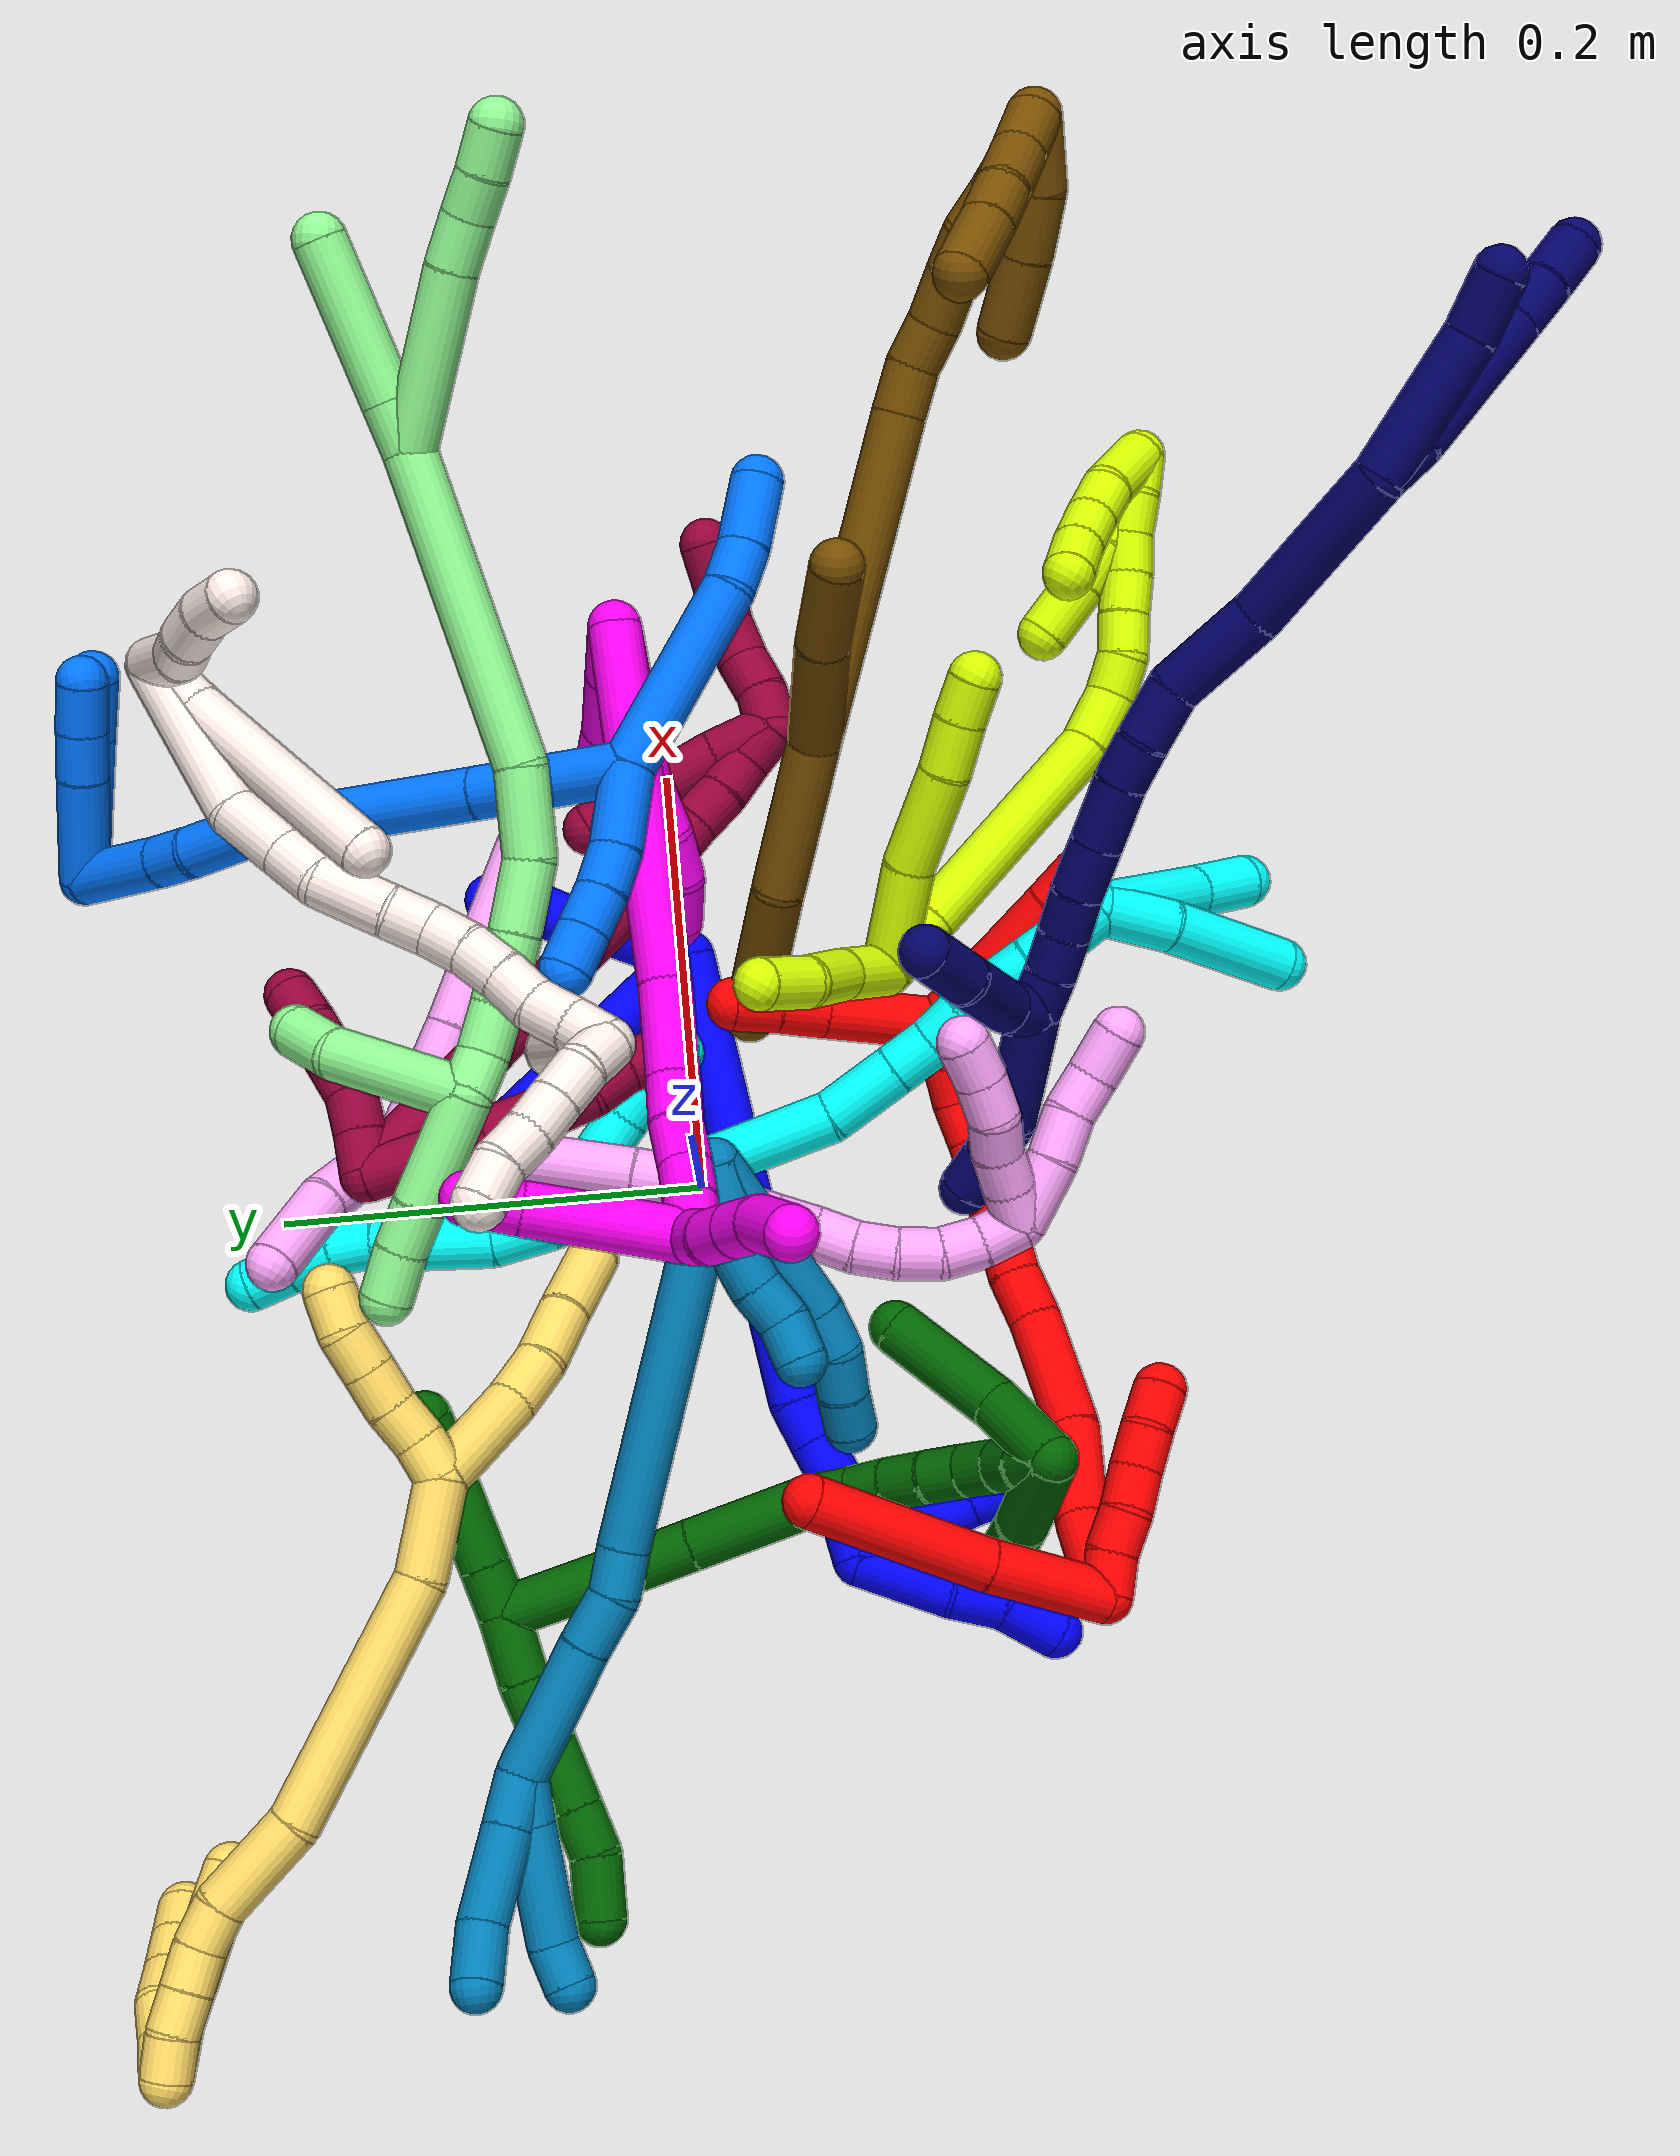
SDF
<sdf version="1.7">
 <world name="default">
  <plugin name="TubeGeneratorPlugin" filename="libtube_generator_plugin.so"/>
  <model name="photoneo_s_sensor">
   <static>1</static>
   <pose>0 0 2 1.57079 1.57079 3.14159</pose>
   <link name="link">
    <inertial><mass>0.1</mass></inertial>
    <sensor name="sensor" type="depth">
     <update_rate>30</update_rate>
     <camera>
      <horizontal_fov>1.22</horizontal_fov>
      <image><width>1920</width><height>1200</height><format>B8G8R8</format></image>
      <clip><near>0.1</near><far>4</far></clip>
      <depth_camera><output>points</output></depth_camera>
     </camera>
     <plugin name="camera_plugin" filename="libgazebo_ros_depth_camera.so">
      <baseline>0.2</baseline>
      <alwaysOn>1</alwaysOn>
      <updateRate>0.0</updateRate>
      <cameraName>camera_ir</cameraName>
      <imageTopicName>/camera/color/image_raw</imageTopicName>
      <cameraInfoTopicName>/camera/color/camera_info</cameraInfoTopicName>
      <depthImageTopicName>/camera/depth/image_raw</depthImageTopicName>
      <depthImageCameraInfoTopicName>/camera/depth/camera_info</depthImageCameraInfoTopicName>
      <pointCloudTopicName>/camera/depth/points</pointCloudTopicName>
      <frameName>fr_optical</frameName>
      <pointCloudCutoff>0.1</pointCloudCutoff>
      <pointCloudCutoffMax>2.0</pointCloudCutoffMax>
      <distortionK1>0</distortionK1>
      <distortionK2>0</distortionK2>
      <distortionK3>0</distortionK3>
      <distortionT1>0</distortionT1>
      <distortionT2>0</distortionT2>
      <CxPrime>0</CxPrime>
      <Cx>0</Cx>
      <Cy>0</Cy>
      <focalLength>0</focalLength>
      <hackBaseline>0</hackBaseline>
     </plugin>
    </sensor>
   </link>
  </model>
  <gravity>0 0 -9.8</gravity>
  <magnetic_field>6e-06 2.3e-05 -4.2e-05</magnetic_field>
  <atmosphere type="adiabatic"/>
  <physics name="default_physics" default="0" type="ode">
   <max_step_size>0.003</max_step_size>
   <real_time_factor>1</real_time_factor>
   <real_time_update_rate>1000</real_time_update_rate>
   <max_contacts>10000</max_contacts>
   <ode>
    <solver>
     <type>quick</type>
     <iters>100</iters>
     <sor>1.3</sor>
     <use_dynamic_moi_rescaling>0</use_dynamic_moi_rescaling>
    </solver>
    <constraints>
     <contact_max_correcting_vel>0</contact_max_correcting_vel>
     <contact_surface_layer>0.001</contact_surface_layer>
     <cfm>0</cfm>
     <erp>0.2</erp>
    </constraints>
   </ode>
  </physics>
  <scene><ambient>0.4 0.4 0.4 1</ambient><background>0.7 0.7 0.7 1</background><shadows>0</shadows></scene>
  <audio><device>default</device></audio>
  <spherical_coordinates>
   <surface_model>EARTH_WGS84</surface_model>
   <latitude_deg>0</latitude_deg>
   <longitude_deg>0</longitude_deg>
   <elevation>0</elevation>
   <heading_deg>0</heading_deg>
  </spherical_coordinates>
  <model name="bin">
   <static>1</static>
   <link name="bottom">
    <collision name="collision-bottom">
     <pose>0 0 -0.01 0 -0 0</pose>
     <geometry><box><size>0.8 0.6 0.02</size></box></geometry>
     <surface>
      <friction><ode><mu>100</mu><mu2>100</mu2></ode></friction>
      <contact><collide_bitmask>65535</collide_bitmask></contact>
     </surface>
    </collision>
   </link>
   <link name="west_wall">
    <collision name="collision-west_wall">
     <pose>-0.41 0 0.1 0 -0 0</pose>
     <geometry><box><size>0.02 0.6 0.2</size></box></geometry>
     <surface>
      <friction><ode><mu>100</mu><mu2>100</mu2></ode></friction>
      <contact><collide_bitmask>65535</collide_bitmask></contact>
     </surface>
    </collision>
   </link>
   <link name="east_wall">
    <collision name="collision-east_wall">
     <pose>0.41 0 0.1 0 -0 0</pose>
     <geometry><box><size>0.02 0.6 0.2</size></box></geometry>
     <surface>
      <friction><ode><mu>100</mu><mu2>100</mu2></ode></friction>
      <contact><collide_bitmask>65535</collide_bitmask></contact>
     </surface>
    </collision>
   </link>
   <link name="south_wall">
    <collision name="collision-south_wall">
     <pose>0 -0.31 0.1 0 -0 0</pose>
     <geometry><box><size>0.8 0.02 0.2</size></box></geometry>
     <surface>
      <friction><ode><mu>100</mu><mu2>100</mu2></ode></friction>
      <contact><collide_bitmask>65535</collide_bitmask></contact>
     </surface>
    </collision>
   </link>
   <link name="north_wall">
    <collision name="collision-north_wall">
     <pose>0 0.31 0.1 0 -0 0</pose>
     <geometry><box><size>0.8 0.02 0.2</size></box></geometry>
     <surface>
      <friction><ode><mu>100</mu><mu2>100</mu2></ode></friction>
      <contact><collide_bitmask>65535</collide_bitmask></contact>
     </surface>
    </collision>
   </link>
  </model>
  <model name="1">
   <static>0</static>
   <link name="1">
    <collision name="collision-cylinder-e_1_2_8">
     <pose>-0.029239 0.046481 -0.027835 -2.11037 -0.494883 0.838602</pose>
     <geometry><cylinder><radius>0.0125</radius><length>0.123129</length></cylinder></geometry>
     <surface>
      <friction><ode><mu>1.16</mu><mu2>1.16</mu2><slip1>0</slip1><slip2>0</slip2></ode></friction>
      <contact><ode><kp>1e+06</kp><kd>1</kd><max_vel>0</max_vel><min_depth>0.001</min_depth></ode></contact>
     </surface>
    </collision>
    <visual name="visual-cylinder-e_1_2_8">
     <pose>-0.029239 0.046481 -0.027835 -2.11037 -0.494883 0.838602</pose>
     <geometry><cylinder><radius>0.0125</radius><length>0.123129</length></cylinder></geometry>
     <material><ambient>0 0 1 1</ambient></material>
    </visual>
    <collision name="collision-cylinder-e_2_8_6">
     <pose>-0.065745 0.102594 -0.061579 -2.12104 -0.571562 0.966813</pose>
     <geometry><cylinder><radius>0.0125</radius><length>0.026871</length></cylinder></geometry>
     <surface>
      <friction><ode><mu>1.16</mu><mu2>1.16</mu2><slip1>0</slip1><slip2>0</slip2></ode></friction>
      <contact><ode><kp>1e+06</kp><kd>1</kd><max_vel>0</max_vel><min_depth>0.001</min_depth></ode></contact>
     </surface>
    </collision>
    <visual name="visual-cylinder-e_2_8_6">
     <pose>-0.065745 0.102594 -0.061579 -2.12104 -0.571562 0.966813</pose>
     <geometry><cylinder><radius>0.0125</radius><length>0.026871</length></cylinder></geometry>
     <material><ambient>0 0 1 1</ambient></material>
    </visual>
    <collision name="collision-cylinder-e_1_2_9">
     <pose>0.005369 0.008375 -0.001014 -1.69131 0.566782 -0.635014</pose>
     <geometry><cylinder><radius>0.0125</radius><length>0.02</length></cylinder></geometry>
     <surface>
      <friction><ode><mu>1.16</mu><mu2>1.16</mu2><slip1>0</slip1><slip2>0</slip2></ode></friction>
      <contact><ode><kp>1e+06</kp><kd>1</kd><max_vel>0</max_vel><min_depth>0.001</min_depth></ode></contact>
     </surface>
    </collision>
    <visual name="visual-cylinder-e_1_2_9">
     <pose>0.005369 0.008375 -0.001014 -1.69131 0.566782 -0.635014</pose>
     <geometry><cylinder><radius>0.0125</radius><length>0.02</length></cylinder></geometry>
     <material><ambient>0 0 1 1</ambient></material>
    </visual>
    <collision name="collision-cylinder-e_2_9_10">
     <pose>0.015938 0.025281 -0.002456 -1.62093 0.546826 -0.573468</pose>
     <geometry><cylinder><radius>0.0125</radius><length>0.02</length></cylinder></geometry>
     <surface>
      <friction><ode><mu>1.16</mu><mu2>1.16</mu2><slip1>0</slip1><slip2>0</slip2></ode></friction>
      <contact><ode><kp>1e+06</kp><kd>1</kd><max_vel>0</max_vel><min_depth>0.001</min_depth></ode></contact>
     </surface>
    </collision>
    <visual name="visual-cylinder-e_2_9_10">
     <pose>0.015938 0.025281 -0.002456 -1.62093 0.546826 -0.573468</pose>
     <geometry><cylinder><radius>0.0125</radius><length>0.02</length></cylinder></geometry>
     <material><ambient>0 0 1 1</ambient></material>
    </visual>
    <collision name="collision-cylinder-e_3_10_11">
     <pose>0.024085 0.043368 -0.002932 -1.57577 0.299151 -0.300622</pose>
     <geometry><cylinder><radius>0.0125</radius><length>0.02</length></cylinder></geometry>
     <surface>
      <friction><ode><mu>1.16</mu><mu2>1.16</mu2><slip1>0</slip1><slip2>0</slip2></ode></friction>
      <contact><ode><kp>1e+06</kp><kd>1</kd><max_vel>0</max_vel><min_depth>0.001</min_depth></ode></contact>
     </surface>
    </collision>
    <visual name="visual-cylinder-e_3_10_11">
     <pose>0.024085 0.043368 -0.002932 -1.57577 0.299151 -0.300622</pose>
     <geometry><cylinder><radius>0.0125</radius><length>0.02</length></cylinder></geometry>
     <material><ambient>0 0 1 1</ambient></material>
    </visual>
    <collision name="collision-cylinder-e_4_11_12">
     <pose>0.031871 0.061628 -0.002074 -1.46713 0.505108 -0.45709</pose>
     <geometry><cylinder><radius>0.0125</radius><length>0.02</length></cylinder></geometry>
     <surface>
      <friction><ode><mu>1.16</mu><mu2>1.16</mu2><slip1>0</slip1><slip2>0</slip2></ode></friction>
      <contact><ode><kp>1e+06</kp><kd>1</kd><max_vel>0</max_vel><min_depth>0.001</min_depth></ode></contact>
     </surface>
    </collision>
    <visual name="visual-cylinder-e_4_11_12">
     <pose>0.031871 0.061628 -0.002074 -1.46713 0.505108 -0.45709</pose>
     <geometry><cylinder><radius>0.0125</radius><length>0.02</length></cylinder></geometry>
     <material><ambient>0 0 1 1</ambient></material>
    </visual>
    <collision name="collision-cylinder-e_5_12_5">
     <pose>0.039195 0.080018 -0.001283 -1.58261 0.251151 -0.254105</pose>
     <geometry><cylinder><radius>0.0125</radius><length>0.02</length></cylinder></geometry>
     <surface>
      <friction><ode><mu>1.16</mu><mu2>1.16</mu2><slip1>0</slip1><slip2>0</slip2></ode></friction>
      <contact><ode><kp>1e+06</kp><kd>1</kd><max_vel>0</max_vel><min_depth>0.001</min_depth></ode></contact>
     </surface>
    </collision>
    <visual name="visual-cylinder-e_5_12_5">
     <pose>0.039195 0.080018 -0.001283 -1.58261 0.251151 -0.254105</pose>
     <geometry><cylinder><radius>0.0125</radius><length>0.02</length></cylinder></geometry>
     <material><ambient>0 0 1 1</ambient></material>
    </visual>
    <collision name="collision-cylinder-e_1_2_13">
     <pose>-0.092253 -0.017741 -0.055584 2.83265 -1.00684 -2.59052</pose>
     <geometry><cylinder><radius>0.0125</radius><length>0.218311</length></cylinder></geometry>
     <surface>
      <friction><ode><mu>1.16</mu><mu2>1.16</mu2><slip1>0</slip1><slip2>0</slip2></ode></friction>
      <contact><ode><kp>1e+06</kp><kd>1</kd><max_vel>0</max_vel><min_depth>0.001</min_depth></ode></contact>
     </surface>
    </collision>
    <visual name="visual-cylinder-e_1_2_13">
     <pose>-0.092253 -0.017741 -0.055584 2.83265 -1.00684 -2.59052</pose>
     <geometry><cylinder><radius>0.0125</radius><length>0.218311</length></cylinder></geometry>
     <material><ambient>0 0 1 1</ambient></material>
    </visual>
    <collision name="collision-cylinder-e_2_13_14">
     <pose>-0.193154 -0.039522 -0.115519 2.39305 -0.969203 -1.85963</pose>
     <geometry><cylinder><radius>0.0125</radius><length>0.020981</length></cylinder></geometry>
     <surface>
      <friction><ode><mu>1.16</mu><mu2>1.16</mu2><slip1>0</slip1><slip2>0</slip2></ode></friction>
      <contact><ode><kp>1e+06</kp><kd>1</kd><max_vel>0</max_vel><min_depth>0.001</min_depth></ode></contact>
     </surface>
    </collision>
    <visual name="visual-cylinder-e_2_13_14">
     <pose>-0.193154 -0.039522 -0.115519 2.39305 -0.969203 -1.85963</pose>
     <geometry><cylinder><radius>0.0125</radius><length>0.020981</length></cylinder></geometry>
     <material><ambient>0 0 1 1</ambient></material>
    </visual>
    <collision name="collision-cylinder-e_3_14_15">
     <pose>-0.21052 -0.047424 -0.123263 2.29188 -1.03798 -1.80189</pose>
     <geometry><cylinder><radius>0.0125</radius><length>0.020239</length></cylinder></geometry>
     <surface>
      <friction><ode><mu>1.16</mu><mu2>1.16</mu2><slip1>0</slip1><slip2>0</slip2></ode></friction>
      <contact><ode><kp>1e+06</kp><kd>1</kd><max_vel>0</max_vel><min_depth>0.001</min_depth></ode></contact>
     </surface>
    </collision>
    <visual name="visual-cylinder-e_3_14_15">
     <pose>-0.21052 -0.047424 -0.123263 2.29188 -1.03798 -1.80189</pose>
     <geometry><cylinder><radius>0.0125</radius><length>0.020239</length></cylinder></geometry>
     <material><ambient>0 0 1 1</ambient></material>
    </visual>
    <collision name="collision-cylinder-e_4_15_16">
     <pose>-0.228881 -0.052716 -0.129433 2.66563 -1.25753 -2.49767</pose>
     <geometry><cylinder><radius>0.0125</radius><length>0.020275</length></cylinder></geometry>
     <surface>
      <friction><ode><mu>1.16</mu><mu2>1.16</mu2><slip1>0</slip1><slip2>0</slip2></ode></friction>
      <contact><ode><kp>1e+06</kp><kd>1</kd><max_vel>0</max_vel><min_depth>0.001</min_depth></ode></contact>
     </surface>
    </collision>
    <visual name="visual-cylinder-e_4_15_16">
     <pose>-0.228881 -0.052716 -0.129433 2.66563 -1.25753 -2.49767</pose>
     <geometry><cylinder><radius>0.0125</radius><length>0.020275</length></cylinder></geometry>
     <material><ambient>0 0 1 1</ambient></material>
    </visual>
    <collision name="collision-cylinder-e_5_16_1">
     <pose>-0.247849 -0.055816 -0.135705 2.69619 -1.17714 -2.48742</pose>
     <geometry><cylinder><radius>0.0125</radius><length>0.020194</length></cylinder></geometry>
     <surface>
      <friction><ode><mu>1.16</mu><mu2>1.16</mu2><slip1>0</slip1><slip2>0</slip2></ode></friction>
      <contact><ode><kp>1e+06</kp><kd>1</kd><max_vel>0</max_vel><min_depth>0.001</min_depth></ode></contact>
     </surface>
    </collision>
    <visual name="visual-cylinder-e_5_16_1">
     <pose>-0.247849 -0.055816 -0.135705 2.69619 -1.17714 -2.48742</pose>
     <geometry><cylinder><radius>0.0125</radius><length>0.020194</length></cylinder></geometry>
     <material><ambient>0 0 1 1</ambient></material>
    </visual>
    <collision name="collision-cylinder-e_1_1_17">
     <pose>-0.267439 -0.077797 -0.139742 1.59745 -0.467791 -0.479953</pose>
     <geometry><cylinder><radius>0.0125</radius><length>0.045531</length></cylinder></geometry>
     <surface>
      <friction><ode><mu>1.16</mu><mu2>1.16</mu2><slip1>0</slip1><slip2>0</slip2></ode></friction>
      <contact><ode><kp>1e+06</kp><kd>1</kd><max_vel>0</max_vel><min_depth>0.001</min_depth></ode></contact>
     </surface>
    </collision>
    <visual name="visual-cylinder-e_1_1_17">
     <pose>-0.267439 -0.077797 -0.139742 1.59745 -0.467791 -0.479953</pose>
     <geometry><cylinder><radius>0.0125</radius><length>0.045531</length></cylinder></geometry>
     <material><ambient>0 0 1 1</ambient></material>
    </visual>
    <collision name="collision-cylinder-e_2_17_18">
     <pose>-0.281228 -0.110196 -0.141166 1.64372 -0.282944 -0.304049</pose>
     <geometry><cylinder><radius>0.0125</radius><length>0.02524</length></cylinder></geometry>
     <surface>
      <friction><ode><mu>1.16</mu><mu2>1.16</mu2><slip1>0</slip1><slip2>0</slip2></ode></friction>
      <contact><ode><kp>1e+06</kp><kd>1</kd><max_vel>0</max_vel><min_depth>0.001</min_depth></ode></contact>
     </surface>
    </collision>
    <visual name="visual-cylinder-e_2_17_18">
     <pose>-0.281228 -0.110196 -0.141166 1.64372 -0.282944 -0.304049</pose>
     <geometry><cylinder><radius>0.0125</radius><length>0.02524</length></cylinder></geometry>
     <material><ambient>0 0 1 1</ambient></material>
    </visual>
    <collision name="collision-cylinder-e_3_18_4">
     <pose>-0.290371 -0.134785 -0.147115 1.95575 -0.394737 -0.577009</pose>
     <geometry><cylinder><radius>0.0125</radius><length>0.029229</length></cylinder></geometry>
     <surface>
      <friction><ode><mu>1.16</mu><mu2>1.16</mu2><slip1>0</slip1><slip2>0</slip2></ode></friction>
      <contact><ode><kp>1e+06</kp><kd>1</kd><max_vel>0</max_vel><min_depth>0.001</min_depth></ode></contact>
     </surface>
    </collision>
    <visual name="visual-cylinder-e_3_18_4">
     <pose>-0.290371 -0.134785 -0.147115 1.95575 -0.394737 -0.577009</pose>
     <geometry><cylinder><radius>0.0125</radius><length>0.029229</length></cylinder></geometry>
     <material><ambient>0 0 1 1</ambient></material>
    </visual>
    <collision name="collision-cylinder-e_1_1_19">
     <pose>-0.253226 -0.070156 -0.134282 1.20057 0.282675 0.194194</pose>
     <geometry><cylinder><radius>0.0125</radius><length>0.028309</length></cylinder></geometry>
     <surface>
      <friction><ode><mu>1.16</mu><mu2>1.16</mu2><slip1>0</slip1><slip2>0</slip2></ode></friction>
      <contact><ode><kp>1e+06</kp><kd>1</kd><max_vel>0</max_vel><min_depth>0.001</min_depth></ode></contact>
     </surface>
    </collision>
    <visual name="visual-cylinder-e_1_1_19">
     <pose>-0.253226 -0.070156 -0.134282 1.20057 0.282675 0.194194</pose>
     <geometry><cylinder><radius>0.0125</radius><length>0.028309</length></cylinder></geometry>
     <material><ambient>0 0 1 1</ambient></material>
    </visual>
    <collision name="collision-cylinder-e_2_19_20">
     <pose>-0.245422 -0.096745 -0.124454 1.23165 0.255571 0.18134</pose>
     <geometry><cylinder><radius>0.0125</radius><length>0.030506</length></cylinder></geometry>
     <surface>
      <friction><ode><mu>1.16</mu><mu2>1.16</mu2><slip1>0</slip1><slip2>0</slip2></ode></friction>
      <contact><ode><kp>1e+06</kp><kd>1</kd><max_vel>0</max_vel><min_depth>0.001</min_depth></ode></contact>
     </surface>
    </collision>
    <visual name="visual-cylinder-e_2_19_20">
     <pose>-0.245422 -0.096745 -0.124454 1.23165 0.255571 0.18134</pose>
     <geometry><cylinder><radius>0.0125</radius><length>0.030506</length></cylinder></geometry>
     <material><ambient>0 0 1 1</ambient></material>
    </visual>
    <collision name="collision-cylinder-e_3_20_21">
     <pose>-0.241019 -0.119721 -0.115151 1.11926 0.054256 0.033993</pose>
     <geometry><cylinder><radius>0.0125</radius><length>0.020167</length></cylinder></geometry>
     <surface>
      <friction><ode><mu>1.16</mu><mu2>1.16</mu2><slip1>0</slip1><slip2>0</slip2></ode></friction>
      <contact><ode><kp>1e+06</kp><kd>1</kd><max_vel>0</max_vel><min_depth>0.001</min_depth></ode></contact>
     </surface>
    </collision>
    <visual name="visual-cylinder-e_3_20_21">
     <pose>-0.241019 -0.119721 -0.115151 1.11926 0.054256 0.033993</pose>
     <geometry><cylinder><radius>0.0125</radius><length>0.020167</length></cylinder></geometry>
     <material><ambient>0 0 1 1</ambient></material>
    </visual>
    <collision name="collision-cylinder-e_4_21_3">
     <pose>-0.239573 -0.13859 -0.107096 1.2135 0.085707 0.059507</pose>
     <geometry><cylinder><radius>0.0125</radius><length>0.021019</length></cylinder></geometry>
     <surface>
      <friction><ode><mu>1.16</mu><mu2>1.16</mu2><slip1>0</slip1><slip2>0</slip2></ode></friction>
      <contact><ode><kp>1e+06</kp><kd>1</kd><max_vel>0</max_vel><min_depth>0.001</min_depth></ode></contact>
     </surface>
    </collision>
    <visual name="visual-cylinder-e_4_21_3">
     <pose>-0.239573 -0.13859 -0.107096 1.2135 0.085707 0.059507</pose>
     <geometry><cylinder><radius>0.0125</radius><length>0.021019</length></cylinder></geometry>
     <material><ambient>0 0 1 1</ambient></material>
    </visual>
    <collision name="collision-sphere-3">
     <pose>-0.238673 -0.148399 -0.103434 0 -0 0</pose>
     <geometry><sphere><radius>0.0125</radius></sphere></geometry>
     <surface>
      <friction><ode><mu>1.16</mu><mu2>1.16</mu2><slip1>0</slip1><slip2>0</slip2></ode></friction>
      <contact><ode><kp>1e+06</kp><kd>1</kd><max_vel>0</max_vel><min_depth>0.001</min_depth></ode></contact>
     </surface>
    </collision>
    <visual name="visual-sphere-3">
     <pose>-0.238673 -0.148399 -0.103434 0 -0 0</pose>
     <geometry><sphere><radius>0.0125</radius></sphere></geometry>
     <material><ambient>0 0 1 1</ambient></material>
    </visual>
    <collision name="collision-sphere-21">
     <pose>-0.240472 -0.128781 -0.110758 0 -0 0</pose>
     <geometry><sphere><radius>0.0125</radius></sphere></geometry>
     <surface>
      <friction><ode><mu>1.16</mu><mu2>1.16</mu2><slip1>0</slip1><slip2>0</slip2></ode></friction>
      <contact><ode><kp>1e+06</kp><kd>1</kd><max_vel>0</max_vel><min_depth>0.001</min_depth></ode></contact>
     </surface>
    </collision>
    <visual name="visual-sphere-21">
     <pose>-0.240472 -0.128781 -0.110758 0 -0 0</pose>
     <geometry><sphere><radius>0.0125</radius></sphere></geometry>
     <material><ambient>0 0 1 1</ambient></material>
    </visual>
    <collision name="collision-sphere-20">
     <pose>-0.241566 -0.110662 -0.119545 0 -0 0</pose>
     <geometry><sphere><radius>0.0125</radius></sphere></geometry>
     <surface>
      <friction><ode><mu>1.16</mu><mu2>1.16</mu2><slip1>0</slip1><slip2>0</slip2></ode></friction>
      <contact><ode><kp>1e+06</kp><kd>1</kd><max_vel>0</max_vel><min_depth>0.001</min_depth></ode></contact>
     </surface>
    </collision>
    <visual name="visual-sphere-20">
     <pose>-0.241566 -0.110662 -0.119545 0 -0 0</pose>
     <geometry><sphere><radius>0.0125</radius></sphere></geometry>
     <material><ambient>0 0 1 1</ambient></material>
    </visual>
    <collision name="collision-sphere-19">
     <pose>-0.249278 -0.082828 -0.129364 0 -0 0</pose>
     <geometry><sphere><radius>0.0125</radius></sphere></geometry>
     <surface>
      <friction><ode><mu>1.16</mu><mu2>1.16</mu2><slip1>0</slip1><slip2>0</slip2></ode></friction>
      <contact><ode><kp>1e+06</kp><kd>1</kd><max_vel>0</max_vel><min_depth>0.001</min_depth></ode></contact>
     </surface>
    </collision>
    <visual name="visual-sphere-19">
     <pose>-0.249278 -0.082828 -0.129364 0 -0 0</pose>
     <geometry><sphere><radius>0.0125</radius></sphere></geometry>
     <material><ambient>0 0 1 1</ambient></material>
    </visual>
    <collision name="collision-sphere-11">
     <pose>0.027032 0.052924 -0.00298 0 -0 0</pose>
     <geometry><sphere><radius>0.0125</radius></sphere></geometry>
     <surface>
      <friction><ode><mu>1.16</mu><mu2>1.16</mu2><slip1>0</slip1><slip2>0</slip2></ode></friction>
      <contact><ode><kp>1e+06</kp><kd>1</kd><max_vel>0</max_vel><min_depth>0.001</min_depth></ode></contact>
     </surface>
    </collision>
    <visual name="visual-sphere-11">
     <pose>0.027032 0.052924 -0.00298 0 -0 0</pose>
     <geometry><sphere><radius>0.0125</radius></sphere></geometry>
     <material><ambient>0 0 1 1</ambient></material>
    </visual>
    <collision name="collision-sphere-10">
     <pose>0.021138 0.033812 -0.002885 0 -0 0</pose>
     <geometry><sphere><radius>0.0125</radius></sphere></geometry>
     <surface>
      <friction><ode><mu>1.16</mu><mu2>1.16</mu2><slip1>0</slip1><slip2>0</slip2></ode></friction>
      <contact><ode><kp>1e+06</kp><kd>1</kd><max_vel>0</max_vel><min_depth>0.001</min_depth></ode></contact>
     </surface>
    </collision>
    <visual name="visual-sphere-10">
     <pose>0.021138 0.033812 -0.002885 0 -0 0</pose>
     <geometry><sphere><radius>0.0125</radius></sphere></geometry>
     <material><ambient>0 0 1 1</ambient></material>
    </visual>
    <collision name="collision-sphere-6">
     <pose>-0.073013 0.112226 -0.067488 0 -0 0</pose>
     <geometry><sphere><radius>0.0125</radius></sphere></geometry>
     <surface>
      <friction><ode><mu>1.16</mu><mu2>1.16</mu2><slip1>0</slip1><slip2>0</slip2></ode></friction>
      <contact><ode><kp>1e+06</kp><kd>1</kd><max_vel>0</max_vel><min_depth>0.001</min_depth></ode></contact>
     </surface>
    </collision>
    <visual name="visual-sphere-6">
     <pose>-0.073013 0.112226 -0.067488 0 -0 0</pose>
     <geometry><sphere><radius>0.0125</radius></sphere></geometry>
     <material><ambient>0 0 1 1</ambient></material>
    </visual>
    <collision name="collision-sphere-9">
     <pose>0.010738 0.01675 -0.002028 0 -0 0</pose>
     <geometry><sphere><radius>0.0125</radius></sphere></geometry>
     <surface>
      <friction><ode><mu>1.16</mu><mu2>1.16</mu2><slip1>0</slip1><slip2>0</slip2></ode></friction>
      <contact><ode><kp>1e+06</kp><kd>1</kd><max_vel>0</max_vel><min_depth>0.001</min_depth></ode></contact>
     </surface>
    </collision>
    <visual name="visual-sphere-9">
     <pose>0.010738 0.01675 -0.002028 0 -0 0</pose>
     <geometry><sphere><radius>0.0125</radius></sphere></geometry>
     <material><ambient>0 0 1 1</ambient></material>
    </visual>
    <collision name="collision-sphere-2">
     <geometry><sphere><radius>0.0125</radius></sphere></geometry>
     <surface>
      <friction><ode><mu>1.16</mu><mu2>1.16</mu2><slip1>0</slip1><slip2>0</slip2></ode></friction>
      <contact><ode><kp>1e+06</kp><kd>1</kd><max_vel>0</max_vel><min_depth>0.001</min_depth></ode></contact>
     </surface>
    </collision>
    <visual name="visual-sphere-2">
     <geometry><sphere><radius>0.0125</radius></sphere></geometry>
     <material><ambient>0 0 1 1</ambient></material>
    </visual>
    <collision name="collision-sphere-8">
     <pose>-0.058477 0.092962 -0.05567 0 -0 0</pose>
     <geometry><sphere><radius>0.0125</radius></sphere></geometry>
     <surface>
      <friction><ode><mu>1.16</mu><mu2>1.16</mu2><slip1>0</slip1><slip2>0</slip2></ode></friction>
      <contact><ode><kp>1e+06</kp><kd>1</kd><max_vel>0</max_vel><min_depth>0.001</min_depth></ode></contact>
     </surface>
    </collision>
    <visual name="visual-sphere-8">
     <pose>-0.058477 0.092962 -0.05567 0 -0 0</pose>
     <geometry><sphere><radius>0.0125</radius></sphere></geometry>
     <material><ambient>0 0 1 1</ambient></material>
    </visual>
    <collision name="collision-sphere-12">
     <pose>0.03671 0.070332 -0.001169 0 -0 0</pose>
     <geometry><sphere><radius>0.0125</radius></sphere></geometry>
     <surface>
      <friction><ode><mu>1.16</mu><mu2>1.16</mu2><slip1>0</slip1><slip2>0</slip2></ode></friction>
      <contact><ode><kp>1e+06</kp><kd>1</kd><max_vel>0</max_vel><min_depth>0.001</min_depth></ode></contact>
     </surface>
    </collision>
    <visual name="visual-sphere-12">
     <pose>0.03671 0.070332 -0.001169 0 -0 0</pose>
     <geometry><sphere><radius>0.0125</radius></sphere></geometry>
     <material><ambient>0 0 1 1</ambient></material>
    </visual>
    <collision name="collision-sphere-5">
     <pose>0.041681 0.089704 -0.001397 0 -0 0</pose>
     <geometry><sphere><radius>0.0125</radius></sphere></geometry>
     <surface>
      <friction><ode><mu>1.16</mu><mu2>1.16</mu2><slip1>0</slip1><slip2>0</slip2></ode></friction>
      <contact><ode><kp>1e+06</kp><kd>1</kd><max_vel>0</max_vel><min_depth>0.001</min_depth></ode></contact>
     </surface>
    </collision>
    <visual name="visual-sphere-5">
     <pose>0.041681 0.089704 -0.001397 0 -0 0</pose>
     <geometry><sphere><radius>0.0125</radius></sphere></geometry>
     <material><ambient>0 0 1 1</ambient></material>
    </visual>
    <collision name="collision-sphere-13">
     <pose>-0.184506 -0.035481 -0.111169 0 -0 0</pose>
     <geometry><sphere><radius>0.0125</radius></sphere></geometry>
     <surface>
      <friction><ode><mu>1.16</mu><mu2>1.16</mu2><slip1>0</slip1><slip2>0</slip2></ode></friction>
      <contact><ode><kp>1e+06</kp><kd>1</kd><max_vel>0</max_vel><min_depth>0.001</min_depth></ode></contact>
     </surface>
    </collision>
    <visual name="visual-sphere-13">
     <pose>-0.184506 -0.035481 -0.111169 0 -0 0</pose>
     <geometry><sphere><radius>0.0125</radius></sphere></geometry>
     <material><ambient>0 0 1 1</ambient></material>
    </visual>
    <collision name="collision-sphere-14">
     <pose>-0.201803 -0.043563 -0.119869 0 -0 0</pose>
     <geometry><sphere><radius>0.0125</radius></sphere></geometry>
     <surface>
      <friction><ode><mu>1.16</mu><mu2>1.16</mu2><slip1>0</slip1><slip2>0</slip2></ode></friction>
      <contact><ode><kp>1e+06</kp><kd>1</kd><max_vel>0</max_vel><min_depth>0.001</min_depth></ode></contact>
     </surface>
    </collision>
    <visual name="visual-sphere-14">
     <pose>-0.201803 -0.043563 -0.119869 0 -0 0</pose>
     <geometry><sphere><radius>0.0125</radius></sphere></geometry>
     <material><ambient>0 0 1 1</ambient></material>
    </visual>
    <collision name="collision-sphere-15">
     <pose>-0.219237 -0.051285 -0.126656 0 -0 0</pose>
     <geometry><sphere><radius>0.0125</radius></sphere></geometry>
     <surface>
      <friction><ode><mu>1.16</mu><mu2>1.16</mu2><slip1>0</slip1><slip2>0</slip2></ode></friction>
      <contact><ode><kp>1e+06</kp><kd>1</kd><max_vel>0</max_vel><min_depth>0.001</min_depth></ode></contact>
     </surface>
    </collision>
    <visual name="visual-sphere-15">
     <pose>-0.219237 -0.051285 -0.126656 0 -0 0</pose>
     <geometry><sphere><radius>0.0125</radius></sphere></geometry>
     <material><ambient>0 0 1 1</ambient></material>
    </visual>
    <collision name="collision-sphere-16">
     <pose>-0.238525 -0.054147 -0.13221 0 -0 0</pose>
     <geometry><sphere><radius>0.0125</radius></sphere></geometry>
     <surface>
      <friction><ode><mu>1.16</mu><mu2>1.16</mu2><slip1>0</slip1><slip2>0</slip2></ode></friction>
      <contact><ode><kp>1e+06</kp><kd>1</kd><max_vel>0</max_vel><min_depth>0.001</min_depth></ode></contact>
     </surface>
    </collision>
    <visual name="visual-sphere-16">
     <pose>-0.238525 -0.054147 -0.13221 0 -0 0</pose>
     <geometry><sphere><radius>0.0125</radius></sphere></geometry>
     <material><ambient>0 0 1 1</ambient></material>
    </visual>
    <collision name="collision-sphere-1">
     <pose>-0.257174 -0.057484 -0.1392 0 -0 0</pose>
     <geometry><sphere><radius>0.0125</radius></sphere></geometry>
     <surface>
      <friction><ode><mu>1.16</mu><mu2>1.16</mu2><slip1>0</slip1><slip2>0</slip2></ode></friction>
      <contact><ode><kp>1e+06</kp><kd>1</kd><max_vel>0</max_vel><min_depth>0.001</min_depth></ode></contact>
     </surface>
    </collision>
    <visual name="visual-sphere-1">
     <pose>-0.257174 -0.057484 -0.1392 0 -0 0</pose>
     <geometry><sphere><radius>0.0125</radius></sphere></geometry>
     <material><ambient>0 0 1 1</ambient></material>
    </visual>
    <collision name="collision-sphere-18">
     <pose>-0.284751 -0.122282 -0.142049 0 -0 0</pose>
     <geometry><sphere><radius>0.0125</radius></sphere></geometry>
     <surface>
      <friction><ode><mu>1.16</mu><mu2>1.16</mu2><slip1>0</slip1><slip2>0</slip2></ode></friction>
      <contact><ode><kp>1e+06</kp><kd>1</kd><max_vel>0</max_vel><min_depth>0.001</min_depth></ode></contact>
     </surface>
    </collision>
    <visual name="visual-sphere-18">
     <pose>-0.284751 -0.122282 -0.142049 0 -0 0</pose>
     <geometry><sphere><radius>0.0125</radius></sphere></geometry>
     <material><ambient>0 0 1 1</ambient></material>
    </visual>
    <collision name="collision-sphere-17">
     <pose>-0.277705 -0.09811 -0.140283 0 -0 0</pose>
     <geometry><sphere><radius>0.0125</radius></sphere></geometry>
     <surface>
      <friction><ode><mu>1.16</mu><mu2>1.16</mu2><slip1>0</slip1><slip2>0</slip2></ode></friction>
      <contact><ode><kp>1e+06</kp><kd>1</kd><max_vel>0</max_vel><min_depth>0.001</min_depth></ode></contact>
     </surface>
    </collision>
    <visual name="visual-sphere-17">
     <pose>-0.277705 -0.09811 -0.140283 0 -0 0</pose>
     <geometry><sphere><radius>0.0125</radius></sphere></geometry>
     <material><ambient>0 0 1 1</ambient></material>
    </visual>
    <collision name="collision-sphere-4">
     <pose>-0.295992 -0.147288 -0.152181 0 -0 0</pose>
     <geometry><sphere><radius>0.0125</radius></sphere></geometry>
     <surface>
      <friction><ode><mu>1.16</mu><mu2>1.16</mu2><slip1>0</slip1><slip2>0</slip2></ode></friction>
      <contact><ode><kp>1e+06</kp><kd>1</kd><max_vel>0</max_vel><min_depth>0.001</min_depth></ode></contact>
     </surface>
    </collision>
    <visual name="visual-sphere-4">
     <pose>-0.295992 -0.147288 -0.152181 0 -0 0</pose>
     <geometry><sphere><radius>0.0125</radius></sphere></geometry>
     <material><ambient>0 0 1 1</ambient></material>
    </visual>
    <inertial>
     <pose>-0.1246 -0.02071 -0.072122 0 -0 0</pose>
     <mass>0.75</mass>
     <inertia>
      <ixx>-0.000449</ixx>
      <ixy>0</ixy>
      <ixz>0</ixz>
      <iyy>0.000683</iyy>
      <iyz>0</iyz>
      <izz>0.000847</izz>
     </inertia>
    </inertial>
   </link>
   <pose>0.109374 -0.003135 0.01734 0.25922 0.541466 0.121012</pose>
  </model>
  <model name="2">
   <static>0</static>
   <link name="2">
    <collision name="collision-cylinder-e_1_2_8">
     <pose>0.016396 0.013395 -0.021175 -2.57755 0.579421 -1.59921</pose>
     <geometry><cylinder><radius>0.0125</radius><length>0.059888</length></cylinder></geometry>
     <surface>
      <friction><ode><mu>1.16</mu><mu2>1.16</mu2><slip1>0</slip1><slip2>0</slip2></ode></friction>
      <contact><ode><kp>1e+06</kp><kd>1</kd><max_vel>0</max_vel><min_depth>0.001</min_depth></ode></contact>
     </surface>
    </collision>
    <visual name="visual-cylinder-e_1_2_8">
     <pose>0.016396 0.013395 -0.021175 -2.57755 0.579421 -1.59921</pose>
     <geometry><cylinder><radius>0.0125</radius><length>0.059888</length></cylinder></geometry>
     <material><ambient>1 0 0 1</ambient></material>
    </visual>
    <collision name="collision-cylinder-e_2_8_6">
     <pose>0.058533 0.049153 -0.071801 -2.49217 0.608131 -1.50062</pose>
     <geometry><cylinder><radius>0.0125</radius><length>0.090112</length></cylinder></geometry>
     <surface>
      <friction><ode><mu>1.16</mu><mu2>1.16</mu2><slip1>0</slip1><slip2>0</slip2></ode></friction>
      <contact><ode><kp>1e+06</kp><kd>1</kd><max_vel>0</max_vel><min_depth>0.001</min_depth></ode></contact>
     </surface>
    </collision>
    <visual name="visual-cylinder-e_2_8_6">
     <pose>0.058533 0.049153 -0.071801 -2.49217 0.608131 -1.50062</pose>
     <geometry><cylinder><radius>0.0125</radius><length>0.090112</length></cylinder></geometry>
     <material><ambient>1 0 0 1</ambient></material>
    </visual>
    <collision name="collision-cylinder-e_1_2_9">
     <pose>0.006721 0.003595 0.006473 -0.506911 0.737066 -0.199396</pose>
     <geometry><cylinder><radius>0.0125</radius><length>0.02</length></cylinder></geometry>
     <surface>
      <friction><ode><mu>1.16</mu><mu2>1.16</mu2><slip1>0</slip1><slip2>0</slip2></ode></friction>
      <contact><ode><kp>1e+06</kp><kd>1</kd><max_vel>0</max_vel><min_depth>0.001</min_depth></ode></contact>
     </surface>
    </collision>
    <visual name="visual-cylinder-e_1_2_9">
     <pose>0.006721 0.003595 0.006473 -0.506911 0.737066 -0.199396</pose>
     <geometry><cylinder><radius>0.0125</radius><length>0.02</length></cylinder></geometry>
     <material><ambient>1 0 0 1</ambient></material>
    </visual>
    <collision name="collision-cylinder-e_2_9_10">
     <pose>0.018233 0.011485 0.020602 -0.511314 0.4996 -0.133172</pose>
     <geometry><cylinder><radius>0.0125</radius><length>0.02</length></cylinder></geometry>
     <surface>
      <friction><ode><mu>1.16</mu><mu2>1.16</mu2><slip1>0</slip1><slip2>0</slip2></ode></friction>
      <contact><ode><kp>1e+06</kp><kd>1</kd><max_vel>0</max_vel><min_depth>0.001</min_depth></ode></contact>
     </surface>
    </collision>
    <visual name="visual-cylinder-e_2_9_10">
     <pose>0.018233 0.011485 0.020602 -0.511314 0.4996 -0.133172</pose>
     <geometry><cylinder><radius>0.0125</radius><length>0.02</length></cylinder></geometry>
     <material><ambient>1 0 0 1</ambient></material>
    </visual>
    <collision name="collision-cylinder-e_3_10_11">
     <pose>0.029371 0.018168 0.035606 -0.31427 0.68766 -0.113339</pose>
     <geometry><cylinder><radius>0.0125</radius><length>0.02</length></cylinder></geometry>
     <surface>
      <friction><ode><mu>1.16</mu><mu2>1.16</mu2><slip1>0</slip1><slip2>0</slip2></ode></friction>
      <contact><ode><kp>1e+06</kp><kd>1</kd><max_vel>0</max_vel><min_depth>0.001</min_depth></ode></contact>
     </surface>
    </collision>
    <visual name="visual-cylinder-e_3_10_11">
     <pose>0.029371 0.018168 0.035606 -0.31427 0.68766 -0.113339</pose>
     <geometry><cylinder><radius>0.0125</radius><length>0.02</length></cylinder></geometry>
     <material><ambient>1 0 0 1</ambient></material>
    </visual>
    <collision name="collision-cylinder-e_4_11_12">
     <pose>0.041312 0.024272 0.050365 -0.464685 0.59357 -0.14447</pose>
     <geometry><cylinder><radius>0.0125</radius><length>0.02</length></cylinder></geometry>
     <surface>
      <friction><ode><mu>1.16</mu><mu2>1.16</mu2><slip1>0</slip1><slip2>0</slip2></ode></friction>
      <contact><ode><kp>1e+06</kp><kd>1</kd><max_vel>0</max_vel><min_depth>0.001</min_depth></ode></contact>
     </surface>
    </collision>
    <visual name="visual-cylinder-e_4_11_12">
     <pose>0.041312 0.024272 0.050365 -0.464685 0.59357 -0.14447</pose>
     <geometry><cylinder><radius>0.0125</radius><length>0.02</length></cylinder></geometry>
     <material><ambient>1 0 0 1</ambient></material>
    </visual>
    <collision name="collision-cylinder-e_5_12_5">
     <pose>0.05277 0.029566 0.065719 -0.196264 0.626775 -0.063786</pose>
     <geometry><cylinder><radius>0.0125</radius><length>0.02</length></cylinder></geometry>
     <surface>
      <friction><ode><mu>1.16</mu><mu2>1.16</mu2><slip1>0</slip1><slip2>0</slip2></ode></friction>
      <contact><ode><kp>1e+06</kp><kd>1</kd><max_vel>0</max_vel><min_depth>0.001</min_depth></ode></contact>
     </surface>
    </collision>
    <visual name="visual-cylinder-e_5_12_5">
     <pose>0.05277 0.029566 0.065719 -0.196264 0.626775 -0.063786</pose>
     <geometry><cylinder><radius>0.0125</radius><length>0.02</length></cylinder></geometry>
     <material><ambient>1 0 0 1</ambient></material>
    </visual>
    <collision name="collision-cylinder-e_1_2_13">
     <pose>0.019752 -0.00187 0.007773 0.236119 1.18618 0.159558</pose>
     <geometry><cylinder><radius>0.0125</radius><length>0.042617</length></cylinder></geometry>
     <surface>
      <friction><ode><mu>1.16</mu><mu2>1.16</mu2><slip1>0</slip1><slip2>0</slip2></ode></friction>
      <contact><ode><kp>1e+06</kp><kd>1</kd><max_vel>0</max_vel><min_depth>0.001</min_depth></ode></contact>
     </surface>
    </collision>
    <visual name="visual-cylinder-e_1_2_13">
     <pose>0.019752 -0.00187 0.007773 0.236119 1.18618 0.159558</pose>
     <geometry><cylinder><radius>0.0125</radius><length>0.042617</length></cylinder></geometry>
     <material><ambient>1 0 0 1</ambient></material>
    </visual>
    <collision name="collision-cylinder-e_2_13_14">
     <pose>0.060249 -0.002413 0.028186 -0.104635 1.02117 -0.058645</pose>
     <geometry><cylinder><radius>0.0125</radius><length>0.048657</length></cylinder></geometry>
     <surface>
      <friction><ode><mu>1.16</mu><mu2>1.16</mu2><slip1>0</slip1><slip2>0</slip2></ode></friction>
      <contact><ode><kp>1e+06</kp><kd>1</kd><max_vel>0</max_vel><min_depth>0.001</min_depth></ode></contact>
     </surface>
    </collision>
    <visual name="visual-cylinder-e_2_13_14">
     <pose>0.060249 -0.002413 0.028186 -0.104635 1.02117 -0.058645</pose>
     <geometry><cylinder><radius>0.0125</radius><length>0.048657</length></cylinder></geometry>
     <material><ambient>1 0 0 1</ambient></material>
    </visual>
    <collision name="collision-cylinder-e_3_14_15">
     <pose>0.108156 0.002581 0.049589 -0.396207 1.2343 -0.282989</pose>
     <geometry><cylinder><radius>0.0125</radius><length>0.05755</length></cylinder></geometry>
     <surface>
      <friction><ode><mu>1.16</mu><mu2>1.16</mu2><slip1>0</slip1><slip2>0</slip2></ode></friction>
      <contact><ode><kp>1e+06</kp><kd>1</kd><max_vel>0</max_vel><min_depth>0.001</min_depth></ode></contact>
     </surface>
    </collision>
    <visual name="visual-cylinder-e_3_14_15">
     <pose>0.108156 0.002581 0.049589 -0.396207 1.2343 -0.282989</pose>
     <geometry><cylinder><radius>0.0125</radius><length>0.05755</length></cylinder></geometry>
     <material><ambient>1 0 0 1</ambient></material>
    </visual>
    <collision name="collision-cylinder-e_4_15_16">
     <pose>0.146621 0.009611 0.06048 -1.00729 1.23234 -0.744092</pose>
     <geometry><cylinder><radius>0.0125</radius><length>0.023969</length></cylinder></geometry>
     <surface>
      <friction><ode><mu>1.16</mu><mu2>1.16</mu2><slip1>0</slip1><slip2>0</slip2></ode></friction>
      <contact><ode><kp>1e+06</kp><kd>1</kd><max_vel>0</max_vel><min_depth>0.001</min_depth></ode></contact>
     </surface>
    </collision>
    <visual name="visual-cylinder-e_4_15_16">
     <pose>0.146621 0.009611 0.06048 -1.00729 1.23234 -0.744092</pose>
     <geometry><cylinder><radius>0.0125</radius><length>0.023969</length></cylinder></geometry>
     <material><ambient>1 0 0 1</ambient></material>
    </visual>
    <collision name="collision-cylinder-e_5_16_17">
     <pose>0.17833 0.021615 0.069415 -0.903333 1.07631 -0.563728</pose>
     <geometry><cylinder><radius>0.0125</radius><length>0.046361</length></cylinder></geometry>
     <surface>
      <friction><ode><mu>1.16</mu><mu2>1.16</mu2><slip1>0</slip1><slip2>0</slip2></ode></friction>
      <contact><ode><kp>1e+06</kp><kd>1</kd><max_vel>0</max_vel><min_depth>0.001</min_depth></ode></contact>
     </surface>
    </collision>
    <visual name="visual-cylinder-e_5_16_17">
     <pose>0.17833 0.021615 0.069415 -0.903333 1.07631 -0.563728</pose>
     <geometry><cylinder><radius>0.0125</radius><length>0.046361</length></cylinder></geometry>
     <material><ambient>1 0 0 1</ambient></material>
    </visual>
    <collision name="collision-cylinder-e_6_17_18">
     <pose>0.207812 0.034421 0.078935 -0.993883 1.06993 -0.621929</pose>
     <geometry><cylinder><radius>0.0125</radius><length>0.020699</length></cylinder></geometry>
     <surface>
      <friction><ode><mu>1.16</mu><mu2>1.16</mu2><slip1>0</slip1><slip2>0</slip2></ode></friction>
      <contact><ode><kp>1e+06</kp><kd>1</kd><max_vel>0</max_vel><min_depth>0.001</min_depth></ode></contact>
     </surface>
    </collision>
    <visual name="visual-cylinder-e_6_17_18">
     <pose>0.207812 0.034421 0.078935 -0.993883 1.06993 -0.621929</pose>
     <geometry><cylinder><radius>0.0125</radius><length>0.020699</length></cylinder></geometry>
     <material><ambient>1 0 0 1</ambient></material>
    </visual>
    <collision name="collision-cylinder-e_7_18_19">
     <pose>0.225692 0.043078 0.083523 -1.1749 1.0656 -0.748315</pose>
     <geometry><cylinder><radius>0.0125</radius><length>0.020117</length></cylinder></geometry>
     <surface>
      <friction><ode><mu>1.16</mu><mu2>1.16</mu2><slip1>0</slip1><slip2>0</slip2></ode></friction>
      <contact><ode><kp>1e+06</kp><kd>1</kd><max_vel>0</max_vel><min_depth>0.001</min_depth></ode></contact>
     </surface>
    </collision>
    <visual name="visual-cylinder-e_7_18_19">
     <pose>0.225692 0.043078 0.083523 -1.1749 1.0656 -0.748315</pose>
     <geometry><cylinder><radius>0.0125</radius><length>0.020117</length></cylinder></geometry>
     <material><ambient>1 0 0 1</ambient></material>
    </visual>
    <collision name="collision-cylinder-e_8_19_20">
     <pose>0.241419 0.054499 0.087436 -1.28511 0.764353 -0.584494</pose>
     <geometry><cylinder><radius>0.0125</radius><length>0.020011</length></cylinder></geometry>
     <surface>
      <friction><ode><mu>1.16</mu><mu2>1.16</mu2><slip1>0</slip1><slip2>0</slip2></ode></friction>
      <contact><ode><kp>1e+06</kp><kd>1</kd><max_vel>0</max_vel><min_depth>0.001</min_depth></ode></contact>
     </surface>
    </collision>
    <visual name="visual-cylinder-e_8_19_20">
     <pose>0.241419 0.054499 0.087436 -1.28511 0.764353 -0.584494</pose>
     <geometry><cylinder><radius>0.0125</radius><length>0.020011</length></cylinder></geometry>
     <material><ambient>1 0 0 1</ambient></material>
    </visual>
    <collision name="collision-cylinder-e_9_20_1">
     <pose>0.254105 0.069507 0.090789 -1.4091 0.613369 -0.525942</pose>
     <geometry><cylinder><radius>0.0125</radius><length>0.020018</length></cylinder></geometry>
     <surface>
      <friction><ode><mu>1.16</mu><mu2>1.16</mu2><slip1>0</slip1><slip2>0</slip2></ode></friction>
      <contact><ode><kp>1e+06</kp><kd>1</kd><max_vel>0</max_vel><min_depth>0.001</min_depth></ode></contact>
     </surface>
    </collision>
    <visual name="visual-cylinder-e_9_20_1">
     <pose>0.254105 0.069507 0.090789 -1.4091 0.613369 -0.525942</pose>
     <geometry><cylinder><radius>0.0125</radius><length>0.020018</length></cylinder></geometry>
     <material><ambient>1 0 0 1</ambient></material>
    </visual>
    <collision name="collision-cylinder-e_1_1_21">
     <pose>0.257819 0.101583 0.123468 -0.653164 -0.05179 0.017545</pose>
     <geometry><cylinder><radius>0.0125</radius><length>0.079086</length></cylinder></geometry>
     <surface>
      <friction><ode><mu>1.16</mu><mu2>1.16</mu2><slip1>0</slip1><slip2>0</slip2></ode></friction>
      <contact><ode><kp>1e+06</kp><kd>1</kd><max_vel>0</max_vel><min_depth>0.001</min_depth></ode></contact>
     </surface>
    </collision>
    <visual name="visual-cylinder-e_1_1_21">
     <pose>0.257819 0.101583 0.123468 -0.653164 -0.05179 0.017545</pose>
     <geometry><cylinder><radius>0.0125</radius><length>0.079086</length></cylinder></geometry>
     <material><ambient>1 0 0 1</ambient></material>
    </visual>
    <collision name="collision-cylinder-e_2_21_4">
     <pose>0.255792 0.131466 0.163473 -0.597826 0.001885 -0.000581</pose>
     <geometry><cylinder><radius>0.0125</radius><length>0.020914</length></cylinder></geometry>
     <surface>
      <friction><ode><mu>1.16</mu><mu2>1.16</mu2><slip1>0</slip1><slip2>0</slip2></ode></friction>
      <contact><ode><kp>1e+06</kp><kd>1</kd><max_vel>0</max_vel><min_depth>0.001</min_depth></ode></contact>
     </surface>
    </collision>
    <visual name="visual-cylinder-e_2_21_4">
     <pose>0.255792 0.131466 0.163473 -0.597826 0.001885 -0.000581</pose>
     <geometry><cylinder><radius>0.0125</radius><length>0.020914</length></cylinder></geometry>
     <material><ambient>1 0 0 1</ambient></material>
    </visual>
    <collision name="collision-cylinder-e_1_1_22">
     <pose>0.273446 0.085734 0.069251 -2.79907 0.510205 -1.97037</pose>
     <geometry><cylinder><radius>0.0125</radius><length>0.055613</length></cylinder></geometry>
     <surface>
      <friction><ode><mu>1.16</mu><mu2>1.16</mu2><slip1>0</slip1><slip2>0</slip2></ode></friction>
      <contact><ode><kp>1e+06</kp><kd>1</kd><max_vel>0</max_vel><min_depth>0.001</min_depth></ode></contact>
     </surface>
    </collision>
    <visual name="visual-cylinder-e_1_1_22">
     <pose>0.273446 0.085734 0.069251 -2.79907 0.510205 -1.97037</pose>
     <geometry><cylinder><radius>0.0125</radius><length>0.055613</length></cylinder></geometry>
     <material><ambient>1 0 0 1</ambient></material>
    </visual>
    <collision name="collision-cylinder-e_2_22_23">
     <pose>0.2923 0.097576 0.037153 -2.76153 0.487307 -1.82451</pose>
     <geometry><cylinder><radius>0.0125</radius><length>0.022528</length></cylinder></geometry>
     <surface>
      <friction><ode><mu>1.16</mu><mu2>1.16</mu2><slip1>0</slip1><slip2>0</slip2></ode></friction>
      <contact><ode><kp>1e+06</kp><kd>1</kd><max_vel>0</max_vel><min_depth>0.001</min_depth></ode></contact>
     </surface>
    </collision>
    <visual name="visual-cylinder-e_2_22_23">
     <pose>0.2923 0.097576 0.037153 -2.76153 0.487307 -1.82451</pose>
     <geometry><cylinder><radius>0.0125</radius><length>0.022528</length></cylinder></geometry>
     <material><ambient>1 0 0 1</ambient></material>
    </visual>
    <collision name="collision-cylinder-e_3_23_3">
     <pose>0.302953 0.103933 0.018776 -2.85779 0.514529 -2.14669</pose>
     <geometry><cylinder><radius>0.0125</radius><length>0.021859</length></cylinder></geometry>
     <surface>
      <friction><ode><mu>1.16</mu><mu2>1.16</mu2><slip1>0</slip1><slip2>0</slip2></ode></friction>
      <contact><ode><kp>1e+06</kp><kd>1</kd><max_vel>0</max_vel><min_depth>0.001</min_depth></ode></contact>
     </surface>
    </collision>
    <visual name="visual-cylinder-e_3_23_3">
     <pose>0.302953 0.103933 0.018776 -2.85779 0.514529 -2.14669</pose>
     <geometry><cylinder><radius>0.0125</radius><length>0.021859</length></cylinder></geometry>
     <material><ambient>1 0 0 1</ambient></material>
    </visual>
    <collision name="collision-sphere-3">
     <pose>0.308331 0.106597 0.009642 0 -0 0</pose>
     <geometry><sphere><radius>0.0125</radius></sphere></geometry>
     <surface>
      <friction><ode><mu>1.16</mu><mu2>1.16</mu2><slip1>0</slip1><slip2>0</slip2></ode></friction>
      <contact><ode><kp>1e+06</kp><kd>1</kd><max_vel>0</max_vel><min_depth>0.001</min_depth></ode></contact>
     </surface>
    </collision>
    <visual name="visual-sphere-3">
     <pose>0.308331 0.106597 0.009642 0 -0 0</pose>
     <geometry><sphere><radius>0.0125</radius></sphere></geometry>
     <material><ambient>1 0 0 1</ambient></material>
    </visual>
    <collision name="collision-sphere-23">
     <pose>0.297574 0.101269 0.02791 0 -0 0</pose>
     <geometry><sphere><radius>0.0125</radius></sphere></geometry>
     <surface>
      <friction><ode><mu>1.16</mu><mu2>1.16</mu2><slip1>0</slip1><slip2>0</slip2></ode></friction>
      <contact><ode><kp>1e+06</kp><kd>1</kd><max_vel>0</max_vel><min_depth>0.001</min_depth></ode></contact>
     </surface>
    </collision>
    <visual name="visual-sphere-23">
     <pose>0.297574 0.101269 0.02791 0 -0 0</pose>
     <geometry><sphere><radius>0.0125</radius></sphere></geometry>
     <material><ambient>1 0 0 1</ambient></material>
    </visual>
    <collision name="collision-sphere-22">
     <pose>0.287025 0.093884 0.046396 0 -0 0</pose>
     <geometry><sphere><radius>0.0125</radius></sphere></geometry>
     <surface>
      <friction><ode><mu>1.16</mu><mu2>1.16</mu2><slip1>0</slip1><slip2>0</slip2></ode></friction>
      <contact><ode><kp>1e+06</kp><kd>1</kd><max_vel>0</max_vel><min_depth>0.001</min_depth></ode></contact>
     </surface>
    </collision>
    <visual name="visual-sphere-22">
     <pose>0.287025 0.093884 0.046396 0 -0 0</pose>
     <geometry><sphere><radius>0.0125</radius></sphere></geometry>
     <material><ambient>1 0 0 1</ambient></material>
    </visual>
    <collision name="collision-sphere-4">
     <pose>0.255812 0.137352 0.172116 0 -0 0</pose>
     <geometry><sphere><radius>0.0125</radius></sphere></geometry>
     <surface>
      <friction><ode><mu>1.16</mu><mu2>1.16</mu2><slip1>0</slip1><slip2>0</slip2></ode></friction>
      <contact><ode><kp>1e+06</kp><kd>1</kd><max_vel>0</max_vel><min_depth>0.001</min_depth></ode></contact>
     </surface>
    </collision>
    <visual name="visual-sphere-4">
     <pose>0.255812 0.137352 0.172116 0 -0 0</pose>
     <geometry><sphere><radius>0.0125</radius></sphere></geometry>
     <material><ambient>1 0 0 1</ambient></material>
    </visual>
    <collision name="collision-sphere-21">
     <pose>0.255772 0.125581 0.154829 0 -0 0</pose>
     <geometry><sphere><radius>0.0125</radius></sphere></geometry>
     <surface>
      <friction><ode><mu>1.16</mu><mu2>1.16</mu2><slip1>0</slip1><slip2>0</slip2></ode></friction>
      <contact><ode><kp>1e+06</kp><kd>1</kd><max_vel>0</max_vel><min_depth>0.001</min_depth></ode></contact>
     </surface>
    </collision>
    <visual name="visual-sphere-21">
     <pose>0.255772 0.125581 0.154829 0 -0 0</pose>
     <geometry><sphere><radius>0.0125</radius></sphere></geometry>
     <material><ambient>1 0 0 1</ambient></material>
    </visual>
    <collision name="collision-sphere-1">
     <pose>0.259866 0.077585 0.092106 0 -0 0</pose>
     <geometry><sphere><radius>0.0125</radius></sphere></geometry>
     <surface>
      <friction><ode><mu>1.16</mu><mu2>1.16</mu2><slip1>0</slip1><slip2>0</slip2></ode></friction>
      <contact><ode><kp>1e+06</kp><kd>1</kd><max_vel>0</max_vel><min_depth>0.001</min_depth></ode></contact>
     </surface>
    </collision>
    <visual name="visual-sphere-1">
     <pose>0.259866 0.077585 0.092106 0 -0 0</pose>
     <geometry><sphere><radius>0.0125</radius></sphere></geometry>
     <material><ambient>1 0 0 1</ambient></material>
    </visual>
    <collision name="collision-sphere-11">
     <pose>0.035718 0.020557 0.042955 0 -0 0</pose>
     <geometry><sphere><radius>0.0125</radius></sphere></geometry>
     <surface>
      <friction><ode><mu>1.16</mu><mu2>1.16</mu2><slip1>0</slip1><slip2>0</slip2></ode></friction>
      <contact><ode><kp>1e+06</kp><kd>1</kd><max_vel>0</max_vel><min_depth>0.001</min_depth></ode></contact>
     </surface>
    </collision>
    <visual name="visual-sphere-11">
     <pose>0.035718 0.020557 0.042955 0 -0 0</pose>
     <geometry><sphere><radius>0.0125</radius></sphere></geometry>
     <material><ambient>1 0 0 1</ambient></material>
    </visual>
    <collision name="collision-sphere-10">
     <pose>0.023024 0.01578 0.028257 0 -0 0</pose>
     <geometry><sphere><radius>0.0125</radius></sphere></geometry>
     <surface>
      <friction><ode><mu>1.16</mu><mu2>1.16</mu2><slip1>0</slip1><slip2>0</slip2></ode></friction>
      <contact><ode><kp>1e+06</kp><kd>1</kd><max_vel>0</max_vel><min_depth>0.001</min_depth></ode></contact>
     </surface>
    </collision>
    <visual name="visual-sphere-10">
     <pose>0.023024 0.01578 0.028257 0 -0 0</pose>
     <geometry><sphere><radius>0.0125</radius></sphere></geometry>
     <material><ambient>1 0 0 1</ambient></material>
    </visual>
    <collision name="collision-sphere-6">
     <pose>0.084275 0.071515 -0.101252 0 -0 0</pose>
     <geometry><sphere><radius>0.0125</radius></sphere></geometry>
     <surface>
      <friction><ode><mu>1.16</mu><mu2>1.16</mu2><slip1>0</slip1><slip2>0</slip2></ode></friction>
      <contact><ode><kp>1e+06</kp><kd>1</kd><max_vel>0</max_vel><min_depth>0.001</min_depth></ode></contact>
     </surface>
    </collision>
    <visual name="visual-sphere-6">
     <pose>0.084275 0.071515 -0.101252 0 -0 0</pose>
     <geometry><sphere><radius>0.0125</radius></sphere></geometry>
     <material><ambient>1 0 0 1</ambient></material>
    </visual>
    <collision name="collision-sphere-9">
     <pose>0.013442 0.007189 0.012947 0 -0 0</pose>
     <geometry><sphere><radius>0.0125</radius></sphere></geometry>
     <surface>
      <friction><ode><mu>1.16</mu><mu2>1.16</mu2><slip1>0</slip1><slip2>0</slip2></ode></friction>
      <contact><ode><kp>1e+06</kp><kd>1</kd><max_vel>0</max_vel><min_depth>0.001</min_depth></ode></contact>
     </surface>
    </collision>
    <visual name="visual-sphere-9">
     <pose>0.013442 0.007189 0.012947 0 -0 0</pose>
     <geometry><sphere><radius>0.0125</radius></sphere></geometry>
     <material><ambient>1 0 0 1</ambient></material>
    </visual>
    <collision name="collision-sphere-2">
     <geometry><sphere><radius>0.0125</radius></sphere></geometry>
     <surface>
      <friction><ode><mu>1.16</mu><mu2>1.16</mu2><slip1>0</slip1><slip2>0</slip2></ode></friction>
      <contact><ode><kp>1e+06</kp><kd>1</kd><max_vel>0</max_vel><min_depth>0.001</min_depth></ode></contact>
     </surface>
    </collision>
    <visual name="visual-sphere-2">
     <geometry><sphere><radius>0.0125</radius></sphere></geometry>
     <material><ambient>1 0 0 1</ambient></material>
    </visual>
    <collision name="collision-sphere-19">
     <pose>0.234494 0.047569 0.0854 0 -0 0</pose>
     <geometry><sphere><radius>0.0125</radius></sphere></geometry>
     <surface>
      <friction><ode><mu>1.16</mu><mu2>1.16</mu2><slip1>0</slip1><slip2>0</slip2></ode></friction>
      <contact><ode><kp>1e+06</kp><kd>1</kd><max_vel>0</max_vel><min_depth>0.001</min_depth></ode></contact>
     </surface>
    </collision>
    <visual name="visual-sphere-19">
     <pose>0.234494 0.047569 0.0854 0 -0 0</pose>
     <geometry><sphere><radius>0.0125</radius></sphere></geometry>
     <material><ambient>1 0 0 1</ambient></material>
    </visual>
    <collision name="collision-sphere-8">
     <pose>0.032791 0.026791 -0.04235 0 -0 0</pose>
     <geometry><sphere><radius>0.0125</radius></sphere></geometry>
     <surface>
      <friction><ode><mu>1.16</mu><mu2>1.16</mu2><slip1>0</slip1><slip2>0</slip2></ode></friction>
      <contact><ode><kp>1e+06</kp><kd>1</kd><max_vel>0</max_vel><min_depth>0.001</min_depth></ode></contact>
     </surface>
    </collision>
    <visual name="visual-sphere-8">
     <pose>0.032791 0.026791 -0.04235 0 -0 0</pose>
     <geometry><sphere><radius>0.0125</radius></sphere></geometry>
     <material><ambient>1 0 0 1</ambient></material>
    </visual>
    <collision name="collision-sphere-12">
     <pose>0.046905 0.027987 0.057776 0 -0 0</pose>
     <geometry><sphere><radius>0.0125</radius></sphere></geometry>
     <surface>
      <friction><ode><mu>1.16</mu><mu2>1.16</mu2><slip1>0</slip1><slip2>0</slip2></ode></friction>
      <contact><ode><kp>1e+06</kp><kd>1</kd><max_vel>0</max_vel><min_depth>0.001</min_depth></ode></contact>
     </surface>
    </collision>
    <visual name="visual-sphere-12">
     <pose>0.046905 0.027987 0.057776 0 -0 0</pose>
     <geometry><sphere><radius>0.0125</radius></sphere></geometry>
     <material><ambient>1 0 0 1</ambient></material>
    </visual>
    <collision name="collision-sphere-5">
     <pose>0.058636 0.031146 0.073663 0 -0 0</pose>
     <geometry><sphere><radius>0.0125</radius></sphere></geometry>
     <surface>
      <friction><ode><mu>1.16</mu><mu2>1.16</mu2><slip1>0</slip1><slip2>0</slip2></ode></friction>
      <contact><ode><kp>1e+06</kp><kd>1</kd><max_vel>0</max_vel><min_depth>0.001</min_depth></ode></contact>
     </surface>
    </collision>
    <visual name="visual-sphere-5">
     <pose>0.058636 0.031146 0.073663 0 -0 0</pose>
     <geometry><sphere><radius>0.0125</radius></sphere></geometry>
     <material><ambient>1 0 0 1</ambient></material>
    </visual>
    <collision name="collision-sphere-13">
     <pose>0.039504 -0.003741 0.015547 0 -0 0</pose>
     <geometry><sphere><radius>0.0125</radius></sphere></geometry>
     <surface>
      <friction><ode><mu>1.16</mu><mu2>1.16</mu2><slip1>0</slip1><slip2>0</slip2></ode></friction>
      <contact><ode><kp>1e+06</kp><kd>1</kd><max_vel>0</max_vel><min_depth>0.001</min_depth></ode></contact>
     </surface>
    </collision>
    <visual name="visual-sphere-13">
     <pose>0.039504 -0.003741 0.015547 0 -0 0</pose>
     <geometry><sphere><radius>0.0125</radius></sphere></geometry>
     <material><ambient>1 0 0 1</ambient></material>
    </visual>
    <collision name="collision-sphere-14">
     <pose>0.080995 -0.001086 0.040825 0 -0 0</pose>
     <geometry><sphere><radius>0.0125</radius></sphere></geometry>
     <surface>
      <friction><ode><mu>1.16</mu><mu2>1.16</mu2><slip1>0</slip1><slip2>0</slip2></ode></friction>
      <contact><ode><kp>1e+06</kp><kd>1</kd><max_vel>0</max_vel><min_depth>0.001</min_depth></ode></contact>
     </surface>
    </collision>
    <visual name="visual-sphere-14">
     <pose>0.080995 -0.001086 0.040825 0 -0 0</pose>
     <geometry><sphere><radius>0.0125</radius></sphere></geometry>
     <material><ambient>1 0 0 1</ambient></material>
    </visual>
    <collision name="collision-sphere-15">
     <pose>0.135317 0.006247 0.058354 0 -0 0</pose>
     <geometry><sphere><radius>0.0125</radius></sphere></geometry>
     <surface>
      <friction><ode><mu>1.16</mu><mu2>1.16</mu2><slip1>0</slip1><slip2>0</slip2></ode></friction>
      <contact><ode><kp>1e+06</kp><kd>1</kd><max_vel>0</max_vel><min_depth>0.001</min_depth></ode></contact>
     </surface>
    </collision>
    <visual name="visual-sphere-15">
     <pose>0.135317 0.006247 0.058354 0 -0 0</pose>
     <geometry><sphere><radius>0.0125</radius></sphere></geometry>
     <material><ambient>1 0 0 1</ambient></material>
    </visual>
    <collision name="collision-sphere-16">
     <pose>0.157926 0.012975 0.062605 0 -0 0</pose>
     <geometry><sphere><radius>0.0125</radius></sphere></geometry>
     <surface>
      <friction><ode><mu>1.16</mu><mu2>1.16</mu2><slip1>0</slip1><slip2>0</slip2></ode></friction>
      <contact><ode><kp>1e+06</kp><kd>1</kd><max_vel>0</max_vel><min_depth>0.001</min_depth></ode></contact>
     </surface>
    </collision>
    <visual name="visual-sphere-16">
     <pose>0.157926 0.012975 0.062605 0 -0 0</pose>
     <geometry><sphere><radius>0.0125</radius></sphere></geometry>
     <material><ambient>1 0 0 1</ambient></material>
    </visual>
    <collision name="collision-sphere-17">
     <pose>0.198733 0.030256 0.076224 0 -0 0</pose>
     <geometry><sphere><radius>0.0125</radius></sphere></geometry>
     <surface>
      <friction><ode><mu>1.16</mu><mu2>1.16</mu2><slip1>0</slip1><slip2>0</slip2></ode></friction>
      <contact><ode><kp>1e+06</kp><kd>1</kd><max_vel>0</max_vel><min_depth>0.001</min_depth></ode></contact>
     </surface>
    </collision>
    <visual name="visual-sphere-17">
     <pose>0.198733 0.030256 0.076224 0 -0 0</pose>
     <geometry><sphere><radius>0.0125</radius></sphere></geometry>
     <material><ambient>1 0 0 1</ambient></material>
    </visual>
    <collision name="collision-sphere-18">
     <pose>0.21689 0.038586 0.081646 0 -0 0</pose>
     <geometry><sphere><radius>0.0125</radius></sphere></geometry>
     <surface>
      <friction><ode><mu>1.16</mu><mu2>1.16</mu2><slip1>0</slip1><slip2>0</slip2></ode></friction>
      <contact><ode><kp>1e+06</kp><kd>1</kd><max_vel>0</max_vel><min_depth>0.001</min_depth></ode></contact>
     </surface>
    </collision>
    <visual name="visual-sphere-18">
     <pose>0.21689 0.038586 0.081646 0 -0 0</pose>
     <geometry><sphere><radius>0.0125</radius></sphere></geometry>
     <material><ambient>1 0 0 1</ambient></material>
    </visual>
    <collision name="collision-sphere-20">
     <pose>0.248343 0.061429 0.089471 0 -0 0</pose>
     <geometry><sphere><radius>0.0125</radius></sphere></geometry>
     <surface>
      <friction><ode><mu>1.16</mu><mu2>1.16</mu2><slip1>0</slip1><slip2>0</slip2></ode></friction>
      <contact><ode><kp>1e+06</kp><kd>1</kd><max_vel>0</max_vel><min_depth>0.001</min_depth></ode></contact>
     </surface>
    </collision>
    <visual name="visual-sphere-20">
     <pose>0.248343 0.061429 0.089471 0 -0 0</pose>
     <geometry><sphere><radius>0.0125</radius></sphere></geometry>
     <material><ambient>1 0 0 1</ambient></material>
    </visual>
    <inertial>
     <pose>0.138557 0.042986 0.0403 0 -0 0</pose>
     <mass>0.75</mass>
     <inertia><ixx>1.3e-05</ixx><ixy>0</ixy><ixz>0</ixz><iyy>6e-05</iyy><iyz>0</iyz><izz>-0.000192</izz></inertia>
    </inertial>
   </link>
   <pose>-0.211349 -0.167569 0.082992 1.81242 0.412346 0.571073</pose>
  </model>
  <model name="3">
   <static>0</static>
   <link name="3">
    <collision name="collision-cylinder-e_1_2_8">
     <pose>-0.00577 0.00658 -0.01234 -2.6517 -0.391288 1.34069</pose>
     <geometry><cylinder><radius>0.0125</radius><length>0.030256</length></cylinder></geometry>
     <surface>
      <friction><ode><mu>1.16</mu><mu2>1.16</mu2><slip1>0</slip1><slip2>0</slip2></ode></friction>
      <contact><ode><kp>1e+06</kp><kd>1</kd><max_vel>0</max_vel><min_depth>0.001</min_depth></ode></contact>
     </surface>
    </collision>
    <visual name="visual-cylinder-e_1_2_8">
     <pose>-0.00577 0.00658 -0.01234 -2.6517 -0.391288 1.34069</pose>
     <geometry><cylinder><radius>0.0125</radius><length>0.030256</length></cylinder></geometry>
     <material><ambient>0.003922 1 0.996078 1</ambient></material>
    </visual>
    <collision name="collision-cylinder-e_2_8_9">
     <pose>-0.014869 0.017003 -0.040044 -2.8965 -0.207248 1.40246</pose>
     <geometry><cylinder><radius>0.0125</radius><length>0.032368</length></cylinder></geometry>
     <surface>
      <friction><ode><mu>1.16</mu><mu2>1.16</mu2><slip1>0</slip1><slip2>0</slip2></ode></friction>
      <contact><ode><kp>1e+06</kp><kd>1</kd><max_vel>0</max_vel><min_depth>0.001</min_depth></ode></contact>
     </surface>
    </collision>
    <visual name="visual-cylinder-e_2_8_9">
     <pose>-0.014869 0.017003 -0.040044 -2.8965 -0.207248 1.40246</pose>
     <geometry><cylinder><radius>0.0125</radius><length>0.032368</length></cylinder></geometry>
     <material><ambient>0.003922 1 0.996078 1</ambient></material>
    </visual>
    <collision name="collision-cylinder-e_3_9_10">
     <pose>-0.023309 0.022201 -0.066171 -3.01639 -0.440227 2.59528</pose>
     <geometry><cylinder><radius>0.0125</radius><length>0.023981</length></cylinder></geometry>
     <surface>
      <friction><ode><mu>1.16</mu><mu2>1.16</mu2><slip1>0</slip1><slip2>0</slip2></ode></friction>
      <contact><ode><kp>1e+06</kp><kd>1</kd><max_vel>0</max_vel><min_depth>0.001</min_depth></ode></contact>
     </surface>
    </collision>
    <visual name="visual-cylinder-e_3_9_10">
     <pose>-0.023309 0.022201 -0.066171 -3.01639 -0.440227 2.59528</pose>
     <geometry><cylinder><radius>0.0125</radius><length>0.023981</length></cylinder></geometry>
     <material><ambient>0.003922 1 0.996078 1</ambient></material>
    </visual>
    <collision name="collision-cylinder-e_4_10_11">
     <pose>-0.032658 0.0273 -0.086019 -2.75066 -0.407276 1.61286</pose>
     <geometry><cylinder><radius>0.0125</radius><length>0.021406</length></cylinder></geometry>
     <surface>
      <friction><ode><mu>1.16</mu><mu2>1.16</mu2><slip1>0</slip1><slip2>0</slip2></ode></friction>
      <contact><ode><kp>1e+06</kp><kd>1</kd><max_vel>0</max_vel><min_depth>0.001</min_depth></ode></contact>
     </surface>
    </collision>
    <visual name="visual-cylinder-e_4_10_11">
     <pose>-0.032658 0.0273 -0.086019 -2.75066 -0.407276 1.61286</pose>
     <geometry><cylinder><radius>0.0125</radius><length>0.021406</length></cylinder></geometry>
     <material><ambient>0.003922 1 0.996078 1</ambient></material>
    </visual>
    <collision name="collision-cylinder-e_5_11_12">
     <pose>-0.041224 0.036733 -0.103018 -2.51837 -0.417831 1.16423</pose>
     <geometry><cylinder><radius>0.0125</radius><length>0.021325</length></cylinder></geometry>
     <surface>
      <friction><ode><mu>1.16</mu><mu2>1.16</mu2><slip1>0</slip1><slip2>0</slip2></ode></friction>
      <contact><ode><kp>1e+06</kp><kd>1</kd><max_vel>0</max_vel><min_depth>0.001</min_depth></ode></contact>
     </surface>
    </collision>
    <visual name="visual-cylinder-e_5_11_12">
     <pose>-0.041224 0.036733 -0.103018 -2.51837 -0.417831 1.16423</pose>
     <geometry><cylinder><radius>0.0125</radius><length>0.021325</length></cylinder></geometry>
     <material><ambient>0.003922 1 0.996078 1</ambient></material>
    </visual>
    <collision name="collision-cylinder-e_6_12_6">
     <pose>-0.049975 0.047883 -0.118503 -2.5166 -0.442514 1.21638</pose>
     <geometry><cylinder><radius>0.0125</radius><length>0.020664</length></cylinder></geometry>
     <surface>
      <friction><ode><mu>1.16</mu><mu2>1.16</mu2><slip1>0</slip1><slip2>0</slip2></ode></friction>
      <contact><ode><kp>1e+06</kp><kd>1</kd><max_vel>0</max_vel><min_depth>0.001</min_depth></ode></contact>
     </surface>
    </collision>
    <visual name="visual-cylinder-e_6_12_6">
     <pose>-0.049975 0.047883 -0.118503 -2.5166 -0.442514 1.21638</pose>
     <geometry><cylinder><radius>0.0125</radius><length>0.020664</length></cylinder></geometry>
     <material><ambient>0.003922 1 0.996078 1</ambient></material>
    </visual>
    <collision name="collision-cylinder-e_1_2_13">
     <pose>0.002401 -0.009141 0.003267 1.22753 0.242462 0.171246</pose>
     <geometry><cylinder><radius>0.0125</radius><length>0.02</length></cylinder></geometry>
     <surface>
      <friction><ode><mu>1.16</mu><mu2>1.16</mu2><slip1>0</slip1><slip2>0</slip2></ode></friction>
      <contact><ode><kp>1e+06</kp><kd>1</kd><max_vel>0</max_vel><min_depth>0.001</min_depth></ode></contact>
     </surface>
    </collision>
    <visual name="visual-cylinder-e_1_2_13">
     <pose>0.002401 -0.009141 0.003267 1.22753 0.242462 0.171246</pose>
     <geometry><cylinder><radius>0.0125</radius><length>0.02</length></cylinder></geometry>
     <material><ambient>0.003922 1 0.996078 1</ambient></material>
    </visual>
    <collision name="collision-cylinder-e_2_13_14">
     <pose>0.007507 -0.027338 0.009801 1.22456 0.273899 0.192975</pose>
     <geometry><cylinder><radius>0.0125</radius><length>0.02</length></cylinder></geometry>
     <surface>
      <friction><ode><mu>1.16</mu><mu2>1.16</mu2><slip1>0</slip1><slip2>0</slip2></ode></friction>
      <contact><ode><kp>1e+06</kp><kd>1</kd><max_vel>0</max_vel><min_depth>0.001</min_depth></ode></contact>
     </surface>
    </collision>
    <visual name="visual-cylinder-e_2_13_14">
     <pose>0.007507 -0.027338 0.009801 1.22456 0.273899 0.192975</pose>
     <geometry><cylinder><radius>0.0125</radius><length>0.02</length></cylinder></geometry>
     <material><ambient>0.003922 1 0.996078 1</ambient></material>
    </visual>
    <collision name="collision-cylinder-e_3_14_15">
     <pose>0.012783 -0.045424 0.01651 1.20666 0.260108 0.179756</pose>
     <geometry><cylinder><radius>0.0125</radius><length>0.02</length></cylinder></geometry>
     <surface>
      <friction><ode><mu>1.16</mu><mu2>1.16</mu2><slip1>0</slip1><slip2>0</slip2></ode></friction>
      <contact><ode><kp>1e+06</kp><kd>1</kd><max_vel>0</max_vel><min_depth>0.001</min_depth></ode></contact>
     </surface>
    </collision>
    <visual name="visual-cylinder-e_3_14_15">
     <pose>0.012783 -0.045424 0.01651 1.20666 0.260108 0.179756</pose>
     <geometry><cylinder><radius>0.0125</radius><length>0.02</length></cylinder></geometry>
     <material><ambient>0.003922 1 0.996078 1</ambient></material>
    </visual>
    <collision name="collision-cylinder-e_4_15_16">
     <pose>0.019046 -0.063056 0.023471 1.18242 0.377971 0.255402</pose>
     <geometry><cylinder><radius>0.0125</radius><length>0.02</length></cylinder></geometry>
     <surface>
      <friction><ode><mu>1.16</mu><mu2>1.16</mu2><slip1>0</slip1><slip2>0</slip2></ode></friction>
      <contact><ode><kp>1e+06</kp><kd>1</kd><max_vel>0</max_vel><min_depth>0.001</min_depth></ode></contact>
     </surface>
    </collision>
    <visual name="visual-cylinder-e_4_15_16">
     <pose>0.019046 -0.063056 0.023471 1.18242 0.377971 0.255402</pose>
     <geometry><cylinder><radius>0.0125</radius><length>0.02</length></cylinder></geometry>
     <material><ambient>0.003922 1 0.996078 1</ambient></material>
    </visual>
    <collision name="collision-cylinder-e_5_16_5">
     <pose>0.027634 -0.079342 0.03111 1.07866 0.511913 0.310735</pose>
     <geometry><cylinder><radius>0.0125</radius><length>0.02</length></cylinder></geometry>
     <surface>
      <friction><ode><mu>1.16</mu><mu2>1.16</mu2><slip1>0</slip1><slip2>0</slip2></ode></friction>
      <contact><ode><kp>1e+06</kp><kd>1</kd><max_vel>0</max_vel><min_depth>0.001</min_depth></ode></contact>
     </surface>
    </collision>
    <visual name="visual-cylinder-e_5_16_5">
     <pose>0.027634 -0.079342 0.03111 1.07866 0.511913 0.310735</pose>
     <geometry><cylinder><radius>0.0125</radius><length>0.02</length></cylinder></geometry>
     <material><ambient>0.003922 1 0.996078 1</ambient></material>
    </visual>
    <collision name="collision-cylinder-e_1_2_17">
     <pose>0.026486 -0.035378 0.054637 0.57462 0.386453 0.115505</pose>
     <geometry><cylinder><radius>0.0125</radius><length>0.140545</length></cylinder></geometry>
     <surface>
      <friction><ode><mu>1.16</mu><mu2>1.16</mu2><slip1>0</slip1><slip2>0</slip2></ode></friction>
      <contact><ode><kp>1e+06</kp><kd>1</kd><max_vel>0</max_vel><min_depth>0.001</min_depth></ode></contact>
     </surface>
    </collision>
    <visual name="visual-cylinder-e_1_2_17">
     <pose>0.026486 -0.035378 0.054637 0.57462 0.386453 0.115505</pose>
     <geometry><cylinder><radius>0.0125</radius><length>0.140545</length></cylinder></geometry>
     <material><ambient>0.003922 1 0.996078 1</ambient></material>
    </visual>
    <collision name="collision-cylinder-e_2_17_18">
     <pose>0.060305 -0.083713 0.12031 0.865286 0.406796 0.189929</pose>
     <geometry><cylinder><radius>0.0125</radius><length>0.037067</length></cylinder></geometry>
     <surface>
      <friction><ode><mu>1.16</mu><mu2>1.16</mu2><slip1>0</slip1><slip2>0</slip2></ode></friction>
      <contact><ode><kp>1e+06</kp><kd>1</kd><max_vel>0</max_vel><min_depth>0.001</min_depth></ode></contact>
     </surface>
    </collision>
    <visual name="visual-cylinder-e_2_17_18">
     <pose>0.060305 -0.083713 0.12031 0.865286 0.406796 0.189929</pose>
     <geometry><cylinder><radius>0.0125</radius><length>0.037067</length></cylinder></geometry>
     <material><ambient>0.003922 1 0.996078 1</ambient></material>
    </visual>
    <collision name="collision-cylinder-e_3_18_19">
     <pose>0.071816 -0.104206 0.137763 0.865486 0.3994 0.186451</pose>
     <geometry><cylinder><radius>0.0125</radius><length>0.021484</length></cylinder></geometry>
     <surface>
      <friction><ode><mu>1.16</mu><mu2>1.16</mu2><slip1>0</slip1><slip2>0</slip2></ode></friction>
      <contact><ode><kp>1e+06</kp><kd>1</kd><max_vel>0</max_vel><min_depth>0.001</min_depth></ode></contact>
     </surface>
    </collision>
    <visual name="visual-cylinder-e_3_18_19">
     <pose>0.071816 -0.104206 0.137763 0.865486 0.3994 0.186451</pose>
     <geometry><cylinder><radius>0.0125</radius><length>0.021484</length></cylinder></geometry>
     <material><ambient>0.003922 1 0.996078 1</ambient></material>
    </visual>
    <collision name="collision-cylinder-e_4_19_20">
     <pose>0.080709 -0.119294 0.148793 1.02233 0.489555 0.278395</pose>
     <geometry><cylinder><radius>0.0125</radius><length>0.020057</length></cylinder></geometry>
     <surface>
      <friction><ode><mu>1.16</mu><mu2>1.16</mu2><slip1>0</slip1><slip2>0</slip2></ode></friction>
      <contact><ode><kp>1e+06</kp><kd>1</kd><max_vel>0</max_vel><min_depth>0.001</min_depth></ode></contact>
     </surface>
    </collision>
    <visual name="visual-cylinder-e_4_19_20">
     <pose>0.080709 -0.119294 0.148793 1.02233 0.489555 0.278395</pose>
     <geometry><cylinder><radius>0.0125</radius><length>0.020057</length></cylinder></geometry>
     <material><ambient>0.003922 1 0.996078 1</ambient></material>
    </visual>
    <collision name="collision-cylinder-e_5_20_21">
     <pose>0.090894 -0.133477 0.158619 0.904563 0.575359 0.28557</pose>
     <geometry><cylinder><radius>0.0125</radius><length>0.020104</length></cylinder></geometry>
     <surface>
      <friction><ode><mu>1.16</mu><mu2>1.16</mu2><slip1>0</slip1><slip2>0</slip2></ode></friction>
      <contact><ode><kp>1e+06</kp><kd>1</kd><max_vel>0</max_vel><min_depth>0.001</min_depth></ode></contact>
     </surface>
    </collision>
    <visual name="visual-cylinder-e_5_20_21">
     <pose>0.090894 -0.133477 0.158619 0.904563 0.575359 0.28557</pose>
     <geometry><cylinder><radius>0.0125</radius><length>0.020104</length></cylinder></geometry>
     <material><ambient>0.003922 1 0.996078 1</ambient></material>
    </visual>
    <collision name="collision-cylinder-e_6_21_22">
     <pose>0.101181 -0.146903 0.169625 0.864856 0.494678 0.232051</pose>
     <geometry><cylinder><radius>0.0125</radius><length>0.020294</length></cylinder></geometry>
     <surface>
      <friction><ode><mu>1.16</mu><mu2>1.16</mu2><slip1>0</slip1><slip2>0</slip2></ode></friction>
      <contact><ode><kp>1e+06</kp><kd>1</kd><max_vel>0</max_vel><min_depth>0.001</min_depth></ode></contact>
     </surface>
    </collision>
    <visual name="visual-cylinder-e_6_21_22">
     <pose>0.101181 -0.146903 0.169625 0.864856 0.494678 0.232051</pose>
     <geometry><cylinder><radius>0.0125</radius><length>0.020294</length></cylinder></geometry>
     <material><ambient>0.003922 1 0.996078 1</ambient></material>
    </visual>
    <collision name="collision-cylinder-e_7_22_23">
     <pose>0.110415 -0.160541 0.18142 0.850783 0.451829 0.207511</pose>
     <geometry><cylinder><radius>0.0125</radius><length>0.020232</length></cylinder></geometry>
     <surface>
      <friction><ode><mu>1.16</mu><mu2>1.16</mu2><slip1>0</slip1><slip2>0</slip2></ode></friction>
      <contact><ode><kp>1e+06</kp><kd>1</kd><max_vel>0</max_vel><min_depth>0.001</min_depth></ode></contact>
     </surface>
    </collision>
    <visual name="visual-cylinder-e_7_22_23">
     <pose>0.110415 -0.160541 0.18142 0.850783 0.451829 0.207511</pose>
     <geometry><cylinder><radius>0.0125</radius><length>0.020232</length></cylinder></geometry>
     <material><ambient>0.003922 1 0.996078 1</ambient></material>
    </visual>
    <collision name="collision-cylinder-e_8_23_1">
     <pose>0.11828 -0.174831 0.193321 0.900867 0.348158 0.169679</pose>
     <geometry><cylinder><radius>0.0125</radius><length>0.020216</length></cylinder></geometry>
     <surface>
      <friction><ode><mu>1.16</mu><mu2>1.16</mu2><slip1>0</slip1><slip2>0</slip2></ode></friction>
      <contact><ode><kp>1e+06</kp><kd>1</kd><max_vel>0</max_vel><min_depth>0.001</min_depth></ode></contact>
     </surface>
    </collision>
    <visual name="visual-cylinder-e_8_23_1">
     <pose>0.11828 -0.174831 0.193321 0.900867 0.348158 0.169679</pose>
     <geometry><cylinder><radius>0.0125</radius><length>0.020216</length></cylinder></geometry>
     <material><ambient>0.003922 1 0.996078 1</ambient></material>
    </visual>
    <collision name="collision-cylinder-e_1_1_24">
     <pose>0.119696 -0.183178 0.217137 0.050146 -0.112852 -0.002833</pose>
     <geometry><cylinder><radius>0.0125</radius><length>0.036107</length></cylinder></geometry>
     <surface>
      <friction><ode><mu>1.16</mu><mu2>1.16</mu2><slip1>0</slip1><slip2>0</slip2></ode></friction>
      <contact><ode><kp>1e+06</kp><kd>1</kd><max_vel>0</max_vel><min_depth>0.001</min_depth></ode></contact>
     </surface>
    </collision>
    <visual name="visual-cylinder-e_1_1_24">
     <pose>0.119696 -0.183178 0.217137 0.050146 -0.112852 -0.002833</pose>
     <geometry><cylinder><radius>0.0125</radius><length>0.036107</length></cylinder></geometry>
     <material><ambient>0.003922 1 0.996078 1</ambient></material>
    </visual>
    <collision name="collision-cylinder-e_2_24_4">
     <pose>0.109934 -0.184234 0.26605 0.005044 -0.244351 -0.000619</pose>
     <geometry><cylinder><radius>0.0125</radius><length>0.063893</length></cylinder></geometry>
     <surface>
      <friction><ode><mu>1.16</mu><mu2>1.16</mu2><slip1>0</slip1><slip2>0</slip2></ode></friction>
      <contact><ode><kp>1e+06</kp><kd>1</kd><max_vel>0</max_vel><min_depth>0.001</min_depth></ode></contact>
     </surface>
    </collision>
    <visual name="visual-cylinder-e_2_24_4">
     <pose>0.109934 -0.184234 0.26605 0.005044 -0.244351 -0.000619</pose>
     <geometry><cylinder><radius>0.0125</radius><length>0.063893</length></cylinder></geometry>
     <material><ambient>0.003922 1 0.996078 1</ambient></material>
    </visual>
    <collision name="collision-cylinder-e_1_1_25">
     <pose>0.105748 -0.196918 0.225913 0.501645 -0.483411 -0.126161</pose>
     <geometry><cylinder><radius>0.0125</radius><length>0.068765</length></cylinder></geometry>
     <surface>
      <friction><ode><mu>1.16</mu><mu2>1.16</mu2><slip1>0</slip1><slip2>0</slip2></ode></friction>
      <contact><ode><kp>1e+06</kp><kd>1</kd><max_vel>0</max_vel><min_depth>0.001</min_depth></ode></contact>
     </surface>
    </collision>
    <visual name="visual-cylinder-e_1_1_25">
     <pose>0.105748 -0.196918 0.225913 0.501645 -0.483411 -0.126161</pose>
     <geometry><cylinder><radius>0.0125</radius><length>0.068765</length></cylinder></geometry>
     <material><ambient>0.003922 1 0.996078 1</ambient></material>
    </visual>
    <collision name="collision-cylinder-e_2_25_3">
     <pose>0.085742 -0.218611 0.265945 0.486387 -0.260672 -0.06502</pose>
     <geometry><cylinder><radius>0.0125</radius><length>0.031235</length></cylinder></geometry>
     <surface>
      <friction><ode><mu>1.16</mu><mu2>1.16</mu2><slip1>0</slip1><slip2>0</slip2></ode></friction>
      <contact><ode><kp>1e+06</kp><kd>1</kd><max_vel>0</max_vel><min_depth>0.001</min_depth></ode></contact>
     </surface>
    </collision>
    <visual name="visual-cylinder-e_2_25_3">
     <pose>0.085742 -0.218611 0.265945 0.486387 -0.260672 -0.06502</pose>
     <geometry><cylinder><radius>0.0125</radius><length>0.031235</length></cylinder></geometry>
     <material><ambient>0.003922 1 0.996078 1</ambient></material>
    </visual>
    <collision name="collision-sphere-3">
     <pose>0.081717 -0.225664 0.279285 0 -0 0</pose>
     <geometry><sphere><radius>0.0125</radius></sphere></geometry>
     <surface>
      <friction><ode><mu>1.16</mu><mu2>1.16</mu2><slip1>0</slip1><slip2>0</slip2></ode></friction>
      <contact><ode><kp>1e+06</kp><kd>1</kd><max_vel>0</max_vel><min_depth>0.001</min_depth></ode></contact>
     </surface>
    </collision>
    <visual name="visual-sphere-3">
     <pose>0.081717 -0.225664 0.279285 0 -0 0</pose>
     <geometry><sphere><radius>0.0125</radius></sphere></geometry>
     <material><ambient>0.003922 1 0.996078 1</ambient></material>
    </visual>
    <collision name="collision-sphere-25">
     <pose>0.089767 -0.211557 0.252605 0 -0 0</pose>
     <geometry><sphere><radius>0.0125</radius></sphere></geometry>
     <surface>
      <friction><ode><mu>1.16</mu><mu2>1.16</mu2><slip1>0</slip1><slip2>0</slip2></ode></friction>
      <contact><ode><kp>1e+06</kp><kd>1</kd><max_vel>0</max_vel><min_depth>0.001</min_depth></ode></contact>
     </surface>
    </collision>
    <visual name="visual-sphere-25">
     <pose>0.089767 -0.211557 0.252605 0 -0 0</pose>
     <geometry><sphere><radius>0.0125</radius></sphere></geometry>
     <material><ambient>0.003922 1 0.996078 1</ambient></material>
    </visual>
    <collision name="collision-sphere-4">
     <pose>0.102205 -0.18439 0.297047 0 -0 0</pose>
     <geometry><sphere><radius>0.0125</radius></sphere></geometry>
     <surface>
      <friction><ode><mu>1.16</mu><mu2>1.16</mu2><slip1>0</slip1><slip2>0</slip2></ode></friction>
      <contact><ode><kp>1e+06</kp><kd>1</kd><max_vel>0</max_vel><min_depth>0.001</min_depth></ode></contact>
     </surface>
    </collision>
    <visual name="visual-sphere-4">
     <pose>0.102205 -0.18439 0.297047 0 -0 0</pose>
     <geometry><sphere><radius>0.0125</radius></sphere></geometry>
     <material><ambient>0.003922 1 0.996078 1</ambient></material>
    </visual>
    <collision name="collision-sphere-24">
     <pose>0.117663 -0.184078 0.235053 0 -0 0</pose>
     <geometry><sphere><radius>0.0125</radius></sphere></geometry>
     <surface>
      <friction><ode><mu>1.16</mu><mu2>1.16</mu2><slip1>0</slip1><slip2>0</slip2></ode></friction>
      <contact><ode><kp>1e+06</kp><kd>1</kd><max_vel>0</max_vel><min_depth>0.001</min_depth></ode></contact>
     </surface>
    </collision>
    <visual name="visual-sphere-24">
     <pose>0.117663 -0.184078 0.235053 0 -0 0</pose>
     <geometry><sphere><radius>0.0125</radius></sphere></geometry>
     <material><ambient>0.003922 1 0.996078 1</ambient></material>
    </visual>
    <collision name="collision-sphere-1">
     <pose>0.121729 -0.182279 0.199221 0 -0 0</pose>
     <geometry><sphere><radius>0.0125</radius></sphere></geometry>
     <surface>
      <friction><ode><mu>1.16</mu><mu2>1.16</mu2><slip1>0</slip1><slip2>0</slip2></ode></friction>
      <contact><ode><kp>1e+06</kp><kd>1</kd><max_vel>0</max_vel><min_depth>0.001</min_depth></ode></contact>
     </surface>
    </collision>
    <visual name="visual-sphere-1">
     <pose>0.121729 -0.182279 0.199221 0 -0 0</pose>
     <geometry><sphere><radius>0.0125</radius></sphere></geometry>
     <material><ambient>0.003922 1 0.996078 1</ambient></material>
    </visual>
    <collision name="collision-sphere-23">
     <pose>0.114832 -0.167383 0.187421 0 -0 0</pose>
     <geometry><sphere><radius>0.0125</radius></sphere></geometry>
     <surface>
      <friction><ode><mu>1.16</mu><mu2>1.16</mu2><slip1>0</slip1><slip2>0</slip2></ode></friction>
      <contact><ode><kp>1e+06</kp><kd>1</kd><max_vel>0</max_vel><min_depth>0.001</min_depth></ode></contact>
     </surface>
    </collision>
    <visual name="visual-sphere-23">
     <pose>0.114832 -0.167383 0.187421 0 -0 0</pose>
     <geometry><sphere><radius>0.0125</radius></sphere></geometry>
     <material><ambient>0.003922 1 0.996078 1</ambient></material>
    </visual>
    <collision name="collision-sphere-22">
     <pose>0.105998 -0.153699 0.175419 0 -0 0</pose>
     <geometry><sphere><radius>0.0125</radius></sphere></geometry>
     <surface>
      <friction><ode><mu>1.16</mu><mu2>1.16</mu2><slip1>0</slip1><slip2>0</slip2></ode></friction>
      <contact><ode><kp>1e+06</kp><kd>1</kd><max_vel>0</max_vel><min_depth>0.001</min_depth></ode></contact>
     </surface>
    </collision>
    <visual name="visual-sphere-22">
     <pose>0.105998 -0.153699 0.175419 0 -0 0</pose>
     <geometry><sphere><radius>0.0125</radius></sphere></geometry>
     <material><ambient>0.003922 1 0.996078 1</ambient></material>
    </visual>
    <collision name="collision-sphere-21">
     <pose>0.096364 -0.140107 0.163832 0 -0 0</pose>
     <geometry><sphere><radius>0.0125</radius></sphere></geometry>
     <surface>
      <friction><ode><mu>1.16</mu><mu2>1.16</mu2><slip1>0</slip1><slip2>0</slip2></ode></friction>
      <contact><ode><kp>1e+06</kp><kd>1</kd><max_vel>0</max_vel><min_depth>0.001</min_depth></ode></contact>
     </surface>
    </collision>
    <visual name="visual-sphere-21">
     <pose>0.096364 -0.140107 0.163832 0 -0 0</pose>
     <geometry><sphere><radius>0.0125</radius></sphere></geometry>
     <material><ambient>0.003922 1 0.996078 1</ambient></material>
    </visual>
    <collision name="collision-sphere-12">
     <pose>-0.045551 0.04242 -0.110932 0 -0 0</pose>
     <geometry><sphere><radius>0.0125</radius></sphere></geometry>
     <surface>
      <friction><ode><mu>1.16</mu><mu2>1.16</mu2><slip1>0</slip1><slip2>0</slip2></ode></friction>
      <contact><ode><kp>1e+06</kp><kd>1</kd><max_vel>0</max_vel><min_depth>0.001</min_depth></ode></contact>
     </surface>
    </collision>
    <visual name="visual-sphere-12">
     <pose>-0.045551 0.04242 -0.110932 0 -0 0</pose>
     <geometry><sphere><radius>0.0125</radius></sphere></geometry>
     <material><ambient>0.003922 1 0.996078 1</ambient></material>
    </visual>
    <collision name="collision-sphere-11">
     <pose>-0.036898 0.031045 -0.095105 0 -0 0</pose>
     <geometry><sphere><radius>0.0125</radius></sphere></geometry>
     <surface>
      <friction><ode><mu>1.16</mu><mu2>1.16</mu2><slip1>0</slip1><slip2>0</slip2></ode></friction>
      <contact><ode><kp>1e+06</kp><kd>1</kd><max_vel>0</max_vel><min_depth>0.001</min_depth></ode></contact>
     </surface>
    </collision>
    <visual name="visual-sphere-11">
     <pose>-0.036898 0.031045 -0.095105 0 -0 0</pose>
     <geometry><sphere><radius>0.0125</radius></sphere></geometry>
     <material><ambient>0.003922 1 0.996078 1</ambient></material>
    </visual>
    <collision name="collision-sphere-10">
     <pose>-0.028419 0.023555 -0.076934 0 -0 0</pose>
     <geometry><sphere><radius>0.0125</radius></sphere></geometry>
     <surface>
      <friction><ode><mu>1.16</mu><mu2>1.16</mu2><slip1>0</slip1><slip2>0</slip2></ode></friction>
      <contact><ode><kp>1e+06</kp><kd>1</kd><max_vel>0</max_vel><min_depth>0.001</min_depth></ode></contact>
     </surface>
    </collision>
    <visual name="visual-sphere-10">
     <pose>-0.028419 0.023555 -0.076934 0 -0 0</pose>
     <geometry><sphere><radius>0.0125</radius></sphere></geometry>
     <material><ambient>0.003922 1 0.996078 1</ambient></material>
    </visual>
    <collision name="collision-sphere-9">
     <pose>-0.018199 0.020846 -0.055408 0 -0 0</pose>
     <geometry><sphere><radius>0.0125</radius></sphere></geometry>
     <surface>
      <friction><ode><mu>1.16</mu><mu2>1.16</mu2><slip1>0</slip1><slip2>0</slip2></ode></friction>
      <contact><ode><kp>1e+06</kp><kd>1</kd><max_vel>0</max_vel><min_depth>0.001</min_depth></ode></contact>
     </surface>
    </collision>
    <visual name="visual-sphere-9">
     <pose>-0.018199 0.020846 -0.055408 0 -0 0</pose>
     <geometry><sphere><radius>0.0125</radius></sphere></geometry>
     <material><ambient>0.003922 1 0.996078 1</ambient></material>
    </visual>
    <collision name="collision-sphere-2">
     <geometry><sphere><radius>0.0125</radius></sphere></geometry>
     <surface>
      <friction><ode><mu>1.16</mu><mu2>1.16</mu2><slip1>0</slip1><slip2>0</slip2></ode></friction>
      <contact><ode><kp>1e+06</kp><kd>1</kd><max_vel>0</max_vel><min_depth>0.001</min_depth></ode></contact>
     </surface>
    </collision>
    <visual name="visual-sphere-2">
     <geometry><sphere><radius>0.0125</radius></sphere></geometry>
     <material><ambient>0.003922 1 0.996078 1</ambient></material>
    </visual>
    <collision name="collision-sphere-19">
     <pose>0.075993 -0.111742 0.144178 0 -0 0</pose>
     <geometry><sphere><radius>0.0125</radius></sphere></geometry>
     <surface>
      <friction><ode><mu>1.16</mu><mu2>1.16</mu2><slip1>0</slip1><slip2>0</slip2></ode></friction>
      <contact><ode><kp>1e+06</kp><kd>1</kd><max_vel>0</max_vel><min_depth>0.001</min_depth></ode></contact>
     </surface>
    </collision>
    <visual name="visual-sphere-19">
     <pose>0.075993 -0.111742 0.144178 0 -0 0</pose>
     <geometry><sphere><radius>0.0125</radius></sphere></geometry>
     <material><ambient>0.003922 1 0.996078 1</ambient></material>
    </visual>
    <collision name="collision-sphere-8">
     <pose>-0.011539 0.01316 -0.02468 0 -0 0</pose>
     <geometry><sphere><radius>0.0125</radius></sphere></geometry>
     <surface>
      <friction><ode><mu>1.16</mu><mu2>1.16</mu2><slip1>0</slip1><slip2>0</slip2></ode></friction>
      <contact><ode><kp>1e+06</kp><kd>1</kd><max_vel>0</max_vel><min_depth>0.001</min_depth></ode></contact>
     </surface>
    </collision>
    <visual name="visual-sphere-8">
     <pose>-0.011539 0.01316 -0.02468 0 -0 0</pose>
     <geometry><sphere><radius>0.0125</radius></sphere></geometry>
     <material><ambient>0.003922 1 0.996078 1</ambient></material>
    </visual>
    <collision name="collision-sphere-6">
     <pose>-0.0544 0.053346 -0.126075 0 -0 0</pose>
     <geometry><sphere><radius>0.0125</radius></sphere></geometry>
     <surface>
      <friction><ode><mu>1.16</mu><mu2>1.16</mu2><slip1>0</slip1><slip2>0</slip2></ode></friction>
      <contact><ode><kp>1e+06</kp><kd>1</kd><max_vel>0</max_vel><min_depth>0.001</min_depth></ode></contact>
     </surface>
    </collision>
    <visual name="visual-sphere-6">
     <pose>-0.0544 0.053346 -0.126075 0 -0 0</pose>
     <geometry><sphere><radius>0.0125</radius></sphere></geometry>
     <material><ambient>0.003922 1 0.996078 1</ambient></material>
    </visual>
    <collision name="collision-sphere-13">
     <pose>0.004802 -0.018282 0.006534 0 -0 0</pose>
     <geometry><sphere><radius>0.0125</radius></sphere></geometry>
     <surface>
      <friction><ode><mu>1.16</mu><mu2>1.16</mu2><slip1>0</slip1><slip2>0</slip2></ode></friction>
      <contact><ode><kp>1e+06</kp><kd>1</kd><max_vel>0</max_vel><min_depth>0.001</min_depth></ode></contact>
     </surface>
    </collision>
    <visual name="visual-sphere-13">
     <pose>0.004802 -0.018282 0.006534 0 -0 0</pose>
     <geometry><sphere><radius>0.0125</radius></sphere></geometry>
     <material><ambient>0.003922 1 0.996078 1</ambient></material>
    </visual>
    <collision name="collision-sphere-14">
     <pose>0.010212 -0.036394 0.013069 0 -0 0</pose>
     <geometry><sphere><radius>0.0125</radius></sphere></geometry>
     <surface>
      <friction><ode><mu>1.16</mu><mu2>1.16</mu2><slip1>0</slip1><slip2>0</slip2></ode></friction>
      <contact><ode><kp>1e+06</kp><kd>1</kd><max_vel>0</max_vel><min_depth>0.001</min_depth></ode></contact>
     </surface>
    </collision>
    <visual name="visual-sphere-14">
     <pose>0.010212 -0.036394 0.013069 0 -0 0</pose>
     <geometry><sphere><radius>0.0125</radius></sphere></geometry>
     <material><ambient>0.003922 1 0.996078 1</ambient></material>
    </visual>
    <collision name="collision-sphere-15">
     <pose>0.015355 -0.054454 0.019952 0 -0 0</pose>
     <geometry><sphere><radius>0.0125</radius></sphere></geometry>
     <surface>
      <friction><ode><mu>1.16</mu><mu2>1.16</mu2><slip1>0</slip1><slip2>0</slip2></ode></friction>
      <contact><ode><kp>1e+06</kp><kd>1</kd><max_vel>0</max_vel><min_depth>0.001</min_depth></ode></contact>
     </surface>
    </collision>
    <visual name="visual-sphere-15">
     <pose>0.015355 -0.054454 0.019952 0 -0 0</pose>
     <geometry><sphere><radius>0.0125</radius></sphere></geometry>
     <material><ambient>0.003922 1 0.996078 1</ambient></material>
    </visual>
    <collision name="collision-sphere-16">
     <pose>0.022736 -0.071658 0.026991 0 -0 0</pose>
     <geometry><sphere><radius>0.0125</radius></sphere></geometry>
     <surface>
      <friction><ode><mu>1.16</mu><mu2>1.16</mu2><slip1>0</slip1><slip2>0</slip2></ode></friction>
      <contact><ode><kp>1e+06</kp><kd>1</kd><max_vel>0</max_vel><min_depth>0.001</min_depth></ode></contact>
     </surface>
    </collision>
    <visual name="visual-sphere-16">
     <pose>0.022736 -0.071658 0.026991 0 -0 0</pose>
     <geometry><sphere><radius>0.0125</radius></sphere></geometry>
     <material><ambient>0.003922 1 0.996078 1</ambient></material>
    </visual>
    <collision name="collision-sphere-5">
     <pose>0.032533 -0.087025 0.03523 0 -0 0</pose>
     <geometry><sphere><radius>0.0125</radius></sphere></geometry>
     <surface>
      <friction><ode><mu>1.16</mu><mu2>1.16</mu2><slip1>0</slip1><slip2>0</slip2></ode></friction>
      <contact><ode><kp>1e+06</kp><kd>1</kd><max_vel>0</max_vel><min_depth>0.001</min_depth></ode></contact>
     </surface>
    </collision>
    <visual name="visual-sphere-5">
     <pose>0.032533 -0.087025 0.03523 0 -0 0</pose>
     <geometry><sphere><radius>0.0125</radius></sphere></geometry>
     <material><ambient>0.003922 1 0.996078 1</ambient></material>
    </visual>
    <collision name="collision-sphere-17">
     <pose>0.052972 -0.070755 0.109273 0 -0 0</pose>
     <geometry><sphere><radius>0.0125</radius></sphere></geometry>
     <surface>
      <friction><ode><mu>1.16</mu><mu2>1.16</mu2><slip1>0</slip1><slip2>0</slip2></ode></friction>
      <contact><ode><kp>1e+06</kp><kd>1</kd><max_vel>0</max_vel><min_depth>0.001</min_depth></ode></contact>
     </surface>
    </collision>
    <visual name="visual-sphere-17">
     <pose>0.052972 -0.070755 0.109273 0 -0 0</pose>
     <geometry><sphere><radius>0.0125</radius></sphere></geometry>
     <material><ambient>0.003922 1 0.996078 1</ambient></material>
    </visual>
    <collision name="collision-sphere-18">
     <pose>0.067639 -0.096671 0.131347 0 -0 0</pose>
     <geometry><sphere><radius>0.0125</radius></sphere></geometry>
     <surface>
      <friction><ode><mu>1.16</mu><mu2>1.16</mu2><slip1>0</slip1><slip2>0</slip2></ode></friction>
      <contact><ode><kp>1e+06</kp><kd>1</kd><max_vel>0</max_vel><min_depth>0.001</min_depth></ode></contact>
     </surface>
    </collision>
    <visual name="visual-sphere-18">
     <pose>0.067639 -0.096671 0.131347 0 -0 0</pose>
     <geometry><sphere><radius>0.0125</radius></sphere></geometry>
     <material><ambient>0.003922 1 0.996078 1</ambient></material>
    </visual>
    <collision name="collision-sphere-20">
     <pose>0.085424 -0.126846 0.153407 0 -0 0</pose>
     <geometry><sphere><radius>0.0125</radius></sphere></geometry>
     <surface>
      <friction><ode><mu>1.16</mu><mu2>1.16</mu2><slip1>0</slip1><slip2>0</slip2></ode></friction>
      <contact><ode><kp>1e+06</kp><kd>1</kd><max_vel>0</max_vel><min_depth>0.001</min_depth></ode></contact>
     </surface>
    </collision>
    <visual name="visual-sphere-20">
     <pose>0.085424 -0.126846 0.153407 0 -0 0</pose>
     <geometry><sphere><radius>0.0125</radius></sphere></geometry>
     <material><ambient>0.003922 1 0.996078 1</ambient></material>
    </visual>
    <inertial>
     <pose>0.048644 -0.086341 0.097217 0 -0 0</pose>
     <mass>0.75</mass>
     <inertia>
      <ixx>0.000338</ixx>
      <ixy>0</ixy>
      <ixz>0</ixz>
      <iyy>0.000295</iyy>
      <iyz>0</iyz>
      <izz>9.6e-05</izz>
     </inertia>
    </inertial>
   </link>
   <pose>-0.013574 0.070783 0.028028 2.81026 -1.29855 -1.5307</pose>
  </model>
  <model name="4">
   <static>0</static>
   <link name="4">
    <collision name="collision-cylinder-e_1_2_8">
     <pose>0.000912 0.001528 -0.018428 -3.05886 0.049279 -1.07409</pose>
     <geometry><cylinder><radius>0.0125</radius><length>0.037027</length></cylinder></geometry>
     <surface>
      <friction><ode><mu>1.16</mu><mu2>1.16</mu2><slip1>0</slip1><slip2>0</slip2></ode></friction>
      <contact><ode><kp>1e+06</kp><kd>1</kd><max_vel>0</max_vel><min_depth>0.001</min_depth></ode></contact>
     </surface>
    </collision>
    <visual name="visual-cylinder-e_1_2_8">
     <pose>0.000912 0.001528 -0.018428 -3.05886 0.049279 -1.07409</pose>
     <geometry><cylinder><radius>0.0125</radius><length>0.037027</length></cylinder></geometry>
     <material><ambient>1 0.65098 0.996078 1</ambient></material>
    </visual>
    <collision name="collision-cylinder-e_2_8_9">
     <pose>0.003173 0.00336 -0.047558 -3.11325 0.125341 -2.69739</pose>
     <geometry><cylinder><radius>0.0125</radius><length>0.021583</length></cylinder></geometry>
     <surface>
      <friction><ode><mu>1.16</mu><mu2>1.16</mu2><slip1>0</slip1><slip2>0</slip2></ode></friction>
      <contact><ode><kp>1e+06</kp><kd>1</kd><max_vel>0</max_vel><min_depth>0.001</min_depth></ode></contact>
     </surface>
    </collision>
    <visual name="visual-cylinder-e_2_8_9">
     <pose>0.003173 0.00336 -0.047558 -3.11325 0.125341 -2.69739</pose>
     <geometry><cylinder><radius>0.0125</radius><length>0.021583</length></cylinder></geometry>
     <material><ambient>1 0.65098 0.996078 1</ambient></material>
    </visual>
    <collision name="collision-cylinder-e_3_9_6">
     <pose>0.009339 0.007417 -0.103546 -3.05889 0.105603 -1.81315</pose>
     <geometry><cylinder><radius>0.0125</radius><length>0.091389</length></cylinder></geometry>
     <surface>
      <friction><ode><mu>1.16</mu><mu2>1.16</mu2><slip1>0</slip1><slip2>0</slip2></ode></friction>
      <contact><ode><kp>1e+06</kp><kd>1</kd><max_vel>0</max_vel><min_depth>0.001</min_depth></ode></contact>
     </surface>
    </collision>
    <visual name="visual-cylinder-e_3_9_6">
     <pose>0.009339 0.007417 -0.103546 -3.05889 0.105603 -1.81315</pose>
     <geometry><cylinder><radius>0.0125</radius><length>0.091389</length></cylinder></geometry>
     <material><ambient>1 0.65098 0.996078 1</ambient></material>
    </visual>
    <collision name="collision-cylinder-e_1_2_10">
     <pose>0.016822 0.000576 0.022644 -0.025419 0.638785 -0.008407</pose>
     <geometry><cylinder><radius>0.0125</radius><length>0.056429</length></cylinder></geometry>
     <surface>
      <friction><ode><mu>1.16</mu><mu2>1.16</mu2><slip1>0</slip1><slip2>0</slip2></ode></friction>
      <contact><ode><kp>1e+06</kp><kd>1</kd><max_vel>0</max_vel><min_depth>0.001</min_depth></ode></contact>
     </surface>
    </collision>
    <visual name="visual-cylinder-e_1_2_10">
     <pose>0.016822 0.000576 0.022644 -0.025419 0.638785 -0.008407</pose>
     <geometry><cylinder><radius>0.0125</radius><length>0.056429</length></cylinder></geometry>
     <material><ambient>1 0.65098 0.996078 1</ambient></material>
    </visual>
    <collision name="collision-cylinder-e_2_10_5">
     <pose>0.04358 -0.001734 0.06446 0.149361 0.473572 0.036106</pose>
     <geometry><cylinder><radius>0.0125</radius><length>0.043571</length></cylinder></geometry>
     <surface>
      <friction><ode><mu>1.16</mu><mu2>1.16</mu2><slip1>0</slip1><slip2>0</slip2></ode></friction>
      <contact><ode><kp>1e+06</kp><kd>1</kd><max_vel>0</max_vel><min_depth>0.001</min_depth></ode></contact>
     </surface>
    </collision>
    <visual name="visual-cylinder-e_2_10_5">
     <pose>0.04358 -0.001734 0.06446 0.149361 0.473572 0.036106</pose>
     <geometry><cylinder><radius>0.0125</radius><length>0.043571</length></cylinder></geometry>
     <material><ambient>1 0.65098 0.996078 1</ambient></material>
    </visual>
    <collision name="collision-cylinder-e_1_2_11">
     <pose>-0.014824 -0.050904 -0.017159 1.89592 -0.269255 -0.372805</pose>
     <geometry><cylinder><radius>0.0125</radius><length>0.111453</length></cylinder></geometry>
     <surface>
      <friction><ode><mu>1.16</mu><mu2>1.16</mu2><slip1>0</slip1><slip2>0</slip2></ode></friction>
      <contact><ode><kp>1e+06</kp><kd>1</kd><max_vel>0</max_vel><min_depth>0.001</min_depth></ode></contact>
     </surface>
    </collision>
    <visual name="visual-cylinder-e_1_2_11">
     <pose>-0.014824 -0.050904 -0.017159 1.89592 -0.269255 -0.372805</pose>
     <geometry><cylinder><radius>0.0125</radius><length>0.111453</length></cylinder></geometry>
     <material><ambient>1 0.65098 0.996078 1</ambient></material>
    </visual>
    <collision name="collision-cylinder-e_2_11_12">
     <pose>-0.033145 -0.111225 -0.037108 1.85887 -0.342089 -0.454678</pose>
     <geometry><cylinder><radius>0.0125</radius><length>0.02085</length></cylinder></geometry>
     <surface>
      <friction><ode><mu>1.16</mu><mu2>1.16</mu2><slip1>0</slip1><slip2>0</slip2></ode></friction>
      <contact><ode><kp>1e+06</kp><kd>1</kd><max_vel>0</max_vel><min_depth>0.001</min_depth></ode></contact>
     </surface>
    </collision>
    <visual name="visual-cylinder-e_2_11_12">
     <pose>-0.033145 -0.111225 -0.037108 1.85887 -0.342089 -0.454678</pose>
     <geometry><cylinder><radius>0.0125</radius><length>0.02085</length></cylinder></geometry>
     <material><ambient>1 0.65098 0.996078 1</ambient></material>
    </visual>
    <collision name="collision-cylinder-e_3_12_13">
     <pose>-0.041977 -0.132681 -0.040599 1.62887 -0.416426 -0.440565</pose>
     <geometry><cylinder><radius>0.0125</radius><length>0.026376</length></cylinder></geometry>
     <surface>
      <friction><ode><mu>1.16</mu><mu2>1.16</mu2><slip1>0</slip1><slip2>0</slip2></ode></friction>
      <contact><ode><kp>1e+06</kp><kd>1</kd><max_vel>0</max_vel><min_depth>0.001</min_depth></ode></contact>
     </surface>
    </collision>
    <visual name="visual-cylinder-e_3_12_13">
     <pose>-0.041977 -0.132681 -0.040599 1.62887 -0.416426 -0.440565</pose>
     <geometry><cylinder><radius>0.0125</radius><length>0.026376</length></cylinder></geometry>
     <material><ambient>1 0.65098 0.996078 1</ambient></material>
    </visual>
    <collision name="collision-cylinder-e_4_13_14">
     <pose>-0.053085 -0.15322 -0.043231 1.7944 -0.585105 -0.72171</pose>
     <geometry><cylinder><radius>0.0125</radius><length>0.020908</length></cylinder></geometry>
     <surface>
      <friction><ode><mu>1.16</mu><mu2>1.16</mu2><slip1>0</slip1><slip2>0</slip2></ode></friction>
      <contact><ode><kp>1e+06</kp><kd>1</kd><max_vel>0</max_vel><min_depth>0.001</min_depth></ode></contact>
     </surface>
    </collision>
    <visual name="visual-cylinder-e_4_13_14">
     <pose>-0.053085 -0.15322 -0.043231 1.7944 -0.585105 -0.72171</pose>
     <geometry><cylinder><radius>0.0125</radius><length>0.020908</length></cylinder></geometry>
     <material><ambient>1 0.65098 0.996078 1</ambient></material>
    </visual>
    <collision name="collision-cylinder-e_5_14_15">
     <pose>-0.063523 -0.170523 -0.047057 1.78263 -0.477852 -0.585722</pose>
     <geometry><cylinder><radius>0.0125</radius><length>0.020285</length></cylinder></geometry>
     <surface>
      <friction><ode><mu>1.16</mu><mu2>1.16</mu2><slip1>0</slip1><slip2>0</slip2></ode></friction>
      <contact><ode><kp>1e+06</kp><kd>1</kd><max_vel>0</max_vel><min_depth>0.001</min_depth></ode></contact>
     </surface>
    </collision>
    <visual name="visual-cylinder-e_5_14_15">
     <pose>-0.063523 -0.170523 -0.047057 1.78263 -0.477852 -0.585722</pose>
     <geometry><cylinder><radius>0.0125</radius><length>0.020285</length></cylinder></geometry>
     <material><ambient>1 0.65098 0.996078 1</ambient></material>
    </visual>
    <collision name="collision-cylinder-e_6_15_16">
     <pose>-0.071659 -0.188637 -0.050119 1.69561 -0.354436 -0.400504</pose>
     <geometry><cylinder><radius>0.0125</radius><length>0.020007</length></cylinder></geometry>
     <surface>
      <friction><ode><mu>1.16</mu><mu2>1.16</mu2><slip1>0</slip1><slip2>0</slip2></ode></friction>
      <contact><ode><kp>1e+06</kp><kd>1</kd><max_vel>0</max_vel><min_depth>0.001</min_depth></ode></contact>
     </surface>
    </collision>
    <visual name="visual-cylinder-e_6_15_16">
     <pose>-0.071659 -0.188637 -0.050119 1.69561 -0.354436 -0.400504</pose>
     <geometry><cylinder><radius>0.0125</radius><length>0.020007</length></cylinder></geometry>
     <material><ambient>1 0.65098 0.996078 1</ambient></material>
    </visual>
    <collision name="collision-cylinder-e_7_16_17">
     <pose>-0.078354 -0.20692 -0.054353 1.90002 -0.327691 -0.454407</pose>
     <geometry><cylinder><radius>0.0125</radius><length>0.020033</length></cylinder></geometry>
     <surface>
      <friction><ode><mu>1.16</mu><mu2>1.16</mu2><slip1>0</slip1><slip2>0</slip2></ode></friction>
      <contact><ode><kp>1e+06</kp><kd>1</kd><max_vel>0</max_vel><min_depth>0.001</min_depth></ode></contact>
     </surface>
    </collision>
    <visual name="visual-cylinder-e_7_16_17">
     <pose>-0.078354 -0.20692 -0.054353 1.90002 -0.327691 -0.454407</pose>
     <geometry><cylinder><radius>0.0125</radius><length>0.020033</length></cylinder></geometry>
     <material><ambient>1 0.65098 0.996078 1</ambient></material>
    </visual>
    <collision name="collision-cylinder-e_8_17_18">
     <pose>-0.08562 -0.223847 -0.062006 2.09394 -0.414692 -0.6985</pose>
     <geometry><cylinder><radius>0.0125</radius><length>0.020061</length></cylinder></geometry>
     <surface>
      <friction><ode><mu>1.16</mu><mu2>1.16</mu2><slip1>0</slip1><slip2>0</slip2></ode></friction>
      <contact><ode><kp>1e+06</kp><kd>1</kd><max_vel>0</max_vel><min_depth>0.001</min_depth></ode></contact>
     </surface>
    </collision>
    <visual name="visual-cylinder-e_8_17_18">
     <pose>-0.08562 -0.223847 -0.062006 2.09394 -0.414692 -0.6985</pose>
     <geometry><cylinder><radius>0.0125</radius><length>0.020061</length></cylinder></geometry>
     <material><ambient>1 0.65098 0.996078 1</ambient></material>
    </visual>
    <collision name="collision-cylinder-e_9_18_19">
     <pose>-0.093292 -0.237997 -0.073554 2.41425 -0.371513 -0.917282</pose>
     <geometry><cylinder><radius>0.0125</radius><length>0.020007</length></cylinder></geometry>
     <surface>
      <friction><ode><mu>1.16</mu><mu2>1.16</mu2><slip1>0</slip1><slip2>0</slip2></ode></friction>
      <contact><ode><kp>1e+06</kp><kd>1</kd><max_vel>0</max_vel><min_depth>0.001</min_depth></ode></contact>
     </surface>
    </collision>
    <visual name="visual-cylinder-e_9_18_19">
     <pose>-0.093292 -0.237997 -0.073554 2.41425 -0.371513 -0.917282</pose>
     <geometry><cylinder><radius>0.0125</radius><length>0.020007</length></cylinder></geometry>
     <material><ambient>1 0.65098 0.996078 1</ambient></material>
    </visual>
    <collision name="collision-cylinder-e_10_19_1">
     <pose>-0.098636 -0.249886 -0.088571 2.52633 -0.171904 -0.529654</pose>
     <geometry><cylinder><radius>0.0125</radius><length>0.02002</length></cylinder></geometry>
     <surface>
      <friction><ode><mu>1.16</mu><mu2>1.16</mu2><slip1>0</slip1><slip2>0</slip2></ode></friction>
      <contact><ode><kp>1e+06</kp><kd>1</kd><max_vel>0</max_vel><min_depth>0.001</min_depth></ode></contact>
     </surface>
    </collision>
    <visual name="visual-cylinder-e_10_19_1">
     <pose>-0.098636 -0.249886 -0.088571 2.52633 -0.171904 -0.529654</pose>
     <geometry><cylinder><radius>0.0125</radius><length>0.02002</length></cylinder></geometry>
     <material><ambient>1 0.65098 0.996078 1</ambient></material>
    </visual>
    <collision name="collision-cylinder-e_1_1_20">
     <pose>-0.097171 -0.25717 -0.112782 3.04342 0.193274 2.20346</pose>
     <geometry><cylinder><radius>0.0125</radius><length>0.033086</length></cylinder></geometry>
     <surface>
      <friction><ode><mu>1.16</mu><mu2>1.16</mu2><slip1>0</slip1><slip2>0</slip2></ode></friction>
      <contact><ode><kp>1e+06</kp><kd>1</kd><max_vel>0</max_vel><min_depth>0.001</min_depth></ode></contact>
     </surface>
    </collision>
    <visual name="visual-cylinder-e_1_1_20">
     <pose>-0.097171 -0.25717 -0.112782 3.04342 0.193274 2.20346</pose>
     <geometry><cylinder><radius>0.0125</radius><length>0.033086</length></cylinder></geometry>
     <material><ambient>1 0.65098 0.996078 1</ambient></material>
    </visual>
    <collision name="collision-cylinder-e_2_20_21">
     <pose>-0.091935 -0.257986 -0.140258 -3.07317 0.179482 -2.41473</pose>
     <geometry><cylinder><radius>0.0125</radius><length>0.023061</length></cylinder></geometry>
     <surface>
      <friction><ode><mu>1.16</mu><mu2>1.16</mu2><slip1>0</slip1><slip2>0</slip2></ode></friction>
      <contact><ode><kp>1e+06</kp><kd>1</kd><max_vel>0</max_vel><min_depth>0.001</min_depth></ode></contact>
     </surface>
    </collision>
    <visual name="visual-cylinder-e_2_20_21">
     <pose>-0.091935 -0.257986 -0.140258 -3.07317 0.179482 -2.41473</pose>
     <geometry><cylinder><radius>0.0125</radius><length>0.023061</length></cylinder></geometry>
     <material><ambient>1 0.65098 0.996078 1</ambient></material>
    </visual>
    <collision name="collision-cylinder-e_3_21_22">
     <pose>-0.089193 -0.258435 -0.161593 3.01998 0.06762 1.01419</pose>
     <geometry><cylinder><radius>0.0125</radius><length>0.020228</length></cylinder></geometry>
     <surface>
      <friction><ode><mu>1.16</mu><mu2>1.16</mu2><slip1>0</slip1><slip2>0</slip2></ode></friction>
      <contact><ode><kp>1e+06</kp><kd>1</kd><max_vel>0</max_vel><min_depth>0.001</min_depth></ode></contact>
     </surface>
    </collision>
    <visual name="visual-cylinder-e_3_21_22">
     <pose>-0.089193 -0.258435 -0.161593 3.01998 0.06762 1.01419</pose>
     <geometry><cylinder><radius>0.0125</radius><length>0.020228</length></cylinder></geometry>
     <material><ambient>1 0.65098 0.996078 1</ambient></material>
    </visual>
    <collision name="collision-cylinder-e_4_22_4">
     <pose>-0.08543 -0.261888 -0.182793 2.94485 0.263835 1.86258</pose>
     <geometry><cylinder><radius>0.0125</radius><length>0.023624</length></cylinder></geometry>
     <surface>
      <friction><ode><mu>1.16</mu><mu2>1.16</mu2><slip1>0</slip1><slip2>0</slip2></ode></friction>
      <contact><ode><kp>1e+06</kp><kd>1</kd><max_vel>0</max_vel><min_depth>0.001</min_depth></ode></contact>
     </surface>
    </collision>
    <visual name="visual-cylinder-e_4_22_4">
     <pose>-0.08543 -0.261888 -0.182793 2.94485 0.263835 1.86258</pose>
     <geometry><cylinder><radius>0.0125</radius><length>0.023624</length></cylinder></geometry>
     <material><ambient>1 0.65098 0.996078 1</ambient></material>
    </visual>
    <collision name="collision-cylinder-e_1_1_23">
     <pose>-0.092602 -0.252374 -0.102076 -2.61011 0.886226 -2.10018</pose>
     <geometry><cylinder><radius>0.0125</radius><length>0.02</length></cylinder></geometry>
     <surface>
      <friction><ode><mu>1.16</mu><mu2>1.16</mu2><slip1>0</slip1><slip2>0</slip2></ode></friction>
      <contact><ode><kp>1e+06</kp><kd>1</kd><max_vel>0</max_vel><min_depth>0.001</min_depth></ode></contact>
     </surface>
    </collision>
    <visual name="visual-cylinder-e_1_1_23">
     <pose>-0.092602 -0.252374 -0.102076 -2.61011 0.886226 -2.10018</pose>
     <geometry><cylinder><radius>0.0125</radius><length>0.02</length></cylinder></geometry>
     <material><ambient>1 0.65098 0.996078 1</ambient></material>
    </visual>
    <collision name="collision-cylinder-e_2_23_24">
     <pose>-0.076527 -0.246514 -0.112385 -2.64141 0.984115 -2.25219</pose>
     <geometry><cylinder><radius>0.0125</radius><length>0.02</length></cylinder></geometry>
     <surface>
      <friction><ode><mu>1.16</mu><mu2>1.16</mu2><slip1>0</slip1><slip2>0</slip2></ode></friction>
      <contact><ode><kp>1e+06</kp><kd>1</kd><max_vel>0</max_vel><min_depth>0.001</min_depth></ode></contact>
     </surface>
    </collision>
    <visual name="visual-cylinder-e_2_23_24">
     <pose>-0.076527 -0.246514 -0.112385 -2.64141 0.984115 -2.25219</pose>
     <geometry><cylinder><radius>0.0125</radius><length>0.02</length></cylinder></geometry>
     <material><ambient>1 0.65098 0.996078 1</ambient></material>
    </visual>
    <collision name="collision-cylinder-e_3_24_25">
     <pose>-0.059799 -0.243176 -0.122625 -3.0153 0.997275 -2.91039</pose>
     <geometry><cylinder><radius>0.0125</radius><length>0.02</length></cylinder></geometry>
     <surface>
      <friction><ode><mu>1.16</mu><mu2>1.16</mu2><slip1>0</slip1><slip2>0</slip2></ode></friction>
      <contact><ode><kp>1e+06</kp><kd>1</kd><max_vel>0</max_vel><min_depth>0.001</min_depth></ode></contact>
     </surface>
    </collision>
    <visual name="visual-cylinder-e_3_24_25">
     <pose>-0.059799 -0.243176 -0.122625 -3.0153 0.997275 -2.91039</pose>
     <geometry><cylinder><radius>0.0125</radius><length>0.02</length></cylinder></geometry>
     <material><ambient>1 0.65098 0.996078 1</ambient></material>
    </visual>
    <collision name="collision-cylinder-e_4_25_26">
     <pose>-0.044001 -0.238591 -0.13349 -2.52306 0.832824 -1.89033</pose>
     <geometry><cylinder><radius>0.0125</radius><length>0.02</length></cylinder></geometry>
     <surface>
      <friction><ode><mu>1.16</mu><mu2>1.16</mu2><slip1>0</slip1><slip2>0</slip2></ode></friction>
      <contact><ode><kp>1e+06</kp><kd>1</kd><max_vel>0</max_vel><min_depth>0.001</min_depth></ode></contact>
     </surface>
    </collision>
    <visual name="visual-cylinder-e_4_25_26">
     <pose>-0.044001 -0.238591 -0.13349 -2.52306 0.832824 -1.89033</pose>
     <geometry><cylinder><radius>0.0125</radius><length>0.02</length></cylinder></geometry>
     <material><ambient>1 0.65098 0.996078 1</ambient></material>
    </visual>
    <collision name="collision-cylinder-e_5_26_3">
     <pose>-0.028752 -0.230501 -0.143534 -2.39886 0.902788 -1.78805</pose>
     <geometry><cylinder><radius>0.0125</radius><length>0.02</length></cylinder></geometry>
     <surface>
      <friction><ode><mu>1.16</mu><mu2>1.16</mu2><slip1>0</slip1><slip2>0</slip2></ode></friction>
      <contact><ode><kp>1e+06</kp><kd>1</kd><max_vel>0</max_vel><min_depth>0.001</min_depth></ode></contact>
     </surface>
    </collision>
    <visual name="visual-cylinder-e_5_26_3">
     <pose>-0.028752 -0.230501 -0.143534 -2.39886 0.902788 -1.78805</pose>
     <geometry><cylinder><radius>0.0125</radius><length>0.02</length></cylinder></geometry>
     <material><ambient>1 0.65098 0.996078 1</ambient></material>
    </visual>
    <collision name="collision-sphere-3">
     <pose>-0.020901 -0.226312 -0.148097 0 -0 0</pose>
     <geometry><sphere><radius>0.0125</radius></sphere></geometry>
     <surface>
      <friction><ode><mu>1.16</mu><mu2>1.16</mu2><slip1>0</slip1><slip2>0</slip2></ode></friction>
      <contact><ode><kp>1e+06</kp><kd>1</kd><max_vel>0</max_vel><min_depth>0.001</min_depth></ode></contact>
     </surface>
    </collision>
    <visual name="visual-sphere-3">
     <pose>-0.020901 -0.226312 -0.148097 0 -0 0</pose>
     <geometry><sphere><radius>0.0125</radius></sphere></geometry>
     <material><ambient>1 0.65098 0.996078 1</ambient></material>
    </visual>
    <collision name="collision-sphere-26">
     <pose>-0.036603 -0.23469 -0.138971 0 -0 0</pose>
     <geometry><sphere><radius>0.0125</radius></sphere></geometry>
     <surface>
      <friction><ode><mu>1.16</mu><mu2>1.16</mu2><slip1>0</slip1><slip2>0</slip2></ode></friction>
      <contact><ode><kp>1e+06</kp><kd>1</kd><max_vel>0</max_vel><min_depth>0.001</min_depth></ode></contact>
     </surface>
    </collision>
    <visual name="visual-sphere-26">
     <pose>-0.036603 -0.23469 -0.138971 0 -0 0</pose>
     <geometry><sphere><radius>0.0125</radius></sphere></geometry>
     <material><ambient>1 0.65098 0.996078 1</ambient></material>
    </visual>
    <collision name="collision-sphere-25">
     <pose>-0.051399 -0.242493 -0.128008 0 -0 0</pose>
     <geometry><sphere><radius>0.0125</radius></sphere></geometry>
     <surface>
      <friction><ode><mu>1.16</mu><mu2>1.16</mu2><slip1>0</slip1><slip2>0</slip2></ode></friction>
      <contact><ode><kp>1e+06</kp><kd>1</kd><max_vel>0</max_vel><min_depth>0.001</min_depth></ode></contact>
     </surface>
    </collision>
    <visual name="visual-sphere-25">
     <pose>-0.051399 -0.242493 -0.128008 0 -0 0</pose>
     <geometry><sphere><radius>0.0125</radius></sphere></geometry>
     <material><ambient>1 0.65098 0.996078 1</ambient></material>
    </visual>
    <collision name="collision-sphere-24">
     <pose>-0.068199 -0.243859 -0.117243 0 -0 0</pose>
     <geometry><sphere><radius>0.0125</radius></sphere></geometry>
     <surface>
      <friction><ode><mu>1.16</mu><mu2>1.16</mu2><slip1>0</slip1><slip2>0</slip2></ode></friction>
      <contact><ode><kp>1e+06</kp><kd>1</kd><max_vel>0</max_vel><min_depth>0.001</min_depth></ode></contact>
     </surface>
    </collision>
    <visual name="visual-sphere-24">
     <pose>-0.068199 -0.243859 -0.117243 0 -0 0</pose>
     <geometry><sphere><radius>0.0125</radius></sphere></geometry>
     <material><ambient>1 0.65098 0.996078 1</ambient></material>
    </visual>
    <collision name="collision-sphere-23">
     <pose>-0.084855 -0.249169 -0.107527 0 -0 0</pose>
     <geometry><sphere><radius>0.0125</radius></sphere></geometry>
     <surface>
      <friction><ode><mu>1.16</mu><mu2>1.16</mu2><slip1>0</slip1><slip2>0</slip2></ode></friction>
      <contact><ode><kp>1e+06</kp><kd>1</kd><max_vel>0</max_vel><min_depth>0.001</min_depth></ode></contact>
     </surface>
    </collision>
    <visual name="visual-sphere-23">
     <pose>-0.084855 -0.249169 -0.107527 0 -0 0</pose>
     <geometry><sphere><radius>0.0125</radius></sphere></geometry>
     <material><ambient>1 0.65098 0.996078 1</ambient></material>
    </visual>
    <collision name="collision-sphere-4">
     <pose>-0.082349 -0.264117 -0.193976 0 -0 0</pose>
     <geometry><sphere><radius>0.0125</radius></sphere></geometry>
     <surface>
      <friction><ode><mu>1.16</mu><mu2>1.16</mu2><slip1>0</slip1><slip2>0</slip2></ode></friction>
      <contact><ode><kp>1e+06</kp><kd>1</kd><max_vel>0</max_vel><min_depth>0.001</min_depth></ode></contact>
     </surface>
    </collision>
    <visual name="visual-sphere-4">
     <pose>-0.082349 -0.264117 -0.193976 0 -0 0</pose>
     <geometry><sphere><radius>0.0125</radius></sphere></geometry>
     <material><ambient>1 0.65098 0.996078 1</ambient></material>
    </visual>
    <collision name="collision-sphere-22">
     <pose>-0.08851 -0.259659 -0.17161 0 -0 0</pose>
     <geometry><sphere><radius>0.0125</radius></sphere></geometry>
     <surface>
      <friction><ode><mu>1.16</mu><mu2>1.16</mu2><slip1>0</slip1><slip2>0</slip2></ode></friction>
      <contact><ode><kp>1e+06</kp><kd>1</kd><max_vel>0</max_vel><min_depth>0.001</min_depth></ode></contact>
     </surface>
    </collision>
    <visual name="visual-sphere-22">
     <pose>-0.08851 -0.259659 -0.17161 0 -0 0</pose>
     <geometry><sphere><radius>0.0125</radius></sphere></geometry>
     <material><ambient>1 0.65098 0.996078 1</ambient></material>
    </visual>
    <collision name="collision-sphere-21">
     <pose>-0.089877 -0.25721 -0.151577 0 -0 0</pose>
     <geometry><sphere><radius>0.0125</radius></sphere></geometry>
     <surface>
      <friction><ode><mu>1.16</mu><mu2>1.16</mu2><slip1>0</slip1><slip2>0</slip2></ode></friction>
      <contact><ode><kp>1e+06</kp><kd>1</kd><max_vel>0</max_vel><min_depth>0.001</min_depth></ode></contact>
     </surface>
    </collision>
    <visual name="visual-sphere-21">
     <pose>-0.089877 -0.25721 -0.151577 0 -0 0</pose>
     <geometry><sphere><radius>0.0125</radius></sphere></geometry>
     <material><ambient>1 0.65098 0.996078 1</ambient></material>
    </visual>
    <collision name="collision-sphere-20">
     <pose>-0.093994 -0.258762 -0.128939 0 -0 0</pose>
     <geometry><sphere><radius>0.0125</radius></sphere></geometry>
     <surface>
      <friction><ode><mu>1.16</mu><mu2>1.16</mu2><slip1>0</slip1><slip2>0</slip2></ode></friction>
      <contact><ode><kp>1e+06</kp><kd>1</kd><max_vel>0</max_vel><min_depth>0.001</min_depth></ode></contact>
     </surface>
    </collision>
    <visual name="visual-sphere-20">
     <pose>-0.093994 -0.258762 -0.128939 0 -0 0</pose>
     <geometry><sphere><radius>0.0125</radius></sphere></geometry>
     <material><ambient>1 0.65098 0.996078 1</ambient></material>
    </visual>
    <collision name="collision-sphere-5">
     <pose>0.053515 -0.004619 0.083632 0 -0 0</pose>
     <geometry><sphere><radius>0.0125</radius></sphere></geometry>
     <surface>
      <friction><ode><mu>1.16</mu><mu2>1.16</mu2><slip1>0</slip1><slip2>0</slip2></ode></friction>
      <contact><ode><kp>1e+06</kp><kd>1</kd><max_vel>0</max_vel><min_depth>0.001</min_depth></ode></contact>
     </surface>
    </collision>
    <visual name="visual-sphere-5">
     <pose>0.053515 -0.004619 0.083632 0 -0 0</pose>
     <geometry><sphere><radius>0.0125</radius></sphere></geometry>
     <material><ambient>1 0.65098 0.996078 1</ambient></material>
    </visual>
    <collision name="collision-sphere-10">
     <pose>0.033644 0.001151 0.045288 0 -0 0</pose>
     <geometry><sphere><radius>0.0125</radius></sphere></geometry>
     <surface>
      <friction><ode><mu>1.16</mu><mu2>1.16</mu2><slip1>0</slip1><slip2>0</slip2></ode></friction>
      <contact><ode><kp>1e+06</kp><kd>1</kd><max_vel>0</max_vel><min_depth>0.001</min_depth></ode></contact>
     </surface>
    </collision>
    <visual name="visual-sphere-10">
     <pose>0.033644 0.001151 0.045288 0 -0 0</pose>
     <geometry><sphere><radius>0.0125</radius></sphere></geometry>
     <material><ambient>1 0.65098 0.996078 1</ambient></material>
    </visual>
    <collision name="collision-sphere-6">
     <pose>0.014155 0.011171 -0.148831 0 -0 0</pose>
     <geometry><sphere><radius>0.0125</radius></sphere></geometry>
     <surface>
      <friction><ode><mu>1.16</mu><mu2>1.16</mu2><slip1>0</slip1><slip2>0</slip2></ode></friction>
      <contact><ode><kp>1e+06</kp><kd>1</kd><max_vel>0</max_vel><min_depth>0.001</min_depth></ode></contact>
     </surface>
    </collision>
    <visual name="visual-sphere-6">
     <pose>0.014155 0.011171 -0.148831 0 -0 0</pose>
     <geometry><sphere><radius>0.0125</radius></sphere></geometry>
     <material><ambient>1 0.65098 0.996078 1</ambient></material>
    </visual>
    <collision name="collision-sphere-9">
     <pose>0.004522 0.003663 -0.058261 0 -0 0</pose>
     <geometry><sphere><radius>0.0125</radius></sphere></geometry>
     <surface>
      <friction><ode><mu>1.16</mu><mu2>1.16</mu2><slip1>0</slip1><slip2>0</slip2></ode></friction>
      <contact><ode><kp>1e+06</kp><kd>1</kd><max_vel>0</max_vel><min_depth>0.001</min_depth></ode></contact>
     </surface>
    </collision>
    <visual name="visual-sphere-9">
     <pose>0.004522 0.003663 -0.058261 0 -0 0</pose>
     <geometry><sphere><radius>0.0125</radius></sphere></geometry>
     <material><ambient>1 0.65098 0.996078 1</ambient></material>
    </visual>
    <collision name="collision-sphere-2">
     <geometry><sphere><radius>0.0125</radius></sphere></geometry>
     <surface>
      <friction><ode><mu>1.16</mu><mu2>1.16</mu2><slip1>0</slip1><slip2>0</slip2></ode></friction>
      <contact><ode><kp>1e+06</kp><kd>1</kd><max_vel>0</max_vel><min_depth>0.001</min_depth></ode></contact>
     </surface>
    </collision>
    <visual name="visual-sphere-2">
     <geometry><sphere><radius>0.0125</radius></sphere></geometry>
     <material><ambient>1 0.65098 0.996078 1</ambient></material>
    </visual>
    <collision name="collision-sphere-19">
     <pose>-0.096924 -0.244194 -0.080517 0 -0 0</pose>
     <geometry><sphere><radius>0.0125</radius></sphere></geometry>
     <surface>
      <friction><ode><mu>1.16</mu><mu2>1.16</mu2><slip1>0</slip1><slip2>0</slip2></ode></friction>
      <contact><ode><kp>1e+06</kp><kd>1</kd><max_vel>0</max_vel><min_depth>0.001</min_depth></ode></contact>
     </surface>
    </collision>
    <visual name="visual-sphere-19">
     <pose>-0.096924 -0.244194 -0.080517 0 -0 0</pose>
     <geometry><sphere><radius>0.0125</radius></sphere></geometry>
     <material><ambient>1 0.65098 0.996078 1</ambient></material>
    </visual>
    <collision name="collision-sphere-8">
     <pose>0.001824 0.003056 -0.036856 0 -0 0</pose>
     <geometry><sphere><radius>0.0125</radius></sphere></geometry>
     <surface>
      <friction><ode><mu>1.16</mu><mu2>1.16</mu2><slip1>0</slip1><slip2>0</slip2></ode></friction>
      <contact><ode><kp>1e+06</kp><kd>1</kd><max_vel>0</max_vel><min_depth>0.001</min_depth></ode></contact>
     </surface>
    </collision>
    <visual name="visual-sphere-8">
     <pose>0.001824 0.003056 -0.036856 0 -0 0</pose>
     <geometry><sphere><radius>0.0125</radius></sphere></geometry>
     <material><ambient>1 0.65098 0.996078 1</ambient></material>
    </visual>
    <collision name="collision-sphere-11">
     <pose>-0.029648 -0.101809 -0.034318 0 -0 0</pose>
     <geometry><sphere><radius>0.0125</radius></sphere></geometry>
     <surface>
      <friction><ode><mu>1.16</mu><mu2>1.16</mu2><slip1>0</slip1><slip2>0</slip2></ode></friction>
      <contact><ode><kp>1e+06</kp><kd>1</kd><max_vel>0</max_vel><min_depth>0.001</min_depth></ode></contact>
     </surface>
    </collision>
    <visual name="visual-sphere-11">
     <pose>-0.029648 -0.101809 -0.034318 0 -0 0</pose>
     <geometry><sphere><radius>0.0125</radius></sphere></geometry>
     <material><ambient>1 0.65098 0.996078 1</ambient></material>
    </visual>
    <collision name="collision-sphere-12">
     <pose>-0.036642 -0.120641 -0.039899 0 -0 0</pose>
     <geometry><sphere><radius>0.0125</radius></sphere></geometry>
     <surface>
      <friction><ode><mu>1.16</mu><mu2>1.16</mu2><slip1>0</slip1><slip2>0</slip2></ode></friction>
      <contact><ode><kp>1e+06</kp><kd>1</kd><max_vel>0</max_vel><min_depth>0.001</min_depth></ode></contact>
     </surface>
    </collision>
    <visual name="visual-sphere-12">
     <pose>-0.036642 -0.120641 -0.039899 0 -0 0</pose>
     <geometry><sphere><radius>0.0125</radius></sphere></geometry>
     <material><ambient>1 0.65098 0.996078 1</ambient></material>
    </visual>
    <collision name="collision-sphere-13">
     <pose>-0.047311 -0.144722 -0.041299 0 -0 0</pose>
     <geometry><sphere><radius>0.0125</radius></sphere></geometry>
     <surface>
      <friction><ode><mu>1.16</mu><mu2>1.16</mu2><slip1>0</slip1><slip2>0</slip2></ode></friction>
      <contact><ode><kp>1e+06</kp><kd>1</kd><max_vel>0</max_vel><min_depth>0.001</min_depth></ode></contact>
     </surface>
    </collision>
    <visual name="visual-sphere-13">
     <pose>-0.047311 -0.144722 -0.041299 0 -0 0</pose>
     <geometry><sphere><radius>0.0125</radius></sphere></geometry>
     <material><ambient>1 0.65098 0.996078 1</ambient></material>
    </visual>
    <collision name="collision-sphere-14">
     <pose>-0.058858 -0.161718 -0.045164 0 -0 0</pose>
     <geometry><sphere><radius>0.0125</radius></sphere></geometry>
     <surface>
      <friction><ode><mu>1.16</mu><mu2>1.16</mu2><slip1>0</slip1><slip2>0</slip2></ode></friction>
      <contact><ode><kp>1e+06</kp><kd>1</kd><max_vel>0</max_vel><min_depth>0.001</min_depth></ode></contact>
     </surface>
    </collision>
    <visual name="visual-sphere-14">
     <pose>-0.058858 -0.161718 -0.045164 0 -0 0</pose>
     <geometry><sphere><radius>0.0125</radius></sphere></geometry>
     <material><ambient>1 0.65098 0.996078 1</ambient></material>
    </visual>
    <collision name="collision-sphere-15">
     <pose>-0.068187 -0.179329 -0.048951 0 -0 0</pose>
     <geometry><sphere><radius>0.0125</radius></sphere></geometry>
     <surface>
      <friction><ode><mu>1.16</mu><mu2>1.16</mu2><slip1>0</slip1><slip2>0</slip2></ode></friction>
      <contact><ode><kp>1e+06</kp><kd>1</kd><max_vel>0</max_vel><min_depth>0.001</min_depth></ode></contact>
     </surface>
    </collision>
    <visual name="visual-sphere-15">
     <pose>-0.068187 -0.179329 -0.048951 0 -0 0</pose>
     <geometry><sphere><radius>0.0125</radius></sphere></geometry>
     <material><ambient>1 0.65098 0.996078 1</ambient></material>
    </visual>
    <collision name="collision-sphere-16">
     <pose>-0.07513 -0.197946 -0.051287 0 -0 0</pose>
     <geometry><sphere><radius>0.0125</radius></sphere></geometry>
     <surface>
      <friction><ode><mu>1.16</mu><mu2>1.16</mu2><slip1>0</slip1><slip2>0</slip2></ode></friction>
      <contact><ode><kp>1e+06</kp><kd>1</kd><max_vel>0</max_vel><min_depth>0.001</min_depth></ode></contact>
     </surface>
    </collision>
    <visual name="visual-sphere-16">
     <pose>-0.07513 -0.197946 -0.051287 0 -0 0</pose>
     <geometry><sphere><radius>0.0125</radius></sphere></geometry>
     <material><ambient>1 0.65098 0.996078 1</ambient></material>
    </visual>
    <collision name="collision-sphere-17">
     <pose>-0.081578 -0.215894 -0.057419 0 -0 0</pose>
     <geometry><sphere><radius>0.0125</radius></sphere></geometry>
     <surface>
      <friction><ode><mu>1.16</mu><mu2>1.16</mu2><slip1>0</slip1><slip2>0</slip2></ode></friction>
      <contact><ode><kp>1e+06</kp><kd>1</kd><max_vel>0</max_vel><min_depth>0.001</min_depth></ode></contact>
     </surface>
    </collision>
    <visual name="visual-sphere-17">
     <pose>-0.081578 -0.215894 -0.057419 0 -0 0</pose>
     <geometry><sphere><radius>0.0125</radius></sphere></geometry>
     <material><ambient>1 0.65098 0.996078 1</ambient></material>
    </visual>
    <collision name="collision-sphere-18">
     <pose>-0.089661 -0.231799 -0.066592 0 -0 0</pose>
     <geometry><sphere><radius>0.0125</radius></sphere></geometry>
     <surface>
      <friction><ode><mu>1.16</mu><mu2>1.16</mu2><slip1>0</slip1><slip2>0</slip2></ode></friction>
      <contact><ode><kp>1e+06</kp><kd>1</kd><max_vel>0</max_vel><min_depth>0.001</min_depth></ode></contact>
     </surface>
    </collision>
    <visual name="visual-sphere-18">
     <pose>-0.089661 -0.231799 -0.066592 0 -0 0</pose>
     <geometry><sphere><radius>0.0125</radius></sphere></geometry>
     <material><ambient>1 0.65098 0.996078 1</ambient></material>
    </visual>
    <collision name="collision-sphere-1">
     <pose>-0.100349 -0.255579 -0.096625 0 -0 0</pose>
     <geometry><sphere><radius>0.0125</radius></sphere></geometry>
     <surface>
      <friction><ode><mu>1.16</mu><mu2>1.16</mu2><slip1>0</slip1><slip2>0</slip2></ode></friction>
      <contact><ode><kp>1e+06</kp><kd>1</kd><max_vel>0</max_vel><min_depth>0.001</min_depth></ode></contact>
     </surface>
    </collision>
    <visual name="visual-sphere-1">
     <pose>-0.100349 -0.255579 -0.096625 0 -0 0</pose>
     <geometry><sphere><radius>0.0125</radius></sphere></geometry>
     <material><ambient>1 0.65098 0.996078 1</ambient></material>
    </visual>
    <inertial>
     <pose>-0.034398 -0.119548 -0.061489 0 -0 0</pose>
     <mass>0.75</mass>
     <inertia><ixx>7e-06</ixx><ixy>0</ixy><ixz>0</ixz><iyy>-0.00011</iyy><iyz>0</iyz><izz>9.8e-05</izz></inertia>
    </inertial>
   </link>
   <pose>0.029291 0.137154 0.043973 -1.4366 -1.13026 0.88296</pose>
  </model>
  <model name="5">
   <static>0</static>
   <link name="5">
    <collision name="collision-cylinder-e_1_2_8">
     <pose>-0.001545 -0.018643 -0.021332 2.42337 -0.054493 -0.144946</pose>
     <geometry><cylinder><radius>0.0125</radius><length>0.056744</length></cylinder></geometry>
     <surface>
      <friction><ode><mu>1.16</mu><mu2>1.16</mu2><slip1>0</slip1><slip2>0</slip2></ode></friction>
      <contact><ode><kp>1e+06</kp><kd>1</kd><max_vel>0</max_vel><min_depth>0.001</min_depth></ode></contact>
     </surface>
    </collision>
    <visual name="visual-cylinder-e_1_2_8">
     <pose>-0.001545 -0.018643 -0.021332 2.42337 -0.054493 -0.144946</pose>
     <geometry><cylinder><radius>0.0125</radius><length>0.056744</length></cylinder></geometry>
     <material><ambient>1 0.858824 0.4 1</ambient></material>
    </visual>
    <collision name="collision-cylinder-e_2_8_9">
     <pose>-0.002197 -0.043506 -0.054179 2.64631 0.068202 0.268238</pose>
     <geometry><cylinder><radius>0.0125</radius><length>0.026238</length></cylinder></geometry>
     <surface>
      <friction><ode><mu>1.16</mu><mu2>1.16</mu2><slip1>0</slip1><slip2>0</slip2></ode></friction>
      <contact><ode><kp>1e+06</kp><kd>1</kd><max_vel>0</max_vel><min_depth>0.001</min_depth></ode></contact>
     </surface>
    </collision>
    <visual name="visual-cylinder-e_2_8_9">
     <pose>-0.002197 -0.043506 -0.054179 2.64631 0.068202 0.268238</pose>
     <geometry><cylinder><radius>0.0125</radius><length>0.026238</length></cylinder></geometry>
     <material><ambient>1 0.858824 0.4 1</ambient></material>
    </visual>
    <collision name="collision-cylinder-e_3_9_10">
     <pose>-0.003573 -0.056381 -0.078698 2.66857 -0.154173 -0.620252</pose>
     <geometry><cylinder><radius>0.0125</radius><length>0.029564</length></cylinder></geometry>
     <surface>
      <friction><ode><mu>1.16</mu><mu2>1.16</mu2><slip1>0</slip1><slip2>0</slip2></ode></friction>
      <contact><ode><kp>1e+06</kp><kd>1</kd><max_vel>0</max_vel><min_depth>0.001</min_depth></ode></contact>
     </surface>
    </collision>
    <visual name="visual-cylinder-e_3_9_10">
     <pose>-0.003573 -0.056381 -0.078698 2.66857 -0.154173 -0.620252</pose>
     <geometry><cylinder><radius>0.0125</radius><length>0.029564</length></cylinder></geometry>
     <material><ambient>1 0.858824 0.4 1</ambient></material>
    </visual>
    <collision name="collision-cylinder-e_4_10_6">
     <pose>-0.009367 -0.072792 -0.107292 2.58245 -0.189347 -0.638857</pose>
     <geometry><cylinder><radius>0.0125</radius><length>0.037454</length></cylinder></geometry>
     <surface>
      <friction><ode><mu>1.16</mu><mu2>1.16</mu2><slip1>0</slip1><slip2>0</slip2></ode></friction>
      <contact><ode><kp>1e+06</kp><kd>1</kd><max_vel>0</max_vel><min_depth>0.001</min_depth></ode></contact>
     </surface>
    </collision>
    <visual name="visual-cylinder-e_4_10_6">
     <pose>-0.009367 -0.072792 -0.107292 2.58245 -0.189347 -0.638857</pose>
     <geometry><cylinder><radius>0.0125</radius><length>0.037454</length></cylinder></geometry>
     <material><ambient>1 0.858824 0.4 1</ambient></material>
    </visual>
    <collision name="collision-cylinder-e_1_2_11">
     <pose>-0.004869 0.004796 -0.0073 -2.56032 -0.508544 1.43074</pose>
     <geometry><cylinder><radius>0.0125</radius><length>0.02</length></cylinder></geometry>
     <surface>
      <friction><ode><mu>1.16</mu><mu2>1.16</mu2><slip1>0</slip1><slip2>0</slip2></ode></friction>
      <contact><ode><kp>1e+06</kp><kd>1</kd><max_vel>0</max_vel><min_depth>0.001</min_depth></ode></contact>
     </surface>
    </collision>
    <visual name="visual-cylinder-e_1_2_11">
     <pose>-0.004869 0.004796 -0.0073 -2.56032 -0.508544 1.43074</pose>
     <geometry><cylinder><radius>0.0125</radius><length>0.02</length></cylinder></geometry>
     <material><ambient>1 0.858824 0.4 1</ambient></material>
    </visual>
    <collision name="collision-cylinder-e_2_11_12">
     <pose>-0.014234 0.016295 -0.020504 -2.29293 -0.466352 0.967974</pose>
     <geometry><cylinder><radius>0.0125</radius><length>0.02</length></cylinder></geometry>
     <surface>
      <friction><ode><mu>1.16</mu><mu2>1.16</mu2><slip1>0</slip1><slip2>0</slip2></ode></friction>
      <contact><ode><kp>1e+06</kp><kd>1</kd><max_vel>0</max_vel><min_depth>0.001</min_depth></ode></contact>
     </surface>
    </collision>
    <visual name="visual-cylinder-e_2_11_12">
     <pose>-0.014234 0.016295 -0.020504 -2.29293 -0.466352 0.967974</pose>
     <geometry><cylinder><radius>0.0125</radius><length>0.02</length></cylinder></geometry>
     <material><ambient>1 0.858824 0.4 1</ambient></material>
    </visual>
    <collision name="collision-cylinder-e_3_12_13">
     <pose>-0.022191 0.029347 -0.033315 -2.39824 -0.353363 0.859045</pose>
     <geometry><cylinder><radius>0.0125</radius><length>0.02</length></cylinder></geometry>
     <surface>
      <friction><ode><mu>1.16</mu><mu2>1.16</mu2><slip1>0</slip1><slip2>0</slip2></ode></friction>
      <contact><ode><kp>1e+06</kp><kd>1</kd><max_vel>0</max_vel><min_depth>0.001</min_depth></ode></contact>
     </surface>
    </collision>
    <visual name="visual-cylinder-e_3_12_13">
     <pose>-0.022191 0.029347 -0.033315 -2.39824 -0.353363 0.859045</pose>
     <geometry><cylinder><radius>0.0125</radius><length>0.02</length></cylinder></geometry>
     <material><ambient>1 0.858824 0.4 1</ambient></material>
    </visual>
    <collision name="collision-cylinder-e_4_13_14">
     <pose>-0.029188 0.042093 -0.047047 -2.38863 -0.361477 0.865941</pose>
     <geometry><cylinder><radius>0.0125</radius><length>0.02</length></cylinder></geometry>
     <surface>
      <friction><ode><mu>1.16</mu><mu2>1.16</mu2><slip1>0</slip1><slip2>0</slip2></ode></friction>
      <contact><ode><kp>1e+06</kp><kd>1</kd><max_vel>0</max_vel><min_depth>0.001</min_depth></ode></contact>
     </surface>
    </collision>
    <visual name="visual-cylinder-e_4_13_14">
     <pose>-0.029188 0.042093 -0.047047 -2.38863 -0.361477 0.865941</pose>
     <geometry><cylinder><radius>0.0125</radius><length>0.02</length></cylinder></geometry>
     <material><ambient>1 0.858824 0.4 1</ambient></material>
    </visual>
    <collision name="collision-cylinder-e_5_14_5">
     <pose>-0.036551 0.052197 -0.062335 -2.72857 -0.392652 1.51885</pose>
     <geometry><cylinder><radius>0.0125</radius><length>0.02</length></cylinder></geometry>
     <surface>
      <friction><ode><mu>1.16</mu><mu2>1.16</mu2><slip1>0</slip1><slip2>0</slip2></ode></friction>
      <contact><ode><kp>1e+06</kp><kd>1</kd><max_vel>0</max_vel><min_depth>0.001</min_depth></ode></contact>
     </surface>
    </collision>
    <visual name="visual-cylinder-e_5_14_5">
     <pose>-0.036551 0.052197 -0.062335 -2.72857 -0.392652 1.51885</pose>
     <geometry><cylinder><radius>0.0125</radius><length>0.02</length></cylinder></geometry>
     <material><ambient>1 0.858824 0.4 1</ambient></material>
    </visual>
    <collision name="collision-cylinder-e_1_2_15">
     <pose>-0.001291 -0.001936 0.02315 0.08345 -0.055517 -0.002318</pose>
     <geometry><cylinder><radius>0.0125</radius><length>0.046533</length></cylinder></geometry>
     <surface>
      <friction><ode><mu>1.16</mu><mu2>1.16</mu2><slip1>0</slip1><slip2>0</slip2></ode></friction>
      <contact><ode><kp>1e+06</kp><kd>1</kd><max_vel>0</max_vel><min_depth>0.001</min_depth></ode></contact>
     </surface>
    </collision>
    <visual name="visual-cylinder-e_1_2_15">
     <pose>-0.001291 -0.001936 0.02315 0.08345 -0.055517 -0.002318</pose>
     <geometry><cylinder><radius>0.0125</radius><length>0.046533</length></cylinder></geometry>
     <material><ambient>1 0.858824 0.4 1</ambient></material>
    </visual>
    <collision name="collision-cylinder-e_2_15_16">
     <pose>-0.018307 0.002634 0.105438 -0.10958 -0.258397 0.014251</pose>
     <geometry><cylinder><radius>0.0125</radius><length>0.123076</length></cylinder></geometry>
     <surface>
      <friction><ode><mu>1.16</mu><mu2>1.16</mu2><slip1>0</slip1><slip2>0</slip2></ode></friction>
      <contact><ode><kp>1e+06</kp><kd>1</kd><max_vel>0</max_vel><min_depth>0.001</min_depth></ode></contact>
     </surface>
    </collision>
    <visual name="visual-cylinder-e_2_15_16">
     <pose>-0.018307 0.002634 0.105438 -0.10958 -0.258397 0.014251</pose>
     <geometry><cylinder><radius>0.0125</radius><length>0.123076</length></cylinder></geometry>
     <material><ambient>1 0.858824 0.4 1</ambient></material>
    </visual>
    <collision name="collision-cylinder-e_3_16_17">
     <pose>-0.046334 0.013952 0.18544 -0.22668 -0.521509 0.060726</pose>
     <geometry><cylinder><radius>0.0125</radius><length>0.049389</length></cylinder></geometry>
     <surface>
      <friction><ode><mu>1.16</mu><mu2>1.16</mu2><slip1>0</slip1><slip2>0</slip2></ode></friction>
      <contact><ode><kp>1e+06</kp><kd>1</kd><max_vel>0</max_vel><min_depth>0.001</min_depth></ode></contact>
     </surface>
    </collision>
    <visual name="visual-cylinder-e_3_16_17">
     <pose>-0.046334 0.013952 0.18544 -0.22668 -0.521509 0.060726</pose>
     <geometry><cylinder><radius>0.0125</radius><length>0.049389</length></cylinder></geometry>
     <material><ambient>1 0.858824 0.4 1</ambient></material>
    </visual>
    <collision name="collision-cylinder-e_4_17_18">
     <pose>-0.061596 0.019317 0.216317 -0.055127 -0.286908 0.007965</pose>
     <geometry><cylinder><radius>0.0125</radius><length>0.020912</length></cylinder></geometry>
     <surface>
      <friction><ode><mu>1.16</mu><mu2>1.16</mu2><slip1>0</slip1><slip2>0</slip2></ode></friction>
      <contact><ode><kp>1e+06</kp><kd>1</kd><max_vel>0</max_vel><min_depth>0.001</min_depth></ode></contact>
     </surface>
    </collision>
    <visual name="visual-cylinder-e_4_17_18">
     <pose>-0.061596 0.019317 0.216317 -0.055127 -0.286908 0.007965</pose>
     <geometry><cylinder><radius>0.0125</radius><length>0.020912</length></cylinder></geometry>
     <material><ambient>1 0.858824 0.4 1</ambient></material>
    </visual>
    <collision name="collision-cylinder-e_5_18_19">
     <pose>-0.065022 0.020425 0.236331 -0.05546 -0.0466 0.001293</pose>
     <geometry><cylinder><radius>0.0125</radius><length>0.020053</length></cylinder></geometry>
     <surface>
      <friction><ode><mu>1.16</mu><mu2>1.16</mu2><slip1>0</slip1><slip2>0</slip2></ode></friction>
      <contact><ode><kp>1e+06</kp><kd>1</kd><max_vel>0</max_vel><min_depth>0.001</min_depth></ode></contact>
     </surface>
    </collision>
    <visual name="visual-cylinder-e_5_18_19">
     <pose>-0.065022 0.020425 0.236331 -0.05546 -0.0466 0.001293</pose>
     <geometry><cylinder><radius>0.0125</radius><length>0.020053</length></cylinder></geometry>
     <material><ambient>1 0.858824 0.4 1</ambient></material>
    </visual>
    <collision name="collision-cylinder-e_6_19_20">
     <pose>-0.06627 0.02143 0.256309 -0.045042 -0.078071 0.001759</pose>
     <geometry><cylinder><radius>0.0125</radius><length>0.020037</length></cylinder></geometry>
     <surface>
      <friction><ode><mu>1.16</mu><mu2>1.16</mu2><slip1>0</slip1><slip2>0</slip2></ode></friction>
      <contact><ode><kp>1e+06</kp><kd>1</kd><max_vel>0</max_vel><min_depth>0.001</min_depth></ode></contact>
     </surface>
    </collision>
    <visual name="visual-cylinder-e_6_19_20">
     <pose>-0.06627 0.02143 0.256309 -0.045042 -0.078071 0.001759</pose>
     <geometry><cylinder><radius>0.0125</radius><length>0.020037</length></cylinder></geometry>
     <material><ambient>1 0.858824 0.4 1</ambient></material>
    </visual>
    <collision name="collision-cylinder-e_7_20_1">
     <pose>-0.067399 0.02025 0.276147 0.163807 -0.034815 -0.002858</pose>
     <geometry><cylinder><radius>0.0125</radius><length>0.02</length></cylinder></geometry>
     <surface>
      <friction><ode><mu>1.16</mu><mu2>1.16</mu2><slip1>0</slip1><slip2>0</slip2></ode></friction>
      <contact><ode><kp>1e+06</kp><kd>1</kd><max_vel>0</max_vel><min_depth>0.001</min_depth></ode></contact>
     </surface>
    </collision>
    <visual name="visual-cylinder-e_7_20_1">
     <pose>-0.067399 0.02025 0.276147 0.163807 -0.034815 -0.002858</pose>
     <geometry><cylinder><radius>0.0125</radius><length>0.02</length></cylinder></geometry>
     <material><ambient>1 0.858824 0.4 1</ambient></material>
    </visual>
    <collision name="collision-cylinder-e_1_1_21">
     <pose>-0.069824 0.017206 0.274048 3.02392 -0.170767 -1.9361</pose>
     <geometry><cylinder><radius>0.0125</radius><length>0.024442</length></cylinder></geometry>
     <surface>
      <friction><ode><mu>1.16</mu><mu2>1.16</mu2><slip1>0</slip1><slip2>0</slip2></ode></friction>
      <contact><ode><kp>1e+06</kp><kd>1</kd><max_vel>0</max_vel><min_depth>0.001</min_depth></ode></contact>
     </surface>
    </collision>
    <visual name="visual-cylinder-e_1_1_21">
     <pose>-0.069824 0.017206 0.274048 3.02392 -0.170767 -1.9361</pose>
     <geometry><cylinder><radius>0.0125</radius><length>0.024442</length></cylinder></geometry>
     <material><ambient>1 0.858824 0.4 1</ambient></material>
    </visual>
    <collision name="collision-cylinder-e_2_21_22">
     <pose>-0.075071 0.009613 0.242188 2.84051 -0.150957 -0.924959</pose>
     <geometry><cylinder><radius>0.0125</radius><length>0.042154</length></cylinder></geometry>
     <surface>
      <friction><ode><mu>1.16</mu><mu2>1.16</mu2><slip1>0</slip1><slip2>0</slip2></ode></friction>
      <contact><ode><kp>1e+06</kp><kd>1</kd><max_vel>0</max_vel><min_depth>0.001</min_depth></ode></contact>
     </surface>
    </collision>
    <visual name="visual-cylinder-e_2_21_22">
     <pose>-0.075071 0.009613 0.242188 2.84051 -0.150957 -0.924959</pose>
     <geometry><cylinder><radius>0.0125</radius><length>0.042154</length></cylinder></geometry>
     <material><ambient>1 0.858824 0.4 1</ambient></material>
    </visual>
    <collision name="collision-cylinder-e_3_22_4">
     <pose>-0.079729 -0.00071 0.206176 2.88985 -0.089237 -0.6784</pose>
     <geometry><cylinder><radius>0.0125</radius><length>0.033404</length></cylinder></geometry>
     <surface>
      <friction><ode><mu>1.16</mu><mu2>1.16</mu2><slip1>0</slip1><slip2>0</slip2></ode></friction>
      <contact><ode><kp>1e+06</kp><kd>1</kd><max_vel>0</max_vel><min_depth>0.001</min_depth></ode></contact>
     </surface>
    </collision>
    <visual name="visual-cylinder-e_3_22_4">
     <pose>-0.079729 -0.00071 0.206176 2.88985 -0.089237 -0.6784</pose>
     <geometry><cylinder><radius>0.0125</radius><length>0.033404</length></cylinder></geometry>
     <material><ambient>1 0.858824 0.4 1</ambient></material>
    </visual>
    <collision name="collision-cylinder-e_1_1_23">
     <pose>-0.073371 0.016062 0.278144 2.82715 -0.597248 -2.19046</pose>
     <geometry><cylinder><radius>0.0125</radius><length>0.02</length></cylinder></geometry>
     <surface>
      <friction><ode><mu>1.16</mu><mu2>1.16</mu2><slip1>0</slip1><slip2>0</slip2></ode></friction>
      <contact><ode><kp>1e+06</kp><kd>1</kd><max_vel>0</max_vel><min_depth>0.001</min_depth></ode></contact>
     </surface>
    </collision>
    <visual name="visual-cylinder-e_1_1_23">
     <pose>-0.073371 0.016062 0.278144 2.82715 -0.597248 -2.19046</pose>
     <geometry><cylinder><radius>0.0125</radius><length>0.02</length></cylinder></geometry>
     <material><ambient>1 0.858824 0.4 1</ambient></material>
    </visual>
    <collision name="collision-cylinder-e_2_23_24">
     <pose>-0.085207 0.01093 0.262879 2.80682 -0.670295 -2.23822</pose>
     <geometry><cylinder><radius>0.0125</radius><length>0.02</length></cylinder></geometry>
     <surface>
      <friction><ode><mu>1.16</mu><mu2>1.16</mu2><slip1>0</slip1><slip2>0</slip2></ode></friction>
      <contact><ode><kp>1e+06</kp><kd>1</kd><max_vel>0</max_vel><min_depth>0.001</min_depth></ode></contact>
     </surface>
    </collision>
    <visual name="visual-cylinder-e_2_23_24">
     <pose>-0.085207 0.01093 0.262879 2.80682 -0.670295 -2.23822</pose>
     <geometry><cylinder><radius>0.0125</radius><length>0.02</length></cylinder></geometry>
     <material><ambient>1 0.858824 0.4 1</ambient></material>
    </visual>
    <collision name="collision-cylinder-e_3_24_25">
     <pose>-0.09627 0.003199 0.248415 2.51101 -0.506395 -1.34128</pose>
     <geometry><cylinder><radius>0.0125</radius><length>0.02</length></cylinder></geometry>
     <surface>
      <friction><ode><mu>1.16</mu><mu2>1.16</mu2><slip1>0</slip1><slip2>0</slip2></ode></friction>
      <contact><ode><kp>1e+06</kp><kd>1</kd><max_vel>0</max_vel><min_depth>0.001</min_depth></ode></contact>
     </surface>
    </collision>
    <visual name="visual-cylinder-e_3_24_25">
     <pose>-0.09627 0.003199 0.248415 2.51101 -0.506395 -1.34128</pose>
     <geometry><cylinder><radius>0.0125</radius><length>0.02</length></cylinder></geometry>
     <material><ambient>1 0.858824 0.4 1</ambient></material>
    </visual>
    <collision name="collision-cylinder-e_4_25_26">
     <pose>-0.106018 -0.006798 0.234101 2.55288 -0.511877 -1.42416</pose>
     <geometry><cylinder><radius>0.0125</radius><length>0.02</length></cylinder></geometry>
     <surface>
      <friction><ode><mu>1.16</mu><mu2>1.16</mu2><slip1>0</slip1><slip2>0</slip2></ode></friction>
      <contact><ode><kp>1e+06</kp><kd>1</kd><max_vel>0</max_vel><min_depth>0.001</min_depth></ode></contact>
     </surface>
    </collision>
    <visual name="visual-cylinder-e_4_25_26">
     <pose>-0.106018 -0.006798 0.234101 2.55288 -0.511877 -1.42416</pose>
     <geometry><cylinder><radius>0.0125</radius><length>0.02</length></cylinder></geometry>
     <material><ambient>1 0.858824 0.4 1</ambient></material>
    </visual>
    <collision name="collision-cylinder-e_5_26_3">
     <pose>-0.11583 -0.016406 0.219561 2.56236 -0.513704 -1.4449</pose>
     <geometry><cylinder><radius>0.0125</radius><length>0.02</length></cylinder></geometry>
     <surface>
      <friction><ode><mu>1.16</mu><mu2>1.16</mu2><slip1>0</slip1><slip2>0</slip2></ode></friction>
      <contact><ode><kp>1e+06</kp><kd>1</kd><max_vel>0</max_vel><min_depth>0.001</min_depth></ode></contact>
     </surface>
    </collision>
    <visual name="visual-cylinder-e_5_26_3">
     <pose>-0.11583 -0.016406 0.219561 2.56236 -0.513704 -1.4449</pose>
     <geometry><cylinder><radius>0.0125</radius><length>0.02</length></cylinder></geometry>
     <material><ambient>1 0.858824 0.4 1</ambient></material>
    </visual>
    <collision name="collision-sphere-3">
     <pose>-0.120744 -0.021174 0.212273 0 -0 0</pose>
     <geometry><sphere><radius>0.0125</radius></sphere></geometry>
     <surface>
      <friction><ode><mu>1.16</mu><mu2>1.16</mu2><slip1>0</slip1><slip2>0</slip2></ode></friction>
      <contact><ode><kp>1e+06</kp><kd>1</kd><max_vel>0</max_vel><min_depth>0.001</min_depth></ode></contact>
     </surface>
    </collision>
    <visual name="visual-sphere-3">
     <pose>-0.120744 -0.021174 0.212273 0 -0 0</pose>
     <geometry><sphere><radius>0.0125</radius></sphere></geometry>
     <material><ambient>1 0.858824 0.4 1</ambient></material>
    </visual>
    <collision name="collision-sphere-26">
     <pose>-0.110916 -0.011639 0.22685 0 -0 0</pose>
     <geometry><sphere><radius>0.0125</radius></sphere></geometry>
     <surface>
      <friction><ode><mu>1.16</mu><mu2>1.16</mu2><slip1>0</slip1><slip2>0</slip2></ode></friction>
      <contact><ode><kp>1e+06</kp><kd>1</kd><max_vel>0</max_vel><min_depth>0.001</min_depth></ode></contact>
     </surface>
    </collision>
    <visual name="visual-sphere-26">
     <pose>-0.110916 -0.011639 0.22685 0 -0 0</pose>
     <geometry><sphere><radius>0.0125</radius></sphere></geometry>
     <material><ambient>1 0.858824 0.4 1</ambient></material>
    </visual>
    <collision name="collision-sphere-25">
     <pose>-0.10112 -0.001957 0.241351 0 -0 0</pose>
     <geometry><sphere><radius>0.0125</radius></sphere></geometry>
     <surface>
      <friction><ode><mu>1.16</mu><mu2>1.16</mu2><slip1>0</slip1><slip2>0</slip2></ode></friction>
      <contact><ode><kp>1e+06</kp><kd>1</kd><max_vel>0</max_vel><min_depth>0.001</min_depth></ode></contact>
     </surface>
    </collision>
    <visual name="visual-sphere-25">
     <pose>-0.10112 -0.001957 0.241351 0 -0 0</pose>
     <geometry><sphere><radius>0.0125</radius></sphere></geometry>
     <material><ambient>1 0.858824 0.4 1</ambient></material>
    </visual>
    <collision name="collision-sphere-24">
     <pose>-0.091419 0.008356 0.255478 0 -0 0</pose>
     <geometry><sphere><radius>0.0125</radius></sphere></geometry>
     <surface>
      <friction><ode><mu>1.16</mu><mu2>1.16</mu2><slip1>0</slip1><slip2>0</slip2></ode></friction>
      <contact><ode><kp>1e+06</kp><kd>1</kd><max_vel>0</max_vel><min_depth>0.001</min_depth></ode></contact>
     </surface>
    </collision>
    <visual name="visual-sphere-24">
     <pose>-0.091419 0.008356 0.255478 0 -0 0</pose>
     <geometry><sphere><radius>0.0125</radius></sphere></geometry>
     <material><ambient>1 0.858824 0.4 1</ambient></material>
    </visual>
    <collision name="collision-sphere-23">
     <pose>-0.078995 0.013505 0.27028 0 -0 0</pose>
     <geometry><sphere><radius>0.0125</radius></sphere></geometry>
     <surface>
      <friction><ode><mu>1.16</mu><mu2>1.16</mu2><slip1>0</slip1><slip2>0</slip2></ode></friction>
      <contact><ode><kp>1e+06</kp><kd>1</kd><max_vel>0</max_vel><min_depth>0.001</min_depth></ode></contact>
     </surface>
    </collision>
    <visual name="visual-sphere-23">
     <pose>-0.078995 0.013505 0.27028 0 -0 0</pose>
     <geometry><sphere><radius>0.0125</radius></sphere></geometry>
     <material><ambient>1 0.858824 0.4 1</ambient></material>
    </visual>
    <collision name="collision-sphere-4">
     <pose>-0.081217 -0.004854 0.190065 0 -0 0</pose>
     <geometry><sphere><radius>0.0125</radius></sphere></geometry>
     <surface>
      <friction><ode><mu>1.16</mu><mu2>1.16</mu2><slip1>0</slip1><slip2>0</slip2></ode></friction>
      <contact><ode><kp>1e+06</kp><kd>1</kd><max_vel>0</max_vel><min_depth>0.001</min_depth></ode></contact>
     </surface>
    </collision>
    <visual name="visual-sphere-4">
     <pose>-0.081217 -0.004854 0.190065 0 -0 0</pose>
     <geometry><sphere><radius>0.0125</radius></sphere></geometry>
     <material><ambient>1 0.858824 0.4 1</ambient></material>
    </visual>
    <collision name="collision-sphere-22">
     <pose>-0.07824 0.003434 0.222288 0 -0 0</pose>
     <geometry><sphere><radius>0.0125</radius></sphere></geometry>
     <surface>
      <friction><ode><mu>1.16</mu><mu2>1.16</mu2><slip1>0</slip1><slip2>0</slip2></ode></friction>
      <contact><ode><kp>1e+06</kp><kd>1</kd><max_vel>0</max_vel><min_depth>0.001</min_depth></ode></contact>
     </surface>
    </collision>
    <visual name="visual-sphere-22">
     <pose>-0.07824 0.003434 0.222288 0 -0 0</pose>
     <geometry><sphere><radius>0.0125</radius></sphere></geometry>
     <material><ambient>1 0.858824 0.4 1</ambient></material>
    </visual>
    <collision name="collision-sphere-21">
     <pose>-0.071901 0.015792 0.262088 0 -0 0</pose>
     <geometry><sphere><radius>0.0125</radius></sphere></geometry>
     <surface>
      <friction><ode><mu>1.16</mu><mu2>1.16</mu2><slip1>0</slip1><slip2>0</slip2></ode></friction>
      <contact><ode><kp>1e+06</kp><kd>1</kd><max_vel>0</max_vel><min_depth>0.001</min_depth></ode></contact>
     </surface>
    </collision>
    <visual name="visual-sphere-21">
     <pose>-0.071901 0.015792 0.262088 0 -0 0</pose>
     <geometry><sphere><radius>0.0125</radius></sphere></geometry>
     <material><ambient>1 0.858824 0.4 1</ambient></material>
    </visual>
    <collision name="collision-sphere-1">
     <pose>-0.067748 0.01862 0.286007 0 -0 0</pose>
     <geometry><sphere><radius>0.0125</radius></sphere></geometry>
     <surface>
      <friction><ode><mu>1.16</mu><mu2>1.16</mu2><slip1>0</slip1><slip2>0</slip2></ode></friction>
      <contact><ode><kp>1e+06</kp><kd>1</kd><max_vel>0</max_vel><min_depth>0.001</min_depth></ode></contact>
     </surface>
    </collision>
    <visual name="visual-sphere-1">
     <pose>-0.067748 0.01862 0.286007 0 -0 0</pose>
     <geometry><sphere><radius>0.0125</radius></sphere></geometry>
     <material><ambient>1 0.858824 0.4 1</ambient></material>
    </visual>
    <collision name="collision-sphere-11">
     <pose>-0.009738 0.009592 -0.0146 0 -0 0</pose>
     <geometry><sphere><radius>0.0125</radius></sphere></geometry>
     <surface>
      <friction><ode><mu>1.16</mu><mu2>1.16</mu2><slip1>0</slip1><slip2>0</slip2></ode></friction>
      <contact><ode><kp>1e+06</kp><kd>1</kd><max_vel>0</max_vel><min_depth>0.001</min_depth></ode></contact>
     </surface>
    </collision>
    <visual name="visual-sphere-11">
     <pose>-0.009738 0.009592 -0.0146 0 -0 0</pose>
     <geometry><sphere><radius>0.0125</radius></sphere></geometry>
     <material><ambient>1 0.858824 0.4 1</ambient></material>
    </visual>
    <collision name="collision-sphere-6">
     <pose>-0.012892 -0.082548 -0.122883 0 -0 0</pose>
     <geometry><sphere><radius>0.0125</radius></sphere></geometry>
     <surface>
      <friction><ode><mu>1.16</mu><mu2>1.16</mu2><slip1>0</slip1><slip2>0</slip2></ode></friction>
      <contact><ode><kp>1e+06</kp><kd>1</kd><max_vel>0</max_vel><min_depth>0.001</min_depth></ode></contact>
     </surface>
    </collision>
    <visual name="visual-sphere-6">
     <pose>-0.012892 -0.082548 -0.122883 0 -0 0</pose>
     <geometry><sphere><radius>0.0125</radius></sphere></geometry>
     <material><ambient>1 0.858824 0.4 1</ambient></material>
    </visual>
    <collision name="collision-sphere-10">
     <pose>-0.005842 -0.063036 -0.091701 0 -0 0</pose>
     <geometry><sphere><radius>0.0125</radius></sphere></geometry>
     <surface>
      <friction><ode><mu>1.16</mu><mu2>1.16</mu2><slip1>0</slip1><slip2>0</slip2></ode></friction>
      <contact><ode><kp>1e+06</kp><kd>1</kd><max_vel>0</max_vel><min_depth>0.001</min_depth></ode></contact>
     </surface>
    </collision>
    <visual name="visual-sphere-10">
     <pose>-0.005842 -0.063036 -0.091701 0 -0 0</pose>
     <geometry><sphere><radius>0.0125</radius></sphere></geometry>
     <material><ambient>1 0.858824 0.4 1</ambient></material>
    </visual>
    <collision name="collision-sphere-9">
     <pose>-0.001303 -0.049727 -0.065695 0 -0 0</pose>
     <geometry><sphere><radius>0.0125</radius></sphere></geometry>
     <surface>
      <friction><ode><mu>1.16</mu><mu2>1.16</mu2><slip1>0</slip1><slip2>0</slip2></ode></friction>
      <contact><ode><kp>1e+06</kp><kd>1</kd><max_vel>0</max_vel><min_depth>0.001</min_depth></ode></contact>
     </surface>
    </collision>
    <visual name="visual-sphere-9">
     <pose>-0.001303 -0.049727 -0.065695 0 -0 0</pose>
     <geometry><sphere><radius>0.0125</radius></sphere></geometry>
     <material><ambient>1 0.858824 0.4 1</ambient></material>
    </visual>
    <collision name="collision-sphere-2">
     <geometry><sphere><radius>0.0125</radius></sphere></geometry>
     <surface>
      <friction><ode><mu>1.16</mu><mu2>1.16</mu2><slip1>0</slip1><slip2>0</slip2></ode></friction>
      <contact><ode><kp>1e+06</kp><kd>1</kd><max_vel>0</max_vel><min_depth>0.001</min_depth></ode></contact>
     </surface>
    </collision>
    <visual name="visual-sphere-2">
     <geometry><sphere><radius>0.0125</radius></sphere></geometry>
     <material><ambient>1 0.858824 0.4 1</ambient></material>
    </visual>
    <collision name="collision-sphere-19">
     <pose>-0.065489 0.02098 0.246331 0 -0 0</pose>
     <geometry><sphere><radius>0.0125</radius></sphere></geometry>
     <surface>
      <friction><ode><mu>1.16</mu><mu2>1.16</mu2><slip1>0</slip1><slip2>0</slip2></ode></friction>
      <contact><ode><kp>1e+06</kp><kd>1</kd><max_vel>0</max_vel><min_depth>0.001</min_depth></ode></contact>
     </surface>
    </collision>
    <visual name="visual-sphere-19">
     <pose>-0.065489 0.02098 0.246331 0 -0 0</pose>
     <geometry><sphere><radius>0.0125</radius></sphere></geometry>
     <material><ambient>1 0.858824 0.4 1</ambient></material>
    </visual>
    <collision name="collision-sphere-8">
     <pose>-0.003091 -0.037285 -0.042664 0 -0 0</pose>
     <geometry><sphere><radius>0.0125</radius></sphere></geometry>
     <surface>
      <friction><ode><mu>1.16</mu><mu2>1.16</mu2><slip1>0</slip1><slip2>0</slip2></ode></friction>
      <contact><ode><kp>1e+06</kp><kd>1</kd><max_vel>0</max_vel><min_depth>0.001</min_depth></ode></contact>
     </surface>
    </collision>
    <visual name="visual-sphere-8">
     <pose>-0.003091 -0.037285 -0.042664 0 -0 0</pose>
     <geometry><sphere><radius>0.0125</radius></sphere></geometry>
     <material><ambient>1 0.858824 0.4 1</ambient></material>
    </visual>
    <collision name="collision-sphere-12">
     <pose>-0.018731 0.022997 -0.026408 0 -0 0</pose>
     <geometry><sphere><radius>0.0125</radius></sphere></geometry>
     <surface>
      <friction><ode><mu>1.16</mu><mu2>1.16</mu2><slip1>0</slip1><slip2>0</slip2></ode></friction>
      <contact><ode><kp>1e+06</kp><kd>1</kd><max_vel>0</max_vel><min_depth>0.001</min_depth></ode></contact>
     </surface>
    </collision>
    <visual name="visual-sphere-12">
     <pose>-0.018731 0.022997 -0.026408 0 -0 0</pose>
     <geometry><sphere><radius>0.0125</radius></sphere></geometry>
     <material><ambient>1 0.858824 0.4 1</ambient></material>
    </visual>
    <collision name="collision-sphere-13">
     <pose>-0.025652 0.035696 -0.040222 0 -0 0</pose>
     <geometry><sphere><radius>0.0125</radius></sphere></geometry>
     <surface>
      <friction><ode><mu>1.16</mu><mu2>1.16</mu2><slip1>0</slip1><slip2>0</slip2></ode></friction>
      <contact><ode><kp>1e+06</kp><kd>1</kd><max_vel>0</max_vel><min_depth>0.001</min_depth></ode></contact>
     </surface>
    </collision>
    <visual name="visual-sphere-13">
     <pose>-0.025652 0.035696 -0.040222 0 -0 0</pose>
     <geometry><sphere><radius>0.0125</radius></sphere></geometry>
     <material><ambient>1 0.858824 0.4 1</ambient></material>
    </visual>
    <collision name="collision-sphere-14">
     <pose>-0.032725 0.048489 -0.053873 0 -0 0</pose>
     <geometry><sphere><radius>0.0125</radius></sphere></geometry>
     <surface>
      <friction><ode><mu>1.16</mu><mu2>1.16</mu2><slip1>0</slip1><slip2>0</slip2></ode></friction>
      <contact><ode><kp>1e+06</kp><kd>1</kd><max_vel>0</max_vel><min_depth>0.001</min_depth></ode></contact>
     </surface>
    </collision>
    <visual name="visual-sphere-14">
     <pose>-0.032725 0.048489 -0.053873 0 -0 0</pose>
     <geometry><sphere><radius>0.0125</radius></sphere></geometry>
     <material><ambient>1 0.858824 0.4 1</ambient></material>
    </visual>
    <collision name="collision-sphere-5">
     <pose>-0.040378 0.055905 -0.070797 0 -0 0</pose>
     <geometry><sphere><radius>0.0125</radius></sphere></geometry>
     <surface>
      <friction><ode><mu>1.16</mu><mu2>1.16</mu2><slip1>0</slip1><slip2>0</slip2></ode></friction>
      <contact><ode><kp>1e+06</kp><kd>1</kd><max_vel>0</max_vel><min_depth>0.001</min_depth></ode></contact>
     </surface>
    </collision>
    <visual name="visual-sphere-5">
     <pose>-0.040378 0.055905 -0.070797 0 -0 0</pose>
     <geometry><sphere><radius>0.0125</radius></sphere></geometry>
     <material><ambient>1 0.858824 0.4 1</ambient></material>
    </visual>
    <collision name="collision-sphere-15">
     <pose>-0.002582 -0.003873 0.046299 0 -0 0</pose>
     <geometry><sphere><radius>0.0125</radius></sphere></geometry>
     <surface>
      <friction><ode><mu>1.16</mu><mu2>1.16</mu2><slip1>0</slip1><slip2>0</slip2></ode></friction>
      <contact><ode><kp>1e+06</kp><kd>1</kd><max_vel>0</max_vel><min_depth>0.001</min_depth></ode></contact>
     </surface>
    </collision>
    <visual name="visual-sphere-15">
     <pose>-0.002582 -0.003873 0.046299 0 -0 0</pose>
     <geometry><sphere><radius>0.0125</radius></sphere></geometry>
     <material><ambient>1 0.858824 0.4 1</ambient></material>
    </visual>
    <collision name="collision-sphere-16">
     <pose>-0.034032 0.00914 0.164576 0 -0 0</pose>
     <geometry><sphere><radius>0.0125</radius></sphere></geometry>
     <surface>
      <friction><ode><mu>1.16</mu><mu2>1.16</mu2><slip1>0</slip1><slip2>0</slip2></ode></friction>
      <contact><ode><kp>1e+06</kp><kd>1</kd><max_vel>0</max_vel><min_depth>0.001</min_depth></ode></contact>
     </surface>
    </collision>
    <visual name="visual-sphere-16">
     <pose>-0.034032 0.00914 0.164576 0 -0 0</pose>
     <geometry><sphere><radius>0.0125</radius></sphere></geometry>
     <material><ambient>1 0.858824 0.4 1</ambient></material>
    </visual>
    <collision name="collision-sphere-17">
     <pose>-0.058637 0.018765 0.206304 0 -0 0</pose>
     <geometry><sphere><radius>0.0125</radius></sphere></geometry>
     <surface>
      <friction><ode><mu>1.16</mu><mu2>1.16</mu2><slip1>0</slip1><slip2>0</slip2></ode></friction>
      <contact><ode><kp>1e+06</kp><kd>1</kd><max_vel>0</max_vel><min_depth>0.001</min_depth></ode></contact>
     </surface>
    </collision>
    <visual name="visual-sphere-17">
     <pose>-0.058637 0.018765 0.206304 0 -0 0</pose>
     <geometry><sphere><radius>0.0125</radius></sphere></geometry>
     <material><ambient>1 0.858824 0.4 1</ambient></material>
    </visual>
    <collision name="collision-sphere-18">
     <pose>-0.064555 0.01987 0.22633 0 -0 0</pose>
     <geometry><sphere><radius>0.0125</radius></sphere></geometry>
     <surface>
      <friction><ode><mu>1.16</mu><mu2>1.16</mu2><slip1>0</slip1><slip2>0</slip2></ode></friction>
      <contact><ode><kp>1e+06</kp><kd>1</kd><max_vel>0</max_vel><min_depth>0.001</min_depth></ode></contact>
     </surface>
    </collision>
    <visual name="visual-sphere-18">
     <pose>-0.064555 0.01987 0.22633 0 -0 0</pose>
     <geometry><sphere><radius>0.0125</radius></sphere></geometry>
     <material><ambient>1 0.858824 0.4 1</ambient></material>
    </visual>
    <collision name="collision-sphere-20">
     <pose>-0.067051 0.021879 0.266287 0 -0 0</pose>
     <geometry><sphere><radius>0.0125</radius></sphere></geometry>
     <surface>
      <friction><ode><mu>1.16</mu><mu2>1.16</mu2><slip1>0</slip1><slip2>0</slip2></ode></friction>
      <contact><ode><kp>1e+06</kp><kd>1</kd><max_vel>0</max_vel><min_depth>0.001</min_depth></ode></contact>
     </surface>
    </collision>
    <visual name="visual-sphere-20">
     <pose>-0.067051 0.021879 0.266287 0 -0 0</pose>
     <geometry><sphere><radius>0.0125</radius></sphere></geometry>
     <material><ambient>1 0.858824 0.4 1</ambient></material>
    </visual>
    <inertial>
     <pose>-0.039574 -0.000247 0.105871 0 -0 0</pose>
     <mass>0.75</mass>
     <inertia>
      <ixx>0.000188</ixx>
      <ixy>0</ixy>
      <ixz>0</ixz>
      <iyy>0.000141</iyy>
      <iyz>0</iyz>
      <izz>5.4e-05</izz>
     </inertia>
    </inertial>
   </link>
   <pose>-0.131724 0.127732 0.091039 1.49925 -0.667325 -1.81725</pose>
  </model>
  <model name="6">
   <static>0</static>
   <link name="6">
    <collision name="collision-cylinder-e_1_2_8">
     <pose>0.015216 -0.004068 0.005239 0.660273 1.15968 0.441551</pose>
     <geometry><cylinder><radius>0.0125</radius><length>0.033197</length></cylinder></geometry>
     <surface>
      <friction><ode><mu>1.16</mu><mu2>1.16</mu2><slip1>0</slip1><slip2>0</slip2></ode></friction>
      <contact><ode><kp>1e+06</kp><kd>1</kd><max_vel>0</max_vel><min_depth>0.001</min_depth></ode></contact>
     </surface>
    </collision>
    <visual name="visual-cylinder-e_1_2_8">
     <pose>0.015216 -0.004068 0.005239 0.660273 1.15968 0.441551</pose>
     <geometry><cylinder><radius>0.0125</radius><length>0.033197</length></cylinder></geometry>
     <material><ambient>0 0.392157 0.003922 1</ambient></material>
    </visual>
    <collision name="collision-cylinder-e_2_8_9">
     <pose>0.040438 -0.012026 0.014777 0.735477 1.04575 0.437031</pose>
     <geometry><cylinder><radius>0.0125</radius><length>0.02313</length></cylinder></geometry>
     <surface>
      <friction><ode><mu>1.16</mu><mu2>1.16</mu2><slip1>0</slip1><slip2>0</slip2></ode></friction>
      <contact><ode><kp>1e+06</kp><kd>1</kd><max_vel>0</max_vel><min_depth>0.001</min_depth></ode></contact>
     </surface>
    </collision>
    <visual name="visual-cylinder-e_2_8_9">
     <pose>0.040438 -0.012026 0.014777 0.735477 1.04575 0.437031</pose>
     <geometry><cylinder><radius>0.0125</radius><length>0.02313</length></cylinder></geometry>
     <material><ambient>0 0.392157 0.003922 1</ambient></material>
    </visual>
    <collision name="collision-cylinder-e_3_9_10">
     <pose>0.068207 -0.02264 0.026295 0.749903 1.06374 0.455154</pose>
     <geometry><cylinder><radius>0.0125</radius><length>0.040637</length></cylinder></geometry>
     <surface>
      <friction><ode><mu>1.16</mu><mu2>1.16</mu2><slip1>0</slip1><slip2>0</slip2></ode></friction>
      <contact><ode><kp>1e+06</kp><kd>1</kd><max_vel>0</max_vel><min_depth>0.001</min_depth></ode></contact>
     </surface>
    </collision>
    <visual name="visual-cylinder-e_3_9_10">
     <pose>0.068207 -0.02264 0.026295 0.749903 1.06374 0.455154</pose>
     <geometry><cylinder><radius>0.0125</radius><length>0.040637</length></cylinder></geometry>
     <material><ambient>0 0.392157 0.003922 1</ambient></material>
    </visual>
    <collision name="collision-cylinder-e_4_10_11">
     <pose>0.096035 -0.033203 0.037631 0.750495 1.06107 0.454193</pose>
     <geometry><cylinder><radius>0.0125</radius><length>0.023064</length></cylinder></geometry>
     <surface>
      <friction><ode><mu>1.16</mu><mu2>1.16</mu2><slip1>0</slip1><slip2>0</slip2></ode></friction>
      <contact><ode><kp>1e+06</kp><kd>1</kd><max_vel>0</max_vel><min_depth>0.001</min_depth></ode></contact>
     </surface>
    </collision>
    <visual name="visual-cylinder-e_4_10_11">
     <pose>0.096035 -0.033203 0.037631 0.750495 1.06107 0.454193</pose>
     <geometry><cylinder><radius>0.0125</radius><length>0.023064</length></cylinder></geometry>
     <material><ambient>0 0.392157 0.003922 1</ambient></material>
    </visual>
    <collision name="collision-cylinder-e_5_11_6">
     <pose>0.120806 -0.039189 0.04368 0.837805 1.3767 0.702163</pose>
     <geometry><cylinder><radius>0.0125</radius><length>0.029972</length></cylinder></geometry>
     <surface>
      <friction><ode><mu>1.16</mu><mu2>1.16</mu2><slip1>0</slip1><slip2>0</slip2></ode></friction>
      <contact><ode><kp>1e+06</kp><kd>1</kd><max_vel>0</max_vel><min_depth>0.001</min_depth></ode></contact>
     </surface>
    </collision>
    <visual name="visual-cylinder-e_5_11_6">
     <pose>0.120806 -0.039189 0.04368 0.837805 1.3767 0.702163</pose>
     <geometry><cylinder><radius>0.0125</radius><length>0.029972</length></cylinder></geometry>
     <material><ambient>0 0.392157 0.003922 1</ambient></material>
    </visual>
    <collision name="collision-cylinder-e_1_2_12">
     <pose>-0.010552 0.002591 -0.005 -2.66343 -1.08055 2.36962</pose>
     <geometry><cylinder><radius>0.0125</radius><length>0.023921</length></cylinder></geometry>
     <surface>
      <friction><ode><mu>1.16</mu><mu2>1.16</mu2><slip1>0</slip1><slip2>0</slip2></ode></friction>
      <contact><ode><kp>1e+06</kp><kd>1</kd><max_vel>0</max_vel><min_depth>0.001</min_depth></ode></contact>
     </surface>
    </collision>
    <visual name="visual-cylinder-e_1_2_12">
     <pose>-0.010552 0.002591 -0.005 -2.66343 -1.08055 2.36962</pose>
     <geometry><cylinder><radius>0.0125</radius><length>0.023921</length></cylinder></geometry>
     <material><ambient>0 0.392157 0.003922 1</ambient></material>
    </visual>
    <collision name="collision-cylinder-e_2_12_13">
     <pose>-0.045788 0.011277 -0.02171 -2.66172 -1.0797 2.36635</pose>
     <geometry><cylinder><radius>0.0125</radius><length>0.055987</length></cylinder></geometry>
     <surface>
      <friction><ode><mu>1.16</mu><mu2>1.16</mu2><slip1>0</slip1><slip2>0</slip2></ode></friction>
      <contact><ode><kp>1e+06</kp><kd>1</kd><max_vel>0</max_vel><min_depth>0.001</min_depth></ode></contact>
     </surface>
    </collision>
    <visual name="visual-cylinder-e_2_12_13">
     <pose>-0.045788 0.011277 -0.02171 -2.66172 -1.0797 2.36635</pose>
     <geometry><cylinder><radius>0.0125</radius><length>0.055987</length></cylinder></geometry>
     <material><ambient>0 0.392157 0.003922 1</ambient></material>
    </visual>
    <collision name="collision-cylinder-e_3_13_5">
     <pose>-0.078884 0.017557 -0.038912 -3.10798 -0.992124 3.0795</pose>
     <geometry><cylinder><radius>0.0125</radius><length>0.020092</length></cylinder></geometry>
     <surface>
      <friction><ode><mu>1.16</mu><mu2>1.16</mu2><slip1>0</slip1><slip2>0</slip2></ode></friction>
      <contact><ode><kp>1e+06</kp><kd>1</kd><max_vel>0</max_vel><min_depth>0.001</min_depth></ode></contact>
     </surface>
    </collision>
    <visual name="visual-cylinder-e_3_13_5">
     <pose>-0.078884 0.017557 -0.038912 -3.10798 -0.992124 3.0795</pose>
     <geometry><cylinder><radius>0.0125</radius><length>0.020092</length></cylinder></geometry>
     <material><ambient>0 0.392157 0.003922 1</ambient></material>
    </visual>
    <collision name="collision-cylinder-e_1_2_14">
     <pose>-0.014454 -0.021154 0.021222 0.783775 -0.449449 -0.188373</pose>
     <geometry><cylinder><radius>0.0125</radius><length>0.066537</length></cylinder></geometry>
     <surface>
      <friction><ode><mu>1.16</mu><mu2>1.16</mu2><slip1>0</slip1><slip2>0</slip2></ode></friction>
      <contact><ode><kp>1e+06</kp><kd>1</kd><max_vel>0</max_vel><min_depth>0.001</min_depth></ode></contact>
     </surface>
    </collision>
    <visual name="visual-cylinder-e_1_2_14">
     <pose>-0.014454 -0.021154 0.021222 0.783775 -0.449449 -0.188373</pose>
     <geometry><cylinder><radius>0.0125</radius><length>0.066537</length></cylinder></geometry>
     <material><ambient>0 0.392157 0.003922 1</ambient></material>
    </visual>
    <collision name="collision-cylinder-e_2_14_15">
     <pose>-0.035235 -0.051316 0.051371 0.789963 -0.462751 -0.195806</pose>
     <geometry><cylinder><radius>0.0125</radius><length>0.028345</length></cylinder></geometry>
     <surface>
      <friction><ode><mu>1.16</mu><mu2>1.16</mu2><slip1>0</slip1><slip2>0</slip2></ode></friction>
      <contact><ode><kp>1e+06</kp><kd>1</kd><max_vel>0</max_vel><min_depth>0.001</min_depth></ode></contact>
     </surface>
    </collision>
    <visual name="visual-cylinder-e_2_14_15">
     <pose>-0.035235 -0.051316 0.051371 0.789963 -0.462751 -0.195806</pose>
     <geometry><cylinder><radius>0.0125</radius><length>0.028345</length></cylinder></geometry>
     <material><ambient>0 0.392157 0.003922 1</ambient></material>
    </visual>
    <collision name="collision-cylinder-e_3_15_16">
     <pose>-0.054198 -0.079582 0.077268 0.848469 -0.457471 -0.209532</pose>
     <geometry><cylinder><radius>0.0125</radius><length>0.05722</length></cylinder></geometry>
     <surface>
      <friction><ode><mu>1.16</mu><mu2>1.16</mu2><slip1>0</slip1><slip2>0</slip2></ode></friction>
      <contact><ode><kp>1e+06</kp><kd>1</kd><max_vel>0</max_vel><min_depth>0.001</min_depth></ode></contact>
     </surface>
    </collision>
    <visual name="visual-cylinder-e_3_15_16">
     <pose>-0.054198 -0.079582 0.077268 0.848469 -0.457471 -0.209532</pose>
     <geometry><cylinder><radius>0.0125</radius><length>0.05722</length></cylinder></geometry>
     <material><ambient>0 0.392157 0.003922 1</ambient></material>
    </visual>
    <collision name="collision-cylinder-e_4_16_17">
     <pose>-0.070404 -0.108879 0.100252 1.03103 -0.296035 -0.168574</pose>
     <geometry><cylinder><radius>0.0125</radius><length>0.024469</length></cylinder></geometry>
     <surface>
      <friction><ode><mu>1.16</mu><mu2>1.16</mu2><slip1>0</slip1><slip2>0</slip2></ode></friction>
      <contact><ode><kp>1e+06</kp><kd>1</kd><max_vel>0</max_vel><min_depth>0.001</min_depth></ode></contact>
     </surface>
    </collision>
    <visual name="visual-cylinder-e_4_16_17">
     <pose>-0.070404 -0.108879 0.100252 1.03103 -0.296035 -0.168574</pose>
     <geometry><cylinder><radius>0.0125</radius><length>0.024469</length></cylinder></geometry>
     <material><ambient>0 0.392157 0.003922 1</ambient></material>
    </visual>
    <collision name="collision-cylinder-e_5_17_18">
     <pose>-0.076878 -0.127994 0.109343 1.24402 -0.294302 -0.211741</pose>
     <geometry><cylinder><radius>0.0125</radius><length>0.020028</length></cylinder></geometry>
     <surface>
      <friction><ode><mu>1.16</mu><mu2>1.16</mu2><slip1>0</slip1><slip2>0</slip2></ode></friction>
      <contact><ode><kp>1e+06</kp><kd>1</kd><max_vel>0</max_vel><min_depth>0.001</min_depth></ode></contact>
     </surface>
    </collision>
    <visual name="visual-cylinder-e_5_17_18">
     <pose>-0.076878 -0.127994 0.109343 1.24402 -0.294302 -0.211741</pose>
     <geometry><cylinder><radius>0.0125</radius><length>0.020028</length></cylinder></geometry>
     <material><ambient>0 0.392157 0.003922 1</ambient></material>
    </visual>
    <collision name="collision-cylinder-e_6_18_19">
     <pose>-0.08223 -0.147197 0.115072 1.31455 -0.229633 -0.177534</pose>
     <geometry><cylinder><radius>0.0125</radius><length>0.021503</length></cylinder></geometry>
     <surface>
      <friction><ode><mu>1.16</mu><mu2>1.16</mu2><slip1>0</slip1><slip2>0</slip2></ode></friction>
      <contact><ode><kp>1e+06</kp><kd>1</kd><max_vel>0</max_vel><min_depth>0.001</min_depth></ode></contact>
     </surface>
    </collision>
    <visual name="visual-cylinder-e_6_18_19">
     <pose>-0.08223 -0.147197 0.115072 1.31455 -0.229633 -0.177534</pose>
     <geometry><cylinder><radius>0.0125</radius><length>0.021503</length></cylinder></geometry>
     <material><ambient>0 0.392157 0.003922 1</ambient></material>
    </visual>
    <collision name="collision-cylinder-e_7_19_20">
     <pose>-0.087066 -0.166492 0.121213 1.20728 -0.238902 -0.165133</pose>
     <geometry><cylinder><radius>0.0125</radius><length>0.020189</length></cylinder></geometry>
     <surface>
      <friction><ode><mu>1.16</mu><mu2>1.16</mu2><slip1>0</slip1><slip2>0</slip2></ode></friction>
      <contact><ode><kp>1e+06</kp><kd>1</kd><max_vel>0</max_vel><min_depth>0.001</min_depth></ode></contact>
     </surface>
    </collision>
    <visual name="visual-cylinder-e_7_19_20">
     <pose>-0.087066 -0.166492 0.121213 1.20728 -0.238902 -0.165133</pose>
     <geometry><cylinder><radius>0.0125</radius><length>0.020189</length></cylinder></geometry>
     <material><ambient>0 0.392157 0.003922 1</ambient></material>
    </visual>
    <collision name="collision-cylinder-e_8_20_21">
     <pose>-0.091347 -0.185901 0.12575 1.46864 -0.181765 -0.164168</pose>
     <geometry><cylinder><radius>0.0125</radius><length>0.020936</length></cylinder></geometry>
     <surface>
      <friction><ode><mu>1.16</mu><mu2>1.16</mu2><slip1>0</slip1><slip2>0</slip2></ode></friction>
      <contact><ode><kp>1e+06</kp><kd>1</kd><max_vel>0</max_vel><min_depth>0.001</min_depth></ode></contact>
     </surface>
    </collision>
    <visual name="visual-cylinder-e_8_20_21">
     <pose>-0.091347 -0.185901 0.12575 1.46864 -0.181765 -0.164168</pose>
     <geometry><cylinder><radius>0.0125</radius><length>0.020936</length></cylinder></geometry>
     <material><ambient>0 0.392157 0.003922 1</ambient></material>
    </visual>
    <collision name="collision-cylinder-e_9_21_22">
     <pose>-0.093962 -0.206174 0.125092 1.73945 -0.070899 -0.083978</pose>
     <geometry><cylinder><radius>0.0125</radius><length>0.020403</length></cylinder></geometry>
     <surface>
      <friction><ode><mu>1.16</mu><mu2>1.16</mu2><slip1>0</slip1><slip2>0</slip2></ode></friction>
      <contact><ode><kp>1e+06</kp><kd>1</kd><max_vel>0</max_vel><min_depth>0.001</min_depth></ode></contact>
     </surface>
    </collision>
    <visual name="visual-cylinder-e_9_21_22">
     <pose>-0.093962 -0.206174 0.125092 1.73945 -0.070899 -0.083978</pose>
     <geometry><cylinder><radius>0.0125</radius><length>0.020403</length></cylinder></geometry>
     <material><ambient>0 0.392157 0.003922 1</ambient></material>
    </visual>
    <collision name="collision-cylinder-e_10_22_1">
     <pose>-0.096539 -0.226186 0.122561 1.65304 -0.183121 -0.198736</pose>
     <geometry><cylinder><radius>0.0125</radius><length>0.02037</length></cylinder></geometry>
     <surface>
      <friction><ode><mu>1.16</mu><mu2>1.16</mu2><slip1>0</slip1><slip2>0</slip2></ode></friction>
      <contact><ode><kp>1e+06</kp><kd>1</kd><max_vel>0</max_vel><min_depth>0.001</min_depth></ode></contact>
     </surface>
    </collision>
    <visual name="visual-cylinder-e_10_22_1">
     <pose>-0.096539 -0.226186 0.122561 1.65304 -0.183121 -0.198736</pose>
     <geometry><cylinder><radius>0.0125</radius><length>0.02037</length></cylinder></geometry>
     <material><ambient>0 0.392157 0.003922 1</ambient></material>
    </visual>
    <collision name="collision-cylinder-e_1_1_23">
     <pose>-0.10948 -0.21892 0.118501 -1.75636 -0.563464 0.671245</pose>
     <geometry><cylinder><radius>0.0125</radius><length>0.041513</length></cylinder></geometry>
     <surface>
      <friction><ode><mu>1.16</mu><mu2>1.16</mu2><slip1>0</slip1><slip2>0</slip2></ode></friction>
      <contact><ode><kp>1e+06</kp><kd>1</kd><max_vel>0</max_vel><min_depth>0.001</min_depth></ode></contact>
     </surface>
    </collision>
    <visual name="visual-cylinder-e_1_1_23">
     <pose>-0.10948 -0.21892 0.118501 -1.75636 -0.563464 0.671245</pose>
     <geometry><cylinder><radius>0.0125</radius><length>0.041513</length></cylinder></geometry>
     <material><ambient>0 0.392157 0.003922 1</ambient></material>
    </visual>
    <collision name="collision-cylinder-e_2_23_4">
     <pose>-0.135485 -0.180667 0.10143 -2.15317 -0.535332 0.941623</pose>
     <geometry><cylinder><radius>0.0125</radius><length>0.058487</length></cylinder></geometry>
     <surface>
      <friction><ode><mu>1.16</mu><mu2>1.16</mu2><slip1>0</slip1><slip2>0</slip2></ode></friction>
      <contact><ode><kp>1e+06</kp><kd>1</kd><max_vel>0</max_vel><min_depth>0.001</min_depth></ode></contact>
     </surface>
    </collision>
    <visual name="visual-cylinder-e_2_23_4">
     <pose>-0.135485 -0.180667 0.10143 -2.15317 -0.535332 0.941623</pose>
     <geometry><cylinder><radius>0.0125</radius><length>0.058487</length></cylinder></geometry>
     <material><ambient>0 0.392157 0.003922 1</ambient></material>
    </visual>
    <collision name="collision-cylinder-e_1_1_24">
     <pose>-0.083216 -0.218216 0.130857 -1.1008 0.645943 -0.405137</pose>
     <geometry><cylinder><radius>0.0125</radius><length>0.050428</length></cylinder></geometry>
     <surface>
      <friction><ode><mu>1.16</mu><mu2>1.16</mu2><slip1>0</slip1><slip2>0</slip2></ode></friction>
      <contact><ode><kp>1e+06</kp><kd>1</kd><max_vel>0</max_vel><min_depth>0.001</min_depth></ode></contact>
     </surface>
    </collision>
    <visual name="visual-cylinder-e_1_1_24">
     <pose>-0.083216 -0.218216 0.130857 -1.1008 0.645943 -0.405137</pose>
     <geometry><cylinder><radius>0.0125</radius><length>0.050428</length></cylinder></geometry>
     <material><ambient>0 0.392157 0.003922 1</ambient></material>
    </visual>
    <collision name="collision-cylinder-e_2_24_3">
     <pose>-0.057331 -0.180753 0.150885 -1.06097 0.446685 -0.264895</pose>
     <geometry><cylinder><radius>0.0125</radius><length>0.049572</length></cylinder></geometry>
     <surface>
      <friction><ode><mu>1.16</mu><mu2>1.16</mu2><slip1>0</slip1><slip2>0</slip2></ode></friction>
      <contact><ode><kp>1e+06</kp><kd>1</kd><max_vel>0</max_vel><min_depth>0.001</min_depth></ode></contact>
     </surface>
    </collision>
    <visual name="visual-cylinder-e_2_24_3">
     <pose>-0.057331 -0.180753 0.150885 -1.06097 0.446685 -0.264895</pose>
     <geometry><cylinder><radius>0.0125</radius><length>0.049572</length></cylinder></geometry>
     <material><ambient>0 0.392157 0.003922 1</ambient></material>
    </visual>
    <collision name="collision-sphere-3">
     <pose>-0.046625 -0.161242 0.161794 0 -0 0</pose>
     <geometry><sphere><radius>0.0125</radius></sphere></geometry>
     <surface>
      <friction><ode><mu>1.16</mu><mu2>1.16</mu2><slip1>0</slip1><slip2>0</slip2></ode></friction>
      <contact><ode><kp>1e+06</kp><kd>1</kd><max_vel>0</max_vel><min_depth>0.001</min_depth></ode></contact>
     </surface>
    </collision>
    <visual name="visual-sphere-3">
     <pose>-0.046625 -0.161242 0.161794 0 -0 0</pose>
     <geometry><sphere><radius>0.0125</radius></sphere></geometry>
     <material><ambient>0 0.392157 0.003922 1</ambient></material>
    </visual>
    <collision name="collision-sphere-24">
     <pose>-0.068038 -0.200264 0.139976 0 -0 0</pose>
     <geometry><sphere><radius>0.0125</radius></sphere></geometry>
     <surface>
      <friction><ode><mu>1.16</mu><mu2>1.16</mu2><slip1>0</slip1><slip2>0</slip2></ode></friction>
      <contact><ode><kp>1e+06</kp><kd>1</kd><max_vel>0</max_vel><min_depth>0.001</min_depth></ode></contact>
     </surface>
    </collision>
    <visual name="visual-sphere-24">
     <pose>-0.068038 -0.200264 0.139976 0 -0 0</pose>
     <geometry><sphere><radius>0.0125</radius></sphere></geometry>
     <material><ambient>0 0.392157 0.003922 1</ambient></material>
    </visual>
    <collision name="collision-sphere-4">
     <pose>-0.150402 -0.159661 0.087596 0 -0 0</pose>
     <geometry><sphere><radius>0.0125</radius></sphere></geometry>
     <surface>
      <friction><ode><mu>1.16</mu><mu2>1.16</mu2><slip1>0</slip1><slip2>0</slip2></ode></friction>
      <contact><ode><kp>1e+06</kp><kd>1</kd><max_vel>0</max_vel><min_depth>0.001</min_depth></ode></contact>
     </surface>
    </collision>
    <visual name="visual-sphere-4">
     <pose>-0.150402 -0.159661 0.087596 0 -0 0</pose>
     <geometry><sphere><radius>0.0125</radius></sphere></geometry>
     <material><ambient>0 0.392157 0.003922 1</ambient></material>
    </visual>
    <collision name="collision-sphere-23">
     <pose>-0.120567 -0.201673 0.115264 0 -0 0</pose>
     <geometry><sphere><radius>0.0125</radius></sphere></geometry>
     <surface>
      <friction><ode><mu>1.16</mu><mu2>1.16</mu2><slip1>0</slip1><slip2>0</slip2></ode></friction>
      <contact><ode><kp>1e+06</kp><kd>1</kd><max_vel>0</max_vel><min_depth>0.001</min_depth></ode></contact>
     </surface>
    </collision>
    <visual name="visual-sphere-23">
     <pose>-0.120567 -0.201673 0.115264 0 -0 0</pose>
     <geometry><sphere><radius>0.0125</radius></sphere></geometry>
     <material><ambient>0 0.392157 0.003922 1</ambient></material>
    </visual>
    <collision name="collision-sphere-1">
     <pose>-0.098394 -0.236167 0.121739 0 -0 0</pose>
     <geometry><sphere><radius>0.0125</radius></sphere></geometry>
     <surface>
      <friction><ode><mu>1.16</mu><mu2>1.16</mu2><slip1>0</slip1><slip2>0</slip2></ode></friction>
      <contact><ode><kp>1e+06</kp><kd>1</kd><max_vel>0</max_vel><min_depth>0.001</min_depth></ode></contact>
     </surface>
    </collision>
    <visual name="visual-sphere-1">
     <pose>-0.098394 -0.236167 0.121739 0 -0 0</pose>
     <geometry><sphere><radius>0.0125</radius></sphere></geometry>
     <material><ambient>0 0.392157 0.003922 1</ambient></material>
    </visual>
    <collision name="collision-sphere-22">
     <pose>-0.094685 -0.216205 0.123384 0 -0 0</pose>
     <geometry><sphere><radius>0.0125</radius></sphere></geometry>
     <surface>
      <friction><ode><mu>1.16</mu><mu2>1.16</mu2><slip1>0</slip1><slip2>0</slip2></ode></friction>
      <contact><ode><kp>1e+06</kp><kd>1</kd><max_vel>0</max_vel><min_depth>0.001</min_depth></ode></contact>
     </surface>
    </collision>
    <visual name="visual-sphere-22">
     <pose>-0.094685 -0.216205 0.123384 0 -0 0</pose>
     <geometry><sphere><radius>0.0125</radius></sphere></geometry>
     <material><ambient>0 0.392157 0.003922 1</ambient></material>
    </visual>
    <collision name="collision-sphere-21">
     <pose>-0.093239 -0.196143 0.1268 0 -0 0</pose>
     <geometry><sphere><radius>0.0125</radius></sphere></geometry>
     <surface>
      <friction><ode><mu>1.16</mu><mu2>1.16</mu2><slip1>0</slip1><slip2>0</slip2></ode></friction>
      <contact><ode><kp>1e+06</kp><kd>1</kd><max_vel>0</max_vel><min_depth>0.001</min_depth></ode></contact>
     </surface>
    </collision>
    <visual name="visual-sphere-21">
     <pose>-0.093239 -0.196143 0.1268 0 -0 0</pose>
     <geometry><sphere><radius>0.0125</radius></sphere></geometry>
     <material><ambient>0 0.392157 0.003922 1</ambient></material>
    </visual>
    <collision name="collision-sphere-6">
     <pose>0.135511 -0.041337 0.045614 0 -0 0</pose>
     <geometry><sphere><radius>0.0125</radius></sphere></geometry>
     <surface>
      <friction><ode><mu>1.16</mu><mu2>1.16</mu2><slip1>0</slip1><slip2>0</slip2></ode></friction>
      <contact><ode><kp>1e+06</kp><kd>1</kd><max_vel>0</max_vel><min_depth>0.001</min_depth></ode></contact>
     </surface>
    </collision>
    <visual name="visual-sphere-6">
     <pose>0.135511 -0.041337 0.045614 0 -0 0</pose>
     <geometry><sphere><radius>0.0125</radius></sphere></geometry>
     <material><ambient>0 0.392157 0.003922 1</ambient></material>
    </visual>
    <collision name="collision-sphere-11">
     <pose>0.106101 -0.03704 0.041746 0 -0 0</pose>
     <geometry><sphere><radius>0.0125</radius></sphere></geometry>
     <surface>
      <friction><ode><mu>1.16</mu><mu2>1.16</mu2><slip1>0</slip1><slip2>0</slip2></ode></friction>
      <contact><ode><kp>1e+06</kp><kd>1</kd><max_vel>0</max_vel><min_depth>0.001</min_depth></ode></contact>
     </surface>
    </collision>
    <visual name="visual-sphere-11">
     <pose>0.106101 -0.03704 0.041746 0 -0 0</pose>
     <geometry><sphere><radius>0.0125</radius></sphere></geometry>
     <material><ambient>0 0.392157 0.003922 1</ambient></material>
    </visual>
    <collision name="collision-sphere-10">
     <pose>0.085969 -0.029365 0.033515 0 -0 0</pose>
     <geometry><sphere><radius>0.0125</radius></sphere></geometry>
     <surface>
      <friction><ode><mu>1.16</mu><mu2>1.16</mu2><slip1>0</slip1><slip2>0</slip2></ode></friction>
      <contact><ode><kp>1e+06</kp><kd>1</kd><max_vel>0</max_vel><min_depth>0.001</min_depth></ode></contact>
     </surface>
    </collision>
    <visual name="visual-sphere-10">
     <pose>0.085969 -0.029365 0.033515 0 -0 0</pose>
     <geometry><sphere><radius>0.0125</radius></sphere></geometry>
     <material><ambient>0 0.392157 0.003922 1</ambient></material>
    </visual>
    <collision name="collision-sphere-9">
     <pose>0.050445 -0.015916 0.019075 0 -0 0</pose>
     <geometry><sphere><radius>0.0125</radius></sphere></geometry>
     <surface>
      <friction><ode><mu>1.16</mu><mu2>1.16</mu2><slip1>0</slip1><slip2>0</slip2></ode></friction>
      <contact><ode><kp>1e+06</kp><kd>1</kd><max_vel>0</max_vel><min_depth>0.001</min_depth></ode></contact>
     </surface>
    </collision>
    <visual name="visual-sphere-9">
     <pose>0.050445 -0.015916 0.019075 0 -0 0</pose>
     <geometry><sphere><radius>0.0125</radius></sphere></geometry>
     <material><ambient>0 0.392157 0.003922 1</ambient></material>
    </visual>
    <collision name="collision-sphere-2">
     <geometry><sphere><radius>0.0125</radius></sphere></geometry>
     <surface>
      <friction><ode><mu>1.16</mu><mu2>1.16</mu2><slip1>0</slip1><slip2>0</slip2></ode></friction>
      <contact><ode><kp>1e+06</kp><kd>1</kd><max_vel>0</max_vel><min_depth>0.001</min_depth></ode></contact>
     </surface>
    </collision>
    <visual name="visual-sphere-2">
     <geometry><sphere><radius>0.0125</radius></sphere></geometry>
     <material><ambient>0 0.392157 0.003922 1</ambient></material>
    </visual>
    <collision name="collision-sphere-19">
     <pose>-0.084677 -0.157325 0.117726 0 -0 0</pose>
     <geometry><sphere><radius>0.0125</radius></sphere></geometry>
     <surface>
      <friction><ode><mu>1.16</mu><mu2>1.16</mu2><slip1>0</slip1><slip2>0</slip2></ode></friction>
      <contact><ode><kp>1e+06</kp><kd>1</kd><max_vel>0</max_vel><min_depth>0.001</min_depth></ode></contact>
     </surface>
    </collision>
    <visual name="visual-sphere-19">
     <pose>-0.084677 -0.157325 0.117726 0 -0 0</pose>
     <geometry><sphere><radius>0.0125</radius></sphere></geometry>
     <material><ambient>0 0.392157 0.003922 1</ambient></material>
    </visual>
    <collision name="collision-sphere-8">
     <pose>0.030431 -0.008137 0.010478 0 -0 0</pose>
     <geometry><sphere><radius>0.0125</radius></sphere></geometry>
     <surface>
      <friction><ode><mu>1.16</mu><mu2>1.16</mu2><slip1>0</slip1><slip2>0</slip2></ode></friction>
      <contact><ode><kp>1e+06</kp><kd>1</kd><max_vel>0</max_vel><min_depth>0.001</min_depth></ode></contact>
     </surface>
    </collision>
    <visual name="visual-sphere-8">
     <pose>0.030431 -0.008137 0.010478 0 -0 0</pose>
     <geometry><sphere><radius>0.0125</radius></sphere></geometry>
     <material><ambient>0 0.392157 0.003922 1</ambient></material>
    </visual>
    <collision name="collision-sphere-12">
     <pose>-0.021103 0.005183 -0.01 0 -0 0</pose>
     <geometry><sphere><radius>0.0125</radius></sphere></geometry>
     <surface>
      <friction><ode><mu>1.16</mu><mu2>1.16</mu2><slip1>0</slip1><slip2>0</slip2></ode></friction>
      <contact><ode><kp>1e+06</kp><kd>1</kd><max_vel>0</max_vel><min_depth>0.001</min_depth></ode></contact>
     </surface>
    </collision>
    <visual name="visual-sphere-12">
     <pose>-0.021103 0.005183 -0.01 0 -0 0</pose>
     <geometry><sphere><radius>0.0125</radius></sphere></geometry>
     <material><ambient>0 0.392157 0.003922 1</ambient></material>
    </visual>
    <collision name="collision-sphere-13">
     <pose>-0.070473 0.017372 -0.033421 0 -0 0</pose>
     <geometry><sphere><radius>0.0125</radius></sphere></geometry>
     <surface>
      <friction><ode><mu>1.16</mu><mu2>1.16</mu2><slip1>0</slip1><slip2>0</slip2></ode></friction>
      <contact><ode><kp>1e+06</kp><kd>1</kd><max_vel>0</max_vel><min_depth>0.001</min_depth></ode></contact>
     </surface>
    </collision>
    <visual name="visual-sphere-13">
     <pose>-0.070473 0.017372 -0.033421 0 -0 0</pose>
     <geometry><sphere><radius>0.0125</radius></sphere></geometry>
     <material><ambient>0 0.392157 0.003922 1</ambient></material>
    </visual>
    <collision name="collision-sphere-5">
     <pose>-0.087294 0.017741 -0.044403 0 -0 0</pose>
     <geometry><sphere><radius>0.0125</radius></sphere></geometry>
     <surface>
      <friction><ode><mu>1.16</mu><mu2>1.16</mu2><slip1>0</slip1><slip2>0</slip2></ode></friction>
      <contact><ode><kp>1e+06</kp><kd>1</kd><max_vel>0</max_vel><min_depth>0.001</min_depth></ode></contact>
     </surface>
    </collision>
    <visual name="visual-sphere-5">
     <pose>-0.087294 0.017741 -0.044403 0 -0 0</pose>
     <geometry><sphere><radius>0.0125</radius></sphere></geometry>
     <material><ambient>0 0.392157 0.003922 1</ambient></material>
    </visual>
    <collision name="collision-sphere-14">
     <pose>-0.028908 -0.042307 0.042445 0 -0 0</pose>
     <geometry><sphere><radius>0.0125</radius></sphere></geometry>
     <surface>
      <friction><ode><mu>1.16</mu><mu2>1.16</mu2><slip1>0</slip1><slip2>0</slip2></ode></friction>
      <contact><ode><kp>1e+06</kp><kd>1</kd><max_vel>0</max_vel><min_depth>0.001</min_depth></ode></contact>
     </surface>
    </collision>
    <visual name="visual-sphere-14">
     <pose>-0.028908 -0.042307 0.042445 0 -0 0</pose>
     <geometry><sphere><radius>0.0125</radius></sphere></geometry>
     <material><ambient>0 0.392157 0.003922 1</ambient></material>
    </visual>
    <collision name="collision-sphere-15">
     <pose>-0.041562 -0.060324 0.060298 0 -0 0</pose>
     <geometry><sphere><radius>0.0125</radius></sphere></geometry>
     <surface>
      <friction><ode><mu>1.16</mu><mu2>1.16</mu2><slip1>0</slip1><slip2>0</slip2></ode></friction>
      <contact><ode><kp>1e+06</kp><kd>1</kd><max_vel>0</max_vel><min_depth>0.001</min_depth></ode></contact>
     </surface>
    </collision>
    <visual name="visual-sphere-15">
     <pose>-0.041562 -0.060324 0.060298 0 -0 0</pose>
     <geometry><sphere><radius>0.0125</radius></sphere></geometry>
     <material><ambient>0 0.392157 0.003922 1</ambient></material>
    </visual>
    <collision name="collision-sphere-16">
     <pose>-0.066835 -0.09884 0.094238 0 -0 0</pose>
     <geometry><sphere><radius>0.0125</radius></sphere></geometry>
     <surface>
      <friction><ode><mu>1.16</mu><mu2>1.16</mu2><slip1>0</slip1><slip2>0</slip2></ode></friction>
      <contact><ode><kp>1e+06</kp><kd>1</kd><max_vel>0</max_vel><min_depth>0.001</min_depth></ode></contact>
     </surface>
    </collision>
    <visual name="visual-sphere-16">
     <pose>-0.066835 -0.09884 0.094238 0 -0 0</pose>
     <geometry><sphere><radius>0.0125</radius></sphere></geometry>
     <material><ambient>0 0.392157 0.003922 1</ambient></material>
    </visual>
    <collision name="collision-sphere-17">
     <pose>-0.073973 -0.118917 0.106266 0 -0 0</pose>
     <geometry><sphere><radius>0.0125</radius></sphere></geometry>
     <surface>
      <friction><ode><mu>1.16</mu><mu2>1.16</mu2><slip1>0</slip1><slip2>0</slip2></ode></friction>
      <contact><ode><kp>1e+06</kp><kd>1</kd><max_vel>0</max_vel><min_depth>0.001</min_depth></ode></contact>
     </surface>
    </collision>
    <visual name="visual-sphere-17">
     <pose>-0.073973 -0.118917 0.106266 0 -0 0</pose>
     <geometry><sphere><radius>0.0125</radius></sphere></geometry>
     <material><ambient>0 0.392157 0.003922 1</ambient></material>
    </visual>
    <collision name="collision-sphere-18">
     <pose>-0.079783 -0.13707 0.112419 0 -0 0</pose>
     <geometry><sphere><radius>0.0125</radius></sphere></geometry>
     <surface>
      <friction><ode><mu>1.16</mu><mu2>1.16</mu2><slip1>0</slip1><slip2>0</slip2></ode></friction>
      <contact><ode><kp>1e+06</kp><kd>1</kd><max_vel>0</max_vel><min_depth>0.001</min_depth></ode></contact>
     </surface>
    </collision>
    <visual name="visual-sphere-18">
     <pose>-0.079783 -0.13707 0.112419 0 -0 0</pose>
     <geometry><sphere><radius>0.0125</radius></sphere></geometry>
     <material><ambient>0 0.392157 0.003922 1</ambient></material>
    </visual>
    <collision name="collision-sphere-20">
     <pose>-0.089455 -0.175659 0.1247 0 -0 0</pose>
     <geometry><sphere><radius>0.0125</radius></sphere></geometry>
     <surface>
      <friction><ode><mu>1.16</mu><mu2>1.16</mu2><slip1>0</slip1><slip2>0</slip2></ode></friction>
      <contact><ode><kp>1e+06</kp><kd>1</kd><max_vel>0</max_vel><min_depth>0.001</min_depth></ode></contact>
     </surface>
    </collision>
    <visual name="visual-sphere-20">
     <pose>-0.089455 -0.175659 0.1247 0 -0 0</pose>
     <geometry><sphere><radius>0.0125</radius></sphere></geometry>
     <material><ambient>0 0.392157 0.003922 1</ambient></material>
    </visual>
    <inertial>
     <pose>-0.042009 -0.098297 0.068147 0 -0 0</pose>
     <mass>0.75</mass>
     <inertia><ixx>9.3e-05</ixx><ixy>0</ixy><ixz>0</ixz><iyy>9.3e-05</iyy><iyz>0</iyz><izz>4e-05</izz></inertia>
    </inertial>
   </link>
   <pose>-0.193457 0.109684 0.014006 -2.24 0.043515 2.94555</pose>
  </model>
  <model name="7">
   <static>0</static>
   <link name="7">
    <collision name="collision-cylinder-e_1_2_8">
     <pose>0.006313 0.009011 0.004244 -1.13065 0.564919 -0.364149</pose>
     <geometry><cylinder><radius>0.0125</radius><length>0.023584</length></cylinder></geometry>
     <surface>
      <friction><ode><mu>1.16</mu><mu2>1.16</mu2><slip1>0</slip1><slip2>0</slip2></ode></friction>
      <contact><ode><kp>1e+06</kp><kd>1</kd><max_vel>0</max_vel><min_depth>0.001</min_depth></ode></contact>
     </surface>
    </collision>
    <visual name="visual-cylinder-e_1_2_8">
     <pose>0.006313 0.009011 0.004244 -1.13065 0.564919 -0.364149</pose>
     <geometry><cylinder><radius>0.0125</radius><length>0.023584</length></cylinder></geometry>
     <material><ambient>0.003922 0 0.403922 1</ambient></material>
    </visual>
    <collision name="collision-cylinder-e_2_8_9">
     <pose>0.028308 0.049894 0.021971 -1.17059 0.425478 -0.284392</pose>
     <geometry><cylinder><radius>0.0125</radius><length>0.075991</length></cylinder></geometry>
     <surface>
      <friction><ode><mu>1.16</mu><mu2>1.16</mu2><slip1>0</slip1><slip2>0</slip2></ode></friction>
      <contact><ode><kp>1e+06</kp><kd>1</kd><max_vel>0</max_vel><min_depth>0.001</min_depth></ode></contact>
     </surface>
    </collision>
    <visual name="visual-cylinder-e_2_8_9">
     <pose>0.028308 0.049894 0.021971 -1.17059 0.425478 -0.284392</pose>
     <geometry><cylinder><radius>0.0125</radius><length>0.075991</length></cylinder></geometry>
     <material><ambient>0.003922 0 0.403922 1</ambient></material>
    </visual>
    <collision name="collision-cylinder-e_3_9_10">
     <pose>0.049031 0.092044 0.039791 -1.17148 0.424347 -0.283892</pose>
     <geometry><cylinder><radius>0.0125</radius><length>0.02448</length></cylinder></geometry>
     <surface>
      <friction><ode><mu>1.16</mu><mu2>1.16</mu2><slip1>0</slip1><slip2>0</slip2></ode></friction>
      <contact><ode><kp>1e+06</kp><kd>1</kd><max_vel>0</max_vel><min_depth>0.001</min_depth></ode></contact>
     </surface>
    </collision>
    <visual name="visual-cylinder-e_3_9_10">
     <pose>0.049031 0.092044 0.039791 -1.17148 0.424347 -0.283892</pose>
     <geometry><cylinder><radius>0.0125</radius><length>0.02448</length></cylinder></geometry>
     <material><ambient>0.003922 0 0.403922 1</ambient></material>
    </visual>
    <collision name="collision-cylinder-e_4_10_6">
     <pose>0.058949 0.113765 0.047805 -1.25983 0.385587 -0.282723</pose>
     <geometry><cylinder><radius>0.0125</radius><length>0.025945</length></cylinder></geometry>
     <surface>
      <friction><ode><mu>1.16</mu><mu2>1.16</mu2><slip1>0</slip1><slip2>0</slip2></ode></friction>
      <contact><ode><kp>1e+06</kp><kd>1</kd><max_vel>0</max_vel><min_depth>0.001</min_depth></ode></contact>
     </surface>
    </collision>
    <visual name="visual-cylinder-e_4_10_6">
     <pose>0.058949 0.113765 0.047805 -1.25983 0.385587 -0.282723</pose>
     <geometry><cylinder><radius>0.0125</radius><length>0.025945</length></cylinder></geometry>
     <material><ambient>0.003922 0 0.403922 1</ambient></material>
    </visual>
    <collision name="collision-cylinder-e_1_2_11">
     <pose>0.012278 0.020242 0.02623 -0.657258 0.354883 -0.122147</pose>
     <geometry><cylinder><radius>0.0125</radius><length>0.070668</length></cylinder></geometry>
     <surface>
      <friction><ode><mu>1.16</mu><mu2>1.16</mu2><slip1>0</slip1><slip2>0</slip2></ode></friction>
      <contact><ode><kp>1e+06</kp><kd>1</kd><max_vel>0</max_vel><min_depth>0.001</min_depth></ode></contact>
     </surface>
    </collision>
    <visual name="visual-cylinder-e_1_2_11">
     <pose>0.012278 0.020242 0.02623 -0.657258 0.354883 -0.122147</pose>
     <geometry><cylinder><radius>0.0125</radius><length>0.070668</length></cylinder></geometry>
     <material><ambient>0.003922 0 0.403922 1</ambient></material>
    </visual>
    <collision name="collision-cylinder-e_2_11_5">
     <pose>0.027658 0.047205 0.06512 -0.488015 0.213161 -0.05326</pose>
     <geometry><cylinder><radius>0.0125</radius><length>0.029332</length></cylinder></geometry>
     <surface>
      <friction><ode><mu>1.16</mu><mu2>1.16</mu2><slip1>0</slip1><slip2>0</slip2></ode></friction>
      <contact><ode><kp>1e+06</kp><kd>1</kd><max_vel>0</max_vel><min_depth>0.001</min_depth></ode></contact>
     </surface>
    </collision>
    <visual name="visual-cylinder-e_2_11_5">
     <pose>0.027658 0.047205 0.06512 -0.488015 0.213161 -0.05326</pose>
     <geometry><cylinder><radius>0.0125</radius><length>0.029332</length></cylinder></geometry>
     <material><ambient>0.003922 0 0.403922 1</ambient></material>
    </visual>
    <collision name="collision-cylinder-e_1_2_12">
     <pose>-0.019044 -0.009837 -0.036591 2.87897 -0.465745 -2.1254</pose>
     <geometry><cylinder><radius>0.0125</radius><length>0.084813</length></cylinder></geometry>
     <surface>
      <friction><ode><mu>1.16</mu><mu2>1.16</mu2><slip1>0</slip1><slip2>0</slip2></ode></friction>
      <contact><ode><kp>1e+06</kp><kd>1</kd><max_vel>0</max_vel><min_depth>0.001</min_depth></ode></contact>
     </surface>
    </collision>
    <visual name="visual-cylinder-e_1_2_12">
     <pose>-0.019044 -0.009837 -0.036591 2.87897 -0.465745 -2.1254</pose>
     <geometry><cylinder><radius>0.0125</radius><length>0.084813</length></cylinder></geometry>
     <material><ambient>0.003922 0 0.403922 1</ambient></material>
    </visual>
    <collision name="collision-cylinder-e_2_12_13">
     <pose>-0.052541 -0.028506 -0.091052 2.68255 -0.627296 -1.89314</pose>
     <geometry><cylinder><radius>0.0125</radius><length>0.049244</length></cylinder></geometry>
     <surface>
      <friction><ode><mu>1.16</mu><mu2>1.16</mu2><slip1>0</slip1><slip2>0</slip2></ode></friction>
      <contact><ode><kp>1e+06</kp><kd>1</kd><max_vel>0</max_vel><min_depth>0.001</min_depth></ode></contact>
     </surface>
    </collision>
    <visual name="visual-cylinder-e_2_12_13">
     <pose>-0.052541 -0.028506 -0.091052 2.68255 -0.627296 -1.89314</pose>
     <geometry><cylinder><radius>0.0125</radius><length>0.049244</length></cylinder></geometry>
     <material><ambient>0.003922 0 0.403922 1</ambient></material>
    </visual>
    <collision name="collision-cylinder-e_3_13_14">
     <pose>-0.071105 -0.044673 -0.119575 2.53866 -0.307868 -0.925702</pose>
     <geometry><cylinder><radius>0.0125</radius><length>0.027142</length></cylinder></geometry>
     <surface>
      <friction><ode><mu>1.16</mu><mu2>1.16</mu2><slip1>0</slip1><slip2>0</slip2></ode></friction>
      <contact><ode><kp>1e+06</kp><kd>1</kd><max_vel>0</max_vel><min_depth>0.001</min_depth></ode></contact>
     </surface>
    </collision>
    <visual name="visual-cylinder-e_3_13_14">
     <pose>-0.071105 -0.044673 -0.119575 2.53866 -0.307868 -0.925702</pose>
     <geometry><cylinder><radius>0.0125</radius><length>0.027142</length></cylinder></geometry>
     <material><ambient>0.003922 0 0.403922 1</ambient></material>
    </visual>
    <collision name="collision-cylinder-e_4_14_15">
     <pose>-0.078093 -0.056239 -0.139616 2.71803 -0.272284 -1.13457</pose>
     <geometry><cylinder><radius>0.0125</radius><length>0.021384</length></cylinder></geometry>
     <surface>
      <friction><ode><mu>1.16</mu><mu2>1.16</mu2><slip1>0</slip1><slip2>0</slip2></ode></friction>
      <contact><ode><kp>1e+06</kp><kd>1</kd><max_vel>0</max_vel><min_depth>0.001</min_depth></ode></contact>
     </surface>
    </collision>
    <visual name="visual-cylinder-e_4_14_15">
     <pose>-0.078093 -0.056239 -0.139616 2.71803 -0.272284 -1.13457</pose>
     <geometry><cylinder><radius>0.0125</radius><length>0.021384</length></cylinder></geometry>
     <material><ambient>0.003922 0 0.403922 1</ambient></material>
    </visual>
    <collision name="collision-cylinder-e_5_15_16">
     <pose>-0.083325 -0.066829 -0.162848 2.71109 -0.153446 -0.676208</pose>
     <geometry><cylinder><radius>0.0125</radius><length>0.030831</length></cylinder></geometry>
     <surface>
      <friction><ode><mu>1.16</mu><mu2>1.16</mu2><slip1>0</slip1><slip2>0</slip2></ode></friction>
      <contact><ode><kp>1e+06</kp><kd>1</kd><max_vel>0</max_vel><min_depth>0.001</min_depth></ode></contact>
     </surface>
    </collision>
    <visual name="visual-cylinder-e_5_15_16">
     <pose>-0.083325 -0.066829 -0.162848 2.71109 -0.153446 -0.676208</pose>
     <geometry><cylinder><radius>0.0125</radius><length>0.030831</length></cylinder></geometry>
     <material><ambient>0.003922 0 0.403922 1</ambient></material>
    </visual>
    <collision name="collision-cylinder-e_6_16_17">
     <pose>-0.08764 -0.078372 -0.188031 2.71269 -0.15588 -0.688597</pose>
     <geometry><cylinder><radius>0.0125</radius><length>0.025241</length></cylinder></geometry>
     <surface>
      <friction><ode><mu>1.16</mu><mu2>1.16</mu2><slip1>0</slip1><slip2>0</slip2></ode></friction>
      <contact><ode><kp>1e+06</kp><kd>1</kd><max_vel>0</max_vel><min_depth>0.001</min_depth></ode></contact>
     </surface>
    </collision>
    <visual name="visual-cylinder-e_6_16_17">
     <pose>-0.08764 -0.078372 -0.188031 2.71269 -0.15588 -0.688597</pose>
     <geometry><cylinder><radius>0.0125</radius><length>0.025241</length></cylinder></geometry>
     <material><ambient>0.003922 0 0.403922 1</ambient></material>
    </visual>
    <collision name="collision-cylinder-e_7_17_18">
     <pose>-0.090452 -0.087249 -0.209148 2.78058 -0.08141 -0.439148</pose>
     <geometry><cylinder><radius>0.0125</radius><length>0.020976</length></cylinder></geometry>
     <surface>
      <friction><ode><mu>1.16</mu><mu2>1.16</mu2><slip1>0</slip1><slip2>0</slip2></ode></friction>
      <contact><ode><kp>1e+06</kp><kd>1</kd><max_vel>0</max_vel><min_depth>0.001</min_depth></ode></contact>
     </surface>
    </collision>
    <visual name="visual-cylinder-e_7_17_18">
     <pose>-0.090452 -0.087249 -0.209148 2.78058 -0.08141 -0.439148</pose>
     <geometry><cylinder><radius>0.0125</radius><length>0.020976</length></cylinder></geometry>
     <material><ambient>0.003922 0 0.403922 1</ambient></material>
    </visual>
    <collision name="collision-cylinder-e_8_18_19">
     <pose>-0.092341 -0.095139 -0.228059 2.71068 -0.102695 -0.461302</pose>
     <geometry><cylinder><radius>0.0125</radius><length>0.020209</length></cylinder></geometry>
     <surface>
      <friction><ode><mu>1.16</mu><mu2>1.16</mu2><slip1>0</slip1><slip2>0</slip2></ode></friction>
      <contact><ode><kp>1e+06</kp><kd>1</kd><max_vel>0</max_vel><min_depth>0.001</min_depth></ode></contact>
     </surface>
    </collision>
    <visual name="visual-cylinder-e_8_18_19">
     <pose>-0.092341 -0.095139 -0.228059 2.71068 -0.102695 -0.461302</pose>
     <geometry><cylinder><radius>0.0125</radius><length>0.020209</length></cylinder></geometry>
     <material><ambient>0.003922 0 0.403922 1</ambient></material>
    </visual>
    <collision name="collision-cylinder-e_9_19_1">
     <pose>-0.095146 -0.103483 -0.246208 2.71062 -0.176417 -0.767968</pose>
     <geometry><cylinder><radius>0.0125</radius><length>0.020161</length></cylinder></geometry>
     <surface>
      <friction><ode><mu>1.16</mu><mu2>1.16</mu2><slip1>0</slip1><slip2>0</slip2></ode></friction>
      <contact><ode><kp>1e+06</kp><kd>1</kd><max_vel>0</max_vel><min_depth>0.001</min_depth></ode></contact>
     </surface>
    </collision>
    <visual name="visual-cylinder-e_9_19_1">
     <pose>-0.095146 -0.103483 -0.246208 2.71062 -0.176417 -0.767968</pose>
     <geometry><cylinder><radius>0.0125</radius><length>0.020161</length></cylinder></geometry>
     <material><ambient>0.003922 0 0.403922 1</ambient></material>
    </visual>
    <collision name="collision-cylinder-e_1_1_20">
     <pose>-0.103446 -0.113956 -0.249725 0.855187 -0.661864 -0.310613</pose>
     <geometry><cylinder><radius>0.0125</radius><length>0.021254</length></cylinder></geometry>
     <surface>
      <friction><ode><mu>1.16</mu><mu2>1.16</mu2><slip1>0</slip1><slip2>0</slip2></ode></friction>
      <contact><ode><kp>1e+06</kp><kd>1</kd><max_vel>0</max_vel><min_depth>0.001</min_depth></ode></contact>
     </surface>
    </collision>
    <visual name="visual-cylinder-e_1_1_20">
     <pose>-0.103446 -0.113956 -0.249725 0.855187 -0.661864 -0.310613</pose>
     <geometry><cylinder><radius>0.0125</radius><length>0.021254</length></cylinder></geometry>
     <material><ambient>0.003922 0 0.403922 1</ambient></material>
    </visual>
    <collision name="collision-cylinder-e_2_20_21">
     <pose>-0.120004 -0.132379 -0.226546 0.600062 -0.437767 -0.13742</pose>
     <geometry><cylinder><radius>0.0125</radius><length>0.047304</length></cylinder></geometry>
     <surface>
      <friction><ode><mu>1.16</mu><mu2>1.16</mu2><slip1>0</slip1><slip2>0</slip2></ode></friction>
      <contact><ode><kp>1e+06</kp><kd>1</kd><max_vel>0</max_vel><min_depth>0.001</min_depth></ode></contact>
     </surface>
    </collision>
    <visual name="visual-cylinder-e_2_20_21">
     <pose>-0.120004 -0.132379 -0.226546 0.600062 -0.437767 -0.13742</pose>
     <geometry><cylinder><radius>0.0125</radius><length>0.047304</length></cylinder></geometry>
     <material><ambient>0.003922 0 0.403922 1</ambient></material>
    </visual>
    <collision name="collision-cylinder-e_3_21_4">
     <pose>-0.139408 -0.150204 -0.197623 0.471212 -0.639084 -0.158533</pose>
     <geometry><cylinder><radius>0.0125</radius><length>0.031442</length></cylinder></geometry>
     <surface>
      <friction><ode><mu>1.16</mu><mu2>1.16</mu2><slip1>0</slip1><slip2>0</slip2></ode></friction>
      <contact><ode><kp>1e+06</kp><kd>1</kd><max_vel>0</max_vel><min_depth>0.001</min_depth></ode></contact>
     </surface>
    </collision>
    <visual name="visual-cylinder-e_3_21_4">
     <pose>-0.139408 -0.150204 -0.197623 0.471212 -0.639084 -0.158533</pose>
     <geometry><cylinder><radius>0.0125</radius><length>0.031442</length></cylinder></geometry>
     <material><ambient>0.003922 0 0.403922 1</ambient></material>
    </visual>
    <collision name="collision-cylinder-e_1_1_22">
     <pose>-0.097154 -0.117151 -0.282881 2.81002 -0.008169 -0.048813</pose>
     <geometry><cylinder><radius>0.0125</radius><length>0.058499</length></cylinder></geometry>
     <surface>
      <friction><ode><mu>1.16</mu><mu2>1.16</mu2><slip1>0</slip1><slip2>0</slip2></ode></friction>
      <contact><ode><kp>1e+06</kp><kd>1</kd><max_vel>0</max_vel><min_depth>0.001</min_depth></ode></contact>
     </surface>
    </collision>
    <visual name="visual-cylinder-e_1_1_22">
     <pose>-0.097154 -0.117151 -0.282881 2.81002 -0.008169 -0.048813</pose>
     <geometry><cylinder><radius>0.0125</radius><length>0.058499</length></cylinder></geometry>
     <material><ambient>0.003922 0 0.403922 1</ambient></material>
    </visual>
    <collision name="collision-cylinder-e_2_22_23">
     <pose>-0.100585 -0.129934 -0.319753 2.80146 -0.315554 -1.49452</pose>
     <geometry><cylinder><radius>0.0125</radius><length>0.02057</length></cylinder></geometry>
     <surface>
      <friction><ode><mu>1.16</mu><mu2>1.16</mu2><slip1>0</slip1><slip2>0</slip2></ode></friction>
      <contact><ode><kp>1e+06</kp><kd>1</kd><max_vel>0</max_vel><min_depth>0.001</min_depth></ode></contact>
     </surface>
    </collision>
    <visual name="visual-cylinder-e_2_22_23">
     <pose>-0.100585 -0.129934 -0.319753 2.80146 -0.315554 -1.49452</pose>
     <geometry><cylinder><radius>0.0125</radius><length>0.02057</length></cylinder></geometry>
     <material><ambient>0.003922 0 0.403922 1</ambient></material>
    </visual>
    <collision name="collision-cylinder-e_3_23_3">
     <pose>-0.107586 -0.136601 -0.338104 2.78472 -0.372515 -1.61465</pose>
     <geometry><cylinder><radius>0.0125</radius><length>0.02093</length></cylinder></geometry>
     <surface>
      <friction><ode><mu>1.16</mu><mu2>1.16</mu2><slip1>0</slip1><slip2>0</slip2></ode></friction>
      <contact><ode><kp>1e+06</kp><kd>1</kd><max_vel>0</max_vel><min_depth>0.001</min_depth></ode></contact>
     </surface>
    </collision>
    <visual name="visual-cylinder-e_3_23_3">
     <pose>-0.107586 -0.136601 -0.338104 2.78472 -0.372515 -1.61465</pose>
     <geometry><cylinder><radius>0.0125</radius><length>0.02093</length></cylinder></geometry>
     <material><ambient>0.003922 0 0.403922 1</ambient></material>
    </visual>
    <collision name="collision-sphere-3">
     <pose>-0.111395 -0.140006 -0.347237 0 -0 0</pose>
     <geometry><sphere><radius>0.0125</radius></sphere></geometry>
     <surface>
      <friction><ode><mu>1.16</mu><mu2>1.16</mu2><slip1>0</slip1><slip2>0</slip2></ode></friction>
      <contact><ode><kp>1e+06</kp><kd>1</kd><max_vel>0</max_vel><min_depth>0.001</min_depth></ode></contact>
     </surface>
    </collision>
    <visual name="visual-sphere-3">
     <pose>-0.111395 -0.140006 -0.347237 0 -0 0</pose>
     <geometry><sphere><radius>0.0125</radius></sphere></geometry>
     <material><ambient>0.003922 0 0.403922 1</ambient></material>
    </visual>
    <collision name="collision-sphere-23">
     <pose>-0.103777 -0.133195 -0.328971 0 -0 0</pose>
     <geometry><sphere><radius>0.0125</radius></sphere></geometry>
     <surface>
      <friction><ode><mu>1.16</mu><mu2>1.16</mu2><slip1>0</slip1><slip2>0</slip2></ode></friction>
      <contact><ode><kp>1e+06</kp><kd>1</kd><max_vel>0</max_vel><min_depth>0.001</min_depth></ode></contact>
     </surface>
    </collision>
    <visual name="visual-sphere-23">
     <pose>-0.103777 -0.133195 -0.328971 0 -0 0</pose>
     <geometry><sphere><radius>0.0125</radius></sphere></geometry>
     <material><ambient>0.003922 0 0.403922 1</ambient></material>
    </visual>
    <collision name="collision-sphere-22">
     <pose>-0.097393 -0.126672 -0.310536 0 -0 0</pose>
     <geometry><sphere><radius>0.0125</radius></sphere></geometry>
     <surface>
      <friction><ode><mu>1.16</mu><mu2>1.16</mu2><slip1>0</slip1><slip2>0</slip2></ode></friction>
      <contact><ode><kp>1e+06</kp><kd>1</kd><max_vel>0</max_vel><min_depth>0.001</min_depth></ode></contact>
     </surface>
    </collision>
    <visual name="visual-sphere-22">
     <pose>-0.097393 -0.126672 -0.310536 0 -0 0</pose>
     <geometry><sphere><radius>0.0125</radius></sphere></geometry>
     <material><ambient>0.003922 0 0.403922 1</ambient></material>
    </visual>
    <collision name="collision-sphere-4">
     <pose>-0.148784 -0.155933 -0.18638 0 -0 0</pose>
     <geometry><sphere><radius>0.0125</radius></sphere></geometry>
     <surface>
      <friction><ode><mu>1.16</mu><mu2>1.16</mu2><slip1>0</slip1><slip2>0</slip2></ode></friction>
      <contact><ode><kp>1e+06</kp><kd>1</kd><max_vel>0</max_vel><min_depth>0.001</min_depth></ode></contact>
     </surface>
    </collision>
    <visual name="visual-sphere-4">
     <pose>-0.148784 -0.155933 -0.18638 0 -0 0</pose>
     <geometry><sphere><radius>0.0125</radius></sphere></geometry>
     <material><ambient>0.003922 0 0.403922 1</ambient></material>
    </visual>
    <collision name="collision-sphere-21">
     <pose>-0.130031 -0.144476 -0.208866 0 -0 0</pose>
     <geometry><sphere><radius>0.0125</radius></sphere></geometry>
     <surface>
      <friction><ode><mu>1.16</mu><mu2>1.16</mu2><slip1>0</slip1><slip2>0</slip2></ode></friction>
      <contact><ode><kp>1e+06</kp><kd>1</kd><max_vel>0</max_vel><min_depth>0.001</min_depth></ode></contact>
     </surface>
    </collision>
    <visual name="visual-sphere-21">
     <pose>-0.130031 -0.144476 -0.208866 0 -0 0</pose>
     <geometry><sphere><radius>0.0125</radius></sphere></geometry>
     <material><ambient>0.003922 0 0.403922 1</ambient></material>
    </visual>
    <collision name="collision-sphere-20">
     <pose>-0.109978 -0.120283 -0.244225 0 -0 0</pose>
     <geometry><sphere><radius>0.0125</radius></sphere></geometry>
     <surface>
      <friction><ode><mu>1.16</mu><mu2>1.16</mu2><slip1>0</slip1><slip2>0</slip2></ode></friction>
      <contact><ode><kp>1e+06</kp><kd>1</kd><max_vel>0</max_vel><min_depth>0.001</min_depth></ode></contact>
     </surface>
    </collision>
    <visual name="visual-sphere-20">
     <pose>-0.109978 -0.120283 -0.244225 0 -0 0</pose>
     <geometry><sphere><radius>0.0125</radius></sphere></geometry>
     <material><ambient>0.003922 0 0.403922 1</ambient></material>
    </visual>
    <collision name="collision-sphere-11">
     <pose>0.024556 0.040484 0.05246 0 -0 0</pose>
     <geometry><sphere><radius>0.0125</radius></sphere></geometry>
     <surface>
      <friction><ode><mu>1.16</mu><mu2>1.16</mu2><slip1>0</slip1><slip2>0</slip2></ode></friction>
      <contact><ode><kp>1e+06</kp><kd>1</kd><max_vel>0</max_vel><min_depth>0.001</min_depth></ode></contact>
     </surface>
    </collision>
    <visual name="visual-sphere-11">
     <pose>0.024556 0.040484 0.05246 0 -0 0</pose>
     <geometry><sphere><radius>0.0125</radius></sphere></geometry>
     <material><ambient>0.003922 0 0.403922 1</ambient></material>
    </visual>
    <collision name="collision-sphere-6">
     <pose>0.063828 0.125208 0.051483 0 -0 0</pose>
     <geometry><sphere><radius>0.0125</radius></sphere></geometry>
     <surface>
      <friction><ode><mu>1.16</mu><mu2>1.16</mu2><slip1>0</slip1><slip2>0</slip2></ode></friction>
      <contact><ode><kp>1e+06</kp><kd>1</kd><max_vel>0</max_vel><min_depth>0.001</min_depth></ode></contact>
     </surface>
    </collision>
    <visual name="visual-sphere-6">
     <pose>0.063828 0.125208 0.051483 0 -0 0</pose>
     <geometry><sphere><radius>0.0125</radius></sphere></geometry>
     <material><ambient>0.003922 0 0.403922 1</ambient></material>
    </visual>
    <collision name="collision-sphere-10">
     <pose>0.05407 0.102321 0.044128 0 -0 0</pose>
     <geometry><sphere><radius>0.0125</radius></sphere></geometry>
     <surface>
      <friction><ode><mu>1.16</mu><mu2>1.16</mu2><slip1>0</slip1><slip2>0</slip2></ode></friction>
      <contact><ode><kp>1e+06</kp><kd>1</kd><max_vel>0</max_vel><min_depth>0.001</min_depth></ode></contact>
     </surface>
    </collision>
    <visual name="visual-sphere-10">
     <pose>0.05407 0.102321 0.044128 0 -0 0</pose>
     <geometry><sphere><radius>0.0125</radius></sphere></geometry>
     <material><ambient>0.003922 0 0.403922 1</ambient></material>
    </visual>
    <collision name="collision-sphere-9">
     <pose>0.043991 0.081768 0.035454 0 -0 0</pose>
     <geometry><sphere><radius>0.0125</radius></sphere></geometry>
     <surface>
      <friction><ode><mu>1.16</mu><mu2>1.16</mu2><slip1>0</slip1><slip2>0</slip2></ode></friction>
      <contact><ode><kp>1e+06</kp><kd>1</kd><max_vel>0</max_vel><min_depth>0.001</min_depth></ode></contact>
     </surface>
    </collision>
    <visual name="visual-sphere-9">
     <pose>0.043991 0.081768 0.035454 0 -0 0</pose>
     <geometry><sphere><radius>0.0125</radius></sphere></geometry>
     <material><ambient>0.003922 0 0.403922 1</ambient></material>
    </visual>
    <collision name="collision-sphere-2">
     <geometry><sphere><radius>0.0125</radius></sphere></geometry>
     <surface>
      <friction><ode><mu>1.16</mu><mu2>1.16</mu2><slip1>0</slip1><slip2>0</slip2></ode></friction>
      <contact><ode><kp>1e+06</kp><kd>1</kd><max_vel>0</max_vel><min_depth>0.001</min_depth></ode></contact>
     </surface>
    </collision>
    <visual name="visual-sphere-2">
     <geometry><sphere><radius>0.0125</radius></sphere></geometry>
     <material><ambient>0.003922 0 0.403922 1</ambient></material>
    </visual>
    <collision name="collision-sphere-19">
     <pose>-0.093377 -0.099338 -0.237191 0 -0 0</pose>
     <geometry><sphere><radius>0.0125</radius></sphere></geometry>
     <surface>
      <friction><ode><mu>1.16</mu><mu2>1.16</mu2><slip1>0</slip1><slip2>0</slip2></ode></friction>
      <contact><ode><kp>1e+06</kp><kd>1</kd><max_vel>0</max_vel><min_depth>0.001</min_depth></ode></contact>
     </surface>
    </collision>
    <visual name="visual-sphere-19">
     <pose>-0.093377 -0.099338 -0.237191 0 -0 0</pose>
     <geometry><sphere><radius>0.0125</radius></sphere></geometry>
     <material><ambient>0.003922 0 0.403922 1</ambient></material>
    </visual>
    <collision name="collision-sphere-8">
     <pose>0.012626 0.018021 0.008487 0 -0 0</pose>
     <geometry><sphere><radius>0.0125</radius></sphere></geometry>
     <surface>
      <friction><ode><mu>1.16</mu><mu2>1.16</mu2><slip1>0</slip1><slip2>0</slip2></ode></friction>
      <contact><ode><kp>1e+06</kp><kd>1</kd><max_vel>0</max_vel><min_depth>0.001</min_depth></ode></contact>
     </surface>
    </collision>
    <visual name="visual-sphere-8">
     <pose>0.012626 0.018021 0.008487 0 -0 0</pose>
     <geometry><sphere><radius>0.0125</radius></sphere></geometry>
     <material><ambient>0.003922 0 0.403922 1</ambient></material>
    </visual>
    <collision name="collision-sphere-5">
     <pose>0.030761 0.053926 0.077781 0 -0 0</pose>
     <geometry><sphere><radius>0.0125</radius></sphere></geometry>
     <surface>
      <friction><ode><mu>1.16</mu><mu2>1.16</mu2><slip1>0</slip1><slip2>0</slip2></ode></friction>
      <contact><ode><kp>1e+06</kp><kd>1</kd><max_vel>0</max_vel><min_depth>0.001</min_depth></ode></contact>
     </surface>
    </collision>
    <visual name="visual-sphere-5">
     <pose>0.030761 0.053926 0.077781 0 -0 0</pose>
     <geometry><sphere><radius>0.0125</radius></sphere></geometry>
     <material><ambient>0.003922 0 0.403922 1</ambient></material>
    </visual>
    <collision name="collision-sphere-12">
     <pose>-0.038089 -0.019674 -0.073181 0 -0 0</pose>
     <geometry><sphere><radius>0.0125</radius></sphere></geometry>
     <surface>
      <friction><ode><mu>1.16</mu><mu2>1.16</mu2><slip1>0</slip1><slip2>0</slip2></ode></friction>
      <contact><ode><kp>1e+06</kp><kd>1</kd><max_vel>0</max_vel><min_depth>0.001</min_depth></ode></contact>
     </surface>
    </collision>
    <visual name="visual-sphere-12">
     <pose>-0.038089 -0.019674 -0.073181 0 -0 0</pose>
     <geometry><sphere><radius>0.0125</radius></sphere></geometry>
     <material><ambient>0.003922 0 0.403922 1</ambient></material>
    </visual>
    <collision name="collision-sphere-13">
     <pose>-0.066993 -0.037339 -0.108923 0 -0 0</pose>
     <geometry><sphere><radius>0.0125</radius></sphere></geometry>
     <surface>
      <friction><ode><mu>1.16</mu><mu2>1.16</mu2><slip1>0</slip1><slip2>0</slip2></ode></friction>
      <contact><ode><kp>1e+06</kp><kd>1</kd><max_vel>0</max_vel><min_depth>0.001</min_depth></ode></contact>
     </surface>
    </collision>
    <visual name="visual-sphere-13">
     <pose>-0.066993 -0.037339 -0.108923 0 -0 0</pose>
     <geometry><sphere><radius>0.0125</radius></sphere></geometry>
     <material><ambient>0.003922 0 0.403922 1</ambient></material>
    </visual>
    <collision name="collision-sphere-14">
     <pose>-0.075217 -0.052006 -0.130227 0 -0 0</pose>
     <geometry><sphere><radius>0.0125</radius></sphere></geometry>
     <surface>
      <friction><ode><mu>1.16</mu><mu2>1.16</mu2><slip1>0</slip1><slip2>0</slip2></ode></friction>
      <contact><ode><kp>1e+06</kp><kd>1</kd><max_vel>0</max_vel><min_depth>0.001</min_depth></ode></contact>
     </surface>
    </collision>
    <visual name="visual-sphere-14">
     <pose>-0.075217 -0.052006 -0.130227 0 -0 0</pose>
     <geometry><sphere><radius>0.0125</radius></sphere></geometry>
     <material><ambient>0.003922 0 0.403922 1</ambient></material>
    </visual>
    <collision name="collision-sphere-15">
     <pose>-0.080968 -0.060472 -0.149004 0 -0 0</pose>
     <geometry><sphere><radius>0.0125</radius></sphere></geometry>
     <surface>
      <friction><ode><mu>1.16</mu><mu2>1.16</mu2><slip1>0</slip1><slip2>0</slip2></ode></friction>
      <contact><ode><kp>1e+06</kp><kd>1</kd><max_vel>0</max_vel><min_depth>0.001</min_depth></ode></contact>
     </surface>
    </collision>
    <visual name="visual-sphere-15">
     <pose>-0.080968 -0.060472 -0.149004 0 -0 0</pose>
     <geometry><sphere><radius>0.0125</radius></sphere></geometry>
     <material><ambient>0.003922 0 0.403922 1</ambient></material>
    </visual>
    <collision name="collision-sphere-16">
     <pose>-0.085681 -0.073187 -0.176692 0 -0 0</pose>
     <geometry><sphere><radius>0.0125</radius></sphere></geometry>
     <surface>
      <friction><ode><mu>1.16</mu><mu2>1.16</mu2><slip1>0</slip1><slip2>0</slip2></ode></friction>
      <contact><ode><kp>1e+06</kp><kd>1</kd><max_vel>0</max_vel><min_depth>0.001</min_depth></ode></contact>
     </surface>
    </collision>
    <visual name="visual-sphere-16">
     <pose>-0.085681 -0.073187 -0.176692 0 -0 0</pose>
     <geometry><sphere><radius>0.0125</radius></sphere></geometry>
     <material><ambient>0.003922 0 0.403922 1</ambient></material>
    </visual>
    <collision name="collision-sphere-17">
     <pose>-0.089599 -0.083556 -0.199369 0 -0 0</pose>
     <geometry><sphere><radius>0.0125</radius></sphere></geometry>
     <surface>
      <friction><ode><mu>1.16</mu><mu2>1.16</mu2><slip1>0</slip1><slip2>0</slip2></ode></friction>
      <contact><ode><kp>1e+06</kp><kd>1</kd><max_vel>0</max_vel><min_depth>0.001</min_depth></ode></contact>
     </surface>
    </collision>
    <visual name="visual-sphere-17">
     <pose>-0.089599 -0.083556 -0.199369 0 -0 0</pose>
     <geometry><sphere><radius>0.0125</radius></sphere></geometry>
     <material><ambient>0.003922 0 0.403922 1</ambient></material>
    </visual>
    <collision name="collision-sphere-18">
     <pose>-0.091305 -0.090941 -0.218927 0 -0 0</pose>
     <geometry><sphere><radius>0.0125</radius></sphere></geometry>
     <surface>
      <friction><ode><mu>1.16</mu><mu2>1.16</mu2><slip1>0</slip1><slip2>0</slip2></ode></friction>
      <contact><ode><kp>1e+06</kp><kd>1</kd><max_vel>0</max_vel><min_depth>0.001</min_depth></ode></contact>
     </surface>
    </collision>
    <visual name="visual-sphere-18">
     <pose>-0.091305 -0.090941 -0.218927 0 -0 0</pose>
     <geometry><sphere><radius>0.0125</radius></sphere></geometry>
     <material><ambient>0.003922 0 0.403922 1</ambient></material>
    </visual>
    <collision name="collision-sphere-1">
     <pose>-0.096915 -0.107629 -0.255225 0 -0 0</pose>
     <geometry><sphere><radius>0.0125</radius></sphere></geometry>
     <surface>
      <friction><ode><mu>1.16</mu><mu2>1.16</mu2><slip1>0</slip1><slip2>0</slip2></ode></friction>
      <contact><ode><kp>1e+06</kp><kd>1</kd><max_vel>0</max_vel><min_depth>0.001</min_depth></ode></contact>
     </surface>
    </collision>
    <visual name="visual-sphere-1">
     <pose>-0.096915 -0.107629 -0.255225 0 -0 0</pose>
     <geometry><sphere><radius>0.0125</radius></sphere></geometry>
     <material><ambient>0.003922 0 0.403922 1</ambient></material>
    </visual>
    <inertial>
     <pose>-0.045092 -0.037732 -0.109649 0 -0 0</pose>
     <mass>0.75</mass>
     <inertia><ixx>1e-06</ixx><ixy>0</ixy><ixz>0</ixz><iyy>-5e-06</iyy><iyz>0</iyz><izz>-2e-05</izz></inertia>
    </inertial>
   </link>
   <pose>0.255891 -0.321018 0.236124 -0.631556 -0.027643 -1.87983</pose>
  </model>
  <model name="8">
   <static>0</static>
   <link name="8">
    <collision name="collision-cylinder-e_1_2_8">
     <pose>0.003474 -0.01459 0.004266 1.28632 0.22469 0.168709</pose>
     <geometry><cylinder><radius>0.0125</radius><length>0.031185</length></cylinder></geometry>
     <surface>
      <friction><ode><mu>1.16</mu><mu2>1.16</mu2><slip1>0</slip1><slip2>0</slip2></ode></friction>
      <contact><ode><kp>1e+06</kp><kd>1</kd><max_vel>0</max_vel><min_depth>0.001</min_depth></ode></contact>
     </surface>
    </collision>
    <visual name="visual-cylinder-e_1_2_8">
     <pose>0.003474 -0.01459 0.004266 1.28632 0.22469 0.168709</pose>
     <geometry><cylinder><radius>0.0125</radius><length>0.031185</length></cylinder></geometry>
     <material><ambient>0.584314 0 0.227451 1</ambient></material>
    </visual>
    <collision name="collision-cylinder-e_2_8_9">
     <pose>0.011927 -0.040204 0.012963 1.18861 0.396782 0.270069</pose>
     <geometry><cylinder><radius>0.0125</radius><length>0.025765</length></cylinder></geometry>
     <surface>
      <friction><ode><mu>1.16</mu><mu2>1.16</mu2><slip1>0</slip1><slip2>0</slip2></ode></friction>
      <contact><ode><kp>1e+06</kp><kd>1</kd><max_vel>0</max_vel><min_depth>0.001</min_depth></ode></contact>
     </surface>
    </collision>
    <visual name="visual-cylinder-e_2_8_9">
     <pose>0.011927 -0.040204 0.012963 1.18861 0.396782 0.270069</pose>
     <geometry><cylinder><radius>0.0125</radius><length>0.025765</length></cylinder></geometry>
     <material><ambient>0.584314 0 0.227451 1</ambient></material>
    </visual>
    <collision name="collision-cylinder-e_3_9_10">
     <pose>0.022793 -0.064455 0.022575 1.1975 0.392948 0.269962</pose>
     <geometry><cylinder><radius>0.0125</radius><length>0.030754</length></cylinder></geometry>
     <surface>
      <friction><ode><mu>1.16</mu><mu2>1.16</mu2><slip1>0</slip1><slip2>0</slip2></ode></friction>
      <contact><ode><kp>1e+06</kp><kd>1</kd><max_vel>0</max_vel><min_depth>0.001</min_depth></ode></contact>
     </surface>
    </collision>
    <visual name="visual-cylinder-e_3_9_10">
     <pose>0.022793 -0.064455 0.022575 1.1975 0.392948 0.269962</pose>
     <geometry><cylinder><radius>0.0125</radius><length>0.030754</length></cylinder></geometry>
     <material><ambient>0.584314 0 0.227451 1</ambient></material>
    </visual>
    <collision name="collision-cylinder-e_4_10_11">
     <pose>0.033486 -0.086726 0.032015 1.13062 0.448033 0.287082</pose>
     <geometry><cylinder><radius>0.0125</radius><length>0.022185</length></cylinder></geometry>
     <surface>
      <friction><ode><mu>1.16</mu><mu2>1.16</mu2><slip1>0</slip1><slip2>0</slip2></ode></friction>
      <contact><ode><kp>1e+06</kp><kd>1</kd><max_vel>0</max_vel><min_depth>0.001</min_depth></ode></contact>
     </surface>
    </collision>
    <visual name="visual-cylinder-e_4_10_11">
     <pose>0.033486 -0.086726 0.032015 1.13062 0.448033 0.287082</pose>
     <geometry><cylinder><radius>0.0125</radius><length>0.022185</length></cylinder></geometry>
     <material><ambient>0.584314 0 0.227451 1</ambient></material>
    </visual>
    <collision name="collision-cylinder-e_5_11_12">
     <pose>0.043361 -0.102319 0.041881 0.862834 0.531675 0.249383</pose>
     <geometry><cylinder><radius>0.0125</radius><length>0.020001</length></cylinder></geometry>
     <surface>
      <friction><ode><mu>1.16</mu><mu2>1.16</mu2><slip1>0</slip1><slip2>0</slip2></ode></friction>
      <contact><ode><kp>1e+06</kp><kd>1</kd><max_vel>0</max_vel><min_depth>0.001</min_depth></ode></contact>
     </surface>
    </collision>
    <visual name="visual-cylinder-e_5_11_12">
     <pose>0.043361 -0.102319 0.041881 0.862834 0.531675 0.249383</pose>
     <geometry><cylinder><radius>0.0125</radius><length>0.020001</length></cylinder></geometry>
     <material><ambient>0.584314 0 0.227451 1</ambient></material>
    </visual>
    <collision name="collision-cylinder-e_6_12_6">
     <pose>0.054016 -0.11662 0.050621 1.18646 0.588817 0.403329</pose>
     <geometry><cylinder><radius>0.0125</radius><length>0.02011</length></cylinder></geometry>
     <surface>
      <friction><ode><mu>1.16</mu><mu2>1.16</mu2><slip1>0</slip1><slip2>0</slip2></ode></friction>
      <contact><ode><kp>1e+06</kp><kd>1</kd><max_vel>0</max_vel><min_depth>0.001</min_depth></ode></contact>
     </surface>
    </collision>
    <visual name="visual-cylinder-e_6_12_6">
     <pose>0.054016 -0.11662 0.050621 1.18646 0.588817 0.403329</pose>
     <geometry><cylinder><radius>0.0125</radius><length>0.02011</length></cylinder></geometry>
     <material><ambient>0.584314 0 0.227451 1</ambient></material>
    </visual>
    <collision name="collision-cylinder-e_1_2_13">
     <pose>0.002278 0.002464 0.00942 -0.255877 0.229824 -0.029694</pose>
     <geometry><cylinder><radius>0.0125</radius><length>0.02</length></cylinder></geometry>
     <surface>
      <friction><ode><mu>1.16</mu><mu2>1.16</mu2><slip1>0</slip1><slip2>0</slip2></ode></friction>
      <contact><ode><kp>1e+06</kp><kd>1</kd><max_vel>0</max_vel><min_depth>0.001</min_depth></ode></contact>
     </surface>
    </collision>
    <visual name="visual-cylinder-e_1_2_13">
     <pose>0.002278 0.002464 0.00942 -0.255877 0.229824 -0.029694</pose>
     <geometry><cylinder><radius>0.0125</radius><length>0.02</length></cylinder></geometry>
     <material><ambient>0.584314 0 0.227451 1</ambient></material>
    </visual>
    <collision name="collision-cylinder-e_2_13_14">
     <pose>0.005943 0.007725 0.02834 -0.286294 0.139179 -0.020092</pose>
     <geometry><cylinder><radius>0.0125</radius><length>0.02</length></cylinder></geometry>
     <surface>
      <friction><ode><mu>1.16</mu><mu2>1.16</mu2><slip1>0</slip1><slip2>0</slip2></ode></friction>
      <contact><ode><kp>1e+06</kp><kd>1</kd><max_vel>0</max_vel><min_depth>0.001</min_depth></ode></contact>
     </surface>
    </collision>
    <visual name="visual-cylinder-e_2_13_14">
     <pose>0.005943 0.007725 0.02834 -0.286294 0.139179 -0.020092</pose>
     <geometry><cylinder><radius>0.0125</radius><length>0.02</length></cylinder></geometry>
     <material><ambient>0.584314 0 0.227451 1</ambient></material>
    </visual>
    <collision name="collision-cylinder-e_3_14_15">
     <pose>0.0085 0.016188 0.045997 -0.607099 0.117173 -0.03674</pose>
     <geometry><cylinder><radius>0.0125</radius><length>0.02</length></cylinder></geometry>
     <surface>
      <friction><ode><mu>1.16</mu><mu2>1.16</mu2><slip1>0</slip1><slip2>0</slip2></ode></friction>
      <contact><ode><kp>1e+06</kp><kd>1</kd><max_vel>0</max_vel><min_depth>0.001</min_depth></ode></contact>
     </surface>
    </collision>
    <visual name="visual-cylinder-e_3_14_15">
     <pose>0.0085 0.016188 0.045997 -0.607099 0.117173 -0.03674</pose>
     <geometry><cylinder><radius>0.0125</radius><length>0.02</length></cylinder></geometry>
     <material><ambient>0.584314 0 0.227451 1</ambient></material>
    </visual>
    <collision name="collision-cylinder-e_4_15_16">
     <pose>0.011228 0.027537 0.062233 -0.613081 0.156539 -0.049638</pose>
     <geometry><cylinder><radius>0.0125</radius><length>0.02</length></cylinder></geometry>
     <surface>
      <friction><ode><mu>1.16</mu><mu2>1.16</mu2><slip1>0</slip1><slip2>0</slip2></ode></friction>
      <contact><ode><kp>1e+06</kp><kd>1</kd><max_vel>0</max_vel><min_depth>0.001</min_depth></ode></contact>
     </surface>
    </collision>
    <visual name="visual-cylinder-e_4_15_16">
     <pose>0.011228 0.027537 0.062233 -0.613081 0.156539 -0.049638</pose>
     <geometry><cylinder><radius>0.0125</radius><length>0.02</length></cylinder></geometry>
     <material><ambient>0.584314 0 0.227451 1</ambient></material>
    </visual>
    <collision name="collision-cylinder-e_5_16_5">
     <pose>0.015902 0.039707 0.077256 -0.751338 0.316831 -0.125848</pose>
     <geometry><cylinder><radius>0.0125</radius><length>0.02</length></cylinder></geometry>
     <surface>
      <friction><ode><mu>1.16</mu><mu2>1.16</mu2><slip1>0</slip1><slip2>0</slip2></ode></friction>
      <contact><ode><kp>1e+06</kp><kd>1</kd><max_vel>0</max_vel><min_depth>0.001</min_depth></ode></contact>
     </surface>
    </collision>
    <visual name="visual-cylinder-e_5_16_5">
     <pose>0.015902 0.039707 0.077256 -0.751338 0.316831 -0.125848</pose>
     <geometry><cylinder><radius>0.0125</radius><length>0.02</length></cylinder></geometry>
     <material><ambient>0.584314 0 0.227451 1</ambient></material>
    </visual>
    <collision name="collision-cylinder-e_1_2_17">
     <pose>0.037861 -0.028933 0.041382 0.610161 0.643385 0.209135</pose>
     <geometry><cylinder><radius>0.0125</radius><length>0.126222</length></cylinder></geometry>
     <surface>
      <friction><ode><mu>1.16</mu><mu2>1.16</mu2><slip1>0</slip1><slip2>0</slip2></ode></friction>
      <contact><ode><kp>1e+06</kp><kd>1</kd><max_vel>0</max_vel><min_depth>0.001</min_depth></ode></contact>
     </surface>
    </collision>
    <visual name="visual-cylinder-e_1_2_17">
     <pose>0.037861 -0.028933 0.041382 0.610161 0.643385 0.209135</pose>
     <geometry><cylinder><radius>0.0125</radius><length>0.126222</length></cylinder></geometry>
     <material><ambient>0.584314 0 0.227451 1</ambient></material>
    </visual>
    <collision name="collision-cylinder-e_2_17_18">
     <pose>0.083792 -0.063244 0.092585 0.501036 0.624528 0.164844</pose>
     <geometry><cylinder><radius>0.0125</radius><length>0.027605</length></cylinder></geometry>
     <surface>
      <friction><ode><mu>1.16</mu><mu2>1.16</mu2><slip1>0</slip1><slip2>0</slip2></ode></friction>
      <contact><ode><kp>1e+06</kp><kd>1</kd><max_vel>0</max_vel><min_depth>0.001</min_depth></ode></contact>
     </surface>
    </collision>
    <visual name="visual-cylinder-e_2_17_18">
     <pose>0.083792 -0.063244 0.092585 0.501036 0.624528 0.164844</pose>
     <geometry><cylinder><radius>0.0125</radius><length>0.027605</length></cylinder></geometry>
     <material><ambient>0.584314 0 0.227451 1</ambient></material>
    </visual>
    <collision name="collision-cylinder-e_3_18_19">
     <pose>0.099082 -0.080807 0.116236 0.72226 0.373284 0.142406</pose>
     <geometry><cylinder><radius>0.0125</radius><length>0.039591</length></cylinder></geometry>
     <surface>
      <friction><ode><mu>1.16</mu><mu2>1.16</mu2><slip1>0</slip1><slip2>0</slip2></ode></friction>
      <contact><ode><kp>1e+06</kp><kd>1</kd><max_vel>0</max_vel><min_depth>0.001</min_depth></ode></contact>
     </surface>
    </collision>
    <visual name="visual-cylinder-e_3_18_19">
     <pose>0.099082 -0.080807 0.116236 0.72226 0.373284 0.142406</pose>
     <geometry><cylinder><radius>0.0125</radius><length>0.039591</length></cylinder></geometry>
     <material><ambient>0.584314 0 0.227451 1</ambient></material>
    </visual>
    <collision name="collision-cylinder-e_4_19_20">
     <pose>0.11118 -0.09812 0.137952 0.576537 0.478526 0.144416</pose>
     <geometry><cylinder><radius>0.0125</radius><length>0.021193</length></cylinder></geometry>
     <surface>
      <friction><ode><mu>1.16</mu><mu2>1.16</mu2><slip1>0</slip1><slip2>0</slip2></ode></friction>
      <contact><ode><kp>1e+06</kp><kd>1</kd><max_vel>0</max_vel><min_depth>0.001</min_depth></ode></contact>
     </surface>
    </collision>
    <visual name="visual-cylinder-e_4_19_20">
     <pose>0.11118 -0.09812 0.137952 0.576537 0.478526 0.144416</pose>
     <geometry><cylinder><radius>0.0125</radius><length>0.021193</length></cylinder></geometry>
     <material><ambient>0.584314 0 0.227451 1</ambient></material>
    </visual>
    <collision name="collision-cylinder-e_5_20_21">
     <pose>0.121769 -0.109206 0.154974 0.577895 0.482253 0.145943</pose>
     <geometry><cylinder><radius>0.0125</radius><length>0.024623</length></cylinder></geometry>
     <surface>
      <friction><ode><mu>1.16</mu><mu2>1.16</mu2><slip1>0</slip1><slip2>0</slip2></ode></friction>
      <contact><ode><kp>1e+06</kp><kd>1</kd><max_vel>0</max_vel><min_depth>0.001</min_depth></ode></contact>
     </surface>
    </collision>
    <visual name="visual-cylinder-e_5_20_21">
     <pose>0.121769 -0.109206 0.154974 0.577895 0.482253 0.145943</pose>
     <geometry><cylinder><radius>0.0125</radius><length>0.024623</length></cylinder></geometry>
     <material><ambient>0.584314 0 0.227451 1</ambient></material>
    </visual>
    <collision name="collision-cylinder-e_6_21_22">
     <pose>0.132277 -0.120739 0.17124 0.663648 0.487399 0.170929</pose>
     <geometry><cylinder><radius>0.0125</radius><length>0.020487</length></cylinder></geometry>
     <surface>
      <friction><ode><mu>1.16</mu><mu2>1.16</mu2><slip1>0</slip1><slip2>0</slip2></ode></friction>
      <contact><ode><kp>1e+06</kp><kd>1</kd><max_vel>0</max_vel><min_depth>0.001</min_depth></ode></contact>
     </surface>
    </collision>
    <visual name="visual-cylinder-e_6_21_22">
     <pose>0.132277 -0.120739 0.17124 0.663648 0.487399 0.170929</pose>
     <geometry><cylinder><radius>0.0125</radius><length>0.020487</length></cylinder></geometry>
     <material><ambient>0.584314 0 0.227451 1</ambient></material>
    </visual>
    <collision name="collision-cylinder-e_7_22_23">
     <pose>0.141814 -0.130541 0.186218 0.493947 0.488705 0.12556</pose>
     <geometry><cylinder><radius>0.0125</radius><length>0.020193</length></cylinder></geometry>
     <surface>
      <friction><ode><mu>1.16</mu><mu2>1.16</mu2><slip1>0</slip1><slip2>0</slip2></ode></friction>
      <contact><ode><kp>1e+06</kp><kd>1</kd><max_vel>0</max_vel><min_depth>0.001</min_depth></ode></contact>
     </surface>
    </collision>
    <visual name="visual-cylinder-e_7_22_23">
     <pose>0.141814 -0.130541 0.186218 0.493947 0.488705 0.12556</pose>
     <geometry><cylinder><radius>0.0125</radius><length>0.020193</length></cylinder></geometry>
     <material><ambient>0.584314 0 0.227451 1</ambient></material>
    </visual>
    <collision name="collision-cylinder-e_8_23_1">
     <pose>0.148491 -0.140955 0.201736 0.678893 0.194139 0.068742</pose>
     <geometry><cylinder><radius>0.0125</radius><length>0.020086</length></cylinder></geometry>
     <surface>
      <friction><ode><mu>1.16</mu><mu2>1.16</mu2><slip1>0</slip1><slip2>0</slip2></ode></friction>
      <contact><ode><kp>1e+06</kp><kd>1</kd><max_vel>0</max_vel><min_depth>0.001</min_depth></ode></contact>
     </surface>
    </collision>
    <visual name="visual-cylinder-e_8_23_1">
     <pose>0.148491 -0.140955 0.201736 0.678893 0.194139 0.068742</pose>
     <geometry><cylinder><radius>0.0125</radius><length>0.020086</length></cylinder></geometry>
     <material><ambient>0.584314 0 0.227451 1</ambient></material>
    </visual>
    <collision name="collision-cylinder-e_1_1_24">
     <pose>0.153285 -0.143929 0.218434 -0.342014 0.28965 -0.050363</pose>
     <geometry><cylinder><radius>0.0125</radius><length>0.02</length></cylinder></geometry>
     <surface>
      <friction><ode><mu>1.16</mu><mu2>1.16</mu2><slip1>0</slip1><slip2>0</slip2></ode></friction>
      <contact><ode><kp>1e+06</kp><kd>1</kd><max_vel>0</max_vel><min_depth>0.001</min_depth></ode></contact>
     </surface>
    </collision>
    <visual name="visual-cylinder-e_1_1_24">
     <pose>0.153285 -0.143929 0.218434 -0.342014 0.28965 -0.050363</pose>
     <geometry><cylinder><radius>0.0125</radius><length>0.02</length></cylinder></geometry>
     <material><ambient>0.584314 0 0.227451 1</ambient></material>
    </visual>
    <collision name="collision-cylinder-e_2_24_25">
     <pose>0.157655 -0.135384 0.235787 -0.569585 0.151957 -0.044564</pose>
     <geometry><cylinder><radius>0.0125</radius><length>0.02</length></cylinder></geometry>
     <surface>
      <friction><ode><mu>1.16</mu><mu2>1.16</mu2><slip1>0</slip1><slip2>0</slip2></ode></friction>
      <contact><ode><kp>1e+06</kp><kd>1</kd><max_vel>0</max_vel><min_depth>0.001</min_depth></ode></contact>
     </surface>
    </collision>
    <visual name="visual-cylinder-e_2_24_25">
     <pose>0.157655 -0.135384 0.235787 -0.569585 0.151957 -0.044564</pose>
     <geometry><cylinder><radius>0.0125</radius><length>0.02</length></cylinder></geometry>
     <material><ambient>0.584314 0 0.227451 1</ambient></material>
    </visual>
    <collision name="collision-cylinder-e_3_25_26">
     <pose>0.159592 -0.126052 0.253266 -0.412031 0.042342 -0.00885</pose>
     <geometry><cylinder><radius>0.0125</radius><length>0.02</length></cylinder></geometry>
     <surface>
      <friction><ode><mu>1.16</mu><mu2>1.16</mu2><slip1>0</slip1><slip2>0</slip2></ode></friction>
      <contact><ode><kp>1e+06</kp><kd>1</kd><max_vel>0</max_vel><min_depth>0.001</min_depth></ode></contact>
     </surface>
    </collision>
    <visual name="visual-cylinder-e_3_25_26">
     <pose>0.159592 -0.126052 0.253266 -0.412031 0.042342 -0.00885</pose>
     <geometry><cylinder><radius>0.0125</radius><length>0.02</length></cylinder></geometry>
     <material><ambient>0.584314 0 0.227451 1</ambient></material>
    </visual>
    <collision name="collision-cylinder-e_4_26_27">
     <pose>0.160139 -0.119824 0.272169 -0.224567 0.012365 -0.001394</pose>
     <geometry><cylinder><radius>0.0125</radius><length>0.02</length></cylinder></geometry>
     <surface>
      <friction><ode><mu>1.16</mu><mu2>1.16</mu2><slip1>0</slip1><slip2>0</slip2></ode></friction>
      <contact><ode><kp>1e+06</kp><kd>1</kd><max_vel>0</max_vel><min_depth>0.001</min_depth></ode></contact>
     </surface>
    </collision>
    <visual name="visual-cylinder-e_4_26_27">
     <pose>0.160139 -0.119824 0.272169 -0.224567 0.012365 -0.001394</pose>
     <geometry><cylinder><radius>0.0125</radius><length>0.02</length></cylinder></geometry>
     <material><ambient>0.584314 0 0.227451 1</ambient></material>
    </visual>
    <collision name="collision-cylinder-e_5_27_4">
     <pose>0.158158 -0.115312 0.291422 -0.236028 -0.212078 0.025238</pose>
     <geometry><cylinder><radius>0.0125</radius><length>0.02</length></cylinder></geometry>
     <surface>
      <friction><ode><mu>1.16</mu><mu2>1.16</mu2><slip1>0</slip1><slip2>0</slip2></ode></friction>
      <contact><ode><kp>1e+06</kp><kd>1</kd><max_vel>0</max_vel><min_depth>0.001</min_depth></ode></contact>
     </surface>
    </collision>
    <visual name="visual-cylinder-e_5_27_4">
     <pose>0.158158 -0.115312 0.291422 -0.236028 -0.212078 0.025238</pose>
     <geometry><cylinder><radius>0.0125</radius><length>0.02</length></cylinder></geometry>
     <material><ambient>0.584314 0 0.227451 1</ambient></material>
    </visual>
    <collision name="collision-cylinder-e_1_1_28">
     <pose>0.147135 -0.133714 0.203444 -1.98858 -0.220509 0.337293</pose>
     <geometry><cylinder><radius>0.0125</radius><length>0.030115</length></cylinder></geometry>
     <surface>
      <friction><ode><mu>1.16</mu><mu2>1.16</mu2><slip1>0</slip1><slip2>0</slip2></ode></friction>
      <contact><ode><kp>1e+06</kp><kd>1</kd><max_vel>0</max_vel><min_depth>0.001</min_depth></ode></contact>
     </surface>
    </collision>
    <visual name="visual-cylinder-e_1_1_28">
     <pose>0.147135 -0.133714 0.203444 -1.98858 -0.220509 0.337293</pose>
     <geometry><cylinder><radius>0.0125</radius><length>0.030115</length></cylinder></geometry>
     <material><ambient>0.584314 0 0.227451 1</ambient></material>
    </visual>
    <collision name="collision-cylinder-e_2_28_3">
     <pose>0.133489 -0.091613 0.180403 -2.10806 -0.300798 0.521215</pose>
     <geometry><cylinder><radius>0.0125</radius><length>0.069885</length></cylinder></geometry>
     <surface>
      <friction><ode><mu>1.16</mu><mu2>1.16</mu2><slip1>0</slip1><slip2>0</slip2></ode></friction>
      <contact><ode><kp>1e+06</kp><kd>1</kd><max_vel>0</max_vel><min_depth>0.001</min_depth></ode></contact>
     </surface>
    </collision>
    <visual name="visual-cylinder-e_2_28_3">
     <pose>0.133489 -0.091613 0.180403 -2.10806 -0.300798 0.521215</pose>
     <geometry><cylinder><radius>0.0125</radius><length>0.069885</length></cylinder></geometry>
     <material><ambient>0.584314 0 0.227451 1</ambient></material>
    </visual>
    <collision name="collision-sphere-3">
     <pose>0.123136 -0.062941 0.163322 0 -0 0</pose>
     <geometry><sphere><radius>0.0125</radius></sphere></geometry>
     <surface>
      <friction><ode><mu>1.16</mu><mu2>1.16</mu2><slip1>0</slip1><slip2>0</slip2></ode></friction>
      <contact><ode><kp>1e+06</kp><kd>1</kd><max_vel>0</max_vel><min_depth>0.001</min_depth></ode></contact>
     </surface>
    </collision>
    <visual name="visual-sphere-3">
     <pose>0.123136 -0.062941 0.163322 0 -0 0</pose>
     <geometry><sphere><radius>0.0125</radius></sphere></geometry>
     <material><ambient>0.584314 0 0.227451 1</ambient></material>
    </visual>
    <collision name="collision-sphere-28">
     <pose>0.143842 -0.120284 0.197483 0 -0 0</pose>
     <geometry><sphere><radius>0.0125</radius></sphere></geometry>
     <surface>
      <friction><ode><mu>1.16</mu><mu2>1.16</mu2><slip1>0</slip1><slip2>0</slip2></ode></friction>
      <contact><ode><kp>1e+06</kp><kd>1</kd><max_vel>0</max_vel><min_depth>0.001</min_depth></ode></contact>
     </surface>
    </collision>
    <visual name="visual-sphere-28">
     <pose>0.143842 -0.120284 0.197483 0 -0 0</pose>
     <geometry><sphere><radius>0.0125</radius></sphere></geometry>
     <material><ambient>0.584314 0 0.227451 1</ambient></material>
    </visual>
    <collision name="collision-sphere-4">
     <pose>0.156053 -0.113026 0.300927 0 -0 0</pose>
     <geometry><sphere><radius>0.0125</radius></sphere></geometry>
     <surface>
      <friction><ode><mu>1.16</mu><mu2>1.16</mu2><slip1>0</slip1><slip2>0</slip2></ode></friction>
      <contact><ode><kp>1e+06</kp><kd>1</kd><max_vel>0</max_vel><min_depth>0.001</min_depth></ode></contact>
     </surface>
    </collision>
    <visual name="visual-sphere-4">
     <pose>0.156053 -0.113026 0.300927 0 -0 0</pose>
     <geometry><sphere><radius>0.0125</radius></sphere></geometry>
     <material><ambient>0.584314 0 0.227451 1</ambient></material>
    </visual>
    <collision name="collision-sphere-27">
     <pose>0.160263 -0.117598 0.281917 0 -0 0</pose>
     <geometry><sphere><radius>0.0125</radius></sphere></geometry>
     <surface>
      <friction><ode><mu>1.16</mu><mu2>1.16</mu2><slip1>0</slip1><slip2>0</slip2></ode></friction>
      <contact><ode><kp>1e+06</kp><kd>1</kd><max_vel>0</max_vel><min_depth>0.001</min_depth></ode></contact>
     </surface>
    </collision>
    <visual name="visual-sphere-27">
     <pose>0.160263 -0.117598 0.281917 0 -0 0</pose>
     <geometry><sphere><radius>0.0125</radius></sphere></geometry>
     <material><ambient>0.584314 0 0.227451 1</ambient></material>
    </visual>
    <collision name="collision-sphere-26">
     <pose>0.160015 -0.122051 0.262421 0 -0 0</pose>
     <geometry><sphere><radius>0.0125</radius></sphere></geometry>
     <surface>
      <friction><ode><mu>1.16</mu><mu2>1.16</mu2><slip1>0</slip1><slip2>0</slip2></ode></friction>
      <contact><ode><kp>1e+06</kp><kd>1</kd><max_vel>0</max_vel><min_depth>0.001</min_depth></ode></contact>
     </surface>
    </collision>
    <visual name="visual-sphere-26">
     <pose>0.160015 -0.122051 0.262421 0 -0 0</pose>
     <geometry><sphere><radius>0.0125</radius></sphere></geometry>
     <material><ambient>0.584314 0 0.227451 1</ambient></material>
    </visual>
    <collision name="collision-sphere-25">
     <pose>0.159169 -0.130053 0.244111 0 -0 0</pose>
     <geometry><sphere><radius>0.0125</radius></sphere></geometry>
     <surface>
      <friction><ode><mu>1.16</mu><mu2>1.16</mu2><slip1>0</slip1><slip2>0</slip2></ode></friction>
      <contact><ode><kp>1e+06</kp><kd>1</kd><max_vel>0</max_vel><min_depth>0.001</min_depth></ode></contact>
     </surface>
    </collision>
    <visual name="visual-sphere-25">
     <pose>0.159169 -0.130053 0.244111 0 -0 0</pose>
     <geometry><sphere><radius>0.0125</radius></sphere></geometry>
     <material><ambient>0.584314 0 0.227451 1</ambient></material>
    </visual>
    <collision name="collision-sphere-24">
     <pose>0.156141 -0.140715 0.227462 0 -0 0</pose>
     <geometry><sphere><radius>0.0125</radius></sphere></geometry>
     <surface>
      <friction><ode><mu>1.16</mu><mu2>1.16</mu2><slip1>0</slip1><slip2>0</slip2></ode></friction>
      <contact><ode><kp>1e+06</kp><kd>1</kd><max_vel>0</max_vel><min_depth>0.001</min_depth></ode></contact>
     </surface>
    </collision>
    <visual name="visual-sphere-24">
     <pose>0.156141 -0.140715 0.227462 0 -0 0</pose>
     <geometry><sphere><radius>0.0125</radius></sphere></geometry>
     <material><ambient>0.584314 0 0.227451 1</ambient></material>
    </visual>
    <collision name="collision-sphere-1">
     <pose>0.150429 -0.147143 0.209406 0 -0 0</pose>
     <geometry><sphere><radius>0.0125</radius></sphere></geometry>
     <surface>
      <friction><ode><mu>1.16</mu><mu2>1.16</mu2><slip1>0</slip1><slip2>0</slip2></ode></friction>
      <contact><ode><kp>1e+06</kp><kd>1</kd><max_vel>0</max_vel><min_depth>0.001</min_depth></ode></contact>
     </surface>
    </collision>
    <visual name="visual-sphere-1">
     <pose>0.150429 -0.147143 0.209406 0 -0 0</pose>
     <geometry><sphere><radius>0.0125</radius></sphere></geometry>
     <material><ambient>0.584314 0 0.227451 1</ambient></material>
    </visual>
    <collision name="collision-sphere-23">
     <pose>0.146554 -0.134767 0.194067 0 -0 0</pose>
     <geometry><sphere><radius>0.0125</radius></sphere></geometry>
     <surface>
      <friction><ode><mu>1.16</mu><mu2>1.16</mu2><slip1>0</slip1><slip2>0</slip2></ode></friction>
      <contact><ode><kp>1e+06</kp><kd>1</kd><max_vel>0</max_vel><min_depth>0.001</min_depth></ode></contact>
     </surface>
    </collision>
    <visual name="visual-sphere-23">
     <pose>0.146554 -0.134767 0.194067 0 -0 0</pose>
     <geometry><sphere><radius>0.0125</radius></sphere></geometry>
     <material><ambient>0.584314 0 0.227451 1</ambient></material>
    </visual>
    <collision name="collision-sphere-22">
     <pose>0.137074 -0.126315 0.178369 0 -0 0</pose>
     <geometry><sphere><radius>0.0125</radius></sphere></geometry>
     <surface>
      <friction><ode><mu>1.16</mu><mu2>1.16</mu2><slip1>0</slip1><slip2>0</slip2></ode></friction>
      <contact><ode><kp>1e+06</kp><kd>1</kd><max_vel>0</max_vel><min_depth>0.001</min_depth></ode></contact>
     </surface>
    </collision>
    <visual name="visual-sphere-22">
     <pose>0.137074 -0.126315 0.178369 0 -0 0</pose>
     <geometry><sphere><radius>0.0125</radius></sphere></geometry>
     <material><ambient>0.584314 0 0.227451 1</ambient></material>
    </visual>
    <collision name="collision-sphere-21">
     <pose>0.127479 -0.115164 0.16411 0 -0 0</pose>
     <geometry><sphere><radius>0.0125</radius></sphere></geometry>
     <surface>
      <friction><ode><mu>1.16</mu><mu2>1.16</mu2><slip1>0</slip1><slip2>0</slip2></ode></friction>
      <contact><ode><kp>1e+06</kp><kd>1</kd><max_vel>0</max_vel><min_depth>0.001</min_depth></ode></contact>
     </surface>
    </collision>
    <visual name="visual-sphere-21">
     <pose>0.127479 -0.115164 0.16411 0 -0 0</pose>
     <geometry><sphere><radius>0.0125</radius></sphere></geometry>
     <material><ambient>0.584314 0 0.227451 1</ambient></material>
    </visual>
    <collision name="collision-sphere-12">
     <pose>0.048431 -0.108868 0.047486 0 -0 0</pose>
     <geometry><sphere><radius>0.0125</radius></sphere></geometry>
     <surface>
      <friction><ode><mu>1.16</mu><mu2>1.16</mu2><slip1>0</slip1><slip2>0</slip2></ode></friction>
      <contact><ode><kp>1e+06</kp><kd>1</kd><max_vel>0</max_vel><min_depth>0.001</min_depth></ode></contact>
     </surface>
    </collision>
    <visual name="visual-sphere-12">
     <pose>0.048431 -0.108868 0.047486 0 -0 0</pose>
     <geometry><sphere><radius>0.0125</radius></sphere></geometry>
     <material><ambient>0.584314 0 0.227451 1</ambient></material>
    </visual>
    <collision name="collision-sphere-11">
     <pose>0.038291 -0.095771 0.036275 0 -0 0</pose>
     <geometry><sphere><radius>0.0125</radius></sphere></geometry>
     <surface>
      <friction><ode><mu>1.16</mu><mu2>1.16</mu2><slip1>0</slip1><slip2>0</slip2></ode></friction>
      <contact><ode><kp>1e+06</kp><kd>1</kd><max_vel>0</max_vel><min_depth>0.001</min_depth></ode></contact>
     </surface>
    </collision>
    <visual name="visual-sphere-11">
     <pose>0.038291 -0.095771 0.036275 0 -0 0</pose>
     <geometry><sphere><radius>0.0125</radius></sphere></geometry>
     <material><ambient>0.584314 0 0.227451 1</ambient></material>
    </visual>
    <collision name="collision-sphere-10">
     <pose>0.028681 -0.077682 0.027755 0 -0 0</pose>
     <geometry><sphere><radius>0.0125</radius></sphere></geometry>
     <surface>
      <friction><ode><mu>1.16</mu><mu2>1.16</mu2><slip1>0</slip1><slip2>0</slip2></ode></friction>
      <contact><ode><kp>1e+06</kp><kd>1</kd><max_vel>0</max_vel><min_depth>0.001</min_depth></ode></contact>
     </surface>
    </collision>
    <visual name="visual-sphere-10">
     <pose>0.028681 -0.077682 0.027755 0 -0 0</pose>
     <geometry><sphere><radius>0.0125</radius></sphere></geometry>
     <material><ambient>0.584314 0 0.227451 1</ambient></material>
    </visual>
    <collision name="collision-sphere-9">
     <pose>0.016905 -0.051228 0.017395 0 -0 0</pose>
     <geometry><sphere><radius>0.0125</radius></sphere></geometry>
     <surface>
      <friction><ode><mu>1.16</mu><mu2>1.16</mu2><slip1>0</slip1><slip2>0</slip2></ode></friction>
      <contact><ode><kp>1e+06</kp><kd>1</kd><max_vel>0</max_vel><min_depth>0.001</min_depth></ode></contact>
     </surface>
    </collision>
    <visual name="visual-sphere-9">
     <pose>0.016905 -0.051228 0.017395 0 -0 0</pose>
     <geometry><sphere><radius>0.0125</radius></sphere></geometry>
     <material><ambient>0.584314 0 0.227451 1</ambient></material>
    </visual>
    <collision name="collision-sphere-2">
     <geometry><sphere><radius>0.0125</radius></sphere></geometry>
     <surface>
      <friction><ode><mu>1.16</mu><mu2>1.16</mu2><slip1>0</slip1><slip2>0</slip2></ode></friction>
      <contact><ode><kp>1e+06</kp><kd>1</kd><max_vel>0</max_vel><min_depth>0.001</min_depth></ode></contact>
     </surface>
    </collision>
    <visual name="visual-sphere-2">
     <geometry><sphere><radius>0.0125</radius></sphere></geometry>
     <material><ambient>0.584314 0 0.227451 1</ambient></material>
    </visual>
    <collision name="collision-sphere-19">
     <pose>0.106301 -0.092993 0.130066 0 -0 0</pose>
     <geometry><sphere><radius>0.0125</radius></sphere></geometry>
     <surface>
      <friction><ode><mu>1.16</mu><mu2>1.16</mu2><slip1>0</slip1><slip2>0</slip2></ode></friction>
      <contact><ode><kp>1e+06</kp><kd>1</kd><max_vel>0</max_vel><min_depth>0.001</min_depth></ode></contact>
     </surface>
    </collision>
    <visual name="visual-sphere-19">
     <pose>0.106301 -0.092993 0.130066 0 -0 0</pose>
     <geometry><sphere><radius>0.0125</radius></sphere></geometry>
     <material><ambient>0.584314 0 0.227451 1</ambient></material>
    </visual>
    <collision name="collision-sphere-8">
     <pose>0.006948 -0.02918 0.008532 0 -0 0</pose>
     <geometry><sphere><radius>0.0125</radius></sphere></geometry>
     <surface>
      <friction><ode><mu>1.16</mu><mu2>1.16</mu2><slip1>0</slip1><slip2>0</slip2></ode></friction>
      <contact><ode><kp>1e+06</kp><kd>1</kd><max_vel>0</max_vel><min_depth>0.001</min_depth></ode></contact>
     </surface>
    </collision>
    <visual name="visual-sphere-8">
     <pose>0.006948 -0.02918 0.008532 0 -0 0</pose>
     <geometry><sphere><radius>0.0125</radius></sphere></geometry>
     <material><ambient>0.584314 0 0.227451 1</ambient></material>
    </visual>
    <collision name="collision-sphere-6">
     <pose>0.0596 -0.124371 0.053757 0 -0 0</pose>
     <geometry><sphere><radius>0.0125</radius></sphere></geometry>
     <surface>
      <friction><ode><mu>1.16</mu><mu2>1.16</mu2><slip1>0</slip1><slip2>0</slip2></ode></friction>
      <contact><ode><kp>1e+06</kp><kd>1</kd><max_vel>0</max_vel><min_depth>0.001</min_depth></ode></contact>
     </surface>
    </collision>
    <visual name="visual-sphere-6">
     <pose>0.0596 -0.124371 0.053757 0 -0 0</pose>
     <geometry><sphere><radius>0.0125</radius></sphere></geometry>
     <material><ambient>0.584314 0 0.227451 1</ambient></material>
    </visual>
    <collision name="collision-sphere-13">
     <pose>0.004556 0.004929 0.01884 0 -0 0</pose>
     <geometry><sphere><radius>0.0125</radius></sphere></geometry>
     <surface>
      <friction><ode><mu>1.16</mu><mu2>1.16</mu2><slip1>0</slip1><slip2>0</slip2></ode></friction>
      <contact><ode><kp>1e+06</kp><kd>1</kd><max_vel>0</max_vel><min_depth>0.001</min_depth></ode></contact>
     </surface>
    </collision>
    <visual name="visual-sphere-13">
     <pose>0.004556 0.004929 0.01884 0 -0 0</pose>
     <geometry><sphere><radius>0.0125</radius></sphere></geometry>
     <material><ambient>0.584314 0 0.227451 1</ambient></material>
    </visual>
    <collision name="collision-sphere-14">
     <pose>0.007331 0.010522 0.03784 0 -0 0</pose>
     <geometry><sphere><radius>0.0125</radius></sphere></geometry>
     <surface>
      <friction><ode><mu>1.16</mu><mu2>1.16</mu2><slip1>0</slip1><slip2>0</slip2></ode></friction>
      <contact><ode><kp>1e+06</kp><kd>1</kd><max_vel>0</max_vel><min_depth>0.001</min_depth></ode></contact>
     </surface>
    </collision>
    <visual name="visual-sphere-14">
     <pose>0.007331 0.010522 0.03784 0 -0 0</pose>
     <geometry><sphere><radius>0.0125</radius></sphere></geometry>
     <material><ambient>0.584314 0 0.227451 1</ambient></material>
    </visual>
    <collision name="collision-sphere-15">
     <pose>0.009669 0.021854 0.054154 0 -0 0</pose>
     <geometry><sphere><radius>0.0125</radius></sphere></geometry>
     <surface>
      <friction><ode><mu>1.16</mu><mu2>1.16</mu2><slip1>0</slip1><slip2>0</slip2></ode></friction>
      <contact><ode><kp>1e+06</kp><kd>1</kd><max_vel>0</max_vel><min_depth>0.001</min_depth></ode></contact>
     </surface>
    </collision>
    <visual name="visual-sphere-15">
     <pose>0.009669 0.021854 0.054154 0 -0 0</pose>
     <geometry><sphere><radius>0.0125</radius></sphere></geometry>
     <material><ambient>0.584314 0 0.227451 1</ambient></material>
    </visual>
    <collision name="collision-sphere-16">
     <pose>0.012787 0.033221 0.070312 0 -0 0</pose>
     <geometry><sphere><radius>0.0125</radius></sphere></geometry>
     <surface>
      <friction><ode><mu>1.16</mu><mu2>1.16</mu2><slip1>0</slip1><slip2>0</slip2></ode></friction>
      <contact><ode><kp>1e+06</kp><kd>1</kd><max_vel>0</max_vel><min_depth>0.001</min_depth></ode></contact>
     </surface>
    </collision>
    <visual name="visual-sphere-16">
     <pose>0.012787 0.033221 0.070312 0 -0 0</pose>
     <geometry><sphere><radius>0.0125</radius></sphere></geometry>
     <material><ambient>0.584314 0 0.227451 1</ambient></material>
    </visual>
    <collision name="collision-sphere-5">
     <pose>0.019018 0.046194 0.0842 0 -0 0</pose>
     <geometry><sphere><radius>0.0125</radius></sphere></geometry>
     <surface>
      <friction><ode><mu>1.16</mu><mu2>1.16</mu2><slip1>0</slip1><slip2>0</slip2></ode></friction>
      <contact><ode><kp>1e+06</kp><kd>1</kd><max_vel>0</max_vel><min_depth>0.001</min_depth></ode></contact>
     </surface>
    </collision>
    <visual name="visual-sphere-5">
     <pose>0.019018 0.046194 0.0842 0 -0 0</pose>
     <geometry><sphere><radius>0.0125</radius></sphere></geometry>
     <material><ambient>0.584314 0 0.227451 1</ambient></material>
    </visual>
    <collision name="collision-sphere-17">
     <pose>0.075722 -0.057865 0.082764 0 -0 0</pose>
     <geometry><sphere><radius>0.0125</radius></sphere></geometry>
     <surface>
      <friction><ode><mu>1.16</mu><mu2>1.16</mu2><slip1>0</slip1><slip2>0</slip2></ode></friction>
      <contact><ode><kp>1e+06</kp><kd>1</kd><max_vel>0</max_vel><min_depth>0.001</min_depth></ode></contact>
     </surface>
    </collision>
    <visual name="visual-sphere-17">
     <pose>0.075722 -0.057865 0.082764 0 -0 0</pose>
     <geometry><sphere><radius>0.0125</radius></sphere></geometry>
     <material><ambient>0.584314 0 0.227451 1</ambient></material>
    </visual>
    <collision name="collision-sphere-18">
     <pose>0.091863 -0.068622 0.102406 0 -0 0</pose>
     <geometry><sphere><radius>0.0125</radius></sphere></geometry>
     <surface>
      <friction><ode><mu>1.16</mu><mu2>1.16</mu2><slip1>0</slip1><slip2>0</slip2></ode></friction>
      <contact><ode><kp>1e+06</kp><kd>1</kd><max_vel>0</max_vel><min_depth>0.001</min_depth></ode></contact>
     </surface>
    </collision>
    <visual name="visual-sphere-18">
     <pose>0.091863 -0.068622 0.102406 0 -0 0</pose>
     <geometry><sphere><radius>0.0125</radius></sphere></geometry>
     <material><ambient>0.584314 0 0.227451 1</ambient></material>
    </visual>
    <collision name="collision-sphere-20">
     <pose>0.116059 -0.103248 0.145837 0 -0 0</pose>
     <geometry><sphere><radius>0.0125</radius></sphere></geometry>
     <surface>
      <friction><ode><mu>1.16</mu><mu2>1.16</mu2><slip1>0</slip1><slip2>0</slip2></ode></friction>
      <contact><ode><kp>1e+06</kp><kd>1</kd><max_vel>0</max_vel><min_depth>0.001</min_depth></ode></contact>
     </surface>
    </collision>
    <visual name="visual-sphere-20">
     <pose>0.116059 -0.103248 0.145837 0 -0 0</pose>
     <geometry><sphere><radius>0.0125</radius></sphere></geometry>
     <material><ambient>0.584314 0 0.227451 1</ambient></material>
    </visual>
    <inertial>
     <pose>0.078869 -0.069949 0.110385 0 -0 0</pose>
     <mass>0.75</mass>
     <inertia>
      <ixx>0.000273</ixx>
      <ixy>0</ixy>
      <ixz>0</ixz>
      <iyy>0.000215</iyy>
      <iyz>0</iyz>
      <izz>-1.1e-05</izz>
     </inertia>
    </inertial>
   </link>
   <pose>0.009053 0.151387 0.088977 -1.20563 1.21043 -1.29649</pose>
  </model>
  <model name="9">
   <static>0</static>
   <link name="9">
    <collision name="collision-cylinder-e_1_2_8">
     <pose>-0.013592 -0.022448 0.034187 0.581017 -0.32084 -0.096677</pose>
     <geometry><cylinder><radius>0.0125</radius><length>0.086196</length></cylinder></geometry>
     <surface>
      <friction><ode><mu>1.16</mu><mu2>1.16</mu2><slip1>0</slip1><slip2>0</slip2></ode></friction>
      <contact><ode><kp>1e+06</kp><kd>1</kd><max_vel>0</max_vel><min_depth>0.001</min_depth></ode></contact>
     </surface>
    </collision>
    <visual name="visual-cylinder-e_1_2_8">
     <pose>-0.013592 -0.022448 0.034187 0.581017 -0.32084 -0.096677</pose>
     <geometry><cylinder><radius>0.0125</radius><length>0.086196</length></cylinder></geometry>
     <material><ambient>0 0.490196 0.709804 1</ambient></material>
    </visual>
    <collision name="collision-cylinder-e_2_8_9">
     <pose>-0.030371 -0.049032 0.078044 0.404194 -0.294346 -0.06073</pose>
     <geometry><cylinder><radius>0.0125</radius><length>0.021979</length></cylinder></geometry>
     <surface>
      <friction><ode><mu>1.16</mu><mu2>1.16</mu2><slip1>0</slip1><slip2>0</slip2></ode></friction>
      <contact><ode><kp>1e+06</kp><kd>1</kd><max_vel>0</max_vel><min_depth>0.001</min_depth></ode></contact>
     </surface>
    </collision>
    <visual name="visual-cylinder-e_2_8_9">
     <pose>-0.030371 -0.049032 0.078044 0.404194 -0.294346 -0.06073</pose>
     <geometry><cylinder><radius>0.0125</radius><length>0.021979</length></cylinder></geometry>
     <material><ambient>0 0.490196 0.709804 1</ambient></material>
    </visual>
    <collision name="collision-cylinder-e_3_9_10">
     <pose>-0.039185 -0.054658 0.0969 0.16071 -0.543641 -0.044882</pose>
     <geometry><cylinder><radius>0.0125</radius><length>0.02175</length></cylinder></geometry>
     <surface>
      <friction><ode><mu>1.16</mu><mu2>1.16</mu2><slip1>0</slip1><slip2>0</slip2></ode></friction>
      <contact><ode><kp>1e+06</kp><kd>1</kd><max_vel>0</max_vel><min_depth>0.001</min_depth></ode></contact>
     </surface>
    </collision>
    <visual name="visual-cylinder-e_3_9_10">
     <pose>-0.039185 -0.054658 0.0969 0.16071 -0.543641 -0.044882</pose>
     <geometry><cylinder><radius>0.0125</radius><length>0.02175</length></cylinder></geometry>
     <material><ambient>0 0.490196 0.709804 1</ambient></material>
    </visual>
    <collision name="collision-cylinder-e_4_10_6">
     <pose>-0.050761 -0.058329 0.113871 0.27332 -0.634672 -0.09027</pose>
     <geometry><cylinder><radius>0.0125</radius><length>0.020076</length></cylinder></geometry>
     <surface>
      <friction><ode><mu>1.16</mu><mu2>1.16</mu2><slip1>0</slip1><slip2>0</slip2></ode></friction>
      <contact><ode><kp>1e+06</kp><kd>1</kd><max_vel>0</max_vel><min_depth>0.001</min_depth></ode></contact>
     </surface>
    </collision>
    <visual name="visual-cylinder-e_4_10_6">
     <pose>-0.050761 -0.058329 0.113871 0.27332 -0.634672 -0.09027</pose>
     <geometry><cylinder><radius>0.0125</radius><length>0.020076</length></cylinder></geometry>
     <material><ambient>0 0.490196 0.709804 1</ambient></material>
    </visual>
    <collision name="collision-cylinder-e_1_2_11">
     <pose>-0.001726 -0.001885 0.009668 0.192575 -0.173514 -0.016801</pose>
     <geometry><cylinder><radius>0.0125</radius><length>0.02</length></cylinder></geometry>
     <surface>
      <friction><ode><mu>1.16</mu><mu2>1.16</mu2><slip1>0</slip1><slip2>0</slip2></ode></friction>
      <contact><ode><kp>1e+06</kp><kd>1</kd><max_vel>0</max_vel><min_depth>0.001</min_depth></ode></contact>
     </surface>
    </collision>
    <visual name="visual-cylinder-e_1_2_11">
     <pose>-0.001726 -0.001885 0.009668 0.192575 -0.173514 -0.016801</pose>
     <geometry><cylinder><radius>0.0125</radius><length>0.02</length></cylinder></geometry>
     <material><ambient>0 0.490196 0.709804 1</ambient></material>
    </visual>
    <collision name="collision-cylinder-e_2_11_12">
     <pose>-0.005703 -0.004698 0.029035 0.095348 -0.226993 -0.010876</pose>
     <geometry><cylinder><radius>0.0125</radius><length>0.02</length></cylinder></geometry>
     <surface>
      <friction><ode><mu>1.16</mu><mu2>1.16</mu2><slip1>0</slip1><slip2>0</slip2></ode></friction>
      <contact><ode><kp>1e+06</kp><kd>1</kd><max_vel>0</max_vel><min_depth>0.001</min_depth></ode></contact>
     </surface>
    </collision>
    <visual name="visual-cylinder-e_2_11_12">
     <pose>-0.005703 -0.004698 0.029035 0.095348 -0.226993 -0.010876</pose>
     <geometry><cylinder><radius>0.0125</radius><length>0.02</length></cylinder></geometry>
     <material><ambient>0 0.490196 0.709804 1</ambient></material>
    </visual>
    <collision name="collision-cylinder-e_3_12_13">
     <pose>-0.009408 -0.00973 0.047736 0.427833 -0.145951 -0.03176</pose>
     <geometry><cylinder><radius>0.0125</radius><length>0.02</length></cylinder></geometry>
     <surface>
      <friction><ode><mu>1.16</mu><mu2>1.16</mu2><slip1>0</slip1><slip2>0</slip2></ode></friction>
      <contact><ode><kp>1e+06</kp><kd>1</kd><max_vel>0</max_vel><min_depth>0.001</min_depth></ode></contact>
     </surface>
    </collision>
    <visual name="visual-cylinder-e_3_12_13">
     <pose>-0.009408 -0.00973 0.047736 0.427833 -0.145951 -0.03176</pose>
     <geometry><cylinder><radius>0.0125</radius><length>0.02</length></cylinder></geometry>
     <material><ambient>0 0.490196 0.709804 1</ambient></material>
    </visual>
    <collision name="collision-cylinder-e_4_13_14">
     <pose>-0.011157 -0.019395 0.065045 0.589788 -0.029478 -0.008954</pose>
     <geometry><cylinder><radius>0.0125</radius><length>0.02</length></cylinder></geometry>
     <surface>
      <friction><ode><mu>1.16</mu><mu2>1.16</mu2><slip1>0</slip1><slip2>0</slip2></ode></friction>
      <contact><ode><kp>1e+06</kp><kd>1</kd><max_vel>0</max_vel><min_depth>0.001</min_depth></ode></contact>
     </surface>
    </collision>
    <visual name="visual-cylinder-e_4_13_14">
     <pose>-0.011157 -0.019395 0.065045 0.589788 -0.029478 -0.008954</pose>
     <geometry><cylinder><radius>0.0125</radius><length>0.02</length></cylinder></geometry>
     <material><ambient>0 0.490196 0.709804 1</ambient></material>
    </visual>
    <collision name="collision-cylinder-e_5_14_5">
     <pose>-0.010819 -0.027508 0.082999 0.258784 0.063391 0.008251</pose>
     <geometry><cylinder><radius>0.0125</radius><length>0.02</length></cylinder></geometry>
     <surface>
      <friction><ode><mu>1.16</mu><mu2>1.16</mu2><slip1>0</slip1><slip2>0</slip2></ode></friction>
      <contact><ode><kp>1e+06</kp><kd>1</kd><max_vel>0</max_vel><min_depth>0.001</min_depth></ode></contact>
     </surface>
    </collision>
    <visual name="visual-cylinder-e_5_14_5">
     <pose>-0.010819 -0.027508 0.082999 0.258784 0.063391 0.008251</pose>
     <geometry><cylinder><radius>0.0125</radius><length>0.02</length></cylinder></geometry>
     <material><ambient>0 0.490196 0.709804 1</ambient></material>
    </visual>
    <collision name="collision-cylinder-e_1_2_15">
     <pose>-0.003912 0.002547 0.009767 -0.255118 -0.369788 0.047966</pose>
     <geometry><cylinder><radius>0.0125</radius><length>0.02165</length></cylinder></geometry>
     <surface>
      <friction><ode><mu>1.16</mu><mu2>1.16</mu2><slip1>0</slip1><slip2>0</slip2></ode></friction>
      <contact><ode><kp>1e+06</kp><kd>1</kd><max_vel>0</max_vel><min_depth>0.001</min_depth></ode></contact>
     </surface>
    </collision>
    <visual name="visual-cylinder-e_1_2_15">
     <pose>-0.003912 0.002547 0.009767 -0.255118 -0.369788 0.047966</pose>
     <geometry><cylinder><radius>0.0125</radius><length>0.02165</length></cylinder></geometry>
     <material><ambient>0 0.490196 0.709804 1</ambient></material>
    </visual>
    <collision name="collision-cylinder-e_2_15_16">
     <pose>-0.034162 0.029066 0.092147 -0.318864 -0.331701 0.053818</pose>
     <geometry><cylinder><radius>0.0125</radius><length>0.161753</length></cylinder></geometry>
     <surface>
      <friction><ode><mu>1.16</mu><mu2>1.16</mu2><slip1>0</slip1><slip2>0</slip2></ode></friction>
      <contact><ode><kp>1e+06</kp><kd>1</kd><max_vel>0</max_vel><min_depth>0.001</min_depth></ode></contact>
     </surface>
    </collision>
    <visual name="visual-cylinder-e_2_15_16">
     <pose>-0.034162 0.029066 0.092147 -0.318864 -0.331701 0.053818</pose>
     <geometry><cylinder><radius>0.0125</radius><length>0.161753</length></cylinder></geometry>
     <material><ambient>0 0.490196 0.709804 1</ambient></material>
    </visual>
    <collision name="collision-cylinder-e_3_16_17">
     <pose>-0.062811 0.056158 0.175295 -0.287936 -0.207337 0.030164</pose>
     <geometry><cylinder><radius>0.0125</radius><length>0.022455</length></cylinder></geometry>
     <surface>
      <friction><ode><mu>1.16</mu><mu2>1.16</mu2><slip1>0</slip1><slip2>0</slip2></ode></friction>
      <contact><ode><kp>1e+06</kp><kd>1</kd><max_vel>0</max_vel><min_depth>0.001</min_depth></ode></contact>
     </surface>
    </collision>
    <visual name="visual-cylinder-e_3_16_17">
     <pose>-0.062811 0.056158 0.175295 -0.287936 -0.207337 0.030164</pose>
     <geometry><cylinder><radius>0.0125</radius><length>0.022455</length></cylinder></geometry>
     <material><ambient>0 0.490196 0.709804 1</ambient></material>
    </visual>
    <collision name="collision-cylinder-e_4_17_18">
     <pose>-0.069467 0.066758 0.196357 -0.617774 -0.324492 0.104369</pose>
     <geometry><cylinder><radius>0.0125</radius><length>0.027251</length></cylinder></geometry>
     <surface>
      <friction><ode><mu>1.16</mu><mu2>1.16</mu2><slip1>0</slip1><slip2>0</slip2></ode></friction>
      <contact><ode><kp>1e+06</kp><kd>1</kd><max_vel>0</max_vel><min_depth>0.001</min_depth></ode></contact>
     </surface>
    </collision>
    <visual name="visual-cylinder-e_4_17_18">
     <pose>-0.069467 0.066758 0.196357 -0.617774 -0.324492 0.104369</pose>
     <geometry><cylinder><radius>0.0125</radius><length>0.027251</length></cylinder></geometry>
     <material><ambient>0 0.490196 0.709804 1</ambient></material>
    </visual>
    <collision name="collision-cylinder-e_5_18_1">
     <pose>-0.084056 0.090997 0.233954 -0.554347 -0.311321 0.089233</pose>
     <geometry><cylinder><radius>0.0125</radius><length>0.066891</length></cylinder></geometry>
     <surface>
      <friction><ode><mu>1.16</mu><mu2>1.16</mu2><slip1>0</slip1><slip2>0</slip2></ode></friction>
      <contact><ode><kp>1e+06</kp><kd>1</kd><max_vel>0</max_vel><min_depth>0.001</min_depth></ode></contact>
     </surface>
    </collision>
    <visual name="visual-cylinder-e_5_18_1">
     <pose>-0.084056 0.090997 0.233954 -0.554347 -0.311321 0.089233</pose>
     <geometry><cylinder><radius>0.0125</radius><length>0.066891</length></cylinder></geometry>
     <material><ambient>0 0.490196 0.709804 1</ambient></material>
    </visual>
    <collision name="collision-cylinder-e_1_1_19">
     <pose>-0.093788 0.112518 0.272683 -0.387749 0.040646 -0.007982</pose>
     <geometry><cylinder><radius>0.0125</radius><length>0.025209</length></cylinder></geometry>
     <surface>
      <friction><ode><mu>1.16</mu><mu2>1.16</mu2><slip1>0</slip1><slip2>0</slip2></ode></friction>
      <contact><ode><kp>1e+06</kp><kd>1</kd><max_vel>0</max_vel><min_depth>0.001</min_depth></ode></contact>
     </surface>
    </collision>
    <visual name="visual-cylinder-e_1_1_19">
     <pose>-0.093788 0.112518 0.272683 -0.387749 0.040646 -0.007982</pose>
     <geometry><cylinder><radius>0.0125</radius><length>0.025209</length></cylinder></geometry>
     <material><ambient>0 0.490196 0.709804 1</ambient></material>
    </visual>
    <collision name="collision-cylinder-e_2_19_20">
     <pose>-0.091973 0.125978 0.30535 -0.392517 0.057242 -0.011384</pose>
     <geometry><cylinder><radius>0.0125</radius><length>0.045549</length></cylinder></geometry>
     <surface>
      <friction><ode><mu>1.16</mu><mu2>1.16</mu2><slip1>0</slip1><slip2>0</slip2></ode></friction>
      <contact><ode><kp>1e+06</kp><kd>1</kd><max_vel>0</max_vel><min_depth>0.001</min_depth></ode></contact>
     </surface>
    </collision>
    <visual name="visual-cylinder-e_2_19_20">
     <pose>-0.091973 0.125978 0.30535 -0.392517 0.057242 -0.011384</pose>
     <geometry><cylinder><radius>0.0125</radius><length>0.045549</length></cylinder></geometry>
     <material><ambient>0 0.490196 0.709804 1</ambient></material>
    </visual>
    <collision name="collision-cylinder-e_3_20_4">
     <pose>-0.08579 0.138417 0.339623 -0.274929 0.340308 -0.047528</pose>
     <geometry><cylinder><radius>0.0125</radius><length>0.029242</length></cylinder></geometry>
     <surface>
      <friction><ode><mu>1.16</mu><mu2>1.16</mu2><slip1>0</slip1><slip2>0</slip2></ode></friction>
      <contact><ode><kp>1e+06</kp><kd>1</kd><max_vel>0</max_vel><min_depth>0.001</min_depth></ode></contact>
     </surface>
    </collision>
    <visual name="visual-cylinder-e_3_20_4">
     <pose>-0.08579 0.138417 0.339623 -0.274929 0.340308 -0.047528</pose>
     <geometry><cylinder><radius>0.0125</radius><length>0.029242</length></cylinder></geometry>
     <material><ambient>0 0.490196 0.709804 1</ambient></material>
    </visual>
    <collision name="collision-cylinder-e_1_1_21">
     <pose>-0.096001 0.107105 0.272461 0.056863 -0.147327 -0.004197</pose>
     <geometry><cylinder><radius>0.0125</radius><length>0.023163</length></cylinder></geometry>
     <surface>
      <friction><ode><mu>1.16</mu><mu2>1.16</mu2><slip1>0</slip1><slip2>0</slip2></ode></friction>
      <contact><ode><kp>1e+06</kp><kd>1</kd><max_vel>0</max_vel><min_depth>0.001</min_depth></ode></contact>
     </surface>
    </collision>
    <visual name="visual-cylinder-e_1_1_21">
     <pose>-0.096001 0.107105 0.272461 0.056863 -0.147327 -0.004197</pose>
     <geometry><cylinder><radius>0.0125</radius><length>0.023163</length></cylinder></geometry>
     <material><ambient>0 0.490196 0.709804 1</ambient></material>
    </visual>
    <collision name="collision-cylinder-e_2_21_22">
     <pose>-0.101491 0.103801 0.311687 0.095216 -0.134946 -0.006439</pose>
     <geometry><cylinder><radius>0.0125</radius><length>0.056341</length></cylinder></geometry>
     <surface>
      <friction><ode><mu>1.16</mu><mu2>1.16</mu2><slip1>0</slip1><slip2>0</slip2></ode></friction>
      <contact><ode><kp>1e+06</kp><kd>1</kd><max_vel>0</max_vel><min_depth>0.001</min_depth></ode></contact>
     </surface>
    </collision>
    <visual name="visual-cylinder-e_2_21_22">
     <pose>-0.101491 0.103801 0.311687 0.095216 -0.134946 -0.006439</pose>
     <geometry><cylinder><radius>0.0125</radius><length>0.056341</length></cylinder></geometry>
     <material><ambient>0 0.490196 0.709804 1</ambient></material>
    </visual>
    <collision name="collision-cylinder-e_3_22_3">
     <pose>-0.104341 0.098527 0.349338 0.259583 0.091825 0.011994</pose>
     <geometry><cylinder><radius>0.0125</radius><length>0.020496</length></cylinder></geometry>
     <surface>
      <friction><ode><mu>1.16</mu><mu2>1.16</mu2><slip1>0</slip1><slip2>0</slip2></ode></friction>
      <contact><ode><kp>1e+06</kp><kd>1</kd><max_vel>0</max_vel><min_depth>0.001</min_depth></ode></contact>
     </surface>
    </collision>
    <visual name="visual-cylinder-e_3_22_3">
     <pose>-0.104341 0.098527 0.349338 0.259583 0.091825 0.011994</pose>
     <geometry><cylinder><radius>0.0125</radius><length>0.020496</length></cylinder></geometry>
     <material><ambient>0 0.490196 0.709804 1</ambient></material>
    </visual>
    <collision name="collision-sphere-3">
     <pose>-0.103401 0.095908 0.359201 0 -0 0</pose>
     <geometry><sphere><radius>0.0125</radius></sphere></geometry>
     <surface>
      <friction><ode><mu>1.16</mu><mu2>1.16</mu2><slip1>0</slip1><slip2>0</slip2></ode></friction>
      <contact><ode><kp>1e+06</kp><kd>1</kd><max_vel>0</max_vel><min_depth>0.001</min_depth></ode></contact>
     </surface>
    </collision>
    <visual name="visual-sphere-3">
     <pose>-0.103401 0.095908 0.359201 0 -0 0</pose>
     <geometry><sphere><radius>0.0125</radius></sphere></geometry>
     <material><ambient>0 0.490196 0.709804 1</ambient></material>
    </visual>
    <collision name="collision-sphere-22">
     <pose>-0.105281 0.101147 0.339474 0 -0 0</pose>
     <geometry><sphere><radius>0.0125</radius></sphere></geometry>
     <surface>
      <friction><ode><mu>1.16</mu><mu2>1.16</mu2><slip1>0</slip1><slip2>0</slip2></ode></friction>
      <contact><ode><kp>1e+06</kp><kd>1</kd><max_vel>0</max_vel><min_depth>0.001</min_depth></ode></contact>
     </surface>
    </collision>
    <visual name="visual-sphere-22">
     <pose>-0.105281 0.101147 0.339474 0 -0 0</pose>
     <geometry><sphere><radius>0.0125</radius></sphere></geometry>
     <material><ambient>0 0.490196 0.709804 1</ambient></material>
    </visual>
    <collision name="collision-sphere-21">
     <pose>-0.097701 0.106454 0.283899 0 -0 0</pose>
     <geometry><sphere><radius>0.0125</radius></sphere></geometry>
     <surface>
      <friction><ode><mu>1.16</mu><mu2>1.16</mu2><slip1>0</slip1><slip2>0</slip2></ode></friction>
      <contact><ode><kp>1e+06</kp><kd>1</kd><max_vel>0</max_vel><min_depth>0.001</min_depth></ode></contact>
     </surface>
    </collision>
    <visual name="visual-sphere-21">
     <pose>-0.097701 0.106454 0.283899 0 -0 0</pose>
     <geometry><sphere><radius>0.0125</radius></sphere></geometry>
     <material><ambient>0 0.490196 0.709804 1</ambient></material>
    </visual>
    <collision name="collision-sphere-4">
     <pose>-0.08091 0.142158 0.352888 0 -0 0</pose>
     <geometry><sphere><radius>0.0125</radius></sphere></geometry>
     <surface>
      <friction><ode><mu>1.16</mu><mu2>1.16</mu2><slip1>0</slip1><slip2>0</slip2></ode></friction>
      <contact><ode><kp>1e+06</kp><kd>1</kd><max_vel>0</max_vel><min_depth>0.001</min_depth></ode></contact>
     </surface>
    </collision>
    <visual name="visual-sphere-4">
     <pose>-0.08091 0.142158 0.352888 0 -0 0</pose>
     <geometry><sphere><radius>0.0125</radius></sphere></geometry>
     <material><ambient>0 0.490196 0.709804 1</ambient></material>
    </visual>
    <collision name="collision-sphere-20">
     <pose>-0.09067 0.134675 0.326358 0 -0 0</pose>
     <geometry><sphere><radius>0.0125</radius></sphere></geometry>
     <surface>
      <friction><ode><mu>1.16</mu><mu2>1.16</mu2><slip1>0</slip1><slip2>0</slip2></ode></friction>
      <contact><ode><kp>1e+06</kp><kd>1</kd><max_vel>0</max_vel><min_depth>0.001</min_depth></ode></contact>
     </surface>
    </collision>
    <visual name="visual-sphere-20">
     <pose>-0.09067 0.134675 0.326358 0 -0 0</pose>
     <geometry><sphere><radius>0.0125</radius></sphere></geometry>
     <material><ambient>0 0.490196 0.709804 1</ambient></material>
    </visual>
    <collision name="collision-sphere-11">
     <pose>-0.003453 -0.00377 0.019336 0 -0 0</pose>
     <geometry><sphere><radius>0.0125</radius></sphere></geometry>
     <surface>
      <friction><ode><mu>1.16</mu><mu2>1.16</mu2><slip1>0</slip1><slip2>0</slip2></ode></friction>
      <contact><ode><kp>1e+06</kp><kd>1</kd><max_vel>0</max_vel><min_depth>0.001</min_depth></ode></contact>
     </surface>
    </collision>
    <visual name="visual-sphere-11">
     <pose>-0.003453 -0.00377 0.019336 0 -0 0</pose>
     <geometry><sphere><radius>0.0125</radius></sphere></geometry>
     <material><ambient>0 0.490196 0.709804 1</ambient></material>
    </visual>
    <collision name="collision-sphere-6">
     <pose>-0.056713 -0.060511 0.121654 0 -0 0</pose>
     <geometry><sphere><radius>0.0125</radius></sphere></geometry>
     <surface>
      <friction><ode><mu>1.16</mu><mu2>1.16</mu2><slip1>0</slip1><slip2>0</slip2></ode></friction>
      <contact><ode><kp>1e+06</kp><kd>1</kd><max_vel>0</max_vel><min_depth>0.001</min_depth></ode></contact>
     </surface>
    </collision>
    <visual name="visual-sphere-6">
     <pose>-0.056713 -0.060511 0.121654 0 -0 0</pose>
     <geometry><sphere><radius>0.0125</radius></sphere></geometry>
     <material><ambient>0 0.490196 0.709804 1</ambient></material>
    </visual>
    <collision name="collision-sphere-10">
     <pose>-0.04481 -0.056147 0.106088 0 -0 0</pose>
     <geometry><sphere><radius>0.0125</radius></sphere></geometry>
     <surface>
      <friction><ode><mu>1.16</mu><mu2>1.16</mu2><slip1>0</slip1><slip2>0</slip2></ode></friction>
      <contact><ode><kp>1e+06</kp><kd>1</kd><max_vel>0</max_vel><min_depth>0.001</min_depth></ode></contact>
     </surface>
    </collision>
    <visual name="visual-sphere-10">
     <pose>-0.04481 -0.056147 0.106088 0 -0 0</pose>
     <geometry><sphere><radius>0.0125</radius></sphere></geometry>
     <material><ambient>0 0.490196 0.709804 1</ambient></material>
    </visual>
    <collision name="collision-sphere-9">
     <pose>-0.033559 -0.053168 0.087713 0 -0 0</pose>
     <geometry><sphere><radius>0.0125</radius></sphere></geometry>
     <surface>
      <friction><ode><mu>1.16</mu><mu2>1.16</mu2><slip1>0</slip1><slip2>0</slip2></ode></friction>
      <contact><ode><kp>1e+06</kp><kd>1</kd><max_vel>0</max_vel><min_depth>0.001</min_depth></ode></contact>
     </surface>
    </collision>
    <visual name="visual-sphere-9">
     <pose>-0.033559 -0.053168 0.087713 0 -0 0</pose>
     <geometry><sphere><radius>0.0125</radius></sphere></geometry>
     <material><ambient>0 0.490196 0.709804 1</ambient></material>
    </visual>
    <collision name="collision-sphere-2">
     <geometry><sphere><radius>0.0125</radius></sphere></geometry>
     <surface>
      <friction><ode><mu>1.16</mu><mu2>1.16</mu2><slip1>0</slip1><slip2>0</slip2></ode></friction>
      <contact><ode><kp>1e+06</kp><kd>1</kd><max_vel>0</max_vel><min_depth>0.001</min_depth></ode></contact>
     </surface>
    </collision>
    <visual name="visual-sphere-2">
     <geometry><sphere><radius>0.0125</radius></sphere></geometry>
     <material><ambient>0 0.490196 0.709804 1</ambient></material>
    </visual>
    <collision name="collision-sphere-19">
     <pose>-0.093276 0.11728 0.284342 0 -0 0</pose>
     <geometry><sphere><radius>0.0125</radius></sphere></geometry>
     <surface>
      <friction><ode><mu>1.16</mu><mu2>1.16</mu2><slip1>0</slip1><slip2>0</slip2></ode></friction>
      <contact><ode><kp>1e+06</kp><kd>1</kd><max_vel>0</max_vel><min_depth>0.001</min_depth></ode></contact>
     </surface>
    </collision>
    <visual name="visual-sphere-19">
     <pose>-0.093276 0.11728 0.284342 0 -0 0</pose>
     <geometry><sphere><radius>0.0125</radius></sphere></geometry>
     <material><ambient>0 0.490196 0.709804 1</ambient></material>
    </visual>
    <collision name="collision-sphere-8">
     <pose>-0.027183 -0.044896 0.068375 0 -0 0</pose>
     <geometry><sphere><radius>0.0125</radius></sphere></geometry>
     <surface>
      <friction><ode><mu>1.16</mu><mu2>1.16</mu2><slip1>0</slip1><slip2>0</slip2></ode></friction>
      <contact><ode><kp>1e+06</kp><kd>1</kd><max_vel>0</max_vel><min_depth>0.001</min_depth></ode></contact>
     </surface>
    </collision>
    <visual name="visual-sphere-8">
     <pose>-0.027183 -0.044896 0.068375 0 -0 0</pose>
     <geometry><sphere><radius>0.0125</radius></sphere></geometry>
     <material><ambient>0 0.490196 0.709804 1</ambient></material>
    </visual>
    <collision name="collision-sphere-12">
     <pose>-0.007954 -0.005625 0.038734 0 -0 0</pose>
     <geometry><sphere><radius>0.0125</radius></sphere></geometry>
     <surface>
      <friction><ode><mu>1.16</mu><mu2>1.16</mu2><slip1>0</slip1><slip2>0</slip2></ode></friction>
      <contact><ode><kp>1e+06</kp><kd>1</kd><max_vel>0</max_vel><min_depth>0.001</min_depth></ode></contact>
     </surface>
    </collision>
    <visual name="visual-sphere-12">
     <pose>-0.007954 -0.005625 0.038734 0 -0 0</pose>
     <geometry><sphere><radius>0.0125</radius></sphere></geometry>
     <material><ambient>0 0.490196 0.709804 1</ambient></material>
    </visual>
    <collision name="collision-sphere-13">
     <pose>-0.010863 -0.013835 0.056738 0 -0 0</pose>
     <geometry><sphere><radius>0.0125</radius></sphere></geometry>
     <surface>
      <friction><ode><mu>1.16</mu><mu2>1.16</mu2><slip1>0</slip1><slip2>0</slip2></ode></friction>
      <contact><ode><kp>1e+06</kp><kd>1</kd><max_vel>0</max_vel><min_depth>0.001</min_depth></ode></contact>
     </surface>
    </collision>
    <visual name="visual-sphere-13">
     <pose>-0.010863 -0.013835 0.056738 0 -0 0</pose>
     <geometry><sphere><radius>0.0125</radius></sphere></geometry>
     <material><ambient>0 0.490196 0.709804 1</ambient></material>
    </visual>
    <collision name="collision-sphere-14">
     <pose>-0.011452 -0.024954 0.073352 0 -0 0</pose>
     <geometry><sphere><radius>0.0125</radius></sphere></geometry>
     <surface>
      <friction><ode><mu>1.16</mu><mu2>1.16</mu2><slip1>0</slip1><slip2>0</slip2></ode></friction>
      <contact><ode><kp>1e+06</kp><kd>1</kd><max_vel>0</max_vel><min_depth>0.001</min_depth></ode></contact>
     </surface>
    </collision>
    <visual name="visual-sphere-14">
     <pose>-0.011452 -0.024954 0.073352 0 -0 0</pose>
     <geometry><sphere><radius>0.0125</radius></sphere></geometry>
     <material><ambient>0 0.490196 0.709804 1</ambient></material>
    </visual>
    <collision name="collision-sphere-5">
     <pose>-0.010185 -0.030062 0.092647 0 -0 0</pose>
     <geometry><sphere><radius>0.0125</radius></sphere></geometry>
     <surface>
      <friction><ode><mu>1.16</mu><mu2>1.16</mu2><slip1>0</slip1><slip2>0</slip2></ode></friction>
      <contact><ode><kp>1e+06</kp><kd>1</kd><max_vel>0</max_vel><min_depth>0.001</min_depth></ode></contact>
     </surface>
    </collision>
    <visual name="visual-sphere-5">
     <pose>-0.010185 -0.030062 0.092647 0 -0 0</pose>
     <geometry><sphere><radius>0.0125</radius></sphere></geometry>
     <material><ambient>0 0.490196 0.709804 1</ambient></material>
    </visual>
    <collision name="collision-sphere-15">
     <pose>-0.007825 0.005094 0.019534 0 -0 0</pose>
     <geometry><sphere><radius>0.0125</radius></sphere></geometry>
     <surface>
      <friction><ode><mu>1.16</mu><mu2>1.16</mu2><slip1>0</slip1><slip2>0</slip2></ode></friction>
      <contact><ode><kp>1e+06</kp><kd>1</kd><max_vel>0</max_vel><min_depth>0.001</min_depth></ode></contact>
     </surface>
    </collision>
    <visual name="visual-sphere-15">
     <pose>-0.007825 0.005094 0.019534 0 -0 0</pose>
     <geometry><sphere><radius>0.0125</radius></sphere></geometry>
     <material><ambient>0 0.490196 0.709804 1</ambient></material>
    </visual>
    <collision name="collision-sphere-16">
     <pose>-0.0605 0.053038 0.16476 0 -0 0</pose>
     <geometry><sphere><radius>0.0125</radius></sphere></geometry>
     <surface>
      <friction><ode><mu>1.16</mu><mu2>1.16</mu2><slip1>0</slip1><slip2>0</slip2></ode></friction>
      <contact><ode><kp>1e+06</kp><kd>1</kd><max_vel>0</max_vel><min_depth>0.001</min_depth></ode></contact>
     </surface>
    </collision>
    <visual name="visual-sphere-16">
     <pose>-0.0605 0.053038 0.16476 0 -0 0</pose>
     <geometry><sphere><radius>0.0125</radius></sphere></geometry>
     <material><ambient>0 0.490196 0.709804 1</ambient></material>
    </visual>
    <collision name="collision-sphere-17">
     <pose>-0.065122 0.059278 0.18583 0 -0 0</pose>
     <geometry><sphere><radius>0.0125</radius></sphere></geometry>
     <surface>
      <friction><ode><mu>1.16</mu><mu2>1.16</mu2><slip1>0</slip1><slip2>0</slip2></ode></friction>
      <contact><ode><kp>1e+06</kp><kd>1</kd><max_vel>0</max_vel><min_depth>0.001</min_depth></ode></contact>
     </surface>
    </collision>
    <visual name="visual-sphere-17">
     <pose>-0.065122 0.059278 0.18583 0 -0 0</pose>
     <geometry><sphere><radius>0.0125</radius></sphere></geometry>
     <material><ambient>0 0.490196 0.709804 1</ambient></material>
    </visual>
    <collision name="collision-sphere-18">
     <pose>-0.073811 0.074238 0.206884 0 -0 0</pose>
     <geometry><sphere><radius>0.0125</radius></sphere></geometry>
     <surface>
      <friction><ode><mu>1.16</mu><mu2>1.16</mu2><slip1>0</slip1><slip2>0</slip2></ode></friction>
      <contact><ode><kp>1e+06</kp><kd>1</kd><max_vel>0</max_vel><min_depth>0.001</min_depth></ode></contact>
     </surface>
    </collision>
    <visual name="visual-sphere-18">
     <pose>-0.073811 0.074238 0.206884 0 -0 0</pose>
     <geometry><sphere><radius>0.0125</radius></sphere></geometry>
     <material><ambient>0 0.490196 0.709804 1</ambient></material>
    </visual>
    <collision name="collision-sphere-1">
     <pose>-0.094301 0.107757 0.261024 0 -0 0</pose>
     <geometry><sphere><radius>0.0125</radius></sphere></geometry>
     <surface>
      <friction><ode><mu>1.16</mu><mu2>1.16</mu2><slip1>0</slip1><slip2>0</slip2></ode></friction>
      <contact><ode><kp>1e+06</kp><kd>1</kd><max_vel>0</max_vel><min_depth>0.001</min_depth></ode></contact>
     </surface>
    </collision>
    <visual name="visual-sphere-1">
     <pose>-0.094301 0.107757 0.261024 0 -0 0</pose>
     <geometry><sphere><radius>0.0125</radius></sphere></geometry>
     <material><ambient>0 0.490196 0.709804 1</ambient></material>
    </visual>
    <inertial>
     <pose>-0.050888 0.040344 0.154059 0 -0 0</pose>
     <mass>0.75</mass>
     <inertia>
      <ixx>0.000474</ixx>
      <ixy>0</ixy>
      <ixz>0</ixz>
      <iyy>0.000484</iyy>
      <iyz>0</iyz>
      <izz>0.000108</izz>
     </inertia>
    </inertial>
   </link>
   <pose>-0.000569 -0.007597 0.096036 1.46381 -1.35256 -1.42096</pose>
  </model>
  <model name="10">
   <static>0</static>
   <link name="10">
    <collision name="collision-cylinder-e_1_2_8">
     <pose>-0.014137 -0.010013 -0.032286 2.84086 -0.396104 -1.84824</pose>
     <geometry><cylinder><radius>0.0125</radius><length>0.073281</length></cylinder></geometry>
     <surface>
      <friction><ode><mu>1.16</mu><mu2>1.16</mu2><slip1>0</slip1><slip2>0</slip2></ode></friction>
      <contact><ode><kp>1e+06</kp><kd>1</kd><max_vel>0</max_vel><min_depth>0.001</min_depth></ode></contact>
     </surface>
    </collision>
    <visual name="visual-cylinder-e_1_2_8">
     <pose>-0.014137 -0.010013 -0.032286 2.84086 -0.396104 -1.84824</pose>
     <geometry><cylinder><radius>0.0125</radius><length>0.073281</length></cylinder></geometry>
     <material><ambient>1 0 0.964706 1</ambient></material>
    </visual>
    <collision name="collision-cylinder-e_2_8_9">
     <pose>-0.033578 -0.026624 -0.076112 2.62222 -0.37969 -1.25232</pose>
     <geometry><cylinder><radius>0.0125</radius><length>0.028624</length></cylinder></geometry>
     <surface>
      <friction><ode><mu>1.16</mu><mu2>1.16</mu2><slip1>0</slip1><slip2>0</slip2></ode></friction>
      <contact><ode><kp>1e+06</kp><kd>1</kd><max_vel>0</max_vel><min_depth>0.001</min_depth></ode></contact>
     </surface>
    </collision>
    <visual name="visual-cylinder-e_2_8_9">
     <pose>-0.033578 -0.026624 -0.076112 2.62222 -0.37969 -1.25232</pose>
     <geometry><cylinder><radius>0.0125</radius><length>0.028624</length></cylinder></geometry>
     <material><ambient>1 0 0.964706 1</ambient></material>
    </visual>
    <collision name="collision-cylinder-e_3_9_10">
     <pose>-0.041105 -0.03687 -0.098423 2.815 -0.193015 -1.06245</pose>
     <geometry><cylinder><radius>0.0125</radius><length>0.023174</length></cylinder></geometry>
     <surface>
      <friction><ode><mu>1.16</mu><mu2>1.16</mu2><slip1>0</slip1><slip2>0</slip2></ode></friction>
      <contact><ode><kp>1e+06</kp><kd>1</kd><max_vel>0</max_vel><min_depth>0.001</min_depth></ode></contact>
     </surface>
    </collision>
    <visual name="visual-cylinder-e_3_9_10">
     <pose>-0.041105 -0.03687 -0.098423 2.815 -0.193015 -1.06245</pose>
     <geometry><cylinder><radius>0.0125</radius><length>0.023174</length></cylinder></geometry>
     <material><ambient>1 0 0.964706 1</ambient></material>
    </visual>
    <collision name="collision-cylinder-e_4_10_6">
     <pose>-0.044644 -0.040813 -0.121581 3.11782 -0.105857 -2.70024</pose>
     <geometry><cylinder><radius>0.0125</radius><length>0.024922</length></cylinder></geometry>
     <surface>
      <friction><ode><mu>1.16</mu><mu2>1.16</mu2><slip1>0</slip1><slip2>0</slip2></ode></friction>
      <contact><ode><kp>1e+06</kp><kd>1</kd><max_vel>0</max_vel><min_depth>0.001</min_depth></ode></contact>
     </surface>
    </collision>
    <visual name="visual-cylinder-e_4_10_6">
     <pose>-0.044644 -0.040813 -0.121581 3.11782 -0.105857 -2.70024</pose>
     <geometry><cylinder><radius>0.0125</radius><length>0.024922</length></cylinder></geometry>
     <material><ambient>1 0 0.964706 1</ambient></material>
    </visual>
    <collision name="collision-cylinder-e_1_2_11">
     <pose>0.003647 0.000463 -0.016289 -3.11318 0.220155 -2.88594</pose>
     <geometry><cylinder><radius>0.0125</radius><length>0.033398</length></cylinder></geometry>
     <surface>
      <friction><ode><mu>1.16</mu><mu2>1.16</mu2><slip1>0</slip1><slip2>0</slip2></ode></friction>
      <contact><ode><kp>1e+06</kp><kd>1</kd><max_vel>0</max_vel><min_depth>0.001</min_depth></ode></contact>
     </surface>
    </collision>
    <visual name="visual-cylinder-e_1_2_11">
     <pose>0.003647 0.000463 -0.016289 -3.11318 0.220155 -2.88594</pose>
     <geometry><cylinder><radius>0.0125</radius><length>0.033398</length></cylinder></geometry>
     <material><ambient>1 0 0.964706 1</ambient></material>
    </visual>
    <collision name="collision-cylinder-e_2_11_12">
     <pose>0.011941 0.001532 -0.05315 -3.11211 0.222101 -2.87874</pose>
     <geometry><cylinder><radius>0.0125</radius><length>0.042197</length></cylinder></geometry>
     <surface>
      <friction><ode><mu>1.16</mu><mu2>1.16</mu2><slip1>0</slip1><slip2>0</slip2></ode></friction>
      <contact><ode><kp>1e+06</kp><kd>1</kd><max_vel>0</max_vel><min_depth>0.001</min_depth></ode></contact>
     </surface>
    </collision>
    <visual name="visual-cylinder-e_2_11_12">
     <pose>0.011941 0.001532 -0.05315 -3.11211 0.222101 -2.87874</pose>
     <geometry><cylinder><radius>0.0125</radius><length>0.042197</length></cylinder></geometry>
     <material><ambient>1 0 0.964706 1</ambient></material>
    </visual>
    <collision name="collision-cylinder-e_3_12_5">
     <pose>0.016096 0.00351 -0.085837 -3.02887 -0.040377 0.687326</pose>
     <geometry><cylinder><radius>0.0125</radius><length>0.024405</length></cylinder></geometry>
     <surface>
      <friction><ode><mu>1.16</mu><mu2>1.16</mu2><slip1>0</slip1><slip2>0</slip2></ode></friction>
      <contact><ode><kp>1e+06</kp><kd>1</kd><max_vel>0</max_vel><min_depth>0.001</min_depth></ode></contact>
     </surface>
    </collision>
    <visual name="visual-cylinder-e_3_12_5">
     <pose>0.016096 0.00351 -0.085837 -3.02887 -0.040377 0.687326</pose>
     <geometry><cylinder><radius>0.0125</radius><length>0.024405</length></cylinder></geometry>
     <material><ambient>1 0 0.964706 1</ambient></material>
    </visual>
    <collision name="collision-cylinder-e_1_2_13">
     <pose>-0.066467 -0.021967 -0.047945 2.71197 -0.900074 -2.29319</pose>
     <geometry><cylinder><radius>0.0125</radius><length>0.169696</length></cylinder></geometry>
     <surface>
      <friction><ode><mu>1.16</mu><mu2>1.16</mu2><slip1>0</slip1><slip2>0</slip2></ode></friction>
      <contact><ode><kp>1e+06</kp><kd>1</kd><max_vel>0</max_vel><min_depth>0.001</min_depth></ode></contact>
     </surface>
    </collision>
    <visual name="visual-cylinder-e_1_2_13">
     <pose>-0.066467 -0.021967 -0.047945 2.71197 -0.900074 -2.29319</pose>
     <geometry><cylinder><radius>0.0125</radius><length>0.169696</length></cylinder></geometry>
     <material><ambient>1 0 0.964706 1</ambient></material>
    </visual>
    <collision name="collision-cylinder-e_2_13_14">
     <pose>-0.152677 -0.048614 -0.106225 2.7163 -1.04918 -2.42736</pose>
     <geometry><cylinder><radius>0.0125</radius><length>0.045539</length></cylinder></geometry>
     <surface>
      <friction><ode><mu>1.16</mu><mu2>1.16</mu2><slip1>0</slip1><slip2>0</slip2></ode></friction>
      <contact><ode><kp>1e+06</kp><kd>1</kd><max_vel>0</max_vel><min_depth>0.001</min_depth></ode></contact>
     </surface>
    </collision>
    <visual name="visual-cylinder-e_2_13_14">
     <pose>-0.152677 -0.048614 -0.106225 2.7163 -1.04918 -2.42736</pose>
     <geometry><cylinder><radius>0.0125</radius><length>0.045539</length></cylinder></geometry>
     <material><ambient>1 0 0.964706 1</ambient></material>
    </visual>
    <collision name="collision-cylinder-e_3_14_15">
     <pose>-0.182317 -0.055275 -0.120447 2.67063 -1.15575 -2.4365</pose>
     <geometry><cylinder><radius>0.0125</radius><length>0.021635</length></cylinder></geometry>
     <surface>
      <friction><ode><mu>1.16</mu><mu2>1.16</mu2><slip1>0</slip1><slip2>0</slip2></ode></friction>
      <contact><ode><kp>1e+06</kp><kd>1</kd><max_vel>0</max_vel><min_depth>0.001</min_depth></ode></contact>
     </surface>
    </collision>
    <visual name="visual-cylinder-e_3_14_15">
     <pose>-0.182317 -0.055275 -0.120447 2.67063 -1.15575 -2.4365</pose>
     <geometry><cylinder><radius>0.0125</radius><length>0.021635</length></cylinder></geometry>
     <material><ambient>1 0 0.964706 1</ambient></material>
    </visual>
    <collision name="collision-cylinder-e_4_15_16">
     <pose>-0.202246 -0.060759 -0.127998 2.37846 -1.10272 -1.98543</pose>
     <geometry><cylinder><radius>0.0125</radius><length>0.022477</length></cylinder></geometry>
     <surface>
      <friction><ode><mu>1.16</mu><mu2>1.16</mu2><slip1>0</slip1><slip2>0</slip2></ode></friction>
      <contact><ode><kp>1e+06</kp><kd>1</kd><max_vel>0</max_vel><min_depth>0.001</min_depth></ode></contact>
     </surface>
    </collision>
    <visual name="visual-cylinder-e_4_15_16">
     <pose>-0.202246 -0.060759 -0.127998 2.37846 -1.10272 -1.98543</pose>
     <geometry><cylinder><radius>0.0125</radius><length>0.022477</length></cylinder></geometry>
     <material><ambient>1 0 0.964706 1</ambient></material>
    </visual>
    <collision name="collision-cylinder-e_5_16_17">
     <pose>-0.222084 -0.066553 -0.132598 1.95884 -1.3238 -1.71887</pose>
     <geometry><cylinder><radius>0.0125</radius><length>0.020231</length></cylinder></geometry>
     <surface>
      <friction><ode><mu>1.16</mu><mu2>1.16</mu2><slip1>0</slip1><slip2>0</slip2></ode></friction>
      <contact><ode><kp>1e+06</kp><kd>1</kd><max_vel>0</max_vel><min_depth>0.001</min_depth></ode></contact>
     </surface>
    </collision>
    <visual name="visual-cylinder-e_5_16_17">
     <pose>-0.222084 -0.066553 -0.132598 1.95884 -1.3238 -1.71887</pose>
     <geometry><cylinder><radius>0.0125</radius><length>0.020231</length></cylinder></geometry>
     <material><ambient>1 0 0.964706 1</ambient></material>
    </visual>
    <collision name="collision-cylinder-e_6_17_1">
     <pose>-0.241987 -0.070235 -0.134186 2.00865 -1.41956 -1.8671</pose>
     <geometry><cylinder><radius>0.0125</radius><length>0.020422</length></cylinder></geometry>
     <surface>
      <friction><ode><mu>1.16</mu><mu2>1.16</mu2><slip1>0</slip1><slip2>0</slip2></ode></friction>
      <contact><ode><kp>1e+06</kp><kd>1</kd><max_vel>0</max_vel><min_depth>0.001</min_depth></ode></contact>
     </surface>
    </collision>
    <visual name="visual-cylinder-e_6_17_1">
     <pose>-0.241987 -0.070235 -0.134186 2.00865 -1.41956 -1.8671</pose>
     <geometry><cylinder><radius>0.0125</radius><length>0.020422</length></cylinder></geometry>
     <material><ambient>1 0 0.964706 1</ambient></material>
    </visual>
    <collision name="collision-cylinder-e_1_1_18">
     <pose>-0.260004 -0.076096 -0.126364 0.485109 -0.690965 -0.177637</pose>
     <geometry><cylinder><radius>0.0125</radius><length>0.024863</length></cylinder></geometry>
     <surface>
      <friction><ode><mu>1.16</mu><mu2>1.16</mu2><slip1>0</slip1><slip2>0</slip2></ode></friction>
      <contact><ode><kp>1e+06</kp><kd>1</kd><max_vel>0</max_vel><min_depth>0.001</min_depth></ode></contact>
     </surface>
    </collision>
    <visual name="visual-cylinder-e_1_1_18">
     <pose>-0.260004 -0.076096 -0.126364 0.485109 -0.690965 -0.177637</pose>
     <geometry><cylinder><radius>0.0125</radius><length>0.024863</length></cylinder></geometry>
     <material><ambient>1 0 0.964706 1</ambient></material>
    </visual>
    <collision name="collision-cylinder-e_2_18_19">
     <pose>-0.272608 -0.085966 -0.110052 0.603626 -0.457056 -0.14457</pose>
     <geometry><cylinder><radius>0.0125</radius><length>0.021217</length></cylinder></geometry>
     <surface>
      <friction><ode><mu>1.16</mu><mu2>1.16</mu2><slip1>0</slip1><slip2>0</slip2></ode></friction>
      <contact><ode><kp>1e+06</kp><kd>1</kd><max_vel>0</max_vel><min_depth>0.001</min_depth></ode></contact>
     </surface>
    </collision>
    <visual name="visual-cylinder-e_2_18_19">
     <pose>-0.272608 -0.085966 -0.110052 0.603626 -0.457056 -0.14457</pose>
     <geometry><cylinder><radius>0.0125</radius><length>0.021217</length></cylinder></geometry>
     <material><ambient>1 0 0.964706 1</ambient></material>
    </visual>
    <collision name="collision-cylinder-e_3_19_20">
     <pose>-0.282105 -0.096747 -0.094499 0.608645 -0.473257 -0.151189</pose>
     <geometry><cylinder><radius>0.0125</radius><length>0.02113</length></cylinder></geometry>
     <surface>
      <friction><ode><mu>1.16</mu><mu2>1.16</mu2><slip1>0</slip1><slip2>0</slip2></ode></friction>
      <contact><ode><kp>1e+06</kp><kd>1</kd><max_vel>0</max_vel><min_depth>0.001</min_depth></ode></contact>
     </surface>
    </collision>
    <visual name="visual-cylinder-e_3_19_20">
     <pose>-0.282105 -0.096747 -0.094499 0.608645 -0.473257 -0.151189</pose>
     <geometry><cylinder><radius>0.0125</radius><length>0.02113</length></cylinder></geometry>
     <material><ambient>1 0 0.964706 1</ambient></material>
    </visual>
    <collision name="collision-cylinder-e_4_20_4">
     <pose>-0.298319 -0.10917 -0.077339 0.641023 -0.768767 -0.26696</pose>
     <geometry><cylinder><radius>0.0125</radius><length>0.03279</length></cylinder></geometry>
     <surface>
      <friction><ode><mu>1.16</mu><mu2>1.16</mu2><slip1>0</slip1><slip2>0</slip2></ode></friction>
      <contact><ode><kp>1e+06</kp><kd>1</kd><max_vel>0</max_vel><min_depth>0.001</min_depth></ode></contact>
     </surface>
    </collision>
    <visual name="visual-cylinder-e_4_20_4">
     <pose>-0.298319 -0.10917 -0.077339 0.641023 -0.768767 -0.26696</pose>
     <geometry><cylinder><radius>0.0125</radius><length>0.03279</length></cylinder></geometry>
     <material><ambient>1 0 0.964706 1</ambient></material>
    </visual>
    <collision name="collision-cylinder-e_1_1_21">
     <pose>-0.251173 -0.033806 -0.133237 -1.52846 0.023987 -0.022992</pose>
     <geometry><cylinder><radius>0.0125</radius><length>0.075734</length></cylinder></geometry>
     <surface>
      <friction><ode><mu>1.16</mu><mu2>1.16</mu2><slip1>0</slip1><slip2>0</slip2></ode></friction>
      <contact><ode><kp>1e+06</kp><kd>1</kd><max_vel>0</max_vel><min_depth>0.001</min_depth></ode></contact>
     </surface>
    </collision>
    <visual name="visual-cylinder-e_1_1_21">
     <pose>-0.251173 -0.033806 -0.133237 -1.52846 0.023987 -0.022992</pose>
     <geometry><cylinder><radius>0.0125</radius><length>0.075734</length></cylinder></geometry>
     <material><ambient>1 0 0.964706 1</ambient></material>
    </visual>
    <collision name="collision-cylinder-e_2_21_3">
     <pose>-0.251831 0.015751 -0.12898 -1.3483 -0.129421 0.103463</pose>
     <geometry><cylinder><radius>0.0125</radius><length>0.024266</length></cylinder></geometry>
     <surface>
      <friction><ode><mu>1.16</mu><mu2>1.16</mu2><slip1>0</slip1><slip2>0</slip2></ode></friction>
      <contact><ode><kp>1e+06</kp><kd>1</kd><max_vel>0</max_vel><min_depth>0.001</min_depth></ode></contact>
     </surface>
    </collision>
    <visual name="visual-cylinder-e_2_21_3">
     <pose>-0.251831 0.015751 -0.12898 -1.3483 -0.129421 0.103463</pose>
     <geometry><cylinder><radius>0.0125</radius><length>0.024266</length></cylinder></geometry>
     <material><ambient>1 0 0.964706 1</ambient></material>
    </visual>
    <collision name="collision-sphere-3">
     <pose>-0.253397 0.027486 -0.126325 0 -0 0</pose>
     <geometry><sphere><radius>0.0125</radius></sphere></geometry>
     <surface>
      <friction><ode><mu>1.16</mu><mu2>1.16</mu2><slip1>0</slip1><slip2>0</slip2></ode></friction>
      <contact><ode><kp>1e+06</kp><kd>1</kd><max_vel>0</max_vel><min_depth>0.001</min_depth></ode></contact>
     </surface>
    </collision>
    <visual name="visual-sphere-3">
     <pose>-0.253397 0.027486 -0.126325 0 -0 0</pose>
     <geometry><sphere><radius>0.0125</radius></sphere></geometry>
     <material><ambient>1 0 0.964706 1</ambient></material>
    </visual>
    <collision name="collision-sphere-21">
     <pose>-0.250265 0.004016 -0.131635 0 -0 0</pose>
     <geometry><sphere><radius>0.0125</radius></sphere></geometry>
     <surface>
      <friction><ode><mu>1.16</mu><mu2>1.16</mu2><slip1>0</slip1><slip2>0</slip2></ode></friction>
      <contact><ode><kp>1e+06</kp><kd>1</kd><max_vel>0</max_vel><min_depth>0.001</min_depth></ode></contact>
     </surface>
    </collision>
    <visual name="visual-sphere-21">
     <pose>-0.250265 0.004016 -0.131635 0 -0 0</pose>
     <geometry><sphere><radius>0.0125</radius></sphere></geometry>
     <material><ambient>1 0 0.964706 1</ambient></material>
    </visual>
    <collision name="collision-sphere-4">
     <pose>-0.309718 -0.116218 -0.067895 0 -0 0</pose>
     <geometry><sphere><radius>0.0125</radius></sphere></geometry>
     <surface>
      <friction><ode><mu>1.16</mu><mu2>1.16</mu2><slip1>0</slip1><slip2>0</slip2></ode></friction>
      <contact><ode><kp>1e+06</kp><kd>1</kd><max_vel>0</max_vel><min_depth>0.001</min_depth></ode></contact>
     </surface>
    </collision>
    <visual name="visual-sphere-4">
     <pose>-0.309718 -0.116218 -0.067895 0 -0 0</pose>
     <geometry><sphere><radius>0.0125</radius></sphere></geometry>
     <material><ambient>1 0 0.964706 1</ambient></material>
    </visual>
    <collision name="collision-sphere-20">
     <pose>-0.28692 -0.102123 -0.086784 0 -0 0</pose>
     <geometry><sphere><radius>0.0125</radius></sphere></geometry>
     <surface>
      <friction><ode><mu>1.16</mu><mu2>1.16</mu2><slip1>0</slip1><slip2>0</slip2></ode></friction>
      <contact><ode><kp>1e+06</kp><kd>1</kd><max_vel>0</max_vel><min_depth>0.001</min_depth></ode></contact>
     </surface>
    </collision>
    <visual name="visual-sphere-20">
     <pose>-0.28692 -0.102123 -0.086784 0 -0 0</pose>
     <geometry><sphere><radius>0.0125</radius></sphere></geometry>
     <material><ambient>1 0 0.964706 1</ambient></material>
    </visual>
    <collision name="collision-sphere-11">
     <pose>0.007294 0.000926 -0.032579 0 -0 0</pose>
     <geometry><sphere><radius>0.0125</radius></sphere></geometry>
     <surface>
      <friction><ode><mu>1.16</mu><mu2>1.16</mu2><slip1>0</slip1><slip2>0</slip2></ode></friction>
      <contact><ode><kp>1e+06</kp><kd>1</kd><max_vel>0</max_vel><min_depth>0.001</min_depth></ode></contact>
     </surface>
    </collision>
    <visual name="visual-sphere-11">
     <pose>0.007294 0.000926 -0.032579 0 -0 0</pose>
     <geometry><sphere><radius>0.0125</radius></sphere></geometry>
     <material><ambient>1 0 0.964706 1</ambient></material>
    </visual>
    <collision name="collision-sphere-6">
     <pose>-0.045961 -0.041107 -0.133968 0 -0 0</pose>
     <geometry><sphere><radius>0.0125</radius></sphere></geometry>
     <surface>
      <friction><ode><mu>1.16</mu><mu2>1.16</mu2><slip1>0</slip1><slip2>0</slip2></ode></friction>
      <contact><ode><kp>1e+06</kp><kd>1</kd><max_vel>0</max_vel><min_depth>0.001</min_depth></ode></contact>
     </surface>
    </collision>
    <visual name="visual-sphere-6">
     <pose>-0.045961 -0.041107 -0.133968 0 -0 0</pose>
     <geometry><sphere><radius>0.0125</radius></sphere></geometry>
     <material><ambient>1 0 0.964706 1</ambient></material>
    </visual>
    <collision name="collision-sphere-10">
     <pose>-0.043328 -0.040518 -0.109193 0 -0 0</pose>
     <geometry><sphere><radius>0.0125</radius></sphere></geometry>
     <surface>
      <friction><ode><mu>1.16</mu><mu2>1.16</mu2><slip1>0</slip1><slip2>0</slip2></ode></friction>
      <contact><ode><kp>1e+06</kp><kd>1</kd><max_vel>0</max_vel><min_depth>0.001</min_depth></ode></contact>
     </surface>
    </collision>
    <visual name="visual-sphere-10">
     <pose>-0.043328 -0.040518 -0.109193 0 -0 0</pose>
     <geometry><sphere><radius>0.0125</radius></sphere></geometry>
     <material><ambient>1 0 0.964706 1</ambient></material>
    </visual>
    <collision name="collision-sphere-9">
     <pose>-0.038883 -0.033222 -0.087652 0 -0 0</pose>
     <geometry><sphere><radius>0.0125</radius></sphere></geometry>
     <surface>
      <friction><ode><mu>1.16</mu><mu2>1.16</mu2><slip1>0</slip1><slip2>0</slip2></ode></friction>
      <contact><ode><kp>1e+06</kp><kd>1</kd><max_vel>0</max_vel><min_depth>0.001</min_depth></ode></contact>
     </surface>
    </collision>
    <visual name="visual-sphere-9">
     <pose>-0.038883 -0.033222 -0.087652 0 -0 0</pose>
     <geometry><sphere><radius>0.0125</radius></sphere></geometry>
     <material><ambient>1 0 0.964706 1</ambient></material>
    </visual>
    <collision name="collision-sphere-2">
     <geometry><sphere><radius>0.0125</radius></sphere></geometry>
     <surface>
      <friction><ode><mu>1.16</mu><mu2>1.16</mu2><slip1>0</slip1><slip2>0</slip2></ode></friction>
      <contact><ode><kp>1e+06</kp><kd>1</kd><max_vel>0</max_vel><min_depth>0.001</min_depth></ode></contact>
     </surface>
    </collision>
    <visual name="visual-sphere-2">
     <geometry><sphere><radius>0.0125</radius></sphere></geometry>
     <material><ambient>1 0 0.964706 1</ambient></material>
    </visual>
    <collision name="collision-sphere-19">
     <pose>-0.27729 -0.09137 -0.102214 0 -0 0</pose>
     <geometry><sphere><radius>0.0125</radius></sphere></geometry>
     <surface>
      <friction><ode><mu>1.16</mu><mu2>1.16</mu2><slip1>0</slip1><slip2>0</slip2></ode></friction>
      <contact><ode><kp>1e+06</kp><kd>1</kd><max_vel>0</max_vel><min_depth>0.001</min_depth></ode></contact>
     </surface>
    </collision>
    <visual name="visual-sphere-19">
     <pose>-0.27729 -0.09137 -0.102214 0 -0 0</pose>
     <geometry><sphere><radius>0.0125</radius></sphere></geometry>
     <material><ambient>1 0 0.964706 1</ambient></material>
    </visual>
    <collision name="collision-sphere-8">
     <pose>-0.028274 -0.020027 -0.064573 0 -0 0</pose>
     <geometry><sphere><radius>0.0125</radius></sphere></geometry>
     <surface>
      <friction><ode><mu>1.16</mu><mu2>1.16</mu2><slip1>0</slip1><slip2>0</slip2></ode></friction>
      <contact><ode><kp>1e+06</kp><kd>1</kd><max_vel>0</max_vel><min_depth>0.001</min_depth></ode></contact>
     </surface>
    </collision>
    <visual name="visual-sphere-8">
     <pose>-0.028274 -0.020027 -0.064573 0 -0 0</pose>
     <geometry><sphere><radius>0.0125</radius></sphere></geometry>
     <material><ambient>1 0 0.964706 1</ambient></material>
    </visual>
    <collision name="collision-sphere-12">
     <pose>0.016589 0.002139 -0.073722 0 -0 0</pose>
     <geometry><sphere><radius>0.0125</radius></sphere></geometry>
     <surface>
      <friction><ode><mu>1.16</mu><mu2>1.16</mu2><slip1>0</slip1><slip2>0</slip2></ode></friction>
      <contact><ode><kp>1e+06</kp><kd>1</kd><max_vel>0</max_vel><min_depth>0.001</min_depth></ode></contact>
     </surface>
    </collision>
    <visual name="visual-sphere-12">
     <pose>0.016589 0.002139 -0.073722 0 -0 0</pose>
     <geometry><sphere><radius>0.0125</radius></sphere></geometry>
     <material><ambient>1 0 0.964706 1</ambient></material>
    </visual>
    <collision name="collision-sphere-5">
     <pose>0.015604 0.004882 -0.097952 0 -0 0</pose>
     <geometry><sphere><radius>0.0125</radius></sphere></geometry>
     <surface>
      <friction><ode><mu>1.16</mu><mu2>1.16</mu2><slip1>0</slip1><slip2>0</slip2></ode></friction>
      <contact><ode><kp>1e+06</kp><kd>1</kd><max_vel>0</max_vel><min_depth>0.001</min_depth></ode></contact>
     </surface>
    </collision>
    <visual name="visual-sphere-5">
     <pose>0.015604 0.004882 -0.097952 0 -0 0</pose>
     <geometry><sphere><radius>0.0125</radius></sphere></geometry>
     <material><ambient>1 0 0.964706 1</ambient></material>
    </visual>
    <collision name="collision-sphere-13">
     <pose>-0.132935 -0.043933 -0.095889 0 -0 0</pose>
     <geometry><sphere><radius>0.0125</radius></sphere></geometry>
     <surface>
      <friction><ode><mu>1.16</mu><mu2>1.16</mu2><slip1>0</slip1><slip2>0</slip2></ode></friction>
      <contact><ode><kp>1e+06</kp><kd>1</kd><max_vel>0</max_vel><min_depth>0.001</min_depth></ode></contact>
     </surface>
    </collision>
    <visual name="visual-sphere-13">
     <pose>-0.132935 -0.043933 -0.095889 0 -0 0</pose>
     <geometry><sphere><radius>0.0125</radius></sphere></geometry>
     <material><ambient>1 0 0.964706 1</ambient></material>
    </visual>
    <collision name="collision-sphere-14">
     <pose>-0.172418 -0.053296 -0.11656 0 -0 0</pose>
     <geometry><sphere><radius>0.0125</radius></sphere></geometry>
     <surface>
      <friction><ode><mu>1.16</mu><mu2>1.16</mu2><slip1>0</slip1><slip2>0</slip2></ode></friction>
      <contact><ode><kp>1e+06</kp><kd>1</kd><max_vel>0</max_vel><min_depth>0.001</min_depth></ode></contact>
     </surface>
    </collision>
    <visual name="visual-sphere-14">
     <pose>-0.172418 -0.053296 -0.11656 0 -0 0</pose>
     <geometry><sphere><radius>0.0125</radius></sphere></geometry>
     <material><ambient>1 0 0.964706 1</ambient></material>
    </visual>
    <collision name="collision-sphere-15">
     <pose>-0.192216 -0.057254 -0.124334 0 -0 0</pose>
     <geometry><sphere><radius>0.0125</radius></sphere></geometry>
     <surface>
      <friction><ode><mu>1.16</mu><mu2>1.16</mu2><slip1>0</slip1><slip2>0</slip2></ode></friction>
      <contact><ode><kp>1e+06</kp><kd>1</kd><max_vel>0</max_vel><min_depth>0.001</min_depth></ode></contact>
     </surface>
    </collision>
    <visual name="visual-sphere-15">
     <pose>-0.192216 -0.057254 -0.124334 0 -0 0</pose>
     <geometry><sphere><radius>0.0125</radius></sphere></geometry>
     <material><ambient>1 0 0.964706 1</ambient></material>
    </visual>
    <collision name="collision-sphere-16">
     <pose>-0.212276 -0.064263 -0.131663 0 -0 0</pose>
     <geometry><sphere><radius>0.0125</radius></sphere></geometry>
     <surface>
      <friction><ode><mu>1.16</mu><mu2>1.16</mu2><slip1>0</slip1><slip2>0</slip2></ode></friction>
      <contact><ode><kp>1e+06</kp><kd>1</kd><max_vel>0</max_vel><min_depth>0.001</min_depth></ode></contact>
     </surface>
    </collision>
    <visual name="visual-sphere-16">
     <pose>-0.212276 -0.064263 -0.131663 0 -0 0</pose>
     <geometry><sphere><radius>0.0125</radius></sphere></geometry>
     <material><ambient>1 0 0.964706 1</ambient></material>
    </visual>
    <collision name="collision-sphere-17">
     <pose>-0.231892 -0.068842 -0.133534 0 -0 0</pose>
     <geometry><sphere><radius>0.0125</radius></sphere></geometry>
     <surface>
      <friction><ode><mu>1.16</mu><mu2>1.16</mu2><slip1>0</slip1><slip2>0</slip2></ode></friction>
      <contact><ode><kp>1e+06</kp><kd>1</kd><max_vel>0</max_vel><min_depth>0.001</min_depth></ode></contact>
     </surface>
    </collision>
    <visual name="visual-sphere-17">
     <pose>-0.231892 -0.068842 -0.133534 0 -0 0</pose>
     <geometry><sphere><radius>0.0125</radius></sphere></geometry>
     <material><ambient>1 0 0.964706 1</ambient></material>
    </visual>
    <collision name="collision-sphere-1">
     <pose>-0.252081 -0.071628 -0.134839 0 -0 0</pose>
     <geometry><sphere><radius>0.0125</radius></sphere></geometry>
     <surface>
      <friction><ode><mu>1.16</mu><mu2>1.16</mu2><slip1>0</slip1><slip2>0</slip2></ode></friction>
      <contact><ode><kp>1e+06</kp><kd>1</kd><max_vel>0</max_vel><min_depth>0.001</min_depth></ode></contact>
     </surface>
    </collision>
    <visual name="visual-sphere-1">
     <pose>-0.252081 -0.071628 -0.134839 0 -0 0</pose>
     <geometry><sphere><radius>0.0125</radius></sphere></geometry>
     <material><ambient>1 0 0.964706 1</ambient></material>
    </visual>
    <collision name="collision-sphere-18">
     <pose>-0.267926 -0.080563 -0.117889 0 -0 0</pose>
     <geometry><sphere><radius>0.0125</radius></sphere></geometry>
     <surface>
      <friction><ode><mu>1.16</mu><mu2>1.16</mu2><slip1>0</slip1><slip2>0</slip2></ode></friction>
      <contact><ode><kp>1e+06</kp><kd>1</kd><max_vel>0</max_vel><min_depth>0.001</min_depth></ode></contact>
     </surface>
    </collision>
    <visual name="visual-sphere-18">
     <pose>-0.267926 -0.080563 -0.117889 0 -0 0</pose>
     <geometry><sphere><radius>0.0125</radius></sphere></geometry>
     <material><ambient>1 0 0.964706 1</ambient></material>
    </visual>
    <inertial>
     <pose>-0.123101 -0.034671 -0.082461 0 -0 0</pose>
     <mass>0.75</mass>
     <inertia>
      <ixx>-0.000411</ixx>
      <ixy>0</ixy>
      <ixz>0</ixz>
      <iyy>0.000157</iyy>
      <iyz>0</iyz>
      <izz>0.000419</izz>
     </inertia>
    </inertial>
   </link>
   <pose>0.248669 0.016768 0.115009 -0.006659 0.686616 -0.210961</pose>
  </model>
  <model name="11">
   <static>0</static>
   <link name="11">
    <collision name="collision-cylinder-e_1_2_8">
     <pose>0.002844 -0.003409 -0.01672 2.94044 0.165153 1.37381</pose>
     <geometry><cylinder><radius>0.0125</radius><length>0.034599</length></cylinder></geometry>
     <surface>
      <friction><ode><mu>1.16</mu><mu2>1.16</mu2><slip1>0</slip1><slip2>0</slip2></ode></friction>
      <contact><ode><kp>1e+06</kp><kd>1</kd><max_vel>0</max_vel><min_depth>0.001</min_depth></ode></contact>
     </surface>
    </collision>
    <visual name="visual-cylinder-e_1_2_8">
     <pose>0.002844 -0.003409 -0.01672 2.94044 0.165153 1.37381</pose>
     <geometry><cylinder><radius>0.0125</radius><length>0.034599</length></cylinder></geometry>
     <material><ambient>1 0.933333 0.909804 1</ambient></material>
    </visual>
    <collision name="collision-cylinder-e_2_8_6">
     <pose>0.013432 -0.022802 -0.088339 2.85829 0.134613 0.883128</pose>
     <geometry><cylinder><radius>0.0125</radius><length>0.115401</length></cylinder></geometry>
     <surface>
      <friction><ode><mu>1.16</mu><mu2>1.16</mu2><slip1>0</slip1><slip2>0</slip2></ode></friction>
      <contact><ode><kp>1e+06</kp><kd>1</kd><max_vel>0</max_vel><min_depth>0.001</min_depth></ode></contact>
     </surface>
    </collision>
    <visual name="visual-cylinder-e_2_8_6">
     <pose>0.013432 -0.022802 -0.088339 2.85829 0.134613 0.883128</pose>
     <geometry><cylinder><radius>0.0125</radius><length>0.115401</length></cylinder></geometry>
     <material><ambient>1 0.933333 0.909804 1</ambient></material>
    </visual>
    <collision name="collision-cylinder-e_1_2_9">
     <pose>-0.00537 -0.0146 -0.010033 2.17287 -0.294315 -0.549196</pose>
     <geometry><cylinder><radius>0.0125</radius><length>0.037021</length></cylinder></geometry>
     <surface>
      <friction><ode><mu>1.16</mu><mu2>1.16</mu2><slip1>0</slip1><slip2>0</slip2></ode></friction>
      <contact><ode><kp>1e+06</kp><kd>1</kd><max_vel>0</max_vel><min_depth>0.001</min_depth></ode></contact>
     </surface>
    </collision>
    <visual name="visual-cylinder-e_1_2_9">
     <pose>-0.00537 -0.0146 -0.010033 2.17287 -0.294315 -0.549196</pose>
     <geometry><cylinder><radius>0.0125</radius><length>0.037021</length></cylinder></geometry>
     <material><ambient>1 0.933333 0.909804 1</ambient></material>
    </visual>
    <collision name="collision-cylinder-e_2_9_10">
     <pose>-0.014894 -0.038023 -0.02275 1.86616 -0.423246 -0.564386</pose>
     <geometry><cylinder><radius>0.0125</radius><length>0.020231</length></cylinder></geometry>
     <surface>
      <friction><ode><mu>1.16</mu><mu2>1.16</mu2><slip1>0</slip1><slip2>0</slip2></ode></friction>
      <contact><ode><kp>1e+06</kp><kd>1</kd><max_vel>0</max_vel><min_depth>0.001</min_depth></ode></contact>
     </surface>
    </collision>
    <visual name="visual-cylinder-e_2_9_10">
     <pose>-0.014894 -0.038023 -0.02275 1.86616 -0.423246 -0.564386</pose>
     <geometry><cylinder><radius>0.0125</radius><length>0.020231</length></cylinder></geometry>
     <material><ambient>1 0.933333 0.909804 1</ambient></material>
    </visual>
    <collision name="collision-cylinder-e_3_10_11">
     <pose>-0.020852 -0.057314 -0.02731 1.74805 -0.168008 -0.200577</pose>
     <geometry><cylinder><radius>0.0125</radius><length>0.021574</length></cylinder></geometry>
     <surface>
      <friction><ode><mu>1.16</mu><mu2>1.16</mu2><slip1>0</slip1><slip2>0</slip2></ode></friction>
      <contact><ode><kp>1e+06</kp><kd>1</kd><max_vel>0</max_vel><min_depth>0.001</min_depth></ode></contact>
     </surface>
    </collision>
    <visual name="visual-cylinder-e_3_10_11">
     <pose>-0.020852 -0.057314 -0.02731 1.74805 -0.168008 -0.200577</pose>
     <geometry><cylinder><radius>0.0125</radius><length>0.021574</length></cylinder></geometry>
     <material><ambient>1 0.933333 0.909804 1</ambient></material>
    </visual>
    <collision name="collision-cylinder-e_4_11_5">
     <pose>-0.023312 -0.077623 -0.033037 1.94392 -0.061989 -0.090803</pose>
     <geometry><cylinder><radius>0.0125</radius><length>0.021175</length></cylinder></geometry>
     <surface>
      <friction><ode><mu>1.16</mu><mu2>1.16</mu2><slip1>0</slip1><slip2>0</slip2></ode></friction>
      <contact><ode><kp>1e+06</kp><kd>1</kd><max_vel>0</max_vel><min_depth>0.001</min_depth></ode></contact>
     </surface>
    </collision>
    <visual name="visual-cylinder-e_4_11_5">
     <pose>-0.023312 -0.077623 -0.033037 1.94392 -0.061989 -0.090803</pose>
     <geometry><cylinder><radius>0.0125</radius><length>0.021175</length></cylinder></geometry>
     <material><ambient>1 0.933333 0.909804 1</ambient></material>
    </visual>
    <collision name="collision-cylinder-e_1_2_12">
     <pose>-0.000251 -0.00055 -0.044167 3.12914 -0.005676 -0.855438</pose>
     <geometry><cylinder><radius>0.0125</radius><length>0.088342</length></cylinder></geometry>
     <surface>
      <friction><ode><mu>1.16</mu><mu2>1.16</mu2><slip1>0</slip1><slip2>0</slip2></ode></friction>
      <contact><ode><kp>1e+06</kp><kd>1</kd><max_vel>0</max_vel><min_depth>0.001</min_depth></ode></contact>
     </surface>
    </collision>
    <visual name="visual-cylinder-e_1_2_12">
     <pose>-0.000251 -0.00055 -0.044167 3.12914 -0.005676 -0.855438</pose>
     <geometry><cylinder><radius>0.0125</radius><length>0.088342</length></cylinder></geometry>
     <material><ambient>1 0.933333 0.909804 1</ambient></material>
    </visual>
    <collision name="collision-cylinder-e_2_12_13">
     <pose>0.003213 -0.005025 -0.103614 2.89015 0.231198 1.48614</pose>
     <geometry><cylinder><radius>0.0125</radius><length>0.032416</length></cylinder></geometry>
     <surface>
      <friction><ode><mu>1.16</mu><mu2>1.16</mu2><slip1>0</slip1><slip2>0</slip2></ode></friction>
      <contact><ode><kp>1e+06</kp><kd>1</kd><max_vel>0</max_vel><min_depth>0.001</min_depth></ode></contact>
     </surface>
    </collision>
    <visual name="visual-cylinder-e_2_12_13">
     <pose>0.003213 -0.005025 -0.103614 2.89015 0.231198 1.48614</pose>
     <geometry><cylinder><radius>0.0125</radius><length>0.032416</length></cylinder></geometry>
     <material><ambient>1 0.933333 0.909804 1</ambient></material>
    </visual>
    <collision name="collision-cylinder-e_3_13_14">
     <pose>0.009114 -0.01195 -0.129473 2.86523 0.196369 1.23255</pose>
     <geometry><cylinder><radius>0.0125</radius><length>0.02242</length></cylinder></geometry>
     <surface>
      <friction><ode><mu>1.16</mu><mu2>1.16</mu2><slip1>0</slip1><slip2>0</slip2></ode></friction>
      <contact><ode><kp>1e+06</kp><kd>1</kd><max_vel>0</max_vel><min_depth>0.001</min_depth></ode></contact>
     </surface>
    </collision>
    <visual name="visual-cylinder-e_3_13_14">
     <pose>0.009114 -0.01195 -0.129473 2.86523 0.196369 1.23255</pose>
     <geometry><cylinder><radius>0.0125</radius><length>0.02242</length></cylinder></geometry>
     <material><ambient>1 0.933333 0.909804 1</ambient></material>
    </visual>
    <collision name="collision-cylinder-e_4_14_15">
     <pose>0.019887 -0.020971 -0.154447 2.7455 0.50303 1.81553</pose>
     <geometry><cylinder><radius>0.0125</radius><length>0.035622</length></cylinder></geometry>
     <surface>
      <friction><ode><mu>1.16</mu><mu2>1.16</mu2><slip1>0</slip1><slip2>0</slip2></ode></friction>
      <contact><ode><kp>1e+06</kp><kd>1</kd><max_vel>0</max_vel><min_depth>0.001</min_depth></ode></contact>
     </surface>
    </collision>
    <visual name="visual-cylinder-e_4_14_15">
     <pose>0.019887 -0.020971 -0.154447 2.7455 0.50303 1.81553</pose>
     <geometry><cylinder><radius>0.0125</radius><length>0.035622</length></cylinder></geometry>
     <material><ambient>1 0.933333 0.909804 1</ambient></material>
    </visual>
    <collision name="collision-cylinder-e_5_15_16">
     <pose>0.034616 -0.029448 -0.176355 2.82549 0.660609 2.27133</pose>
     <geometry><cylinder><radius>0.0125</radius><length>0.02002</length></cylinder></geometry>
     <surface>
      <friction><ode><mu>1.16</mu><mu2>1.16</mu2><slip1>0</slip1><slip2>0</slip2></ode></friction>
      <contact><ode><kp>1e+06</kp><kd>1</kd><max_vel>0</max_vel><min_depth>0.001</min_depth></ode></contact>
     </surface>
    </collision>
    <visual name="visual-cylinder-e_5_15_16">
     <pose>0.034616 -0.029448 -0.176355 2.82549 0.660609 2.27133</pose>
     <geometry><cylinder><radius>0.0125</radius><length>0.02002</length></cylinder></geometry>
     <material><ambient>1 0.933333 0.909804 1</ambient></material>
    </visual>
    <collision name="collision-cylinder-e_6_16_17">
     <pose>0.044231 -0.035678 -0.192861 2.74438 0.342135 1.41866</pose>
     <geometry><cylinder><radius>0.0125</radius><length>0.020705</length></cylinder></geometry>
     <surface>
      <friction><ode><mu>1.16</mu><mu2>1.16</mu2><slip1>0</slip1><slip2>0</slip2></ode></friction>
      <contact><ode><kp>1e+06</kp><kd>1</kd><max_vel>0</max_vel><min_depth>0.001</min_depth></ode></contact>
     </surface>
    </collision>
    <visual name="visual-cylinder-e_6_16_17">
     <pose>0.044231 -0.035678 -0.192861 2.74438 0.342135 1.41866</pose>
     <geometry><cylinder><radius>0.0125</radius><length>0.020705</length></cylinder></geometry>
     <material><ambient>1 0.933333 0.909804 1</ambient></material>
    </visual>
    <collision name="collision-cylinder-e_7_17_18">
     <pose>0.050685 -0.041835 -0.211307 2.89456 0.296787 1.7555</pose>
     <geometry><cylinder><radius>0.0125</radius><length>0.02039</length></cylinder></geometry>
     <surface>
      <friction><ode><mu>1.16</mu><mu2>1.16</mu2><slip1>0</slip1><slip2>0</slip2></ode></friction>
      <contact><ode><kp>1e+06</kp><kd>1</kd><max_vel>0</max_vel><min_depth>0.001</min_depth></ode></contact>
     </surface>
    </collision>
    <visual name="visual-cylinder-e_7_17_18">
     <pose>0.050685 -0.041835 -0.211307 2.89456 0.296787 1.7555</pose>
     <geometry><cylinder><radius>0.0125</radius><length>0.02039</length></cylinder></geometry>
     <material><ambient>1 0.933333 0.909804 1</ambient></material>
    </visual>
    <collision name="collision-cylinder-e_8_18_19">
     <pose>0.056126 -0.045807 -0.23034 2.97727 0.248074 1.97419</pose>
     <geometry><cylinder><radius>0.0125</radius><length>0.020035</length></cylinder></geometry>
     <surface>
      <friction><ode><mu>1.16</mu><mu2>1.16</mu2><slip1>0</slip1><slip2>0</slip2></ode></friction>
      <contact><ode><kp>1e+06</kp><kd>1</kd><max_vel>0</max_vel><min_depth>0.001</min_depth></ode></contact>
     </surface>
    </collision>
    <visual name="visual-cylinder-e_8_18_19">
     <pose>0.056126 -0.045807 -0.23034 2.97727 0.248074 1.97419</pose>
     <geometry><cylinder><radius>0.0125</radius><length>0.020035</length></cylinder></geometry>
     <material><ambient>1 0.933333 0.909804 1</ambient></material>
    </visual>
    <collision name="collision-cylinder-e_9_19_20">
     <pose>0.062068 -0.051075 -0.248558 2.73889 0.355133 1.4424</pose>
     <geometry><cylinder><radius>0.0125</radius><length>0.020027</length></cylinder></geometry>
     <surface>
      <friction><ode><mu>1.16</mu><mu2>1.16</mu2><slip1>0</slip1><slip2>0</slip2></ode></friction>
      <contact><ode><kp>1e+06</kp><kd>1</kd><max_vel>0</max_vel><min_depth>0.001</min_depth></ode></contact>
     </surface>
    </collision>
    <visual name="visual-cylinder-e_9_19_20">
     <pose>0.062068 -0.051075 -0.248558 2.73889 0.355133 1.4424</pose>
     <geometry><cylinder><radius>0.0125</radius><length>0.020027</length></cylinder></geometry>
     <material><ambient>1 0.933333 0.909804 1</ambient></material>
    </visual>
    <collision name="collision-cylinder-e_10_20_1">
     <pose>0.067898 -0.058779 -0.266057 2.71534 0.236792 1.00516</pose>
     <geometry><cylinder><radius>0.0125</radius><length>0.020024</length></cylinder></geometry>
     <surface>
      <friction><ode><mu>1.16</mu><mu2>1.16</mu2><slip1>0</slip1><slip2>0</slip2></ode></friction>
      <contact><ode><kp>1e+06</kp><kd>1</kd><max_vel>0</max_vel><min_depth>0.001</min_depth></ode></contact>
     </surface>
    </collision>
    <visual name="visual-cylinder-e_10_20_1">
     <pose>0.067898 -0.058779 -0.266057 2.71534 0.236792 1.00516</pose>
     <geometry><cylinder><radius>0.0125</radius><length>0.020024</length></cylinder></geometry>
     <material><ambient>1 0.933333 0.909804 1</ambient></material>
    </visual>
    <collision name="collision-cylinder-e_1_1_21">
     <pose>0.079794 -0.04748 -0.264866 -0.990184 0.480271 -0.262898</pose>
     <geometry><cylinder><radius>0.0125</radius><length>0.041328</length></cylinder></geometry>
     <surface>
      <friction><ode><mu>1.16</mu><mu2>1.16</mu2><slip1>0</slip1><slip2>0</slip2></ode></friction>
      <contact><ode><kp>1e+06</kp><kd>1</kd><max_vel>0</max_vel><min_depth>0.001</min_depth></ode></contact>
     </surface>
    </collision>
    <visual name="visual-cylinder-e_1_1_21">
     <pose>0.079794 -0.04748 -0.264866 -0.990184 0.480271 -0.262898</pose>
     <geometry><cylinder><radius>0.0125</radius><length>0.041328</length></cylinder></geometry>
     <material><ambient>1 0.933333 0.909804 1</ambient></material>
    </visual>
    <collision name="collision-cylinder-e_2_21_4">
     <pose>0.102827 -0.010429 -0.240438 -0.986279 0.477637 -0.260211</pose>
     <geometry><cylinder><radius>0.0125</radius><length>0.058672</length></cylinder></geometry>
     <surface>
      <friction><ode><mu>1.16</mu><mu2>1.16</mu2><slip1>0</slip1><slip2>0</slip2></ode></friction>
      <contact><ode><kp>1e+06</kp><kd>1</kd><max_vel>0</max_vel><min_depth>0.001</min_depth></ode></contact>
     </surface>
    </collision>
    <visual name="visual-cylinder-e_2_21_4">
     <pose>0.102827 -0.010429 -0.240438 -0.986279 0.477637 -0.260211</pose>
     <geometry><cylinder><radius>0.0125</radius><length>0.058672</length></cylinder></geometry>
     <material><ambient>1 0.933333 0.909804 1</ambient></material>
    </visual>
    <collision name="collision-cylinder-e_1_1_22">
     <pose>0.06137 -0.060919 -0.279119 -2.72007 -1.09238 2.46479</pose>
     <geometry><cylinder><radius>0.0125</radius><length>0.02</length></cylinder></geometry>
     <surface>
      <friction><ode><mu>1.16</mu><mu2>1.16</mu2><slip1>0</slip1><slip2>0</slip2></ode></friction>
      <contact><ode><kp>1e+06</kp><kd>1</kd><max_vel>0</max_vel><min_depth>0.001</min_depth></ode></contact>
     </surface>
    </collision>
    <visual name="visual-cylinder-e_1_1_22">
     <pose>0.06137 -0.060919 -0.279119 -2.72007 -1.09238 2.46479</pose>
     <geometry><cylinder><radius>0.0125</radius><length>0.02</length></cylinder></geometry>
     <material><ambient>1 0.933333 0.909804 1</ambient></material>
    </visual>
    <collision name="collision-cylinder-e_2_22_23">
     <pose>0.044982 -0.054402 -0.288024 -2.36373 -0.8497 1.66952</pose>
     <geometry><cylinder><radius>0.0125</radius><length>0.02</length></cylinder></geometry>
     <surface>
      <friction><ode><mu>1.16</mu><mu2>1.16</mu2><slip1>0</slip1><slip2>0</slip2></ode></friction>
      <contact><ode><kp>1e+06</kp><kd>1</kd><max_vel>0</max_vel><min_depth>0.001</min_depth></ode></contact>
     </surface>
    </collision>
    <visual name="visual-cylinder-e_2_22_23">
     <pose>0.044982 -0.054402 -0.288024 -2.36373 -0.8497 1.66952</pose>
     <geometry><cylinder><radius>0.0125</radius><length>0.02</length></cylinder></geometry>
     <material><ambient>1 0.933333 0.909804 1</ambient></material>
    </visual>
    <collision name="collision-cylinder-e_3_23_24">
     <pose>0.030008 -0.04512 -0.29749 -2.36821 -0.842454 1.66625</pose>
     <geometry><cylinder><radius>0.0125</radius><length>0.02</length></cylinder></geometry>
     <surface>
      <friction><ode><mu>1.16</mu><mu2>1.16</mu2><slip1>0</slip1><slip2>0</slip2></ode></friction>
      <contact><ode><kp>1e+06</kp><kd>1</kd><max_vel>0</max_vel><min_depth>0.001</min_depth></ode></contact>
     </surface>
    </collision>
    <visual name="visual-cylinder-e_3_23_24">
     <pose>0.030008 -0.04512 -0.29749 -2.36821 -0.842454 1.66625</pose>
     <geometry><cylinder><radius>0.0125</radius><length>0.02</length></cylinder></geometry>
     <material><ambient>1 0.933333 0.909804 1</ambient></material>
    </visual>
    <collision name="collision-cylinder-e_4_24_25">
     <pose>0.014311 -0.036566 -0.306371 -2.38299 -0.967445 1.84345</pose>
     <geometry><cylinder><radius>0.0125</radius><length>0.02</length></cylinder></geometry>
     <surface>
      <friction><ode><mu>1.16</mu><mu2>1.16</mu2><slip1>0</slip1><slip2>0</slip2></ode></friction>
      <contact><ode><kp>1e+06</kp><kd>1</kd><max_vel>0</max_vel><min_depth>0.001</min_depth></ode></contact>
     </surface>
    </collision>
    <visual name="visual-cylinder-e_4_24_25">
     <pose>0.014311 -0.036566 -0.306371 -2.38299 -0.967445 1.84345</pose>
     <geometry><cylinder><radius>0.0125</radius><length>0.02</length></cylinder></geometry>
     <material><ambient>1 0.933333 0.909804 1</ambient></material>
    </visual>
    <collision name="collision-cylinder-e_5_25_3">
     <pose>-0.000186 -0.027773 -0.316561 -2.46355 -0.676776 1.56878</pose>
     <geometry><cylinder><radius>0.0125</radius><length>0.02</length></cylinder></geometry>
     <surface>
      <friction><ode><mu>1.16</mu><mu2>1.16</mu2><slip1>0</slip1><slip2>0</slip2></ode></friction>
      <contact><ode><kp>1e+06</kp><kd>1</kd><max_vel>0</max_vel><min_depth>0.001</min_depth></ode></contact>
     </surface>
    </collision>
    <visual name="visual-cylinder-e_5_25_3">
     <pose>-0.000186 -0.027773 -0.316561 -2.46355 -0.676776 1.56878</pose>
     <geometry><cylinder><radius>0.0125</radius><length>0.02</length></cylinder></geometry>
     <material><ambient>1 0.933333 0.909804 1</ambient></material>
    </visual>
    <collision name="collision-sphere-3">
     <pose>-0.006449 -0.022883 -0.322632 0 -0 0</pose>
     <geometry><sphere><radius>0.0125</radius></sphere></geometry>
     <surface>
      <friction><ode><mu>1.16</mu><mu2>1.16</mu2><slip1>0</slip1><slip2>0</slip2></ode></friction>
      <contact><ode><kp>1e+06</kp><kd>1</kd><max_vel>0</max_vel><min_depth>0.001</min_depth></ode></contact>
     </surface>
    </collision>
    <visual name="visual-sphere-3">
     <pose>-0.006449 -0.022883 -0.322632 0 -0 0</pose>
     <geometry><sphere><radius>0.0125</radius></sphere></geometry>
     <material><ambient>1 0.933333 0.909804 1</ambient></material>
    </visual>
    <collision name="collision-sphere-25">
     <pose>0.006077 -0.032663 -0.310489 0 -0 0</pose>
     <geometry><sphere><radius>0.0125</radius></sphere></geometry>
     <surface>
      <friction><ode><mu>1.16</mu><mu2>1.16</mu2><slip1>0</slip1><slip2>0</slip2></ode></friction>
      <contact><ode><kp>1e+06</kp><kd>1</kd><max_vel>0</max_vel><min_depth>0.001</min_depth></ode></contact>
     </surface>
    </collision>
    <visual name="visual-sphere-25">
     <pose>0.006077 -0.032663 -0.310489 0 -0 0</pose>
     <geometry><sphere><radius>0.0125</radius></sphere></geometry>
     <material><ambient>1 0.933333 0.909804 1</ambient></material>
    </visual>
    <collision name="collision-sphere-24">
     <pose>0.022545 -0.04047 -0.302253 0 -0 0</pose>
     <geometry><sphere><radius>0.0125</radius></sphere></geometry>
     <surface>
      <friction><ode><mu>1.16</mu><mu2>1.16</mu2><slip1>0</slip1><slip2>0</slip2></ode></friction>
      <contact><ode><kp>1e+06</kp><kd>1</kd><max_vel>0</max_vel><min_depth>0.001</min_depth></ode></contact>
     </surface>
    </collision>
    <visual name="visual-sphere-24">
     <pose>0.022545 -0.04047 -0.302253 0 -0 0</pose>
     <geometry><sphere><radius>0.0125</radius></sphere></geometry>
     <material><ambient>1 0.933333 0.909804 1</ambient></material>
    </visual>
    <collision name="collision-sphere-23">
     <pose>0.037471 -0.049769 -0.292727 0 -0 0</pose>
     <geometry><sphere><radius>0.0125</radius></sphere></geometry>
     <surface>
      <friction><ode><mu>1.16</mu><mu2>1.16</mu2><slip1>0</slip1><slip2>0</slip2></ode></friction>
      <contact><ode><kp>1e+06</kp><kd>1</kd><max_vel>0</max_vel><min_depth>0.001</min_depth></ode></contact>
     </surface>
    </collision>
    <visual name="visual-sphere-23">
     <pose>0.037471 -0.049769 -0.292727 0 -0 0</pose>
     <geometry><sphere><radius>0.0125</radius></sphere></geometry>
     <material><ambient>1 0.933333 0.909804 1</ambient></material>
    </visual>
    <collision name="collision-sphere-22">
     <pose>0.052493 -0.059036 -0.28332 0 -0 0</pose>
     <geometry><sphere><radius>0.0125</radius></sphere></geometry>
     <surface>
      <friction><ode><mu>1.16</mu><mu2>1.16</mu2><slip1>0</slip1><slip2>0</slip2></ode></friction>
      <contact><ode><kp>1e+06</kp><kd>1</kd><max_vel>0</max_vel><min_depth>0.001</min_depth></ode></contact>
     </surface>
    </collision>
    <visual name="visual-sphere-22">
     <pose>0.052493 -0.059036 -0.28332 0 -0 0</pose>
     <geometry><sphere><radius>0.0125</radius></sphere></geometry>
     <material><ambient>1 0.933333 0.909804 1</ambient></material>
    </visual>
    <collision name="collision-sphere-4">
     <pose>0.116312 0.011298 -0.226062 0 -0 0</pose>
     <geometry><sphere><radius>0.0125</radius></sphere></geometry>
     <surface>
      <friction><ode><mu>1.16</mu><mu2>1.16</mu2><slip1>0</slip1><slip2>0</slip2></ode></friction>
      <contact><ode><kp>1e+06</kp><kd>1</kd><max_vel>0</max_vel><min_depth>0.001</min_depth></ode></contact>
     </surface>
    </collision>
    <visual name="visual-sphere-4">
     <pose>0.116312 0.011298 -0.226062 0 -0 0</pose>
     <geometry><sphere><radius>0.0125</radius></sphere></geometry>
     <material><ambient>1 0.933333 0.909804 1</ambient></material>
    </visual>
    <collision name="collision-sphere-21">
     <pose>0.089341 -0.032157 -0.254814 0 -0 0</pose>
     <geometry><sphere><radius>0.0125</radius></sphere></geometry>
     <surface>
      <friction><ode><mu>1.16</mu><mu2>1.16</mu2><slip1>0</slip1><slip2>0</slip2></ode></friction>
      <contact><ode><kp>1e+06</kp><kd>1</kd><max_vel>0</max_vel><min_depth>0.001</min_depth></ode></contact>
     </surface>
    </collision>
    <visual name="visual-sphere-21">
     <pose>0.089341 -0.032157 -0.254814 0 -0 0</pose>
     <geometry><sphere><radius>0.0125</radius></sphere></geometry>
     <material><ambient>1 0.933333 0.909804 1</ambient></material>
    </visual>
    <collision name="collision-sphere-1">
     <pose>0.070247 -0.062803 -0.274919 0 -0 0</pose>
     <geometry><sphere><radius>0.0125</radius></sphere></geometry>
     <surface>
      <friction><ode><mu>1.16</mu><mu2>1.16</mu2><slip1>0</slip1><slip2>0</slip2></ode></friction>
      <contact><ode><kp>1e+06</kp><kd>1</kd><max_vel>0</max_vel><min_depth>0.001</min_depth></ode></contact>
     </surface>
    </collision>
    <visual name="visual-sphere-1">
     <pose>0.070247 -0.062803 -0.274919 0 -0 0</pose>
     <geometry><sphere><radius>0.0125</radius></sphere></geometry>
     <material><ambient>1 0.933333 0.909804 1</ambient></material>
    </visual>
    <collision name="collision-sphere-11">
     <pose>-0.022656 -0.067783 -0.029185 0 -0 0</pose>
     <geometry><sphere><radius>0.0125</radius></sphere></geometry>
     <surface>
      <friction><ode><mu>1.16</mu><mu2>1.16</mu2><slip1>0</slip1><slip2>0</slip2></ode></friction>
      <contact><ode><kp>1e+06</kp><kd>1</kd><max_vel>0</max_vel><min_depth>0.001</min_depth></ode></contact>
     </surface>
    </collision>
    <visual name="visual-sphere-11">
     <pose>-0.022656 -0.067783 -0.029185 0 -0 0</pose>
     <geometry><sphere><radius>0.0125</radius></sphere></geometry>
     <material><ambient>1 0.933333 0.909804 1</ambient></material>
    </visual>
    <collision name="collision-sphere-10">
     <pose>-0.019048 -0.046846 -0.025434 0 -0 0</pose>
     <geometry><sphere><radius>0.0125</radius></sphere></geometry>
     <surface>
      <friction><ode><mu>1.16</mu><mu2>1.16</mu2><slip1>0</slip1><slip2>0</slip2></ode></friction>
      <contact><ode><kp>1e+06</kp><kd>1</kd><max_vel>0</max_vel><min_depth>0.001</min_depth></ode></contact>
     </surface>
    </collision>
    <visual name="visual-sphere-10">
     <pose>-0.019048 -0.046846 -0.025434 0 -0 0</pose>
     <geometry><sphere><radius>0.0125</radius></sphere></geometry>
     <material><ambient>1 0.933333 0.909804 1</ambient></material>
    </visual>
    <collision name="collision-sphere-6">
     <pose>0.021176 -0.038784 -0.143239 0 -0 0</pose>
     <geometry><sphere><radius>0.0125</radius></sphere></geometry>
     <surface>
      <friction><ode><mu>1.16</mu><mu2>1.16</mu2><slip1>0</slip1><slip2>0</slip2></ode></friction>
      <contact><ode><kp>1e+06</kp><kd>1</kd><max_vel>0</max_vel><min_depth>0.001</min_depth></ode></contact>
     </surface>
    </collision>
    <visual name="visual-sphere-6">
     <pose>0.021176 -0.038784 -0.143239 0 -0 0</pose>
     <geometry><sphere><radius>0.0125</radius></sphere></geometry>
     <material><ambient>1 0.933333 0.909804 1</ambient></material>
    </visual>
    <collision name="collision-sphere-9">
     <pose>-0.010739 -0.029199 -0.020065 0 -0 0</pose>
     <geometry><sphere><radius>0.0125</radius></sphere></geometry>
     <surface>
      <friction><ode><mu>1.16</mu><mu2>1.16</mu2><slip1>0</slip1><slip2>0</slip2></ode></friction>
      <contact><ode><kp>1e+06</kp><kd>1</kd><max_vel>0</max_vel><min_depth>0.001</min_depth></ode></contact>
     </surface>
    </collision>
    <visual name="visual-sphere-9">
     <pose>-0.010739 -0.029199 -0.020065 0 -0 0</pose>
     <geometry><sphere><radius>0.0125</radius></sphere></geometry>
     <material><ambient>1 0.933333 0.909804 1</ambient></material>
    </visual>
    <collision name="collision-sphere-2">
     <geometry><sphere><radius>0.0125</radius></sphere></geometry>
     <surface>
      <friction><ode><mu>1.16</mu><mu2>1.16</mu2><slip1>0</slip1><slip2>0</slip2></ode></friction>
      <contact><ode><kp>1e+06</kp><kd>1</kd><max_vel>0</max_vel><min_depth>0.001</min_depth></ode></contact>
     </surface>
    </collision>
    <visual name="visual-sphere-2">
     <geometry><sphere><radius>0.0125</radius></sphere></geometry>
     <material><ambient>1 0.933333 0.909804 1</ambient></material>
    </visual>
    <collision name="collision-sphere-19">
     <pose>0.058586 -0.047396 -0.23992 0 -0 0</pose>
     <geometry><sphere><radius>0.0125</radius></sphere></geometry>
     <surface>
      <friction><ode><mu>1.16</mu><mu2>1.16</mu2><slip1>0</slip1><slip2>0</slip2></ode></friction>
      <contact><ode><kp>1e+06</kp><kd>1</kd><max_vel>0</max_vel><min_depth>0.001</min_depth></ode></contact>
     </surface>
    </collision>
    <visual name="visual-sphere-19">
     <pose>0.058586 -0.047396 -0.23992 0 -0 0</pose>
     <geometry><sphere><radius>0.0125</radius></sphere></geometry>
     <material><ambient>1 0.933333 0.909804 1</ambient></material>
    </visual>
    <collision name="collision-sphere-8">
     <pose>0.005688 -0.006819 -0.03344 0 -0 0</pose>
     <geometry><sphere><radius>0.0125</radius></sphere></geometry>
     <surface>
      <friction><ode><mu>1.16</mu><mu2>1.16</mu2><slip1>0</slip1><slip2>0</slip2></ode></friction>
      <contact><ode><kp>1e+06</kp><kd>1</kd><max_vel>0</max_vel><min_depth>0.001</min_depth></ode></contact>
     </surface>
    </collision>
    <visual name="visual-sphere-8">
     <pose>0.005688 -0.006819 -0.03344 0 -0 0</pose>
     <geometry><sphere><radius>0.0125</radius></sphere></geometry>
     <material><ambient>1 0.933333 0.909804 1</ambient></material>
    </visual>
    <collision name="collision-sphere-5">
     <pose>-0.023968 -0.087463 -0.036889 0 -0 0</pose>
     <geometry><sphere><radius>0.0125</radius></sphere></geometry>
     <surface>
      <friction><ode><mu>1.16</mu><mu2>1.16</mu2><slip1>0</slip1><slip2>0</slip2></ode></friction>
      <contact><ode><kp>1e+06</kp><kd>1</kd><max_vel>0</max_vel><min_depth>0.001</min_depth></ode></contact>
     </surface>
    </collision>
    <visual name="visual-sphere-5">
     <pose>-0.023968 -0.087463 -0.036889 0 -0 0</pose>
     <geometry><sphere><radius>0.0125</radius></sphere></geometry>
     <material><ambient>1 0.933333 0.909804 1</ambient></material>
    </visual>
    <collision name="collision-sphere-12">
     <pose>-0.000501 -0.0011 -0.088334 0 -0 0</pose>
     <geometry><sphere><radius>0.0125</radius></sphere></geometry>
     <surface>
      <friction><ode><mu>1.16</mu><mu2>1.16</mu2><slip1>0</slip1><slip2>0</slip2></ode></friction>
      <contact><ode><kp>1e+06</kp><kd>1</kd><max_vel>0</max_vel><min_depth>0.001</min_depth></ode></contact>
     </surface>
    </collision>
    <visual name="visual-sphere-12">
     <pose>-0.000501 -0.0011 -0.088334 0 -0 0</pose>
     <geometry><sphere><radius>0.0125</radius></sphere></geometry>
     <material><ambient>1 0.933333 0.909804 1</ambient></material>
    </visual>
    <collision name="collision-sphere-13">
     <pose>0.006926 -0.00895 -0.118895 0 -0 0</pose>
     <geometry><sphere><radius>0.0125</radius></sphere></geometry>
     <surface>
      <friction><ode><mu>1.16</mu><mu2>1.16</mu2><slip1>0</slip1><slip2>0</slip2></ode></friction>
      <contact><ode><kp>1e+06</kp><kd>1</kd><max_vel>0</max_vel><min_depth>0.001</min_depth></ode></contact>
     </surface>
    </collision>
    <visual name="visual-sphere-13">
     <pose>0.006926 -0.00895 -0.118895 0 -0 0</pose>
     <geometry><sphere><radius>0.0125</radius></sphere></geometry>
     <material><ambient>1 0.933333 0.909804 1</ambient></material>
    </visual>
    <collision name="collision-sphere-14">
     <pose>0.011301 -0.01495 -0.14005 0 -0 0</pose>
     <geometry><sphere><radius>0.0125</radius></sphere></geometry>
     <surface>
      <friction><ode><mu>1.16</mu><mu2>1.16</mu2><slip1>0</slip1><slip2>0</slip2></ode></friction>
      <contact><ode><kp>1e+06</kp><kd>1</kd><max_vel>0</max_vel><min_depth>0.001</min_depth></ode></contact>
     </surface>
    </collision>
    <visual name="visual-sphere-14">
     <pose>0.011301 -0.01495 -0.14005 0 -0 0</pose>
     <geometry><sphere><radius>0.0125</radius></sphere></geometry>
     <material><ambient>1 0.933333 0.909804 1</ambient></material>
    </visual>
    <collision name="collision-sphere-15">
     <pose>0.028474 -0.026991 -0.168843 0 -0 0</pose>
     <geometry><sphere><radius>0.0125</radius></sphere></geometry>
     <surface>
      <friction><ode><mu>1.16</mu><mu2>1.16</mu2><slip1>0</slip1><slip2>0</slip2></ode></friction>
      <contact><ode><kp>1e+06</kp><kd>1</kd><max_vel>0</max_vel><min_depth>0.001</min_depth></ode></contact>
     </surface>
    </collision>
    <visual name="visual-sphere-15">
     <pose>0.028474 -0.026991 -0.168843 0 -0 0</pose>
     <geometry><sphere><radius>0.0125</radius></sphere></geometry>
     <material><ambient>1 0.933333 0.909804 1</ambient></material>
    </visual>
    <collision name="collision-sphere-16">
     <pose>0.040758 -0.031905 -0.183868 0 -0 0</pose>
     <geometry><sphere><radius>0.0125</radius></sphere></geometry>
     <surface>
      <friction><ode><mu>1.16</mu><mu2>1.16</mu2><slip1>0</slip1><slip2>0</slip2></ode></friction>
      <contact><ode><kp>1e+06</kp><kd>1</kd><max_vel>0</max_vel><min_depth>0.001</min_depth></ode></contact>
     </surface>
    </collision>
    <visual name="visual-sphere-16">
     <pose>0.040758 -0.031905 -0.183868 0 -0 0</pose>
     <geometry><sphere><radius>0.0125</radius></sphere></geometry>
     <material><ambient>1 0.933333 0.909804 1</ambient></material>
    </visual>
    <collision name="collision-sphere-17">
     <pose>0.047704 -0.039451 -0.201854 0 -0 0</pose>
     <geometry><sphere><radius>0.0125</radius></sphere></geometry>
     <surface>
      <friction><ode><mu>1.16</mu><mu2>1.16</mu2><slip1>0</slip1><slip2>0</slip2></ode></friction>
      <contact><ode><kp>1e+06</kp><kd>1</kd><max_vel>0</max_vel><min_depth>0.001</min_depth></ode></contact>
     </surface>
    </collision>
    <visual name="visual-sphere-17">
     <pose>0.047704 -0.039451 -0.201854 0 -0 0</pose>
     <geometry><sphere><radius>0.0125</radius></sphere></geometry>
     <material><ambient>1 0.933333 0.909804 1</ambient></material>
    </visual>
    <collision name="collision-sphere-18">
     <pose>0.053667 -0.044219 -0.22076 0 -0 0</pose>
     <geometry><sphere><radius>0.0125</radius></sphere></geometry>
     <surface>
      <friction><ode><mu>1.16</mu><mu2>1.16</mu2><slip1>0</slip1><slip2>0</slip2></ode></friction>
      <contact><ode><kp>1e+06</kp><kd>1</kd><max_vel>0</max_vel><min_depth>0.001</min_depth></ode></contact>
     </surface>
    </collision>
    <visual name="visual-sphere-18">
     <pose>0.053667 -0.044219 -0.22076 0 -0 0</pose>
     <geometry><sphere><radius>0.0125</radius></sphere></geometry>
     <material><ambient>1 0.933333 0.909804 1</ambient></material>
    </visual>
    <collision name="collision-sphere-20">
     <pose>0.06555 -0.054755 -0.257195 0 -0 0</pose>
     <geometry><sphere><radius>0.0125</radius></sphere></geometry>
     <surface>
      <friction><ode><mu>1.16</mu><mu2>1.16</mu2><slip1>0</slip1><slip2>0</slip2></ode></friction>
      <contact><ode><kp>1e+06</kp><kd>1</kd><max_vel>0</max_vel><min_depth>0.001</min_depth></ode></contact>
     </surface>
    </collision>
    <visual name="visual-sphere-20">
     <pose>0.06555 -0.054755 -0.257195 0 -0 0</pose>
     <geometry><sphere><radius>0.0125</radius></sphere></geometry>
     <material><ambient>1 0.933333 0.909804 1</ambient></material>
    </visual>
    <inertial>
     <pose>0.026546 -0.027379 -0.146821 0 -0 0</pose>
     <mass>0.75</mass>
     <inertia><ixx>0.000229</ixx><ixy>0</ixy><ixz>0</ixz><iyy>-3e-05</iyy><iyz>0</iyz><izz>-3.4e-05</izz></inertia>
    </inertial>
   </link>
   <pose>0.248944 0.229069 0.118795 -1.95342 0.755536 -1.4151</pose>
  </model>
  <model name="12">
   <static>0</static>
   <link name="12">
    <collision name="collision-cylinder-e_1_2_8">
     <pose>-0.002045 0.008396 -0.036046 -2.91273 -0.055204 0.471511</pose>
     <geometry><cylinder><radius>0.0125</radius><length>0.074135</length></cylinder></geometry>
     <surface>
      <friction><ode><mu>1.16</mu><mu2>1.16</mu2><slip1>0</slip1><slip2>0</slip2></ode></friction>
      <contact><ode><kp>1e+06</kp><kd>1</kd><max_vel>0</max_vel><min_depth>0.001</min_depth></ode></contact>
     </surface>
    </collision>
    <visual name="visual-cylinder-e_1_2_8">
     <pose>-0.002045 0.008396 -0.036046 -2.91273 -0.055204 0.471511</pose>
     <geometry><cylinder><radius>0.0125</radius><length>0.074135</length></cylinder></geometry>
     <material><ambient>0.466667 0.301961 0 1</ambient></material>
    </visual>
    <collision name="collision-cylinder-e_2_8_6">
     <pose>0.003996 0.022131 -0.108766 -2.99707 0.214833 -1.95918</pose>
     <geometry><cylinder><radius>0.0125</radius><length>0.075865</length></cylinder></geometry>
     <surface>
      <friction><ode><mu>1.16</mu><mu2>1.16</mu2><slip1>0</slip1><slip2>0</slip2></ode></friction>
      <contact><ode><kp>1e+06</kp><kd>1</kd><max_vel>0</max_vel><min_depth>0.001</min_depth></ode></contact>
     </surface>
    </collision>
    <visual name="visual-cylinder-e_2_8_6">
     <pose>0.003996 0.022131 -0.108766 -2.99707 0.214833 -1.95918</pose>
     <geometry><cylinder><radius>0.0125</radius><length>0.075865</length></cylinder></geometry>
     <material><ambient>0.466667 0.301961 0 1</ambient></material>
    </visual>
    <collision name="collision-cylinder-e_1_2_9">
     <pose>-0.007893 -0.00038 0.027082 0.014022 -0.283552 -0.002001</pose>
     <geometry><cylinder><radius>0.0125</radius><length>0.056422</length></cylinder></geometry>
     <surface>
      <friction><ode><mu>1.16</mu><mu2>1.16</mu2><slip1>0</slip1><slip2>0</slip2></ode></friction>
      <contact><ode><kp>1e+06</kp><kd>1</kd><max_vel>0</max_vel><min_depth>0.001</min_depth></ode></contact>
     </surface>
    </collision>
    <visual name="visual-cylinder-e_1_2_9">
     <pose>-0.007893 -0.00038 0.027082 0.014022 -0.283552 -0.002001</pose>
     <geometry><cylinder><radius>0.0125</radius><length>0.056422</length></cylinder></geometry>
     <material><ambient>0.466667 0.301961 0 1</ambient></material>
    </visual>
    <collision name="collision-cylinder-e_2_9_5">
     <pose>-0.021393 -0.003021 0.075097 0.107597 -0.260319 -0.014098</pose>
     <geometry><cylinder><radius>0.0125</radius><length>0.043578</length></cylinder></geometry>
     <surface>
      <friction><ode><mu>1.16</mu><mu2>1.16</mu2><slip1>0</slip1><slip2>0</slip2></ode></friction>
      <contact><ode><kp>1e+06</kp><kd>1</kd><max_vel>0</max_vel><min_depth>0.001</min_depth></ode></contact>
     </surface>
    </collision>
    <visual name="visual-cylinder-e_2_9_5">
     <pose>-0.021393 -0.003021 0.075097 0.107597 -0.260319 -0.014098</pose>
     <geometry><cylinder><radius>0.0125</radius><length>0.043578</length></cylinder></geometry>
     <material><ambient>0.466667 0.301961 0 1</ambient></material>
    </visual>
    <collision name="collision-cylinder-e_1_2_10">
     <pose>0.025232 -0.022324 0.067902 0.317641 0.339353 0.054868</pose>
     <geometry><cylinder><radius>0.0125</radius><length>0.151601</length></cylinder></geometry>
     <surface>
      <friction><ode><mu>1.16</mu><mu2>1.16</mu2><slip1>0</slip1><slip2>0</slip2></ode></friction>
      <contact><ode><kp>1e+06</kp><kd>1</kd><max_vel>0</max_vel><min_depth>0.001</min_depth></ode></contact>
     </surface>
    </collision>
    <visual name="visual-cylinder-e_1_2_10">
     <pose>0.025232 -0.022324 0.067902 0.317641 0.339353 0.054868</pose>
     <geometry><cylinder><radius>0.0125</radius><length>0.151601</length></cylinder></geometry>
     <material><ambient>0.466667 0.301961 0 1</ambient></material>
    </visual>
    <collision name="collision-cylinder-e_2_10_11">
     <pose>0.053958 -0.048217 0.145854 0.341188 0.316549 0.054977</pose>
     <geometry><cylinder><radius>0.0125</radius><length>0.022445</length></cylinder></geometry>
     <surface>
      <friction><ode><mu>1.16</mu><mu2>1.16</mu2><slip1>0</slip1><slip2>0</slip2></ode></friction>
      <contact><ode><kp>1e+06</kp><kd>1</kd><max_vel>0</max_vel><min_depth>0.001</min_depth></ode></contact>
     </surface>
    </collision>
    <visual name="visual-cylinder-e_2_10_11">
     <pose>0.053958 -0.048217 0.145854 0.341188 0.316549 0.054977</pose>
     <geometry><cylinder><radius>0.0125</radius><length>0.022445</length></cylinder></geometry>
     <material><ambient>0.466667 0.301961 0 1</ambient></material>
    </visual>
    <collision name="collision-cylinder-e_3_11_12">
     <pose>0.058441 -0.056693 0.165297 0.481471 0.093062 0.022862</pose>
     <geometry><cylinder><radius>0.0125</radius><length>0.021286</length></cylinder></geometry>
     <surface>
      <friction><ode><mu>1.16</mu><mu2>1.16</mu2><slip1>0</slip1><slip2>0</slip2></ode></friction>
      <contact><ode><kp>1e+06</kp><kd>1</kd><max_vel>0</max_vel><min_depth>0.001</min_depth></ode></contact>
     </surface>
    </collision>
    <visual name="visual-cylinder-e_3_11_12">
     <pose>0.058441 -0.056693 0.165297 0.481471 0.093062 0.022862</pose>
     <geometry><cylinder><radius>0.0125</radius><length>0.021286</length></cylinder></geometry>
     <material><ambient>0.466667 0.301961 0 1</ambient></material>
    </visual>
    <collision name="collision-cylinder-e_4_12_13">
     <pose>0.059376 -0.065621 0.186245 0.334841 -0.004382 -0.000741</pose>
     <geometry><cylinder><radius>0.0125</radius><length>0.024471</length></cylinder></geometry>
     <surface>
      <friction><ode><mu>1.16</mu><mu2>1.16</mu2><slip1>0</slip1><slip2>0</slip2></ode></friction>
      <contact><ode><kp>1e+06</kp><kd>1</kd><max_vel>0</max_vel><min_depth>0.001</min_depth></ode></contact>
     </surface>
    </collision>
    <visual name="visual-cylinder-e_4_12_13">
     <pose>0.059376 -0.065621 0.186245 0.334841 -0.004382 -0.000741</pose>
     <geometry><cylinder><radius>0.0125</radius><length>0.024471</length></cylinder></geometry>
     <material><ambient>0.466667 0.301961 0 1</ambient></material>
    </visual>
    <collision name="collision-cylinder-e_5_13_14">
     <pose>0.058023 -0.072898 0.207234 0.332354 -0.129532 -0.021755</pose>
     <geometry><cylinder><radius>0.0125</radius><length>0.020126</length></cylinder></geometry>
     <surface>
      <friction><ode><mu>1.16</mu><mu2>1.16</mu2><slip1>0</slip1><slip2>0</slip2></ode></friction>
      <contact><ode><kp>1e+06</kp><kd>1</kd><max_vel>0</max_vel><min_depth>0.001</min_depth></ode></contact>
     </surface>
    </collision>
    <visual name="visual-cylinder-e_5_13_14">
     <pose>0.058023 -0.072898 0.207234 0.332354 -0.129532 -0.021755</pose>
     <geometry><cylinder><radius>0.0125</radius><length>0.020126</length></cylinder></geometry>
     <material><ambient>0.466667 0.301961 0 1</ambient></material>
    </visual>
    <collision name="collision-cylinder-e_6_14_15">
     <pose>0.056616 -0.081588 0.225085 0.573224 -0.01063 -0.003133</pose>
     <geometry><cylinder><radius>0.0125</radius><length>0.020042</length></cylinder></geometry>
     <surface>
      <friction><ode><mu>1.16</mu><mu2>1.16</mu2><slip1>0</slip1><slip2>0</slip2></ode></friction>
      <contact><ode><kp>1e+06</kp><kd>1</kd><max_vel>0</max_vel><min_depth>0.001</min_depth></ode></contact>
     </surface>
    </collision>
    <visual name="visual-cylinder-e_6_14_15">
     <pose>0.056616 -0.081588 0.225085 0.573224 -0.01063 -0.003133</pose>
     <geometry><cylinder><radius>0.0125</radius><length>0.020042</length></cylinder></geometry>
     <material><ambient>0.466667 0.301961 0 1</ambient></material>
    </visual>
    <collision name="collision-cylinder-e_7_15_16">
     <pose>0.05527 -0.091569 0.242339 0.475247 -0.12413 -0.030101</pose>
     <geometry><cylinder><radius>0.0125</radius><length>0.020027</length></cylinder></geometry>
     <surface>
      <friction><ode><mu>1.16</mu><mu2>1.16</mu2><slip1>0</slip1><slip2>0</slip2></ode></friction>
      <contact><ode><kp>1e+06</kp><kd>1</kd><max_vel>0</max_vel><min_depth>0.001</min_depth></ode></contact>
     </surface>
    </collision>
    <visual name="visual-cylinder-e_7_15_16">
     <pose>0.05527 -0.091569 0.242339 0.475247 -0.12413 -0.030101</pose>
     <geometry><cylinder><radius>0.0125</radius><length>0.020027</length></cylinder></geometry>
     <material><ambient>0.466667 0.301961 0 1</ambient></material>
    </visual>
    <collision name="collision-cylinder-e_8_16_1">
     <pose>0.052938 -0.099151 0.26064 0.310316 -0.109405 -0.017129</pose>
     <geometry><cylinder><radius>0.0125</radius><length>0.020002</length></cylinder></geometry>
     <surface>
      <friction><ode><mu>1.16</mu><mu2>1.16</mu2><slip1>0</slip1><slip2>0</slip2></ode></friction>
      <contact><ode><kp>1e+06</kp><kd>1</kd><max_vel>0</max_vel><min_depth>0.001</min_depth></ode></contact>
     </surface>
    </collision>
    <visual name="visual-cylinder-e_8_16_1">
     <pose>0.052938 -0.099151 0.26064 0.310316 -0.109405 -0.017129</pose>
     <geometry><cylinder><radius>0.0125</radius><length>0.020002</length></cylinder></geometry>
     <material><ambient>0.466667 0.301961 0 1</ambient></material>
    </visual>
    <collision name="collision-cylinder-e_1_1_17">
     <pose>0.043109 -0.097227 0.264514 -2.41613 -0.863089 1.76297</pose>
     <geometry><cylinder><radius>0.0125</radius><length>0.022998</length></cylinder></geometry>
     <surface>
      <friction><ode><mu>1.16</mu><mu2>1.16</mu2><slip1>0</slip1><slip2>0</slip2></ode></friction>
      <contact><ode><kp>1e+06</kp><kd>1</kd><max_vel>0</max_vel><min_depth>0.001</min_depth></ode></contact>
     </surface>
    </collision>
    <visual name="visual-cylinder-e_1_1_17">
     <pose>0.043109 -0.097227 0.264514 -2.41613 -0.863089 1.76297</pose>
     <geometry><cylinder><radius>0.0125</radius><length>0.022998</length></cylinder></geometry>
     <material><ambient>0.466667 0.301961 0 1</ambient></material>
    </visual>
    <collision name="collision-cylinder-e_2_17_18">
     <pose>0.023177 -0.086816 0.254583 -2.24291 -1.0141 1.71173</pose>
     <geometry><cylinder><radius>0.0125</radius><length>0.02637</length></cylinder></geometry>
     <surface>
      <friction><ode><mu>1.16</mu><mu2>1.16</mu2><slip1>0</slip1><slip2>0</slip2></ode></friction>
      <contact><ode><kp>1e+06</kp><kd>1</kd><max_vel>0</max_vel><min_depth>0.001</min_depth></ode></contact>
     </surface>
    </collision>
    <visual name="visual-cylinder-e_2_17_18">
     <pose>0.023177 -0.086816 0.254583 -2.24291 -1.0141 1.71173</pose>
     <geometry><cylinder><radius>0.0125</radius><length>0.02637</length></cylinder></geometry>
     <material><ambient>0.466667 0.301961 0 1</ambient></material>
    </visual>
    <collision name="collision-cylinder-e_3_18_19">
     <pose>0.004309 -0.076793 0.24551 -2.37384 -0.86185 1.69989</pose>
     <geometry><cylinder><radius>0.0125</radius><length>0.020219</length></cylinder></geometry>
     <surface>
      <friction><ode><mu>1.16</mu><mu2>1.16</mu2><slip1>0</slip1><slip2>0</slip2></ode></friction>
      <contact><ode><kp>1e+06</kp><kd>1</kd><max_vel>0</max_vel><min_depth>0.001</min_depth></ode></contact>
     </surface>
    </collision>
    <visual name="visual-cylinder-e_3_18_19">
     <pose>0.004309 -0.076793 0.24551 -2.37384 -0.86185 1.69989</pose>
     <geometry><cylinder><radius>0.0125</radius><length>0.020219</length></cylinder></geometry>
     <material><ambient>0.466667 0.301961 0 1</ambient></material>
    </visual>
    <collision name="collision-cylinder-e_4_19_4">
     <pose>-0.014591 -0.064752 0.233746 -2.32576 -0.830557 1.59087</pose>
     <geometry><cylinder><radius>0.0125</radius><length>0.030413</length></cylinder></geometry>
     <surface>
      <friction><ode><mu>1.16</mu><mu2>1.16</mu2><slip1>0</slip1><slip2>0</slip2></ode></friction>
      <contact><ode><kp>1e+06</kp><kd>1</kd><max_vel>0</max_vel><min_depth>0.001</min_depth></ode></contact>
     </surface>
    </collision>
    <visual name="visual-cylinder-e_4_19_4">
     <pose>-0.014591 -0.064752 0.233746 -2.32576 -0.830557 1.59087</pose>
     <geometry><cylinder><radius>0.0125</radius><length>0.030413</length></cylinder></geometry>
     <material><ambient>0.466667 0.301961 0 1</ambient></material>
    </visual>
    <collision name="collision-cylinder-e_1_1_20">
     <pose>0.051605 -0.103888 0.253503 3.03947 -0.01446 -0.281087</pose>
     <geometry><cylinder><radius>0.0125</radius><length>0.033384</length></cylinder></geometry>
     <surface>
      <friction><ode><mu>1.16</mu><mu2>1.16</mu2><slip1>0</slip1><slip2>0</slip2></ode></friction>
      <contact><ode><kp>1e+06</kp><kd>1</kd><max_vel>0</max_vel><min_depth>0.001</min_depth></ode></contact>
     </surface>
    </collision>
    <visual name="visual-cylinder-e_1_1_20">
     <pose>0.051605 -0.103888 0.253503 3.03947 -0.01446 -0.281087</pose>
     <geometry><cylinder><radius>0.0125</radius><length>0.033384</length></cylinder></geometry>
     <material><ambient>0.466667 0.301961 0 1</ambient></material>
    </visual>
    <collision name="collision-cylinder-e_2_20_21">
     <pose>0.051279 -0.103045 0.221996 -2.97248 -0.005562 0.065602</pose>
     <geometry><cylinder><radius>0.0125</radius><length>0.030239</length></cylinder></geometry>
     <surface>
      <friction><ode><mu>1.16</mu><mu2>1.16</mu2><slip1>0</slip1><slip2>0</slip2></ode></friction>
      <contact><ode><kp>1e+06</kp><kd>1</kd><max_vel>0</max_vel><min_depth>0.001</min_depth></ode></contact>
     </surface>
    </collision>
    <visual name="visual-cylinder-e_2_20_21">
     <pose>0.051279 -0.103045 0.221996 -2.97248 -0.005562 0.065602</pose>
     <geometry><cylinder><radius>0.0125</radius><length>0.030239</length></cylinder></geometry>
     <material><ambient>0.466667 0.301961 0 1</ambient></material>
    </visual>
    <collision name="collision-cylinder-e_3_21_3">
     <pose>0.051629 -0.096224 0.189419 -2.9042 0.023865 -0.199455</pose>
     <geometry><cylinder><radius>0.0125</radius><length>0.036377</length></cylinder></geometry>
     <surface>
      <friction><ode><mu>1.16</mu><mu2>1.16</mu2><slip1>0</slip1><slip2>0</slip2></ode></friction>
      <contact><ode><kp>1e+06</kp><kd>1</kd><max_vel>0</max_vel><min_depth>0.001</min_depth></ode></contact>
     </surface>
    </collision>
    <visual name="visual-cylinder-e_3_21_3">
     <pose>0.051629 -0.096224 0.189419 -2.9042 0.023865 -0.199455</pose>
     <geometry><cylinder><radius>0.0125</radius><length>0.036377</length></cylinder></geometry>
     <material><ambient>0.466667 0.301961 0 1</ambient></material>
    </visual>
    <collision name="collision-sphere-3">
     <pose>0.052063 -0.091948 0.171746 0 -0 0</pose>
     <geometry><sphere><radius>0.0125</radius></sphere></geometry>
     <surface>
      <friction><ode><mu>1.16</mu><mu2>1.16</mu2><slip1>0</slip1><slip2>0</slip2></ode></friction>
      <contact><ode><kp>1e+06</kp><kd>1</kd><max_vel>0</max_vel><min_depth>0.001</min_depth></ode></contact>
     </surface>
    </collision>
    <visual name="visual-sphere-3">
     <pose>0.052063 -0.091948 0.171746 0 -0 0</pose>
     <geometry><sphere><radius>0.0125</radius></sphere></geometry>
     <material><ambient>0.466667 0.301961 0 1</ambient></material>
    </visual>
    <collision name="collision-sphere-21">
     <pose>0.051195 -0.1005 0.207093 0 -0 0</pose>
     <geometry><sphere><radius>0.0125</radius></sphere></geometry>
     <surface>
      <friction><ode><mu>1.16</mu><mu2>1.16</mu2><slip1>0</slip1><slip2>0</slip2></ode></friction>
      <contact><ode><kp>1e+06</kp><kd>1</kd><max_vel>0</max_vel><min_depth>0.001</min_depth></ode></contact>
     </surface>
    </collision>
    <visual name="visual-sphere-21">
     <pose>0.051195 -0.1005 0.207093 0 -0 0</pose>
     <geometry><sphere><radius>0.0125</radius></sphere></geometry>
     <material><ambient>0.466667 0.301961 0 1</ambient></material>
    </visual>
    <collision name="collision-sphere-20">
     <pose>0.051363 -0.10559 0.2369 0 -0 0</pose>
     <geometry><sphere><radius>0.0125</radius></sphere></geometry>
     <surface>
      <friction><ode><mu>1.16</mu><mu2>1.16</mu2><slip1>0</slip1><slip2>0</slip2></ode></friction>
      <contact><ode><kp>1e+06</kp><kd>1</kd><max_vel>0</max_vel><min_depth>0.001</min_depth></ode></contact>
     </surface>
    </collision>
    <visual name="visual-sphere-20">
     <pose>0.051363 -0.10559 0.2369 0 -0 0</pose>
     <geometry><sphere><radius>0.0125</radius></sphere></geometry>
     <material><ambient>0.466667 0.301961 0 1</ambient></material>
    </visual>
    <collision name="collision-sphere-4">
     <pose>-0.025819 -0.057283 0.226718 0 -0 0</pose>
     <geometry><sphere><radius>0.0125</radius></sphere></geometry>
     <surface>
      <friction><ode><mu>1.16</mu><mu2>1.16</mu2><slip1>0</slip1><slip2>0</slip2></ode></friction>
      <contact><ode><kp>1e+06</kp><kd>1</kd><max_vel>0</max_vel><min_depth>0.001</min_depth></ode></contact>
     </surface>
    </collision>
    <visual name="visual-sphere-4">
     <pose>-0.025819 -0.057283 0.226718 0 -0 0</pose>
     <geometry><sphere><radius>0.0125</radius></sphere></geometry>
     <material><ambient>0.466667 0.301961 0 1</ambient></material>
    </visual>
    <collision name="collision-sphere-10">
     <pose>0.050465 -0.044649 0.135804 0 -0 0</pose>
     <geometry><sphere><radius>0.0125</radius></sphere></geometry>
     <surface>
      <friction><ode><mu>1.16</mu><mu2>1.16</mu2><slip1>0</slip1><slip2>0</slip2></ode></friction>
      <contact><ode><kp>1e+06</kp><kd>1</kd><max_vel>0</max_vel><min_depth>0.001</min_depth></ode></contact>
     </surface>
    </collision>
    <visual name="visual-sphere-10">
     <pose>0.050465 -0.044649 0.135804 0 -0 0</pose>
     <geometry><sphere><radius>0.0125</radius></sphere></geometry>
     <material><ambient>0.466667 0.301961 0 1</ambient></material>
    </visual>
    <collision name="collision-sphere-5">
     <pose>-0.027002 -0.005282 0.09603 0 -0 0</pose>
     <geometry><sphere><radius>0.0125</radius></sphere></geometry>
     <surface>
      <friction><ode><mu>1.16</mu><mu2>1.16</mu2><slip1>0</slip1><slip2>0</slip2></ode></friction>
      <contact><ode><kp>1e+06</kp><kd>1</kd><max_vel>0</max_vel><min_depth>0.001</min_depth></ode></contact>
     </surface>
    </collision>
    <visual name="visual-sphere-5">
     <pose>-0.027002 -0.005282 0.09603 0 -0 0</pose>
     <geometry><sphere><radius>0.0125</radius></sphere></geometry>
     <material><ambient>0.466667 0.301961 0 1</ambient></material>
    </visual>
    <collision name="collision-sphere-6">
     <pose>0.012083 0.027468 -0.14544 0 -0 0</pose>
     <geometry><sphere><radius>0.0125</radius></sphere></geometry>
     <surface>
      <friction><ode><mu>1.16</mu><mu2>1.16</mu2><slip1>0</slip1><slip2>0</slip2></ode></friction>
      <contact><ode><kp>1e+06</kp><kd>1</kd><max_vel>0</max_vel><min_depth>0.001</min_depth></ode></contact>
     </surface>
    </collision>
    <visual name="visual-sphere-6">
     <pose>0.012083 0.027468 -0.14544 0 -0 0</pose>
     <geometry><sphere><radius>0.0125</radius></sphere></geometry>
     <material><ambient>0.466667 0.301961 0 1</ambient></material>
    </visual>
    <collision name="collision-sphere-9">
     <pose>-0.015785 -0.00076 0.054164 0 -0 0</pose>
     <geometry><sphere><radius>0.0125</radius></sphere></geometry>
     <surface>
      <friction><ode><mu>1.16</mu><mu2>1.16</mu2><slip1>0</slip1><slip2>0</slip2></ode></friction>
      <contact><ode><kp>1e+06</kp><kd>1</kd><max_vel>0</max_vel><min_depth>0.001</min_depth></ode></contact>
     </surface>
    </collision>
    <visual name="visual-sphere-9">
     <pose>-0.015785 -0.00076 0.054164 0 -0 0</pose>
     <geometry><sphere><radius>0.0125</radius></sphere></geometry>
     <material><ambient>0.466667 0.301961 0 1</ambient></material>
    </visual>
    <collision name="collision-sphere-2">
     <geometry><sphere><radius>0.0125</radius></sphere></geometry>
     <surface>
      <friction><ode><mu>1.16</mu><mu2>1.16</mu2><slip1>0</slip1><slip2>0</slip2></ode></friction>
      <contact><ode><kp>1e+06</kp><kd>1</kd><max_vel>0</max_vel><min_depth>0.001</min_depth></ode></contact>
     </surface>
    </collision>
    <visual name="visual-sphere-2">
     <geometry><sphere><radius>0.0125</radius></sphere></geometry>
     <material><ambient>0.466667 0.301961 0 1</ambient></material>
    </visual>
    <collision name="collision-sphere-19">
     <pose>-0.003364 -0.072222 0.240774 0 -0 0</pose>
     <geometry><sphere><radius>0.0125</radius></sphere></geometry>
     <surface>
      <friction><ode><mu>1.16</mu><mu2>1.16</mu2><slip1>0</slip1><slip2>0</slip2></ode></friction>
      <contact><ode><kp>1e+06</kp><kd>1</kd><max_vel>0</max_vel><min_depth>0.001</min_depth></ode></contact>
     </surface>
    </collision>
    <visual name="visual-sphere-19">
     <pose>-0.003364 -0.072222 0.240774 0 -0 0</pose>
     <geometry><sphere><radius>0.0125</radius></sphere></geometry>
     <material><ambient>0.466667 0.301961 0 1</ambient></material>
    </visual>
    <collision name="collision-sphere-8">
     <pose>-0.00409 0.016793 -0.072092 0 -0 0</pose>
     <geometry><sphere><radius>0.0125</radius></sphere></geometry>
     <surface>
      <friction><ode><mu>1.16</mu><mu2>1.16</mu2><slip1>0</slip1><slip2>0</slip2></ode></friction>
      <contact><ode><kp>1e+06</kp><kd>1</kd><max_vel>0</max_vel><min_depth>0.001</min_depth></ode></contact>
     </surface>
    </collision>
    <visual name="visual-sphere-8">
     <pose>-0.00409 0.016793 -0.072092 0 -0 0</pose>
     <geometry><sphere><radius>0.0125</radius></sphere></geometry>
     <material><ambient>0.466667 0.301961 0 1</ambient></material>
    </visual>
    <collision name="collision-sphere-11">
     <pose>0.057452 -0.051786 0.155905 0 -0 0</pose>
     <geometry><sphere><radius>0.0125</radius></sphere></geometry>
     <surface>
      <friction><ode><mu>1.16</mu><mu2>1.16</mu2><slip1>0</slip1><slip2>0</slip2></ode></friction>
      <contact><ode><kp>1e+06</kp><kd>1</kd><max_vel>0</max_vel><min_depth>0.001</min_depth></ode></contact>
     </surface>
    </collision>
    <visual name="visual-sphere-11">
     <pose>0.057452 -0.051786 0.155905 0 -0 0</pose>
     <geometry><sphere><radius>0.0125</radius></sphere></geometry>
     <material><ambient>0.466667 0.301961 0 1</ambient></material>
    </visual>
    <collision name="collision-sphere-12">
     <pose>0.05943 -0.061601 0.174689 0 -0 0</pose>
     <geometry><sphere><radius>0.0125</radius></sphere></geometry>
     <surface>
      <friction><ode><mu>1.16</mu><mu2>1.16</mu2><slip1>0</slip1><slip2>0</slip2></ode></friction>
      <contact><ode><kp>1e+06</kp><kd>1</kd><max_vel>0</max_vel><min_depth>0.001</min_depth></ode></contact>
     </surface>
    </collision>
    <visual name="visual-sphere-12">
     <pose>0.05943 -0.061601 0.174689 0 -0 0</pose>
     <geometry><sphere><radius>0.0125</radius></sphere></geometry>
     <material><ambient>0.466667 0.301961 0 1</ambient></material>
    </visual>
    <collision name="collision-sphere-13">
     <pose>0.059322 -0.069642 0.197801 0 -0 0</pose>
     <geometry><sphere><radius>0.0125</radius></sphere></geometry>
     <surface>
      <friction><ode><mu>1.16</mu><mu2>1.16</mu2><slip1>0</slip1><slip2>0</slip2></ode></friction>
      <contact><ode><kp>1e+06</kp><kd>1</kd><max_vel>0</max_vel><min_depth>0.001</min_depth></ode></contact>
     </surface>
    </collision>
    <visual name="visual-sphere-13">
     <pose>0.059322 -0.069642 0.197801 0 -0 0</pose>
     <geometry><sphere><radius>0.0125</radius></sphere></geometry>
     <material><ambient>0.466667 0.301961 0 1</ambient></material>
    </visual>
    <collision name="collision-sphere-14">
     <pose>0.056723 -0.076154 0.216666 0 -0 0</pose>
     <geometry><sphere><radius>0.0125</radius></sphere></geometry>
     <surface>
      <friction><ode><mu>1.16</mu><mu2>1.16</mu2><slip1>0</slip1><slip2>0</slip2></ode></friction>
      <contact><ode><kp>1e+06</kp><kd>1</kd><max_vel>0</max_vel><min_depth>0.001</min_depth></ode></contact>
     </surface>
    </collision>
    <visual name="visual-sphere-14">
     <pose>0.056723 -0.076154 0.216666 0 -0 0</pose>
     <geometry><sphere><radius>0.0125</radius></sphere></geometry>
     <material><ambient>0.466667 0.301961 0 1</ambient></material>
    </visual>
    <collision name="collision-sphere-15">
     <pose>0.05651 -0.087022 0.233503 0 -0 0</pose>
     <geometry><sphere><radius>0.0125</radius></sphere></geometry>
     <surface>
      <friction><ode><mu>1.16</mu><mu2>1.16</mu2><slip1>0</slip1><slip2>0</slip2></ode></friction>
      <contact><ode><kp>1e+06</kp><kd>1</kd><max_vel>0</max_vel><min_depth>0.001</min_depth></ode></contact>
     </surface>
    </collision>
    <visual name="visual-sphere-15">
     <pose>0.05651 -0.087022 0.233503 0 -0 0</pose>
     <geometry><sphere><radius>0.0125</radius></sphere></geometry>
     <material><ambient>0.466667 0.301961 0 1</ambient></material>
    </visual>
    <collision name="collision-sphere-16">
     <pose>0.05403 -0.096116 0.251174 0 -0 0</pose>
     <geometry><sphere><radius>0.0125</radius></sphere></geometry>
     <surface>
      <friction><ode><mu>1.16</mu><mu2>1.16</mu2><slip1>0</slip1><slip2>0</slip2></ode></friction>
      <contact><ode><kp>1e+06</kp><kd>1</kd><max_vel>0</max_vel><min_depth>0.001</min_depth></ode></contact>
     </surface>
    </collision>
    <visual name="visual-sphere-16">
     <pose>0.05403 -0.096116 0.251174 0 -0 0</pose>
     <geometry><sphere><radius>0.0125</radius></sphere></geometry>
     <material><ambient>0.466667 0.301961 0 1</ambient></material>
    </visual>
    <collision name="collision-sphere-1">
     <pose>0.051846 -0.102187 0.270106 0 -0 0</pose>
     <geometry><sphere><radius>0.0125</radius></sphere></geometry>
     <surface>
      <friction><ode><mu>1.16</mu><mu2>1.16</mu2><slip1>0</slip1><slip2>0</slip2></ode></friction>
      <contact><ode><kp>1e+06</kp><kd>1</kd><max_vel>0</max_vel><min_depth>0.001</min_depth></ode></contact>
     </surface>
    </collision>
    <visual name="visual-sphere-1">
     <pose>0.051846 -0.102187 0.270106 0 -0 0</pose>
     <geometry><sphere><radius>0.0125</radius></sphere></geometry>
     <material><ambient>0.466667 0.301961 0 1</ambient></material>
    </visual>
    <collision name="collision-sphere-18">
     <pose>0.011983 -0.081364 0.250245 0 -0 0</pose>
     <geometry><sphere><radius>0.0125</radius></sphere></geometry>
     <surface>
      <friction><ode><mu>1.16</mu><mu2>1.16</mu2><slip1>0</slip1><slip2>0</slip2></ode></friction>
      <contact><ode><kp>1e+06</kp><kd>1</kd><max_vel>0</max_vel><min_depth>0.001</min_depth></ode></contact>
     </surface>
    </collision>
    <visual name="visual-sphere-18">
     <pose>0.011983 -0.081364 0.250245 0 -0 0</pose>
     <geometry><sphere><radius>0.0125</radius></sphere></geometry>
     <material><ambient>0.466667 0.301961 0 1</ambient></material>
    </visual>
    <collision name="collision-sphere-17">
     <pose>0.034371 -0.092267 0.258921 0 -0 0</pose>
     <geometry><sphere><radius>0.0125</radius></sphere></geometry>
     <surface>
      <friction><ode><mu>1.16</mu><mu2>1.16</mu2><slip1>0</slip1><slip2>0</slip2></ode></friction>
      <contact><ode><kp>1e+06</kp><kd>1</kd><max_vel>0</max_vel><min_depth>0.001</min_depth></ode></contact>
     </surface>
    </collision>
    <visual name="visual-sphere-17">
     <pose>0.034371 -0.092267 0.258921 0 -0 0</pose>
     <geometry><sphere><radius>0.0125</radius></sphere></geometry>
     <material><ambient>0.466667 0.301961 0 1</ambient></material>
    </visual>
    <inertial>
     <pose>0.023164 -0.040243 0.108273 0 -0 0</pose>
     <mass>0.75</mass>
     <inertia>
      <ixx>0.000343</ixx>
      <ixy>0</ixy>
      <ixz>0</ixz>
      <iyy>0.000294</iyy>
      <iyz>0</iyz>
      <izz>-1.1e-05</izz>
     </inertia>
    </inertial>
   </link>
   <pose>0.183574 -0.069474 0.131804 0.190605 0.913432 0.14387</pose>
  </model>
  <model name="13">
   <static>0</static>
   <link name="13">
    <collision name="collision-cylinder-e_1_2_8">
     <pose>-0.004533 -0.015371 0.038741 0.377709 -0.108334 -0.020726</pose>
     <geometry><cylinder><radius>0.0125</radius><length>0.083849</length></cylinder></geometry>
     <surface>
      <friction><ode><mu>1.16</mu><mu2>1.16</mu2><slip1>0</slip1><slip2>0</slip2></ode></friction>
      <contact><ode><kp>1e+06</kp><kd>1</kd><max_vel>0</max_vel><min_depth>0.001</min_depth></ode></contact>
     </surface>
    </collision>
    <visual name="visual-cylinder-e_1_2_8">
     <pose>-0.004533 -0.015371 0.038741 0.377709 -0.108334 -0.020726</pose>
     <geometry><cylinder><radius>0.0125</radius><length>0.083849</length></cylinder></geometry>
     <material><ambient>0.564706 0.984314 0.572549 1</ambient></material>
    </visual>
    <collision name="collision-cylinder-e_2_8_9">
     <pose>-0.009568 -0.035731 0.088584 0.422408 -0.041192 -0.008833</pose>
     <geometry><cylinder><radius>0.0125</radius><length>0.024363</length></cylinder></geometry>
     <surface>
      <friction><ode><mu>1.16</mu><mu2>1.16</mu2><slip1>0</slip1><slip2>0</slip2></ode></friction>
      <contact><ode><kp>1e+06</kp><kd>1</kd><max_vel>0</max_vel><min_depth>0.001</min_depth></ode></contact>
     </surface>
    </collision>
    <visual name="visual-cylinder-e_2_8_9">
     <pose>-0.009568 -0.035731 0.088584 0.422408 -0.041192 -0.008833</pose>
     <geometry><cylinder><radius>0.0125</radius><length>0.024363</length></cylinder></geometry>
     <material><ambient>0.564706 0.984314 0.572549 1</ambient></material>
    </visual>
    <collision name="collision-cylinder-e_3_9_10">
     <pose>-0.011045 -0.045872 0.10837 0.535352 -0.096295 -0.026428</pose>
     <geometry><cylinder><radius>0.0125</radius><length>0.020289</length></cylinder></geometry>
     <surface>
      <friction><ode><mu>1.16</mu><mu2>1.16</mu2><slip1>0</slip1><slip2>0</slip2></ode></friction>
      <contact><ode><kp>1e+06</kp><kd>1</kd><max_vel>0</max_vel><min_depth>0.001</min_depth></ode></contact>
     </surface>
    </collision>
    <visual name="visual-cylinder-e_3_9_10">
     <pose>-0.011045 -0.045872 0.10837 0.535352 -0.096295 -0.026428</pose>
     <geometry><cylinder><radius>0.0125</radius><length>0.020289</length></cylinder></geometry>
     <material><ambient>0.564706 0.984314 0.572549 1</ambient></material>
    </visual>
    <collision name="collision-cylinder-e_4_10_6">
     <pose>-0.013131 -0.05552 0.126755 0.434104 -0.103564 -0.022858</pose>
     <geometry><cylinder><radius>0.0125</radius><length>0.021498</length></cylinder></geometry>
     <surface>
      <friction><ode><mu>1.16</mu><mu2>1.16</mu2><slip1>0</slip1><slip2>0</slip2></ode></friction>
      <contact><ode><kp>1e+06</kp><kd>1</kd><max_vel>0</max_vel><min_depth>0.001</min_depth></ode></contact>
     </surface>
    </collision>
    <visual name="visual-cylinder-e_4_10_6">
     <pose>-0.013131 -0.05552 0.126755 0.434104 -0.103564 -0.022858</pose>
     <geometry><cylinder><radius>0.0125</radius><length>0.021498</length></cylinder></geometry>
     <material><ambient>0.564706 0.984314 0.572549 1</ambient></material>
    </visual>
    <collision name="collision-cylinder-e_1_2_11">
     <pose>-0.005386 0.00235 0.010403 -0.222144 -0.467624 0.053114</pose>
     <geometry><cylinder><radius>0.0125</radius><length>0.023895</length></cylinder></geometry>
     <surface>
      <friction><ode><mu>1.16</mu><mu2>1.16</mu2><slip1>0</slip1><slip2>0</slip2></ode></friction>
      <contact><ode><kp>1e+06</kp><kd>1</kd><max_vel>0</max_vel><min_depth>0.001</min_depth></ode></contact>
     </surface>
    </collision>
    <visual name="visual-cylinder-e_1_2_11">
     <pose>-0.005386 0.00235 0.010403 -0.222144 -0.467624 0.053114</pose>
     <geometry><cylinder><radius>0.0125</radius><length>0.023895</length></cylinder></geometry>
     <material><ambient>0.564706 0.984314 0.572549 1</ambient></material>
    </visual>
    <collision name="collision-cylinder-e_2_11_5">
     <pose>-0.027979 0.012137 0.05392 -0.220947 -0.469235 0.053014</pose>
     <geometry><cylinder><radius>0.0125</radius><length>0.076105</length></cylinder></geometry>
     <surface>
      <friction><ode><mu>1.16</mu><mu2>1.16</mu2><slip1>0</slip1><slip2>0</slip2></ode></friction>
      <contact><ode><kp>1e+06</kp><kd>1</kd><max_vel>0</max_vel><min_depth>0.001</min_depth></ode></contact>
     </surface>
    </collision>
    <visual name="visual-cylinder-e_2_11_5">
     <pose>-0.027979 0.012137 0.05392 -0.220947 -0.469235 0.053014</pose>
     <geometry><cylinder><radius>0.0125</radius><length>0.076105</length></cylinder></geometry>
     <material><ambient>0.564706 0.984314 0.572549 1</ambient></material>
    </visual>
    <collision name="collision-cylinder-e_1_2_12">
     <pose>0.024535 -0.018922 -0.0671 2.86673 0.338391 1.78046</pose>
     <geometry><cylinder><radius>0.0125</radius><length>0.147817</length></cylinder></geometry>
     <surface>
      <friction><ode><mu>1.16</mu><mu2>1.16</mu2><slip1>0</slip1><slip2>0</slip2></ode></friction>
      <contact><ode><kp>1e+06</kp><kd>1</kd><max_vel>0</max_vel><min_depth>0.001</min_depth></ode></contact>
     </surface>
    </collision>
    <visual name="visual-cylinder-e_1_2_12">
     <pose>0.024535 -0.018922 -0.0671 2.86673 0.338391 1.78046</pose>
     <geometry><cylinder><radius>0.0125</radius><length>0.147817</length></cylinder></geometry>
     <material><ambient>0.564706 0.984314 0.572549 1</ambient></material>
    </visual>
    <collision name="collision-cylinder-e_2_12_13">
     <pose>0.053437 -0.038725 -0.154626 3.0985 0.210386 2.73894</pose>
     <geometry><cylinder><radius>0.0125</radius><length>0.04181</length></cylinder></geometry>
     <surface>
      <friction><ode><mu>1.16</mu><mu2>1.16</mu2><slip1>0</slip1><slip2>0</slip2></ode></friction>
      <contact><ode><kp>1e+06</kp><kd>1</kd><max_vel>0</max_vel><min_depth>0.001</min_depth></ode></contact>
     </surface>
    </collision>
    <visual name="visual-cylinder-e_2_12_13">
     <pose>0.053437 -0.038725 -0.154626 3.0985 0.210386 2.73894</pose>
     <geometry><cylinder><radius>0.0125</radius><length>0.04181</length></cylinder></geometry>
     <material><ambient>0.564706 0.984314 0.572549 1</ambient></material>
    </visual>
    <collision name="collision-cylinder-e_3_13_14">
     <pose>0.056678 -0.038137 -0.191882 -3.05455 -0.066446 1.30371</pose>
     <geometry><cylinder><radius>0.0125</radius><length>0.033865</length></cylinder></geometry>
     <surface>
      <friction><ode><mu>1.16</mu><mu2>1.16</mu2><slip1>0</slip1><slip2>0</slip2></ode></friction>
      <contact><ode><kp>1e+06</kp><kd>1</kd><max_vel>0</max_vel><min_depth>0.001</min_depth></ode></contact>
     </surface>
    </collision>
    <visual name="visual-cylinder-e_3_13_14">
     <pose>0.056678 -0.038137 -0.191882 -3.05455 -0.066446 1.30371</pose>
     <geometry><cylinder><radius>0.0125</radius><length>0.033865</length></cylinder></geometry>
     <material><ambient>0.564706 0.984314 0.572549 1</ambient></material>
    </visual>
    <collision name="collision-cylinder-e_4_14_15">
     <pose>0.054109 -0.034668 -0.224872 -3.01841 -0.088501 1.24546</pose>
     <geometry><cylinder><radius>0.0125</radius><length>0.032693</length></cylinder></geometry>
     <surface>
      <friction><ode><mu>1.16</mu><mu2>1.16</mu2><slip1>0</slip1><slip2>0</slip2></ode></friction>
      <contact><ode><kp>1e+06</kp><kd>1</kd><max_vel>0</max_vel><min_depth>0.001</min_depth></ode></contact>
     </surface>
    </collision>
    <visual name="visual-cylinder-e_4_14_15">
     <pose>0.054109 -0.034668 -0.224872 -3.01841 -0.088501 1.24546</pose>
     <geometry><cylinder><radius>0.0125</radius><length>0.032693</length></cylinder></geometry>
     <material><ambient>0.564706 0.984314 0.572549 1</ambient></material>
    </visual>
    <collision name="collision-cylinder-e_5_15_16">
     <pose>0.050881 -0.031309 -0.252711 -3.02585 -0.150527 1.83138</pose>
     <geometry><cylinder><radius>0.0125</radius><length>0.023786</length></cylinder></geometry>
     <surface>
      <friction><ode><mu>1.16</mu><mu2>1.16</mu2><slip1>0</slip1><slip2>0</slip2></ode></friction>
      <contact><ode><kp>1e+06</kp><kd>1</kd><max_vel>0</max_vel><min_depth>0.001</min_depth></ode></contact>
     </surface>
    </collision>
    <visual name="visual-cylinder-e_5_15_16">
     <pose>0.050881 -0.031309 -0.252711 -3.02585 -0.150527 1.83138</pose>
     <geometry><cylinder><radius>0.0125</radius><length>0.023786</length></cylinder></geometry>
     <material><ambient>0.564706 0.984314 0.572549 1</ambient></material>
    </visual>
    <collision name="collision-cylinder-e_6_16_1">
     <pose>0.044975 -0.030527 -0.273499 3.07844 -0.424277 -2.85034</pose>
     <geometry><cylinder><radius>0.0125</radius><length>0.020029</length></cylinder></geometry>
     <surface>
      <friction><ode><mu>1.16</mu><mu2>1.16</mu2><slip1>0</slip1><slip2>0</slip2></ode></friction>
      <contact><ode><kp>1e+06</kp><kd>1</kd><max_vel>0</max_vel><min_depth>0.001</min_depth></ode></contact>
     </surface>
    </collision>
    <visual name="visual-cylinder-e_6_16_1">
     <pose>0.044975 -0.030527 -0.273499 3.07844 -0.424277 -2.85034</pose>
     <geometry><cylinder><radius>0.0125</radius><length>0.020029</length></cylinder></geometry>
     <material><ambient>0.564706 0.984314 0.572549 1</ambient></material>
    </visual>
    <collision name="collision-cylinder-e_1_1_17">
     <pose>0.037294 -0.022336 -0.308126 -2.81067 -0.131117 0.749177</pose>
     <geometry><cylinder><radius>0.0125</radius><length>0.054431</length></cylinder></geometry>
     <surface>
      <friction><ode><mu>1.16</mu><mu2>1.16</mu2><slip1>0</slip1><slip2>0</slip2></ode></friction>
      <contact><ode><kp>1e+06</kp><kd>1</kd><max_vel>0</max_vel><min_depth>0.001</min_depth></ode></contact>
     </surface>
    </collision>
    <visual name="visual-cylinder-e_1_1_17">
     <pose>0.037294 -0.022336 -0.308126 -2.81067 -0.131117 0.749177</pose>
     <geometry><cylinder><radius>0.0125</radius><length>0.054431</length></cylinder></geometry>
     <material><ambient>0.564706 0.984314 0.572549 1</ambient></material>
    </visual>
    <collision name="collision-cylinder-e_2_17_18">
     <pose>0.032823 -0.00968 -0.343893 -2.7789 -0.083035 0.445587</pose>
     <geometry><cylinder><radius>0.0125</radius><length>0.022</length></cylinder></geometry>
     <surface>
      <friction><ode><mu>1.16</mu><mu2>1.16</mu2><slip1>0</slip1><slip2>0</slip2></ode></friction>
      <contact><ode><kp>1e+06</kp><kd>1</kd><max_vel>0</max_vel><min_depth>0.001</min_depth></ode></contact>
     </surface>
    </collision>
    <visual name="visual-cylinder-e_2_17_18">
     <pose>0.032823 -0.00968 -0.343893 -2.7789 -0.083035 0.445587</pose>
     <geometry><cylinder><radius>0.0125</radius><length>0.022</length></cylinder></geometry>
     <material><ambient>0.564706 0.984314 0.572549 1</ambient></material>
    </visual>
    <collision name="collision-cylinder-e_3_18_4">
     <pose>0.031428 -0.002673 -0.365496 -2.8736 -0.041012 0.301957</pose>
     <geometry><cylinder><radius>0.0125</radius><length>0.023568</length></cylinder></geometry>
     <surface>
      <friction><ode><mu>1.16</mu><mu2>1.16</mu2><slip1>0</slip1><slip2>0</slip2></ode></friction>
      <contact><ode><kp>1e+06</kp><kd>1</kd><max_vel>0</max_vel><min_depth>0.001</min_depth></ode></contact>
     </surface>
    </collision>
    <visual name="visual-cylinder-e_3_18_4">
     <pose>0.031428 -0.002673 -0.365496 -2.8736 -0.041012 0.301957</pose>
     <geometry><cylinder><radius>0.0125</radius><length>0.023568</length></cylinder></geometry>
     <material><ambient>0.564706 0.984314 0.572549 1</ambient></material>
    </visual>
    <collision name="collision-cylinder-e_1_1_19">
     <pose>0.027452 0.001473 -0.276094 -1.37345 -0.383401 0.315592</pose>
     <geometry><cylinder><radius>0.0125</radius><length>0.071644</length></cylinder></geometry>
     <surface>
      <friction><ode><mu>1.16</mu><mu2>1.16</mu2><slip1>0</slip1><slip2>0</slip2></ode></friction>
      <contact><ode><kp>1e+06</kp><kd>1</kd><max_vel>0</max_vel><min_depth>0.001</min_depth></ode></contact>
     </surface>
    </collision>
    <visual name="visual-cylinder-e_1_1_19">
     <pose>0.027452 0.001473 -0.276094 -1.37345 -0.383401 0.315592</pose>
     <geometry><cylinder><radius>0.0125</radius><length>0.071644</length></cylinder></geometry>
     <material><ambient>0.564706 0.984314 0.572549 1</ambient></material>
    </visual>
    <collision name="collision-cylinder-e_2_19_3">
     <pose>0.012728 0.047515 -0.265344 -1.26598 -0.093518 0.068638</pose>
     <geometry><cylinder><radius>0.0125</radius><length>0.028356</length></cylinder></geometry>
     <surface>
      <friction><ode><mu>1.16</mu><mu2>1.16</mu2><slip1>0</slip1><slip2>0</slip2></ode></friction>
      <contact><ode><kp>1e+06</kp><kd>1</kd><max_vel>0</max_vel><min_depth>0.001</min_depth></ode></contact>
     </surface>
    </collision>
    <visual name="visual-cylinder-e_2_19_3">
     <pose>0.012728 0.047515 -0.265344 -1.26598 -0.093518 0.068638</pose>
     <geometry><cylinder><radius>0.0125</radius><length>0.028356</length></cylinder></geometry>
     <material><ambient>0.564706 0.984314 0.572549 1</ambient></material>
    </visual>
    <collision name="collision-sphere-3">
     <pose>0.011404 0.06098 -0.261107 0 -0 0</pose>
     <geometry><sphere><radius>0.0125</radius></sphere></geometry>
     <surface>
      <friction><ode><mu>1.16</mu><mu2>1.16</mu2><slip1>0</slip1><slip2>0</slip2></ode></friction>
      <contact><ode><kp>1e+06</kp><kd>1</kd><max_vel>0</max_vel><min_depth>0.001</min_depth></ode></contact>
     </surface>
    </collision>
    <visual name="visual-sphere-3">
     <pose>0.011404 0.06098 -0.261107 0 -0 0</pose>
     <geometry><sphere><radius>0.0125</radius></sphere></geometry>
     <material><ambient>0.564706 0.984314 0.572549 1</ambient></material>
    </visual>
    <collision name="collision-sphere-19">
     <pose>0.014052 0.03405 -0.26958 0 -0 0</pose>
     <geometry><sphere><radius>0.0125</radius></sphere></geometry>
     <surface>
      <friction><ode><mu>1.16</mu><mu2>1.16</mu2><slip1>0</slip1><slip2>0</slip2></ode></friction>
      <contact><ode><kp>1e+06</kp><kd>1</kd><max_vel>0</max_vel><min_depth>0.001</min_depth></ode></contact>
     </surface>
    </collision>
    <visual name="visual-sphere-19">
     <pose>0.014052 0.03405 -0.26958 0 -0 0</pose>
     <geometry><sphere><radius>0.0125</radius></sphere></geometry>
     <material><ambient>0.564706 0.984314 0.572549 1</ambient></material>
    </visual>
    <collision name="collision-sphere-11">
     <pose>-0.010771 0.004699 0.020806 0 -0 0</pose>
     <geometry><sphere><radius>0.0125</radius></sphere></geometry>
     <surface>
      <friction><ode><mu>1.16</mu><mu2>1.16</mu2><slip1>0</slip1><slip2>0</slip2></ode></friction>
      <contact><ode><kp>1e+06</kp><kd>1</kd><max_vel>0</max_vel><min_depth>0.001</min_depth></ode></contact>
     </surface>
    </collision>
    <visual name="visual-sphere-11">
     <pose>-0.010771 0.004699 0.020806 0 -0 0</pose>
     <geometry><sphere><radius>0.0125</radius></sphere></geometry>
     <material><ambient>0.564706 0.984314 0.572549 1</ambient></material>
    </visual>
    <collision name="collision-sphere-6">
     <pose>-0.014242 -0.060017 0.136454 0 -0 0</pose>
     <geometry><sphere><radius>0.0125</radius></sphere></geometry>
     <surface>
      <friction><ode><mu>1.16</mu><mu2>1.16</mu2><slip1>0</slip1><slip2>0</slip2></ode></friction>
      <contact><ode><kp>1e+06</kp><kd>1</kd><max_vel>0</max_vel><min_depth>0.001</min_depth></ode></contact>
     </surface>
    </collision>
    <visual name="visual-sphere-6">
     <pose>-0.014242 -0.060017 0.136454 0 -0 0</pose>
     <geometry><sphere><radius>0.0125</radius></sphere></geometry>
     <material><ambient>0.564706 0.984314 0.572549 1</ambient></material>
    </visual>
    <collision name="collision-sphere-10">
     <pose>-0.01202 -0.051023 0.117055 0 -0 0</pose>
     <geometry><sphere><radius>0.0125</radius></sphere></geometry>
     <surface>
      <friction><ode><mu>1.16</mu><mu2>1.16</mu2><slip1>0</slip1><slip2>0</slip2></ode></friction>
      <contact><ode><kp>1e+06</kp><kd>1</kd><max_vel>0</max_vel><min_depth>0.001</min_depth></ode></contact>
     </surface>
    </collision>
    <visual name="visual-sphere-10">
     <pose>-0.01202 -0.051023 0.117055 0 -0 0</pose>
     <geometry><sphere><radius>0.0125</radius></sphere></geometry>
     <material><ambient>0.564706 0.984314 0.572549 1</ambient></material>
    </visual>
    <collision name="collision-sphere-9">
     <pose>-0.010069 -0.040721 0.099685 0 -0 0</pose>
     <geometry><sphere><radius>0.0125</radius></sphere></geometry>
     <surface>
      <friction><ode><mu>1.16</mu><mu2>1.16</mu2><slip1>0</slip1><slip2>0</slip2></ode></friction>
      <contact><ode><kp>1e+06</kp><kd>1</kd><max_vel>0</max_vel><min_depth>0.001</min_depth></ode></contact>
     </surface>
    </collision>
    <visual name="visual-sphere-9">
     <pose>-0.010069 -0.040721 0.099685 0 -0 0</pose>
     <geometry><sphere><radius>0.0125</radius></sphere></geometry>
     <material><ambient>0.564706 0.984314 0.572549 1</ambient></material>
    </visual>
    <collision name="collision-sphere-2">
     <geometry><sphere><radius>0.0125</radius></sphere></geometry>
     <surface>
      <friction><ode><mu>1.16</mu><mu2>1.16</mu2><slip1>0</slip1><slip2>0</slip2></ode></friction>
      <contact><ode><kp>1e+06</kp><kd>1</kd><max_vel>0</max_vel><min_depth>0.001</min_depth></ode></contact>
     </surface>
    </collision>
    <visual name="visual-sphere-2">
     <geometry><sphere><radius>0.0125</radius></sphere></geometry>
     <material><ambient>0.564706 0.984314 0.572549 1</ambient></material>
    </visual>
    <collision name="collision-sphere-8">
     <pose>-0.009066 -0.030742 0.077482 0 -0 0</pose>
     <geometry><sphere><radius>0.0125</radius></sphere></geometry>
     <surface>
      <friction><ode><mu>1.16</mu><mu2>1.16</mu2><slip1>0</slip1><slip2>0</slip2></ode></friction>
      <contact><ode><kp>1e+06</kp><kd>1</kd><max_vel>0</max_vel><min_depth>0.001</min_depth></ode></contact>
     </surface>
    </collision>
    <visual name="visual-sphere-8">
     <pose>-0.009066 -0.030742 0.077482 0 -0 0</pose>
     <geometry><sphere><radius>0.0125</radius></sphere></geometry>
     <material><ambient>0.564706 0.984314 0.572549 1</ambient></material>
    </visual>
    <collision name="collision-sphere-5">
     <pose>-0.045186 0.019575 0.087035 0 -0 0</pose>
     <geometry><sphere><radius>0.0125</radius></sphere></geometry>
     <surface>
      <friction><ode><mu>1.16</mu><mu2>1.16</mu2><slip1>0</slip1><slip2>0</slip2></ode></friction>
      <contact><ode><kp>1e+06</kp><kd>1</kd><max_vel>0</max_vel><min_depth>0.001</min_depth></ode></contact>
     </surface>
    </collision>
    <visual name="visual-sphere-5">
     <pose>-0.045186 0.019575 0.087035 0 -0 0</pose>
     <geometry><sphere><radius>0.0125</radius></sphere></geometry>
     <material><ambient>0.564706 0.984314 0.572549 1</ambient></material>
    </visual>
    <collision name="collision-sphere-12">
     <pose>0.049071 -0.037844 -0.134201 0 -0 0</pose>
     <geometry><sphere><radius>0.0125</radius></sphere></geometry>
     <surface>
      <friction><ode><mu>1.16</mu><mu2>1.16</mu2><slip1>0</slip1><slip2>0</slip2></ode></friction>
      <contact><ode><kp>1e+06</kp><kd>1</kd><max_vel>0</max_vel><min_depth>0.001</min_depth></ode></contact>
     </surface>
    </collision>
    <visual name="visual-sphere-12">
     <pose>0.049071 -0.037844 -0.134201 0 -0 0</pose>
     <geometry><sphere><radius>0.0125</radius></sphere></geometry>
     <material><ambient>0.564706 0.984314 0.572549 1</ambient></material>
    </visual>
    <collision name="collision-sphere-13">
     <pose>0.057802 -0.039606 -0.175051 0 -0 0</pose>
     <geometry><sphere><radius>0.0125</radius></sphere></geometry>
     <surface>
      <friction><ode><mu>1.16</mu><mu2>1.16</mu2><slip1>0</slip1><slip2>0</slip2></ode></friction>
      <contact><ode><kp>1e+06</kp><kd>1</kd><max_vel>0</max_vel><min_depth>0.001</min_depth></ode></contact>
     </surface>
    </collision>
    <visual name="visual-sphere-13">
     <pose>0.057802 -0.039606 -0.175051 0 -0 0</pose>
     <geometry><sphere><radius>0.0125</radius></sphere></geometry>
     <material><ambient>0.564706 0.984314 0.572549 1</ambient></material>
    </visual>
    <collision name="collision-sphere-14">
     <pose>0.055554 -0.036668 -0.208713 0 -0 0</pose>
     <geometry><sphere><radius>0.0125</radius></sphere></geometry>
     <surface>
      <friction><ode><mu>1.16</mu><mu2>1.16</mu2><slip1>0</slip1><slip2>0</slip2></ode></friction>
      <contact><ode><kp>1e+06</kp><kd>1</kd><max_vel>0</max_vel><min_depth>0.001</min_depth></ode></contact>
     </surface>
    </collision>
    <visual name="visual-sphere-14">
     <pose>0.055554 -0.036668 -0.208713 0 -0 0</pose>
     <geometry><sphere><radius>0.0125</radius></sphere></geometry>
     <material><ambient>0.564706 0.984314 0.572549 1</ambient></material>
    </visual>
    <collision name="collision-sphere-15">
     <pose>0.052664 -0.032667 -0.241031 0 -0 0</pose>
     <geometry><sphere><radius>0.0125</radius></sphere></geometry>
     <surface>
      <friction><ode><mu>1.16</mu><mu2>1.16</mu2><slip1>0</slip1><slip2>0</slip2></ode></friction>
      <contact><ode><kp>1e+06</kp><kd>1</kd><max_vel>0</max_vel><min_depth>0.001</min_depth></ode></contact>
     </surface>
    </collision>
    <visual name="visual-sphere-15">
     <pose>0.052664 -0.032667 -0.241031 0 -0 0</pose>
     <geometry><sphere><radius>0.0125</radius></sphere></geometry>
     <material><ambient>0.564706 0.984314 0.572549 1</ambient></material>
    </visual>
    <collision name="collision-sphere-16">
     <pose>0.049097 -0.029951 -0.264391 0 -0 0</pose>
     <geometry><sphere><radius>0.0125</radius></sphere></geometry>
     <surface>
      <friction><ode><mu>1.16</mu><mu2>1.16</mu2><slip1>0</slip1><slip2>0</slip2></ode></friction>
      <contact><ode><kp>1e+06</kp><kd>1</kd><max_vel>0</max_vel><min_depth>0.001</min_depth></ode></contact>
     </surface>
    </collision>
    <visual name="visual-sphere-16">
     <pose>0.049097 -0.029951 -0.264391 0 -0 0</pose>
     <geometry><sphere><radius>0.0125</radius></sphere></geometry>
     <material><ambient>0.564706 0.984314 0.572549 1</ambient></material>
    </visual>
    <collision name="collision-sphere-1">
     <pose>0.040852 -0.031103 -0.282608 0 -0 0</pose>
     <geometry><sphere><radius>0.0125</radius></sphere></geometry>
     <surface>
      <friction><ode><mu>1.16</mu><mu2>1.16</mu2><slip1>0</slip1><slip2>0</slip2></ode></friction>
      <contact><ode><kp>1e+06</kp><kd>1</kd><max_vel>0</max_vel><min_depth>0.001</min_depth></ode></contact>
     </surface>
    </collision>
    <visual name="visual-sphere-1">
     <pose>0.040852 -0.031103 -0.282608 0 -0 0</pose>
     <geometry><sphere><radius>0.0125</radius></sphere></geometry>
     <material><ambient>0.564706 0.984314 0.572549 1</ambient></material>
    </visual>
    <collision name="collision-sphere-18">
     <pose>0.031911 -0.00579 -0.354142 0 -0 0</pose>
     <geometry><sphere><radius>0.0125</radius></sphere></geometry>
     <surface>
      <friction><ode><mu>1.16</mu><mu2>1.16</mu2><slip1>0</slip1><slip2>0</slip2></ode></friction>
      <contact><ode><kp>1e+06</kp><kd>1</kd><max_vel>0</max_vel><min_depth>0.001</min_depth></ode></contact>
     </surface>
    </collision>
    <visual name="visual-sphere-18">
     <pose>0.031911 -0.00579 -0.354142 0 -0 0</pose>
     <geometry><sphere><radius>0.0125</radius></sphere></geometry>
     <material><ambient>0.564706 0.984314 0.572549 1</ambient></material>
    </visual>
    <collision name="collision-sphere-17">
     <pose>0.033736 -0.013569 -0.333644 0 -0 0</pose>
     <geometry><sphere><radius>0.0125</radius></sphere></geometry>
     <surface>
      <friction><ode><mu>1.16</mu><mu2>1.16</mu2><slip1>0</slip1><slip2>0</slip2></ode></friction>
      <contact><ode><kp>1e+06</kp><kd>1</kd><max_vel>0</max_vel><min_depth>0.001</min_depth></ode></contact>
     </surface>
    </collision>
    <visual name="visual-sphere-17">
     <pose>0.033736 -0.013569 -0.333644 0 -0 0</pose>
     <geometry><sphere><radius>0.0125</radius></sphere></geometry>
     <material><ambient>0.564706 0.984314 0.572549 1</ambient></material>
    </visual>
    <collision name="collision-sphere-4">
     <pose>0.030945 0.000445 -0.37685 0 -0 0</pose>
     <geometry><sphere><radius>0.0125</radius></sphere></geometry>
     <surface>
      <friction><ode><mu>1.16</mu><mu2>1.16</mu2><slip1>0</slip1><slip2>0</slip2></ode></friction>
      <contact><ode><kp>1e+06</kp><kd>1</kd><max_vel>0</max_vel><min_depth>0.001</min_depth></ode></contact>
     </surface>
    </collision>
    <visual name="visual-sphere-4">
     <pose>0.030945 0.000445 -0.37685 0 -0 0</pose>
     <geometry><sphere><radius>0.0125</radius></sphere></geometry>
     <material><ambient>0.564706 0.984314 0.572549 1</ambient></material>
    </visual>
    <inertial>
     <pose>0.018804 -0.015386 -0.116394 0 -0 0</pose>
     <mass>0.75</mass>
     <inertia>
      <ixx>0.000366</ixx>
      <ixy>0</ixy>
      <ixz>0</ixz>
      <iyy>0.000471</iyy>
      <iyz>0</iyz>
      <izz>-1.8e-05</izz>
     </inertia>
    </inertial>
   </link>
   <pose>0.318263 0.0995 0.187571 -1.39312 0.737967 -1.6315</pose>
  </model>
  <model name="14">
   <static>0</static>
   <link name="14">
    <collision name="collision-cylinder-e_1_2_8">
     <pose>-0.009093 -0.029189 0.036197 0.67862 -0.193104 -0.068344</pose>
     <geometry><cylinder><radius>0.0125</radius><length>0.094761</length></cylinder></geometry>
     <surface>
      <friction><ode><mu>1.16</mu><mu2>1.16</mu2><slip1>0</slip1><slip2>0</slip2></ode></friction>
      <contact><ode><kp>1e+06</kp><kd>1</kd><max_vel>0</max_vel><min_depth>0.001</min_depth></ode></contact>
     </surface>
    </collision>
    <visual name="visual-cylinder-e_1_2_8">
     <pose>-0.009093 -0.029189 0.036197 0.67862 -0.193104 -0.068344</pose>
     <geometry><cylinder><radius>0.0125</radius><length>0.094761</length></cylinder></geometry>
     <material><ambient>0 0.462745 1 1</ambient></material>
    </visual>
    <collision name="collision-cylinder-e_2_8_9">
     <pose>-0.018167 -0.063755 0.081705 0.523807 0.001696 0.000455</pose>
     <geometry><cylinder><radius>0.0125</radius><length>0.021504</length></cylinder></geometry>
     <surface>
      <friction><ode><mu>1.16</mu><mu2>1.16</mu2><slip1>0</slip1><slip2>0</slip2></ode></friction>
      <contact><ode><kp>1e+06</kp><kd>1</kd><max_vel>0</max_vel><min_depth>0.001</min_depth></ode></contact>
     </surface>
    </collision>
    <visual name="visual-cylinder-e_2_8_9">
     <pose>-0.018167 -0.063755 0.081705 0.523807 0.001696 0.000455</pose>
     <geometry><cylinder><radius>0.0125</radius><length>0.021504</length></cylinder></geometry>
     <material><ambient>0 0.462745 1 1</ambient></material>
    </visual>
    <collision name="collision-cylinder-e_3_9_6">
     <pose>-0.01857 -0.075623 0.106579 0.39507 -0.024967 -0.004997</pose>
     <geometry><cylinder><radius>0.0125</radius><length>0.033735</length></cylinder></geometry>
     <surface>
      <friction><ode><mu>1.16</mu><mu2>1.16</mu2><slip1>0</slip1><slip2>0</slip2></ode></friction>
      <contact><ode><kp>1e+06</kp><kd>1</kd><max_vel>0</max_vel><min_depth>0.001</min_depth></ode></contact>
     </surface>
    </collision>
    <visual name="visual-cylinder-e_3_9_6">
     <pose>-0.01857 -0.075623 0.106579 0.39507 -0.024967 -0.004997</pose>
     <geometry><cylinder><radius>0.0125</radius><length>0.033735</length></cylinder></geometry>
     <material><ambient>0 0.462745 1 1</ambient></material>
    </visual>
    <collision name="collision-cylinder-e_1_2_10">
     <pose>0.001616 0.00616 -0.018259 -2.81621 0.083656 -0.499311</pose>
     <geometry><cylinder><radius>0.0125</radius><length>0.038675</length></cylinder></geometry>
     <surface>
      <friction><ode><mu>1.16</mu><mu2>1.16</mu2><slip1>0</slip1><slip2>0</slip2></ode></friction>
      <contact><ode><kp>1e+06</kp><kd>1</kd><max_vel>0</max_vel><min_depth>0.001</min_depth></ode></contact>
     </surface>
    </collision>
    <visual name="visual-cylinder-e_1_2_10">
     <pose>0.001616 0.00616 -0.018259 -2.81621 0.083656 -0.499311</pose>
     <geometry><cylinder><radius>0.0125</radius><length>0.038675</length></cylinder></geometry>
     <material><ambient>0 0.462745 1 1</ambient></material>
    </visual>
    <collision name="collision-cylinder-e_2_10_11">
     <pose>0.003762 0.017412 -0.045847 -2.64199 0.049896 -0.194991</pose>
     <geometry><cylinder><radius>0.0125</radius><length>0.021282</length></cylinder></geometry>
     <surface>
      <friction><ode><mu>1.16</mu><mu2>1.16</mu2><slip1>0</slip1><slip2>0</slip2></ode></friction>
      <contact><ode><kp>1e+06</kp><kd>1</kd><max_vel>0</max_vel><min_depth>0.001</min_depth></ode></contact>
     </surface>
    </collision>
    <visual name="visual-cylinder-e_2_10_11">
     <pose>0.003762 0.017412 -0.045847 -2.64199 0.049896 -0.194991</pose>
     <geometry><cylinder><radius>0.0125</radius><length>0.021282</length></cylinder></geometry>
     <material><ambient>0 0.462745 1 1</ambient></material>
    </visual>
    <collision name="collision-cylinder-e_3_11_12">
     <pose>0.004991 0.028165 -0.0634 -2.53872 0.069824 -0.223732</pose>
     <geometry><cylinder><radius>0.0125</radius><length>0.020019</length></cylinder></geometry>
     <surface>
      <friction><ode><mu>1.16</mu><mu2>1.16</mu2><slip1>0</slip1><slip2>0</slip2></ode></friction>
      <contact><ode><kp>1e+06</kp><kd>1</kd><max_vel>0</max_vel><min_depth>0.001</min_depth></ode></contact>
     </surface>
    </collision>
    <visual name="visual-cylinder-e_3_11_12">
     <pose>0.004991 0.028165 -0.0634 -2.53872 0.069824 -0.223732</pose>
     <geometry><cylinder><radius>0.0125</radius><length>0.020019</length></cylinder></geometry>
     <material><ambient>0 0.462745 1 1</ambient></material>
    </visual>
    <collision name="collision-cylinder-e_4_12_5">
     <pose>0.006413 0.039432 -0.079889 -2.54552 0.072294 -0.234368</pose>
     <geometry><cylinder><radius>0.0125</radius><length>0.020024</length></cylinder></geometry>
     <surface>
      <friction><ode><mu>1.16</mu><mu2>1.16</mu2><slip1>0</slip1><slip2>0</slip2></ode></friction>
      <contact><ode><kp>1e+06</kp><kd>1</kd><max_vel>0</max_vel><min_depth>0.001</min_depth></ode></contact>
     </surface>
    </collision>
    <visual name="visual-cylinder-e_4_12_5">
     <pose>0.006413 0.039432 -0.079889 -2.54552 0.072294 -0.234368</pose>
     <geometry><cylinder><radius>0.0125</radius><length>0.020024</length></cylinder></geometry>
     <material><ambient>0 0.462745 1 1</ambient></material>
    </visual>
    <collision name="collision-cylinder-e_1_2_13">
     <pose>0.02164 0.030384 0.00512 -1.40386 0.612275 -0.522331</pose>
     <geometry><cylinder><radius>0.0125</radius><length>0.075304</length></cylinder></geometry>
     <surface>
      <friction><ode><mu>1.16</mu><mu2>1.16</mu2><slip1>0</slip1><slip2>0</slip2></ode></friction>
      <contact><ode><kp>1e+06</kp><kd>1</kd><max_vel>0</max_vel><min_depth>0.001</min_depth></ode></contact>
     </surface>
    </collision>
    <visual name="visual-cylinder-e_1_2_13">
     <pose>0.02164 0.030384 0.00512 -1.40386 0.612275 -0.522331</pose>
     <geometry><cylinder><radius>0.0125</radius><length>0.075304</length></cylinder></geometry>
     <material><ambient>0 0.462745 1 1</ambient></material>
    </visual>
    <collision name="collision-cylinder-e_2_13_14">
     <pose>0.077596 0.10781 0.018519 -1.39658 0.622993 -0.527903</pose>
     <geometry><cylinder><radius>0.0125</radius><length>0.117628</length></cylinder></geometry>
     <surface>
      <friction><ode><mu>1.16</mu><mu2>1.16</mu2><slip1>0</slip1><slip2>0</slip2></ode></friction>
      <contact><ode><kp>1e+06</kp><kd>1</kd><max_vel>0</max_vel><min_depth>0.001</min_depth></ode></contact>
     </surface>
    </collision>
    <visual name="visual-cylinder-e_2_13_14">
     <pose>0.077596 0.10781 0.018519 -1.39658 0.622993 -0.527903</pose>
     <geometry><cylinder><radius>0.0125</radius><length>0.117628</length></cylinder></geometry>
     <material><ambient>0 0.462745 1 1</ambient></material>
    </visual>
    <collision name="collision-cylinder-e_3_14_15">
     <pose>0.123902 0.166735 0.027179 -1.53885 0.789623 -0.767186</pose>
     <geometry><cylinder><radius>0.0125</radius><length>0.033771</length></cylinder></geometry>
     <surface>
      <friction><ode><mu>1.16</mu><mu2>1.16</mu2><slip1>0</slip1><slip2>0</slip2></ode></friction>
      <contact><ode><kp>1e+06</kp><kd>1</kd><max_vel>0</max_vel><min_depth>0.001</min_depth></ode></contact>
     </surface>
    </collision>
    <visual name="visual-cylinder-e_3_14_15">
     <pose>0.123902 0.166735 0.027179 -1.53885 0.789623 -0.767186</pose>
     <geometry><cylinder><radius>0.0125</radius><length>0.033771</length></cylinder></geometry>
     <material><ambient>0 0.462745 1 1</ambient></material>
    </visual>
    <collision name="collision-cylinder-e_4_15_16">
     <pose>0.144948 0.184805 0.029 -1.34182 0.959082 -0.782927</pose>
     <geometry><cylinder><radius>0.0125</radius><length>0.022124</length></cylinder></geometry>
     <surface>
      <friction><ode><mu>1.16</mu><mu2>1.16</mu2><slip1>0</slip1><slip2>0</slip2></ode></friction>
      <contact><ode><kp>1e+06</kp><kd>1</kd><max_vel>0</max_vel><min_depth>0.001</min_depth></ode></contact>
     </surface>
    </collision>
    <visual name="visual-cylinder-e_4_15_16">
     <pose>0.144948 0.184805 0.029 -1.34182 0.959082 -0.782927</pose>
     <geometry><cylinder><radius>0.0125</radius><length>0.022124</length></cylinder></geometry>
     <material><ambient>0 0.462745 1 1</ambient></material>
    </visual>
    <collision name="collision-cylinder-e_5_16_1">
     <pose>0.173855 0.206632 0.034439 -1.32062 0.888051 -0.707764</pose>
     <geometry><cylinder><radius>0.0125</radius><length>0.051173</length></cylinder></geometry>
     <surface>
      <friction><ode><mu>1.16</mu><mu2>1.16</mu2><slip1>0</slip1><slip2>0</slip2></ode></friction>
      <contact><ode><kp>1e+06</kp><kd>1</kd><max_vel>0</max_vel><min_depth>0.001</min_depth></ode></contact>
     </surface>
    </collision>
    <visual name="visual-cylinder-e_5_16_1">
     <pose>0.173855 0.206632 0.034439 -1.32062 0.888051 -0.707764</pose>
     <geometry><cylinder><radius>0.0125</radius><length>0.051173</length></cylinder></geometry>
     <material><ambient>0 0.462745 1 1</ambient></material>
    </visual>
    <collision name="collision-cylinder-e_1_1_17">
     <pose>0.186583 0.221095 0.04842 0.11742 -0.616393 -0.037418</pose>
     <geometry><cylinder><radius>0.0125</radius><length>0.024643</length></cylinder></geometry>
     <surface>
      <friction><ode><mu>1.16</mu><mu2>1.16</mu2><slip1>0</slip1><slip2>0</slip2></ode></friction>
      <contact><ode><kp>1e+06</kp><kd>1</kd><max_vel>0</max_vel><min_depth>0.001</min_depth></ode></contact>
     </surface>
    </collision>
    <visual name="visual-cylinder-e_1_1_17">
     <pose>0.186583 0.221095 0.04842 0.11742 -0.616393 -0.037418</pose>
     <geometry><cylinder><radius>0.0125</radius><length>0.024643</length></cylinder></geometry>
     <material><ambient>0 0.462745 1 1</ambient></material>
    </visual>
    <collision name="collision-cylinder-e_2_17_18">
     <pose>0.167543 0.216751 0.077446 0.16478 -0.553122 -0.046868</pose>
     <geometry><cylinder><radius>0.0125</radius><length>0.04537</length></cylinder></geometry>
     <surface>
      <friction><ode><mu>1.16</mu><mu2>1.16</mu2><slip1>0</slip1><slip2>0</slip2></ode></friction>
      <contact><ode><kp>1e+06</kp><kd>1</kd><max_vel>0</max_vel><min_depth>0.001</min_depth></ode></contact>
     </surface>
    </collision>
    <visual name="visual-cylinder-e_2_17_18">
     <pose>0.167543 0.216751 0.077446 0.16478 -0.553122 -0.046868</pose>
     <geometry><cylinder><radius>0.0125</radius><length>0.04537</length></cylinder></geometry>
     <material><ambient>0 0.462745 1 1</ambient></material>
    </visual>
    <collision name="collision-cylinder-e_3_18_4">
     <pose>0.146102 0.211728 0.107917 0.161009 -0.688274 -0.057814</pose>
     <geometry><cylinder><radius>0.0125</radius><length>0.029987</length></cylinder></geometry>
     <surface>
      <friction><ode><mu>1.16</mu><mu2>1.16</mu2><slip1>0</slip1><slip2>0</slip2></ode></friction>
      <contact><ode><kp>1e+06</kp><kd>1</kd><max_vel>0</max_vel><min_depth>0.001</min_depth></ode></contact>
     </surface>
    </collision>
    <visual name="visual-cylinder-e_3_18_4">
     <pose>0.146102 0.211728 0.107917 0.161009 -0.688274 -0.057814</pose>
     <geometry><cylinder><radius>0.0125</radius><length>0.029987</length></cylinder></geometry>
     <material><ambient>0 0.462745 1 1</ambient></material>
    </visual>
    <collision name="collision-cylinder-e_1_1_19">
     <pose>0.176588 0.221086 0.058226 0.059885 -0.712226 -0.022281</pose>
     <geometry><cylinder><radius>0.0125</radius><length>0.052387</length></cylinder></geometry>
     <surface>
      <friction><ode><mu>1.16</mu><mu2>1.16</mu2><slip1>0</slip1><slip2>0</slip2></ode></friction>
      <contact><ode><kp>1e+06</kp><kd>1</kd><max_vel>0</max_vel><min_depth>0.001</min_depth></ode></contact>
     </surface>
    </collision>
    <visual name="visual-cylinder-e_1_1_19">
     <pose>0.176588 0.221086 0.058226 0.059885 -0.712226 -0.022281</pose>
     <geometry><cylinder><radius>0.0125</radius><length>0.052387</length></cylinder></geometry>
     <material><ambient>0 0.462745 1 1</ambient></material>
    </visual>
    <collision name="collision-cylinder-e_2_19_20">
     <pose>0.15232 0.21919 0.087269 0.076537 -0.656535 -0.026079</pose>
     <geometry><cylinder><radius>0.0125</radius><length>0.02343</length></cylinder></geometry>
     <surface>
      <friction><ode><mu>1.16</mu><mu2>1.16</mu2><slip1>0</slip1><slip2>0</slip2></ode></friction>
      <contact><ode><kp>1e+06</kp><kd>1</kd><max_vel>0</max_vel><min_depth>0.001</min_depth></ode></contact>
     </surface>
    </collision>
    <visual name="visual-cylinder-e_2_19_20">
     <pose>0.15232 0.21919 0.087269 0.076537 -0.656535 -0.026079</pose>
     <geometry><cylinder><radius>0.0125</radius><length>0.02343</length></cylinder></geometry>
     <material><ambient>0 0.462745 1 1</ambient></material>
    </visual>
    <collision name="collision-cylinder-e_3_20_3">
     <pose>0.137581 0.217441 0.105878 0.110689 -0.678398 -0.03909</pose>
     <geometry><cylinder><radius>0.0125</radius><length>0.024183</length></cylinder></geometry>
     <surface>
      <friction><ode><mu>1.16</mu><mu2>1.16</mu2><slip1>0</slip1><slip2>0</slip2></ode></friction>
      <contact><ode><kp>1e+06</kp><kd>1</kd><max_vel>0</max_vel><min_depth>0.001</min_depth></ode></contact>
     </surface>
    </collision>
    <visual name="visual-cylinder-e_3_20_3">
     <pose>0.137581 0.217441 0.105878 0.110689 -0.678398 -0.03909</pose>
     <geometry><cylinder><radius>0.0125</radius><length>0.024183</length></cylinder></geometry>
     <material><ambient>0 0.462745 1 1</ambient></material>
    </visual>
    <collision name="collision-sphere-3">
     <pose>0.129993 0.216401 0.115235 0 -0 0</pose>
     <geometry><sphere><radius>0.0125</radius></sphere></geometry>
     <surface>
      <friction><ode><mu>1.16</mu><mu2>1.16</mu2><slip1>0</slip1><slip2>0</slip2></ode></friction>
      <contact><ode><kp>1e+06</kp><kd>1</kd><max_vel>0</max_vel><min_depth>0.001</min_depth></ode></contact>
     </surface>
    </collision>
    <visual name="visual-sphere-3">
     <pose>0.129993 0.216401 0.115235 0 -0 0</pose>
     <geometry><sphere><radius>0.0125</radius></sphere></geometry>
     <material><ambient>0 0.462745 1 1</ambient></material>
    </visual>
    <collision name="collision-sphere-20">
     <pose>0.145169 0.218481 0.096522 0 -0 0</pose>
     <geometry><sphere><radius>0.0125</radius></sphere></geometry>
     <surface>
      <friction><ode><mu>1.16</mu><mu2>1.16</mu2><slip1>0</slip1><slip2>0</slip2></ode></friction>
      <contact><ode><kp>1e+06</kp><kd>1</kd><max_vel>0</max_vel><min_depth>0.001</min_depth></ode></contact>
     </surface>
    </collision>
    <visual name="visual-sphere-20">
     <pose>0.145169 0.218481 0.096522 0 -0 0</pose>
     <geometry><sphere><radius>0.0125</radius></sphere></geometry>
     <material><ambient>0 0.462745 1 1</ambient></material>
    </visual>
    <collision name="collision-sphere-19">
     <pose>0.15947 0.2199 0.078017 0 -0 0</pose>
     <geometry><sphere><radius>0.0125</radius></sphere></geometry>
     <surface>
      <friction><ode><mu>1.16</mu><mu2>1.16</mu2><slip1>0</slip1><slip2>0</slip2></ode></friction>
      <contact><ode><kp>1e+06</kp><kd>1</kd><max_vel>0</max_vel><min_depth>0.001</min_depth></ode></contact>
     </surface>
    </collision>
    <visual name="visual-sphere-19">
     <pose>0.15947 0.2199 0.078017 0 -0 0</pose>
     <geometry><sphere><radius>0.0125</radius></sphere></geometry>
     <material><ambient>0 0.462745 1 1</ambient></material>
    </visual>
    <collision name="collision-sphere-11">
     <pose>0.004293 0.022503 -0.055176 0 -0 0</pose>
     <geometry><sphere><radius>0.0125</radius></sphere></geometry>
     <surface>
      <friction><ode><mu>1.16</mu><mu2>1.16</mu2><slip1>0</slip1><slip2>0</slip2></ode></friction>
      <contact><ode><kp>1e+06</kp><kd>1</kd><max_vel>0</max_vel><min_depth>0.001</min_depth></ode></contact>
     </surface>
    </collision>
    <visual name="visual-sphere-11">
     <pose>0.004293 0.022503 -0.055176 0 -0 0</pose>
     <geometry><sphere><radius>0.0125</radius></sphere></geometry>
     <material><ambient>0 0.462745 1 1</ambient></material>
    </visual>
    <collision name="collision-sphere-10">
     <pose>0.003232 0.01232 -0.036518 0 -0 0</pose>
     <geometry><sphere><radius>0.0125</radius></sphere></geometry>
     <surface>
      <friction><ode><mu>1.16</mu><mu2>1.16</mu2><slip1>0</slip1><slip2>0</slip2></ode></friction>
      <contact><ode><kp>1e+06</kp><kd>1</kd><max_vel>0</max_vel><min_depth>0.001</min_depth></ode></contact>
     </surface>
    </collision>
    <visual name="visual-sphere-10">
     <pose>0.003232 0.01232 -0.036518 0 -0 0</pose>
     <geometry><sphere><radius>0.0125</radius></sphere></geometry>
     <material><ambient>0 0.462745 1 1</ambient></material>
    </visual>
    <collision name="collision-sphere-6">
     <pose>-0.018991 -0.082113 0.122142 0 -0 0</pose>
     <geometry><sphere><radius>0.0125</radius></sphere></geometry>
     <surface>
      <friction><ode><mu>1.16</mu><mu2>1.16</mu2><slip1>0</slip1><slip2>0</slip2></ode></friction>
      <contact><ode><kp>1e+06</kp><kd>1</kd><max_vel>0</max_vel><min_depth>0.001</min_depth></ode></contact>
     </surface>
    </collision>
    <visual name="visual-sphere-6">
     <pose>-0.018991 -0.082113 0.122142 0 -0 0</pose>
     <geometry><sphere><radius>0.0125</radius></sphere></geometry>
     <material><ambient>0 0.462745 1 1</ambient></material>
    </visual>
    <collision name="collision-sphere-9">
     <pose>-0.018149 -0.069133 0.091015 0 -0 0</pose>
     <geometry><sphere><radius>0.0125</radius></sphere></geometry>
     <surface>
      <friction><ode><mu>1.16</mu><mu2>1.16</mu2><slip1>0</slip1><slip2>0</slip2></ode></friction>
      <contact><ode><kp>1e+06</kp><kd>1</kd><max_vel>0</max_vel><min_depth>0.001</min_depth></ode></contact>
     </surface>
    </collision>
    <visual name="visual-sphere-9">
     <pose>-0.018149 -0.069133 0.091015 0 -0 0</pose>
     <geometry><sphere><radius>0.0125</radius></sphere></geometry>
     <material><ambient>0 0.462745 1 1</ambient></material>
    </visual>
    <collision name="collision-sphere-2">
     <geometry><sphere><radius>0.0125</radius></sphere></geometry>
     <surface>
      <friction><ode><mu>1.16</mu><mu2>1.16</mu2><slip1>0</slip1><slip2>0</slip2></ode></friction>
      <contact><ode><kp>1e+06</kp><kd>1</kd><max_vel>0</max_vel><min_depth>0.001</min_depth></ode></contact>
     </surface>
    </collision>
    <visual name="visual-sphere-2">
     <geometry><sphere><radius>0.0125</radius></sphere></geometry>
     <material><ambient>0 0.462745 1 1</ambient></material>
    </visual>
    <collision name="collision-sphere-8">
     <pose>-0.018185 -0.058378 0.072394 0 -0 0</pose>
     <geometry><sphere><radius>0.0125</radius></sphere></geometry>
     <surface>
      <friction><ode><mu>1.16</mu><mu2>1.16</mu2><slip1>0</slip1><slip2>0</slip2></ode></friction>
      <contact><ode><kp>1e+06</kp><kd>1</kd><max_vel>0</max_vel><min_depth>0.001</min_depth></ode></contact>
     </surface>
    </collision>
    <visual name="visual-sphere-8">
     <pose>-0.018185 -0.058378 0.072394 0 -0 0</pose>
     <geometry><sphere><radius>0.0125</radius></sphere></geometry>
     <material><ambient>0 0.462745 1 1</ambient></material>
    </visual>
    <collision name="collision-sphere-12">
     <pose>0.00569 0.033827 -0.071625 0 -0 0</pose>
     <geometry><sphere><radius>0.0125</radius></sphere></geometry>
     <surface>
      <friction><ode><mu>1.16</mu><mu2>1.16</mu2><slip1>0</slip1><slip2>0</slip2></ode></friction>
      <contact><ode><kp>1e+06</kp><kd>1</kd><max_vel>0</max_vel><min_depth>0.001</min_depth></ode></contact>
     </surface>
    </collision>
    <visual name="visual-sphere-12">
     <pose>0.00569 0.033827 -0.071625 0 -0 0</pose>
     <geometry><sphere><radius>0.0125</radius></sphere></geometry>
     <material><ambient>0 0.462745 1 1</ambient></material>
    </visual>
    <collision name="collision-sphere-5">
     <pose>0.007136 0.045038 -0.088152 0 -0 0</pose>
     <geometry><sphere><radius>0.0125</radius></sphere></geometry>
     <surface>
      <friction><ode><mu>1.16</mu><mu2>1.16</mu2><slip1>0</slip1><slip2>0</slip2></ode></friction>
      <contact><ode><kp>1e+06</kp><kd>1</kd><max_vel>0</max_vel><min_depth>0.001</min_depth></ode></contact>
     </surface>
    </collision>
    <visual name="visual-sphere-5">
     <pose>0.007136 0.045038 -0.088152 0 -0 0</pose>
     <geometry><sphere><radius>0.0125</radius></sphere></geometry>
     <material><ambient>0 0.462745 1 1</ambient></material>
    </visual>
    <collision name="collision-sphere-13">
     <pose>0.043279 0.060768 0.01024 0 -0 0</pose>
     <geometry><sphere><radius>0.0125</radius></sphere></geometry>
     <surface>
      <friction><ode><mu>1.16</mu><mu2>1.16</mu2><slip1>0</slip1><slip2>0</slip2></ode></friction>
      <contact><ode><kp>1e+06</kp><kd>1</kd><max_vel>0</max_vel><min_depth>0.001</min_depth></ode></contact>
     </surface>
    </collision>
    <visual name="visual-sphere-13">
     <pose>0.043279 0.060768 0.01024 0 -0 0</pose>
     <geometry><sphere><radius>0.0125</radius></sphere></geometry>
     <material><ambient>0 0.462745 1 1</ambient></material>
    </visual>
    <collision name="collision-sphere-14">
     <pose>0.111912 0.154852 0.026799 0 -0 0</pose>
     <geometry><sphere><radius>0.0125</radius></sphere></geometry>
     <surface>
      <friction><ode><mu>1.16</mu><mu2>1.16</mu2><slip1>0</slip1><slip2>0</slip2></ode></friction>
      <contact><ode><kp>1e+06</kp><kd>1</kd><max_vel>0</max_vel><min_depth>0.001</min_depth></ode></contact>
     </surface>
    </collision>
    <visual name="visual-sphere-14">
     <pose>0.111912 0.154852 0.026799 0 -0 0</pose>
     <geometry><sphere><radius>0.0125</radius></sphere></geometry>
     <material><ambient>0 0.462745 1 1</ambient></material>
    </visual>
    <collision name="collision-sphere-15">
     <pose>0.135892 0.178618 0.027558 0 -0 0</pose>
     <geometry><sphere><radius>0.0125</radius></sphere></geometry>
     <surface>
      <friction><ode><mu>1.16</mu><mu2>1.16</mu2><slip1>0</slip1><slip2>0</slip2></ode></friction>
      <contact><ode><kp>1e+06</kp><kd>1</kd><max_vel>0</max_vel><min_depth>0.001</min_depth></ode></contact>
     </surface>
    </collision>
    <visual name="visual-sphere-15">
     <pose>0.135892 0.178618 0.027558 0 -0 0</pose>
     <geometry><sphere><radius>0.0125</radius></sphere></geometry>
     <material><ambient>0 0.462745 1 1</ambient></material>
    </visual>
    <collision name="collision-sphere-16">
     <pose>0.154004 0.190992 0.030442 0 -0 0</pose>
     <geometry><sphere><radius>0.0125</radius></sphere></geometry>
     <surface>
      <friction><ode><mu>1.16</mu><mu2>1.16</mu2><slip1>0</slip1><slip2>0</slip2></ode></friction>
      <contact><ode><kp>1e+06</kp><kd>1</kd><max_vel>0</max_vel><min_depth>0.001</min_depth></ode></contact>
     </surface>
    </collision>
    <visual name="visual-sphere-16">
     <pose>0.154004 0.190992 0.030442 0 -0 0</pose>
     <geometry><sphere><radius>0.0125</radius></sphere></geometry>
     <material><ambient>0 0.462745 1 1</ambient></material>
    </visual>
    <collision name="collision-sphere-1">
     <pose>0.193706 0.222273 0.038436 0 -0 0</pose>
     <geometry><sphere><radius>0.0125</radius></sphere></geometry>
     <surface>
      <friction><ode><mu>1.16</mu><mu2>1.16</mu2><slip1>0</slip1><slip2>0</slip2></ode></friction>
      <contact><ode><kp>1e+06</kp><kd>1</kd><max_vel>0</max_vel><min_depth>0.001</min_depth></ode></contact>
     </surface>
    </collision>
    <visual name="visual-sphere-1">
     <pose>0.193706 0.222273 0.038436 0 -0 0</pose>
     <geometry><sphere><radius>0.0125</radius></sphere></geometry>
     <material><ambient>0 0.462745 1 1</ambient></material>
    </visual>
    <collision name="collision-sphere-18">
     <pose>0.155626 0.213585 0.096487 0 -0 0</pose>
     <geometry><sphere><radius>0.0125</radius></sphere></geometry>
     <surface>
      <friction><ode><mu>1.16</mu><mu2>1.16</mu2><slip1>0</slip1><slip2>0</slip2></ode></friction>
      <contact><ode><kp>1e+06</kp><kd>1</kd><max_vel>0</max_vel><min_depth>0.001</min_depth></ode></contact>
     </surface>
    </collision>
    <visual name="visual-sphere-18">
     <pose>0.155626 0.213585 0.096487 0 -0 0</pose>
     <geometry><sphere><radius>0.0125</radius></sphere></geometry>
     <material><ambient>0 0.462745 1 1</ambient></material>
    </visual>
    <collision name="collision-sphere-17">
     <pose>0.17946 0.219917 0.058405 0 -0 0</pose>
     <geometry><sphere><radius>0.0125</radius></sphere></geometry>
     <surface>
      <friction><ode><mu>1.16</mu><mu2>1.16</mu2><slip1>0</slip1><slip2>0</slip2></ode></friction>
      <contact><ode><kp>1e+06</kp><kd>1</kd><max_vel>0</max_vel><min_depth>0.001</min_depth></ode></contact>
     </surface>
    </collision>
    <visual name="visual-sphere-17">
     <pose>0.17946 0.219917 0.058405 0 -0 0</pose>
     <geometry><sphere><radius>0.0125</radius></sphere></geometry>
     <material><ambient>0 0.462745 1 1</ambient></material>
    </visual>
    <collision name="collision-sphere-4">
     <pose>0.136577 0.209872 0.119348 0 -0 0</pose>
     <geometry><sphere><radius>0.0125</radius></sphere></geometry>
     <surface>
      <friction><ode><mu>1.16</mu><mu2>1.16</mu2><slip1>0</slip1><slip2>0</slip2></ode></friction>
      <contact><ode><kp>1e+06</kp><kd>1</kd><max_vel>0</max_vel><min_depth>0.001</min_depth></ode></contact>
     </surface>
    </collision>
    <visual name="visual-sphere-4">
     <pose>0.136577 0.209872 0.119348 0 -0 0</pose>
     <geometry><sphere><radius>0.0125</radius></sphere></geometry>
     <material><ambient>0 0.462745 1 1</ambient></material>
    </visual>
    <inertial>
     <pose>0.077686 0.098859 0.034288 0 -0 0</pose>
     <mass>0.75</mass>
     <inertia>
      <ixx>0.000164</ixx>
      <ixy>0</ixy>
      <ixz>0</ixz>
      <iyy>0.000101</iyy>
      <iyz>0</iyz>
      <izz>-0.000176</izz>
     </inertia>
    </inertial>
   </link>
   <pose>0.176322 0.015515 0.144363 1.88138 1.29489 1.9865</pose>
  </model>
  <model name="15">
   <static>0</static>
   <link name="15">
    <collision name="collision-cylinder-e_1_2_8">
     <pose>-0.008241 0.010991 0.022866 -0.448081 -0.314086 0.072132</pose>
     <geometry><cylinder><radius>0.0125</radius><length>0.053351</length></cylinder></geometry>
     <surface>
      <friction><ode><mu>1.16</mu><mu2>1.16</mu2><slip1>0</slip1><slip2>0</slip2></ode></friction>
      <contact><ode><kp>1e+06</kp><kd>1</kd><max_vel>0</max_vel><min_depth>0.001</min_depth></ode></contact>
     </surface>
    </collision>
    <visual name="visual-cylinder-e_1_2_8">
     <pose>-0.008241 0.010991 0.022866 -0.448081 -0.314086 0.072132</pose>
     <geometry><cylinder><radius>0.0125</radius><length>0.053351</length></cylinder></geometry>
     <material><ambient>0.835294 1 0 1</ambient></material>
    </visual>
    <collision name="collision-cylinder-e_2_8_9">
     <pose>-0.026386 0.028976 0.067636 -0.309021 -0.406699 0.06421</pose>
     <geometry><cylinder><radius>0.0125</radius><length>0.050071</length></cylinder></geometry>
     <surface>
      <friction><ode><mu>1.16</mu><mu2>1.16</mu2><slip1>0</slip1><slip2>0</slip2></ode></friction>
      <contact><ode><kp>1e+06</kp><kd>1</kd><max_vel>0</max_vel><min_depth>0.001</min_depth></ode></contact>
     </surface>
    </collision>
    <visual name="visual-cylinder-e_2_8_9">
     <pose>-0.026386 0.028976 0.067636 -0.309021 -0.406699 0.06421</pose>
     <geometry><cylinder><radius>0.0125</radius><length>0.050071</length></cylinder></geometry>
     <material><ambient>0.835294 1 0 1</ambient></material>
    </visual>
    <collision name="collision-cylinder-e_3_9_10">
     <pose>-0.039952 0.040255 0.10112 -0.354496 -0.28836 0.052003</pose>
     <geometry><cylinder><radius>0.0125</radius><length>0.02576</length></cylinder></geometry>
     <surface>
      <friction><ode><mu>1.16</mu><mu2>1.16</mu2><slip1>0</slip1><slip2>0</slip2></ode></friction>
      <contact><ode><kp>1e+06</kp><kd>1</kd><max_vel>0</max_vel><min_depth>0.001</min_depth></ode></contact>
     </surface>
    </collision>
    <visual name="visual-cylinder-e_3_9_10">
     <pose>-0.039952 0.040255 0.10112 -0.354496 -0.28836 0.052003</pose>
     <geometry><cylinder><radius>0.0125</radius><length>0.02576</length></cylinder></geometry>
     <material><ambient>0.835294 1 0 1</ambient></material>
    </visual>
    <collision name="collision-cylinder-e_4_10_6">
     <pose>-0.046738 0.047429 0.122201 -0.295063 -0.304682 0.045625</pose>
     <geometry><cylinder><radius>0.0125</radius><length>0.020819</length></cylinder></geometry>
     <surface>
      <friction><ode><mu>1.16</mu><mu2>1.16</mu2><slip1>0</slip1><slip2>0</slip2></ode></friction>
      <contact><ode><kp>1e+06</kp><kd>1</kd><max_vel>0</max_vel><min_depth>0.001</min_depth></ode></contact>
     </surface>
    </collision>
    <visual name="visual-cylinder-e_4_10_6">
     <pose>-0.046738 0.047429 0.122201 -0.295063 -0.304682 0.045625</pose>
     <geometry><cylinder><radius>0.0125</radius><length>0.020819</length></cylinder></geometry>
     <material><ambient>0.835294 1 0 1</ambient></material>
    </visual>
    <collision name="collision-cylinder-e_1_2_11">
     <pose>-0.010349 0.012604 -0.007234 -2.09183 -0.618815 1.00884</pose>
     <geometry><cylinder><radius>0.0125</radius><length>0.035681</length></cylinder></geometry>
     <surface>
      <friction><ode><mu>1.16</mu><mu2>1.16</mu2><slip1>0</slip1><slip2>0</slip2></ode></friction>
      <contact><ode><kp>1e+06</kp><kd>1</kd><max_vel>0</max_vel><min_depth>0.001</min_depth></ode></contact>
     </surface>
    </collision>
    <visual name="visual-cylinder-e_1_2_11">
     <pose>-0.010349 0.012604 -0.007234 -2.09183 -0.618815 1.00884</pose>
     <geometry><cylinder><radius>0.0125</radius><length>0.035681</length></cylinder></geometry>
     <material><ambient>0.835294 1 0 1</ambient></material>
    </visual>
    <collision name="collision-cylinder-e_2_11_12">
     <pose>-0.033357 0.035543 -0.020715 -2.11451 -0.808969 1.29847</pose>
     <geometry><cylinder><radius>0.0125</radius><length>0.034991</length></cylinder></geometry>
     <surface>
      <friction><ode><mu>1.16</mu><mu2>1.16</mu2><slip1>0</slip1><slip2>0</slip2></ode></friction>
      <contact><ode><kp>1e+06</kp><kd>1</kd><max_vel>0</max_vel><min_depth>0.001</min_depth></ode></contact>
     </surface>
    </collision>
    <visual name="visual-cylinder-e_2_11_12">
     <pose>-0.033357 0.035543 -0.020715 -2.11451 -0.808969 1.29847</pose>
     <geometry><cylinder><radius>0.0125</radius><length>0.034991</length></cylinder></geometry>
     <material><ambient>0.835294 1 0 1</ambient></material>
    </visual>
    <collision name="collision-cylinder-e_3_12_5">
     <pose>-0.052771 0.05735 -0.03311 -2.06272 -0.478718 0.774144</pose>
     <geometry><cylinder><radius>0.0125</radius><length>0.029328</length></cylinder></geometry>
     <surface>
      <friction><ode><mu>1.16</mu><mu2>1.16</mu2><slip1>0</slip1><slip2>0</slip2></ode></friction>
      <contact><ode><kp>1e+06</kp><kd>1</kd><max_vel>0</max_vel><min_depth>0.001</min_depth></ode></contact>
     </surface>
    </collision>
    <visual name="visual-cylinder-e_3_12_5">
     <pose>-0.052771 0.05735 -0.03311 -2.06272 -0.478718 0.774144</pose>
     <geometry><cylinder><radius>0.0125</radius><length>0.029328</length></cylinder></geometry>
     <material><ambient>0.835294 1 0 1</ambient></material>
    </visual>
    <collision name="collision-cylinder-e_1_2_13">
     <pose>0.00358 -0.004293 0.015529 0.269724 0.218636 0.029782</pose>
     <geometry><cylinder><radius>0.0125</radius><length>0.033009</length></cylinder></geometry>
     <surface>
      <friction><ode><mu>1.16</mu><mu2>1.16</mu2><slip1>0</slip1><slip2>0</slip2></ode></friction>
      <contact><ode><kp>1e+06</kp><kd>1</kd><max_vel>0</max_vel><min_depth>0.001</min_depth></ode></contact>
     </surface>
    </collision>
    <visual name="visual-cylinder-e_1_2_13">
     <pose>0.00358 -0.004293 0.015529 0.269724 0.218636 0.029782</pose>
     <geometry><cylinder><radius>0.0125</radius><length>0.033009</length></cylinder></geometry>
     <material><ambient>0.835294 1 0 1</ambient></material>
    </visual>
    <collision name="collision-cylinder-e_2_13_14">
     <pose>0.018594 -0.024327 0.087195 0.273373 0.193662 0.026719</pose>
     <geometry><cylinder><radius>0.0125</radius><length>0.118824</length></cylinder></geometry>
     <surface>
      <friction><ode><mu>1.16</mu><mu2>1.16</mu2><slip1>0</slip1><slip2>0</slip2></ode></friction>
      <contact><ode><kp>1e+06</kp><kd>1</kd><max_vel>0</max_vel><min_depth>0.001</min_depth></ode></contact>
     </surface>
    </collision>
    <visual name="visual-cylinder-e_2_13_14">
     <pose>0.018594 -0.024327 0.087195 0.273373 0.193662 0.026719</pose>
     <geometry><cylinder><radius>0.0125</radius><length>0.118824</length></cylinder></geometry>
     <material><ambient>0.835294 1 0 1</ambient></material>
    </visual>
    <collision name="collision-cylinder-e_3_14_15">
     <pose>0.032879 -0.040221 0.157082 0.01122 0.204436 0.001151</pose>
     <geometry><cylinder><radius>0.0125</radius><length>0.028089</length></cylinder></geometry>
     <surface>
      <friction><ode><mu>1.16</mu><mu2>1.16</mu2><slip1>0</slip1><slip2>0</slip2></ode></friction>
      <contact><ode><kp>1e+06</kp><kd>1</kd><max_vel>0</max_vel><min_depth>0.001</min_depth></ode></contact>
     </surface>
    </collision>
    <visual name="visual-cylinder-e_3_14_15">
     <pose>0.032879 -0.040221 0.157082 0.01122 0.204436 0.001151</pose>
     <geometry><cylinder><radius>0.0125</radius><length>0.028089</length></cylinder></geometry>
     <material><ambient>0.835294 1 0 1</ambient></material>
    </visual>
    <collision name="collision-cylinder-e_4_15_16">
     <pose>0.035614 -0.038026 0.180584 -0.236492 -0.011624 0.001381</pose>
     <geometry><cylinder><radius>0.0125</radius><length>0.020061</length></cylinder></geometry>
     <surface>
      <friction><ode><mu>1.16</mu><mu2>1.16</mu2><slip1>0</slip1><slip2>0</slip2></ode></friction>
      <contact><ode><kp>1e+06</kp><kd>1</kd><max_vel>0</max_vel><min_depth>0.001</min_depth></ode></contact>
     </surface>
    </collision>
    <visual name="visual-cylinder-e_4_15_16">
     <pose>0.035614 -0.038026 0.180584 -0.236492 -0.011624 0.001381</pose>
     <geometry><cylinder><radius>0.0125</radius><length>0.020061</length></cylinder></geometry>
     <material><ambient>0.835294 1 0 1</ambient></material>
    </visual>
    <collision name="collision-cylinder-e_5_16_17">
     <pose>0.037914 -0.031515 0.199102 -0.443098 0.244116 -0.055247</pose>
     <geometry><cylinder><radius>0.0125</radius><length>0.020002</length></cylinder></geometry>
     <surface>
      <friction><ode><mu>1.16</mu><mu2>1.16</mu2><slip1>0</slip1><slip2>0</slip2></ode></friction>
      <contact><ode><kp>1e+06</kp><kd>1</kd><max_vel>0</max_vel><min_depth>0.001</min_depth></ode></contact>
     </surface>
    </collision>
    <visual name="visual-cylinder-e_5_16_17">
     <pose>0.037914 -0.031515 0.199102 -0.443098 0.244116 -0.055247</pose>
     <geometry><cylinder><radius>0.0125</radius><length>0.020002</length></cylinder></geometry>
     <material><ambient>0.835294 1 0 1</ambient></material>
    </visual>
    <collision name="collision-cylinder-e_6_17_18">
     <pose>0.042967 -0.023987 0.216916 -0.356314 0.26648 -0.048261</pose>
     <geometry><cylinder><radius>0.0125</radius><length>0.020011</length></cylinder></geometry>
     <surface>
      <friction><ode><mu>1.16</mu><mu2>1.16</mu2><slip1>0</slip1><slip2>0</slip2></ode></friction>
      <contact><ode><kp>1e+06</kp><kd>1</kd><max_vel>0</max_vel><min_depth>0.001</min_depth></ode></contact>
     </surface>
    </collision>
    <visual name="visual-cylinder-e_6_17_18">
     <pose>0.042967 -0.023987 0.216916 -0.356314 0.26648 -0.048261</pose>
     <geometry><cylinder><radius>0.0125</radius><length>0.020011</length></cylinder></geometry>
     <material><ambient>0.835294 1 0 1</ambient></material>
    </visual>
    <collision name="collision-cylinder-e_7_18_19">
     <pose>0.047708 -0.016164 0.234665 -0.473233 0.212214 -0.051354</pose>
     <geometry><cylinder><radius>0.0125</radius><length>0.020003</length></cylinder></geometry>
     <surface>
      <friction><ode><mu>1.16</mu><mu2>1.16</mu2><slip1>0</slip1><slip2>0</slip2></ode></friction>
      <contact><ode><kp>1e+06</kp><kd>1</kd><max_vel>0</max_vel><min_depth>0.001</min_depth></ode></contact>
     </surface>
    </collision>
    <visual name="visual-cylinder-e_7_18_19">
     <pose>0.047708 -0.016164 0.234665 -0.473233 0.212214 -0.051354</pose>
     <geometry><cylinder><radius>0.0125</radius><length>0.020003</length></cylinder></geometry>
     <material><ambient>0.835294 1 0 1</ambient></material>
    </visual>
    <collision name="collision-cylinder-e_8_19_20">
     <pose>0.050715 -0.00834 0.25274 -0.344959 0.0902 -0.015724</pose>
     <geometry><cylinder><radius>0.0125</radius><length>0.02</length></cylinder></geometry>
     <surface>
      <friction><ode><mu>1.16</mu><mu2>1.16</mu2><slip1>0</slip1><slip2>0</slip2></ode></friction>
      <contact><ode><kp>1e+06</kp><kd>1</kd><max_vel>0</max_vel><min_depth>0.001</min_depth></ode></contact>
     </surface>
    </collision>
    <visual name="visual-cylinder-e_8_19_20">
     <pose>0.050715 -0.00834 0.25274 -0.344959 0.0902 -0.015724</pose>
     <geometry><cylinder><radius>0.0125</radius><length>0.02</length></cylinder></geometry>
     <material><ambient>0.835294 1 0 1</ambient></material>
    </visual>
    <collision name="collision-cylinder-e_9_20_1">
     <pose>0.054775 -0.00208 0.271149 -0.309818 0.321417 -0.050618</pose>
     <geometry><cylinder><radius>0.0125</radius><length>0.02</length></cylinder></geometry>
     <surface>
      <friction><ode><mu>1.16</mu><mu2>1.16</mu2><slip1>0</slip1><slip2>0</slip2></ode></friction>
      <contact><ode><kp>1e+06</kp><kd>1</kd><max_vel>0</max_vel><min_depth>0.001</min_depth></ode></contact>
     </surface>
    </collision>
    <visual name="visual-cylinder-e_9_20_1">
     <pose>0.054775 -0.00208 0.271149 -0.309818 0.321417 -0.050618</pose>
     <geometry><cylinder><radius>0.0125</radius><length>0.02</length></cylinder></geometry>
     <material><ambient>0.835294 1 0 1</ambient></material>
    </visual>
    <collision name="collision-cylinder-e_1_1_21">
     <pose>0.047867 0.006877 0.267368 -2.6997 -0.617441 1.91438</pose>
     <geometry><cylinder><radius>0.0125</radius><length>0.034779</length></cylinder></geometry>
     <surface>
      <friction><ode><mu>1.16</mu><mu2>1.16</mu2><slip1>0</slip1><slip2>0</slip2></ode></friction>
      <contact><ode><kp>1e+06</kp><kd>1</kd><max_vel>0</max_vel><min_depth>0.001</min_depth></ode></contact>
     </surface>
    </collision>
    <visual name="visual-cylinder-e_1_1_21">
     <pose>0.047867 0.006877 0.267368 -2.6997 -0.617441 1.91438</pose>
     <geometry><cylinder><radius>0.0125</radius><length>0.034779</length></cylinder></geometry>
     <material><ambient>0.835294 1 0 1</ambient></material>
    </visual>
    <collision name="collision-cylinder-e_2_21_22">
     <pose>0.033075 0.014241 0.245579 -2.99767 -0.480328 2.56903</pose>
     <geometry><cylinder><radius>0.0125</radius><length>0.020447</length></cylinder></geometry>
     <surface>
      <friction><ode><mu>1.16</mu><mu2>1.16</mu2><slip1>0</slip1><slip2>0</slip2></ode></friction>
      <contact><ode><kp>1e+06</kp><kd>1</kd><max_vel>0</max_vel><min_depth>0.001</min_depth></ode></contact>
     </surface>
    </collision>
    <visual name="visual-cylinder-e_2_21_22">
     <pose>0.033075 0.014241 0.245579 -2.99767 -0.480328 2.56903</pose>
     <geometry><cylinder><radius>0.0125</radius><length>0.020447</length></cylinder></geometry>
     <material><ambient>0.835294 1 0 1</ambient></material>
    </visual>
    <collision name="collision-cylinder-e_3_22_23">
     <pose>0.021314 0.017144 0.227975 -2.95791 -0.675731 2.62885</pose>
     <geometry><cylinder><radius>0.0125</radius><length>0.0225</length></cylinder></geometry>
     <surface>
      <friction><ode><mu>1.16</mu><mu2>1.16</mu2><slip1>0</slip1><slip2>0</slip2></ode></friction>
      <contact><ode><kp>1e+06</kp><kd>1</kd><max_vel>0</max_vel><min_depth>0.001</min_depth></ode></contact>
     </surface>
    </collision>
    <visual name="visual-cylinder-e_3_22_23">
     <pose>0.021314 0.017144 0.227975 -2.95791 -0.675731 2.62885</pose>
     <geometry><cylinder><radius>0.0125</radius><length>0.0225</length></cylinder></geometry>
     <material><ambient>0.835294 1 0 1</ambient></material>
    </visual>
    <collision name="collision-cylinder-e_4_23_4">
     <pose>0.006509 0.019769 0.211431 -3.01331 -0.772057 2.82811</pose>
     <geometry><cylinder><radius>0.0125</radius><length>0.022273</length></cylinder></geometry>
     <surface>
      <friction><ode><mu>1.16</mu><mu2>1.16</mu2><slip1>0</slip1><slip2>0</slip2></ode></friction>
      <contact><ode><kp>1e+06</kp><kd>1</kd><max_vel>0</max_vel><min_depth>0.001</min_depth></ode></contact>
     </surface>
    </collision>
    <visual name="visual-cylinder-e_4_23_4">
     <pose>0.006509 0.019769 0.211431 -3.01331 -0.772057 2.82811</pose>
     <geometry><cylinder><radius>0.0125</radius><length>0.022273</length></cylinder></geometry>
     <material><ambient>0.835294 1 0 1</ambient></material>
    </visual>
    <collision name="collision-cylinder-e_1_1_24">
     <pose>0.056847 -0.000971 0.270323 2.96262 -0.108044 -1.08474</pose>
     <geometry><cylinder><radius>0.0125</radius><length>0.020162</length></cylinder></geometry>
     <surface>
      <friction><ode><mu>1.16</mu><mu2>1.16</mu2><slip1>0</slip1><slip2>0</slip2></ode></friction>
      <contact><ode><kp>1e+06</kp><kd>1</kd><max_vel>0</max_vel><min_depth>0.001</min_depth></ode></contact>
     </surface>
    </collision>
    <visual name="visual-cylinder-e_1_1_24">
     <pose>0.056847 -0.000971 0.270323 2.96262 -0.108044 -1.08474</pose>
     <geometry><cylinder><radius>0.0125</radius><length>0.020162</length></cylinder></geometry>
     <material><ambient>0.835294 1 0 1</ambient></material>
    </visual>
    <collision name="collision-cylinder-e_2_24_25">
     <pose>0.054119 -0.004246 0.247369 3.02824 -0.123916 -1.66</pose>
     <geometry><cylinder><radius>0.0125</radius><length>0.026556</length></cylinder></geometry>
     <surface>
      <friction><ode><mu>1.16</mu><mu2>1.16</mu2><slip1>0</slip1><slip2>0</slip2></ode></friction>
      <contact><ode><kp>1e+06</kp><kd>1</kd><max_vel>0</max_vel><min_depth>0.001</min_depth></ode></contact>
     </surface>
    </collision>
    <visual name="visual-cylinder-e_2_24_25">
     <pose>0.054119 -0.004246 0.247369 3.02824 -0.123916 -1.66</pose>
     <geometry><cylinder><radius>0.0125</radius><length>0.026556</length></cylinder></geometry>
     <material><ambient>0.835294 1 0 1</ambient></material>
    </visual>
    <collision name="collision-cylinder-e_3_25_26">
     <pose>0.052556 -0.005129 0.222562 -3.08985 0.006643 -0.255312</pose>
     <geometry><cylinder><radius>0.0125</radius><length>0.023463</length></cylinder></geometry>
     <surface>
      <friction><ode><mu>1.16</mu><mu2>1.16</mu2><slip1>0</slip1><slip2>0</slip2></ode></friction>
      <contact><ode><kp>1e+06</kp><kd>1</kd><max_vel>0</max_vel><min_depth>0.001</min_depth></ode></contact>
     </surface>
    </collision>
    <visual name="visual-cylinder-e_3_25_26">
     <pose>0.052556 -0.005129 0.222562 -3.08985 0.006643 -0.255312</pose>
     <geometry><cylinder><radius>0.0125</radius><length>0.023463</length></cylinder></geometry>
     <material><ambient>0.835294 1 0 1</ambient></material>
    </visual>
    <collision name="collision-cylinder-e_4_26_3">
     <pose>0.052916 -0.002743 0.196046 -3.02193 0.018937 -0.31354</pose>
     <geometry><cylinder><radius>0.0125</radius><length>0.029819</length></cylinder></geometry>
     <surface>
      <friction><ode><mu>1.16</mu><mu2>1.16</mu2><slip1>0</slip1><slip2>0</slip2></ode></friction>
      <contact><ode><kp>1e+06</kp><kd>1</kd><max_vel>0</max_vel><min_depth>0.001</min_depth></ode></contact>
     </surface>
    </collision>
    <visual name="visual-cylinder-e_4_26_3">
     <pose>0.052916 -0.002743 0.196046 -3.02193 0.018937 -0.31354</pose>
     <geometry><cylinder><radius>0.0125</radius><length>0.029819</length></cylinder></geometry>
     <material><ambient>0.835294 1 0 1</ambient></material>
    </visual>
    <collision name="collision-sphere-3">
     <pose>0.053198 -0.000963 0.181246 0 -0 0</pose>
     <geometry><sphere><radius>0.0125</radius></sphere></geometry>
     <surface>
      <friction><ode><mu>1.16</mu><mu2>1.16</mu2><slip1>0</slip1><slip2>0</slip2></ode></friction>
      <contact><ode><kp>1e+06</kp><kd>1</kd><max_vel>0</max_vel><min_depth>0.001</min_depth></ode></contact>
     </surface>
    </collision>
    <visual name="visual-sphere-3">
     <pose>0.053198 -0.000963 0.181246 0 -0 0</pose>
     <geometry><sphere><radius>0.0125</radius></sphere></geometry>
     <material><ambient>0.835294 1 0 1</ambient></material>
    </visual>
    <collision name="collision-sphere-26">
     <pose>0.052634 -0.004522 0.210846 0 -0 0</pose>
     <geometry><sphere><radius>0.0125</radius></sphere></geometry>
     <surface>
      <friction><ode><mu>1.16</mu><mu2>1.16</mu2><slip1>0</slip1><slip2>0</slip2></ode></friction>
      <contact><ode><kp>1e+06</kp><kd>1</kd><max_vel>0</max_vel><min_depth>0.001</min_depth></ode></contact>
     </surface>
    </collision>
    <visual name="visual-sphere-26">
     <pose>0.052634 -0.004522 0.210846 0 -0 0</pose>
     <geometry><sphere><radius>0.0125</radius></sphere></geometry>
     <material><ambient>0.835294 1 0 1</ambient></material>
    </visual>
    <collision name="collision-sphere-25">
     <pose>0.052478 -0.005736 0.234278 0 -0 0</pose>
     <geometry><sphere><radius>0.0125</radius></sphere></geometry>
     <surface>
      <friction><ode><mu>1.16</mu><mu2>1.16</mu2><slip1>0</slip1><slip2>0</slip2></ode></friction>
      <contact><ode><kp>1e+06</kp><kd>1</kd><max_vel>0</max_vel><min_depth>0.001</min_depth></ode></contact>
     </surface>
    </collision>
    <visual name="visual-sphere-25">
     <pose>0.052478 -0.005736 0.234278 0 -0 0</pose>
     <geometry><sphere><radius>0.0125</radius></sphere></geometry>
     <material><ambient>0.835294 1 0 1</ambient></material>
    </visual>
    <collision name="collision-sphere-24">
     <pose>0.05576 -0.002755 0.260461 0 -0 0</pose>
     <geometry><sphere><radius>0.0125</radius></sphere></geometry>
     <surface>
      <friction><ode><mu>1.16</mu><mu2>1.16</mu2><slip1>0</slip1><slip2>0</slip2></ode></friction>
      <contact><ode><kp>1e+06</kp><kd>1</kd><max_vel>0</max_vel><min_depth>0.001</min_depth></ode></contact>
     </surface>
    </collision>
    <visual name="visual-sphere-24">
     <pose>0.05576 -0.002755 0.260461 0 -0 0</pose>
     <geometry><sphere><radius>0.0125</radius></sphere></geometry>
     <material><ambient>0.835294 1 0 1</ambient></material>
    </visual>
    <collision name="collision-sphere-4">
     <pose>-0.001261 0.020789 0.203518 0 -0 0</pose>
     <geometry><sphere><radius>0.0125</radius></sphere></geometry>
     <surface>
      <friction><ode><mu>1.16</mu><mu2>1.16</mu2><slip1>0</slip1><slip2>0</slip2></ode></friction>
      <contact><ode><kp>1e+06</kp><kd>1</kd><max_vel>0</max_vel><min_depth>0.001</min_depth></ode></contact>
     </surface>
    </collision>
    <visual name="visual-sphere-4">
     <pose>-0.001261 0.020789 0.203518 0 -0 0</pose>
     <geometry><sphere><radius>0.0125</radius></sphere></geometry>
     <material><ambient>0.835294 1 0 1</ambient></material>
    </visual>
    <collision name="collision-sphere-23">
     <pose>0.014278 0.018748 0.219345 0 -0 0</pose>
     <geometry><sphere><radius>0.0125</radius></sphere></geometry>
     <surface>
      <friction><ode><mu>1.16</mu><mu2>1.16</mu2><slip1>0</slip1><slip2>0</slip2></ode></friction>
      <contact><ode><kp>1e+06</kp><kd>1</kd><max_vel>0</max_vel><min_depth>0.001</min_depth></ode></contact>
     </surface>
    </collision>
    <visual name="visual-sphere-23">
     <pose>0.014278 0.018748 0.219345 0 -0 0</pose>
     <geometry><sphere><radius>0.0125</radius></sphere></geometry>
     <material><ambient>0.835294 1 0 1</ambient></material>
    </visual>
    <collision name="collision-sphere-22">
     <pose>0.028351 0.015541 0.236606 0 -0 0</pose>
     <geometry><sphere><radius>0.0125</radius></sphere></geometry>
     <surface>
      <friction><ode><mu>1.16</mu><mu2>1.16</mu2><slip1>0</slip1><slip2>0</slip2></ode></friction>
      <contact><ode><kp>1e+06</kp><kd>1</kd><max_vel>0</max_vel><min_depth>0.001</min_depth></ode></contact>
     </surface>
    </collision>
    <visual name="visual-sphere-22">
     <pose>0.028351 0.015541 0.236606 0 -0 0</pose>
     <geometry><sphere><radius>0.0125</radius></sphere></geometry>
     <material><ambient>0.835294 1 0 1</ambient></material>
    </visual>
    <collision name="collision-sphere-21">
     <pose>0.037799 0.01294 0.254551 0 -0 0</pose>
     <geometry><sphere><radius>0.0125</radius></sphere></geometry>
     <surface>
      <friction><ode><mu>1.16</mu><mu2>1.16</mu2><slip1>0</slip1><slip2>0</slip2></ode></friction>
      <contact><ode><kp>1e+06</kp><kd>1</kd><max_vel>0</max_vel><min_depth>0.001</min_depth></ode></contact>
     </surface>
    </collision>
    <visual name="visual-sphere-21">
     <pose>0.037799 0.01294 0.254551 0 -0 0</pose>
     <geometry><sphere><radius>0.0125</radius></sphere></geometry>
     <material><ambient>0.835294 1 0 1</ambient></material>
    </visual>
    <collision name="collision-sphere-1">
     <pose>0.057934 0.000813 0.280185 0 -0 0</pose>
     <geometry><sphere><radius>0.0125</radius></sphere></geometry>
     <surface>
      <friction><ode><mu>1.16</mu><mu2>1.16</mu2><slip1>0</slip1><slip2>0</slip2></ode></friction>
      <contact><ode><kp>1e+06</kp><kd>1</kd><max_vel>0</max_vel><min_depth>0.001</min_depth></ode></contact>
     </surface>
    </collision>
    <visual name="visual-sphere-1">
     <pose>0.057934 0.000813 0.280185 0 -0 0</pose>
     <geometry><sphere><radius>0.0125</radius></sphere></geometry>
     <material><ambient>0.835294 1 0 1</ambient></material>
    </visual>
    <collision name="collision-sphere-11">
     <pose>-0.020698 0.025208 -0.014468 0 -0 0</pose>
     <geometry><sphere><radius>0.0125</radius></sphere></geometry>
     <surface>
      <friction><ode><mu>1.16</mu><mu2>1.16</mu2><slip1>0</slip1><slip2>0</slip2></ode></friction>
      <contact><ode><kp>1e+06</kp><kd>1</kd><max_vel>0</max_vel><min_depth>0.001</min_depth></ode></contact>
     </surface>
    </collision>
    <visual name="visual-sphere-11">
     <pose>-0.020698 0.025208 -0.014468 0 -0 0</pose>
     <geometry><sphere><radius>0.0125</radius></sphere></geometry>
     <material><ambient>0.835294 1 0 1</ambient></material>
    </visual>
    <collision name="collision-sphere-6">
     <pose>-0.049861 0.050316 0.131702 0 -0 0</pose>
     <geometry><sphere><radius>0.0125</radius></sphere></geometry>
     <surface>
      <friction><ode><mu>1.16</mu><mu2>1.16</mu2><slip1>0</slip1><slip2>0</slip2></ode></friction>
      <contact><ode><kp>1e+06</kp><kd>1</kd><max_vel>0</max_vel><min_depth>0.001</min_depth></ode></contact>
     </surface>
    </collision>
    <visual name="visual-sphere-6">
     <pose>-0.049861 0.050316 0.131702 0 -0 0</pose>
     <geometry><sphere><radius>0.0125</radius></sphere></geometry>
     <material><ambient>0.835294 1 0 1</ambient></material>
    </visual>
    <collision name="collision-sphere-10">
     <pose>-0.043615 0.044541 0.1127 0 -0 0</pose>
     <geometry><sphere><radius>0.0125</radius></sphere></geometry>
     <surface>
      <friction><ode><mu>1.16</mu><mu2>1.16</mu2><slip1>0</slip1><slip2>0</slip2></ode></friction>
      <contact><ode><kp>1e+06</kp><kd>1</kd><max_vel>0</max_vel><min_depth>0.001</min_depth></ode></contact>
     </surface>
    </collision>
    <visual name="visual-sphere-10">
     <pose>-0.043615 0.044541 0.1127 0 -0 0</pose>
     <geometry><sphere><radius>0.0125</radius></sphere></geometry>
     <material><ambient>0.835294 1 0 1</ambient></material>
    </visual>
    <collision name="collision-sphere-9">
     <pose>-0.03629 0.035969 0.08954 0 -0 0</pose>
     <geometry><sphere><radius>0.0125</radius></sphere></geometry>
     <surface>
      <friction><ode><mu>1.16</mu><mu2>1.16</mu2><slip1>0</slip1><slip2>0</slip2></ode></friction>
      <contact><ode><kp>1e+06</kp><kd>1</kd><max_vel>0</max_vel><min_depth>0.001</min_depth></ode></contact>
     </surface>
    </collision>
    <visual name="visual-sphere-9">
     <pose>-0.03629 0.035969 0.08954 0 -0 0</pose>
     <geometry><sphere><radius>0.0125</radius></sphere></geometry>
     <material><ambient>0.835294 1 0 1</ambient></material>
    </visual>
    <collision name="collision-sphere-2">
     <geometry><sphere><radius>0.0125</radius></sphere></geometry>
     <surface>
      <friction><ode><mu>1.16</mu><mu2>1.16</mu2><slip1>0</slip1><slip2>0</slip2></ode></friction>
      <contact><ode><kp>1e+06</kp><kd>1</kd><max_vel>0</max_vel><min_depth>0.001</min_depth></ode></contact>
     </surface>
    </collision>
    <visual name="visual-sphere-2">
     <geometry><sphere><radius>0.0125</radius></sphere></geometry>
     <material><ambient>0.835294 1 0 1</ambient></material>
    </visual>
    <collision name="collision-sphere-19">
     <pose>0.049814 -0.011708 0.243367 0 -0 0</pose>
     <geometry><sphere><radius>0.0125</radius></sphere></geometry>
     <surface>
      <friction><ode><mu>1.16</mu><mu2>1.16</mu2><slip1>0</slip1><slip2>0</slip2></ode></friction>
      <contact><ode><kp>1e+06</kp><kd>1</kd><max_vel>0</max_vel><min_depth>0.001</min_depth></ode></contact>
     </surface>
    </collision>
    <visual name="visual-sphere-19">
     <pose>0.049814 -0.011708 0.243367 0 -0 0</pose>
     <geometry><sphere><radius>0.0125</radius></sphere></geometry>
     <material><ambient>0.835294 1 0 1</ambient></material>
    </visual>
    <collision name="collision-sphere-8">
     <pose>-0.016483 0.021983 0.045732 0 -0 0</pose>
     <geometry><sphere><radius>0.0125</radius></sphere></geometry>
     <surface>
      <friction><ode><mu>1.16</mu><mu2>1.16</mu2><slip1>0</slip1><slip2>0</slip2></ode></friction>
      <contact><ode><kp>1e+06</kp><kd>1</kd><max_vel>0</max_vel><min_depth>0.001</min_depth></ode></contact>
     </surface>
    </collision>
    <visual name="visual-sphere-8">
     <pose>-0.016483 0.021983 0.045732 0 -0 0</pose>
     <geometry><sphere><radius>0.0125</radius></sphere></geometry>
     <material><ambient>0.835294 1 0 1</ambient></material>
    </visual>
    <collision name="collision-sphere-12">
     <pose>-0.046016 0.045877 -0.026962 0 -0 0</pose>
     <geometry><sphere><radius>0.0125</radius></sphere></geometry>
     <surface>
      <friction><ode><mu>1.16</mu><mu2>1.16</mu2><slip1>0</slip1><slip2>0</slip2></ode></friction>
      <contact><ode><kp>1e+06</kp><kd>1</kd><max_vel>0</max_vel><min_depth>0.001</min_depth></ode></contact>
     </surface>
    </collision>
    <visual name="visual-sphere-12">
     <pose>-0.046016 0.045877 -0.026962 0 -0 0</pose>
     <geometry><sphere><radius>0.0125</radius></sphere></geometry>
     <material><ambient>0.835294 1 0 1</ambient></material>
    </visual>
    <collision name="collision-sphere-5">
     <pose>-0.059526 0.068822 -0.039257 0 -0 0</pose>
     <geometry><sphere><radius>0.0125</radius></sphere></geometry>
     <surface>
      <friction><ode><mu>1.16</mu><mu2>1.16</mu2><slip1>0</slip1><slip2>0</slip2></ode></friction>
      <contact><ode><kp>1e+06</kp><kd>1</kd><max_vel>0</max_vel><min_depth>0.001</min_depth></ode></contact>
     </surface>
    </collision>
    <visual name="visual-sphere-5">
     <pose>-0.059526 0.068822 -0.039257 0 -0 0</pose>
     <geometry><sphere><radius>0.0125</radius></sphere></geometry>
     <material><ambient>0.835294 1 0 1</ambient></material>
    </visual>
    <collision name="collision-sphere-13">
     <pose>0.00716 -0.008586 0.031058 0 -0 0</pose>
     <geometry><sphere><radius>0.0125</radius></sphere></geometry>
     <surface>
      <friction><ode><mu>1.16</mu><mu2>1.16</mu2><slip1>0</slip1><slip2>0</slip2></ode></friction>
      <contact><ode><kp>1e+06</kp><kd>1</kd><max_vel>0</max_vel><min_depth>0.001</min_depth></ode></contact>
     </surface>
    </collision>
    <visual name="visual-sphere-13">
     <pose>0.00716 -0.008586 0.031058 0 -0 0</pose>
     <geometry><sphere><radius>0.0125</radius></sphere></geometry>
     <material><ambient>0.835294 1 0 1</ambient></material>
    </visual>
    <collision name="collision-sphere-14">
     <pose>0.030028 -0.040067 0.143331 0 -0 0</pose>
     <geometry><sphere><radius>0.0125</radius></sphere></geometry>
     <surface>
      <friction><ode><mu>1.16</mu><mu2>1.16</mu2><slip1>0</slip1><slip2>0</slip2></ode></friction>
      <contact><ode><kp>1e+06</kp><kd>1</kd><max_vel>0</max_vel><min_depth>0.001</min_depth></ode></contact>
     </surface>
    </collision>
    <visual name="visual-sphere-14">
     <pose>0.030028 -0.040067 0.143331 0 -0 0</pose>
     <geometry><sphere><radius>0.0125</radius></sphere></geometry>
     <material><ambient>0.835294 1 0 1</ambient></material>
    </visual>
    <collision name="collision-sphere-15">
     <pose>0.03573 -0.040376 0.170834 0 -0 0</pose>
     <geometry><sphere><radius>0.0125</radius></sphere></geometry>
     <surface>
      <friction><ode><mu>1.16</mu><mu2>1.16</mu2><slip1>0</slip1><slip2>0</slip2></ode></friction>
      <contact><ode><kp>1e+06</kp><kd>1</kd><max_vel>0</max_vel><min_depth>0.001</min_depth></ode></contact>
     </surface>
    </collision>
    <visual name="visual-sphere-15">
     <pose>0.03573 -0.040376 0.170834 0 -0 0</pose>
     <geometry><sphere><radius>0.0125</radius></sphere></geometry>
     <material><ambient>0.835294 1 0 1</ambient></material>
    </visual>
    <collision name="collision-sphere-16">
     <pose>0.035497 -0.035676 0.190335 0 -0 0</pose>
     <geometry><sphere><radius>0.0125</radius></sphere></geometry>
     <surface>
      <friction><ode><mu>1.16</mu><mu2>1.16</mu2><slip1>0</slip1><slip2>0</slip2></ode></friction>
      <contact><ode><kp>1e+06</kp><kd>1</kd><max_vel>0</max_vel><min_depth>0.001</min_depth></ode></contact>
     </surface>
    </collision>
    <visual name="visual-sphere-16">
     <pose>0.035497 -0.035676 0.190335 0 -0 0</pose>
     <geometry><sphere><radius>0.0125</radius></sphere></geometry>
     <material><ambient>0.835294 1 0 1</ambient></material>
    </visual>
    <collision name="collision-sphere-17">
     <pose>0.040332 -0.027354 0.20787 0 -0 0</pose>
     <geometry><sphere><radius>0.0125</radius></sphere></geometry>
     <surface>
      <friction><ode><mu>1.16</mu><mu2>1.16</mu2><slip1>0</slip1><slip2>0</slip2></ode></friction>
      <contact><ode><kp>1e+06</kp><kd>1</kd><max_vel>0</max_vel><min_depth>0.001</min_depth></ode></contact>
     </surface>
    </collision>
    <visual name="visual-sphere-17">
     <pose>0.040332 -0.027354 0.20787 0 -0 0</pose>
     <geometry><sphere><radius>0.0125</radius></sphere></geometry>
     <material><ambient>0.835294 1 0 1</ambient></material>
    </visual>
    <collision name="collision-sphere-18">
     <pose>0.045601 -0.02062 0.225962 0 -0 0</pose>
     <geometry><sphere><radius>0.0125</radius></sphere></geometry>
     <surface>
      <friction><ode><mu>1.16</mu><mu2>1.16</mu2><slip1>0</slip1><slip2>0</slip2></ode></friction>
      <contact><ode><kp>1e+06</kp><kd>1</kd><max_vel>0</max_vel><min_depth>0.001</min_depth></ode></contact>
     </surface>
    </collision>
    <visual name="visual-sphere-18">
     <pose>0.045601 -0.02062 0.225962 0 -0 0</pose>
     <geometry><sphere><radius>0.0125</radius></sphere></geometry>
     <material><ambient>0.835294 1 0 1</ambient></material>
    </visual>
    <collision name="collision-sphere-20">
     <pose>0.051616 -0.004972 0.262113 0 -0 0</pose>
     <geometry><sphere><radius>0.0125</radius></sphere></geometry>
     <surface>
      <friction><ode><mu>1.16</mu><mu2>1.16</mu2><slip1>0</slip1><slip2>0</slip2></ode></friction>
      <contact><ode><kp>1e+06</kp><kd>1</kd><max_vel>0</max_vel><min_depth>0.001</min_depth></ode></contact>
     </surface>
    </collision>
    <visual name="visual-sphere-20">
     <pose>0.051616 -0.004972 0.262113 0 -0 0</pose>
     <geometry><sphere><radius>0.0125</radius></sphere></geometry>
     <material><ambient>0.835294 1 0 1</ambient></material>
    </visual>
    <inertial>
     <pose>0.013548 0.002522 0.129935 0 -0 0</pose>
     <mass>0.75</mass>
     <inertia>
      <ixx>0.000198</ixx>
      <ixy>0</ixy>
      <ixz>0</ixz>
      <iyy>0.000214</iyy>
      <iyz>0</iyz>
      <izz>2.4e-05</izz>
     </inertia>
    </inertial>
   </link>
   <pose>0.090332 -0.096253 0.045005 1.33205 1.17798 0.736505</pose>
  </model>
 </world>
</sdf>
